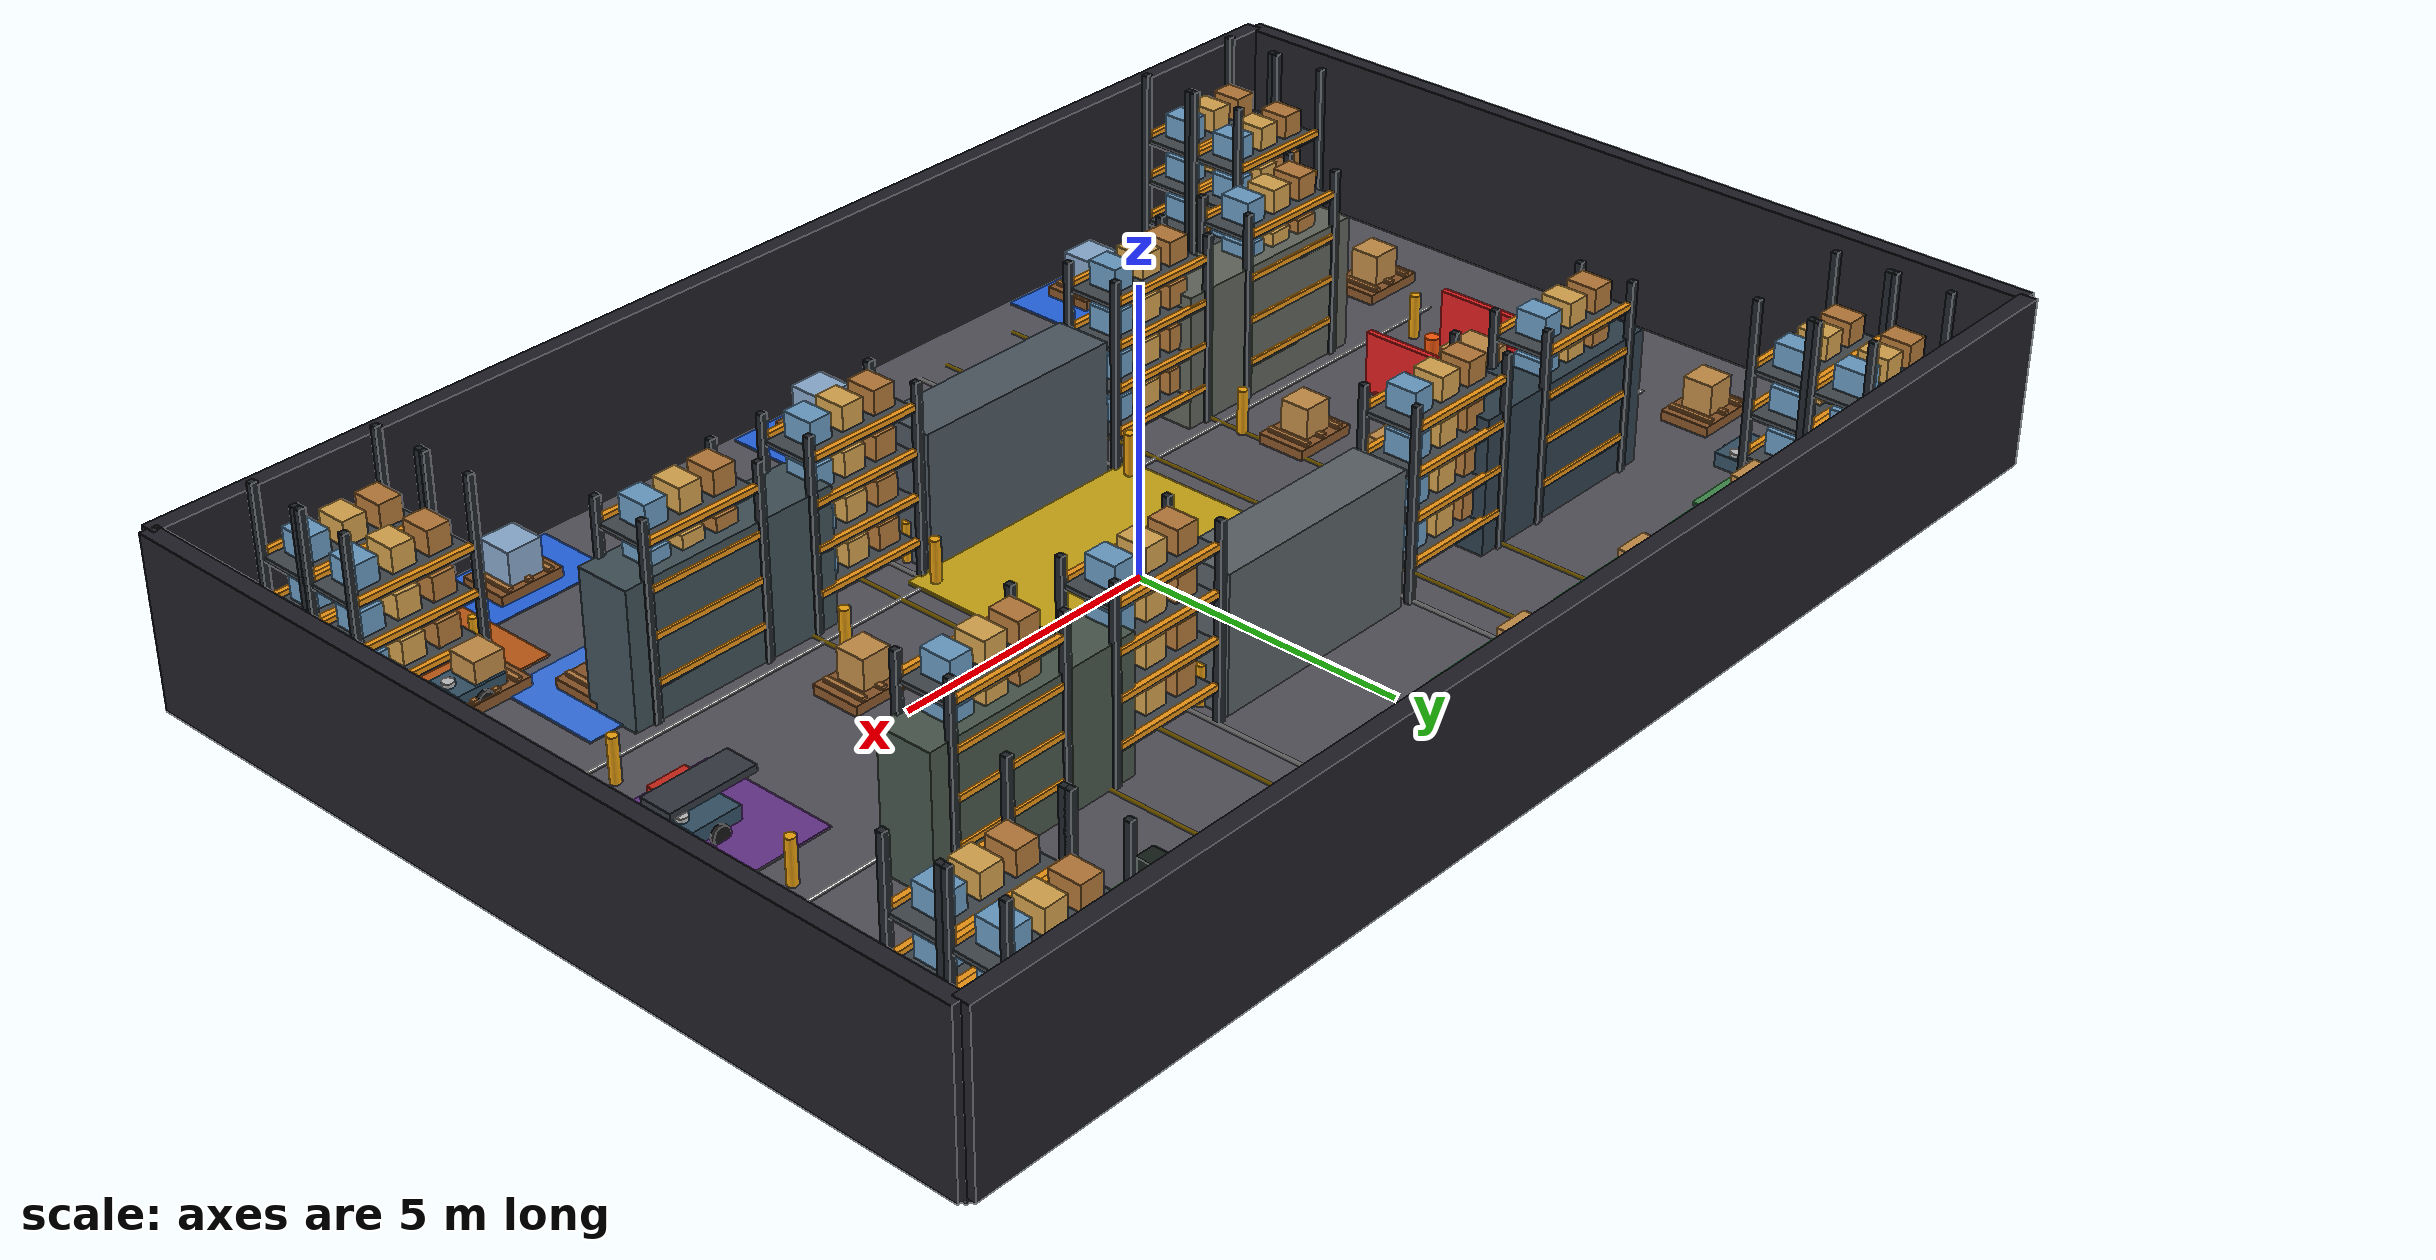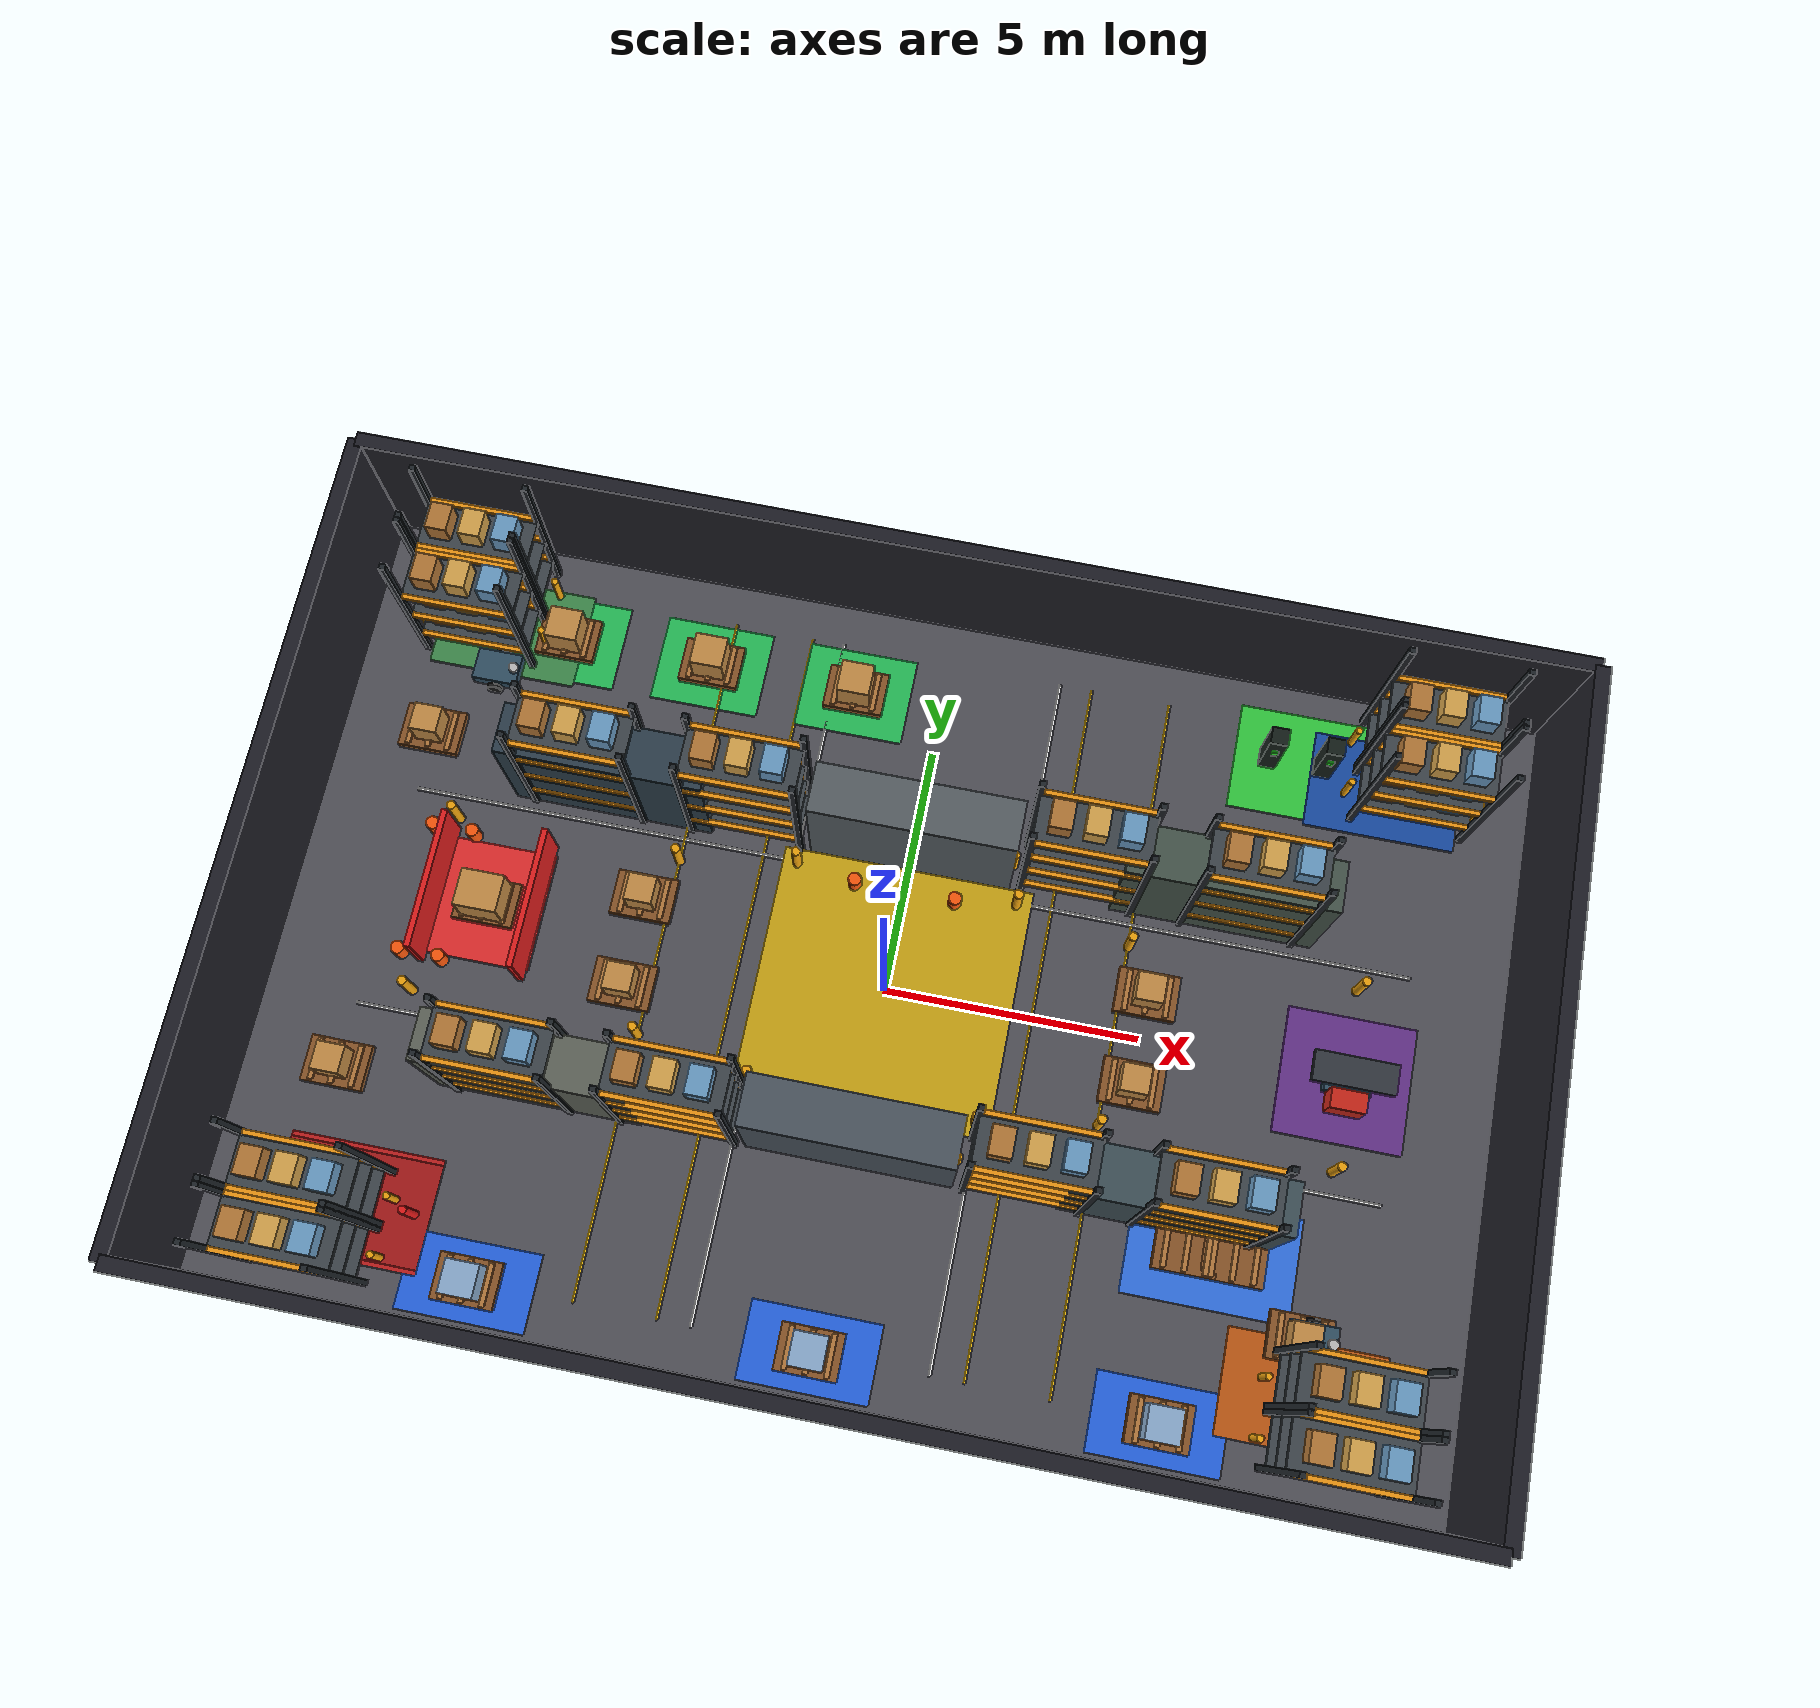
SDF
<?xml version="1.0"?>
<sdf version="1.9">

  <world name="synaids_advanced_warehouse">
    <plugin filename="gz-sim-sensors-system"
            name="gz::sim::systems::Sensors">
    </plugin>

    <gravity>0 0 -9.81</gravity>

    <physics name="default_physics" type="ignored">
      <max_step_size>0.001</max_step_size>
      <real_time_factor>1</real_time_factor>
      <real_time_update_rate>1000</real_time_update_rate>
    </physics>

    <plugin filename="gz-sim-physics-system"
            name="gz::sim::systems::Physics"/>

    <plugin filename="gz-sim-user-commands-system"
            name="gz::sim::systems::UserCommands"/>

    <plugin filename="gz-sim-scene-broadcaster-system"
            name="gz::sim::systems::SceneBroadcaster"/>

    <!-- FLOOR -->

    <model name="warehouse_floor">
      <static>true</static>
      <pose>0 0 -0.05 0 0 0</pose>

      <link name="link">

        <collision name="collision">
          <geometry>
            <box>
              <size>24 16 0.1</size>
            </box>
          </geometry>
        </collision>

        <visual name="visual">
          <geometry>
            <box>
              <size>24 16 0.1</size>
            </box>
          </geometry>

          <material>
            <ambient>0.20 0.20 0.22 1</ambient>
            <diffuse>0.32 0.32 0.35 1</diffuse>
            <specular>0.15 0.15 0.15 1</specular>
          </material>
        </visual>

      </link>
    </model>

    <!-- PERIMETER WALLS -->

    <model name="wall_north">
      <static>true</static>
      <pose>0 8 1.5 0 0 0</pose>
      <link name="link">
        <collision name="collision">
          <geometry>
            <box><size>24 0.3 3</size></box>
          </geometry>
        </collision>
        <visual name="visual">
          <geometry>
            <box><size>24 0.3 3</size></box>
          </geometry>
          <material>
            <ambient>0.08 0.08 0.10 1</ambient>
            <diffuse>0.12 0.12 0.15 1</diffuse>
          </material>
        </visual>
      </link>
    </model>

    <model name="wall_south">
      <static>true</static>
      <pose>0 -8 1.5 0 0 0</pose>
      <link name="link">
        <collision name="collision">
          <geometry>
            <box><size>24 0.3 3</size></box>
          </geometry>
        </collision>
        <visual name="visual">
          <geometry>
            <box><size>24 0.3 3</size></box>
          </geometry>
          <material>
            <ambient>0.08 0.08 0.10 1</ambient>
            <diffuse>0.12 0.12 0.15 1</diffuse>
          </material>
        </visual>
      </link>
    </model>

    <model name="wall_east">
      <static>true</static>
      <pose>12 0 1.5 0 0 0</pose>
      <link name="link">
        <collision name="collision">
          <geometry>
            <box><size>0.3 16 3</size></box>
          </geometry>
        </collision>
        <visual name="visual">
          <geometry>
            <box><size>0.3 16 3</size></box>
          </geometry>
          <material>
            <ambient>0.08 0.08 0.10 1</ambient>
            <diffuse>0.12 0.12 0.15 1</diffuse>
          </material>
        </visual>
      </link>
    </model>

    <model name="wall_west">
      <static>true</static>
      <pose>-12 0 1.5 0 0 0</pose>
      <link name="link">
        <collision name="collision">
          <geometry>
            <box><size>0.3 16 3</size></box>
          </geometry>
        </collision>
        <visual name="visual">
          <geometry>
            <box><size>0.3 16 3</size></box>
          </geometry>
          <material>
            <ambient>0.08 0.08 0.10 1</ambient>
            <diffuse>0.12 0.12 0.15 1</diffuse>
          </material>
        </visual>
      </link>
    </model>

    <!-- SHELF BLOCK 1 -->

    <model name="shelf_1">
      <static>true</static>
      <pose>-6 3 1.2 0 0 0</pose>
      <link name="link">

        <collision name="collision">
          <geometry>
            <box><size>4 1.0 2.4</size></box>
          </geometry>
        </collision>

        <visual name="visual">
          <geometry>
            <box><size>4 1.0 2.4</size></box>
          </geometry>
          <material>
            <ambient>0.08 0.12 0.16 1</ambient>
            <diffuse>0.18 0.25 0.30 1</diffuse>
          </material>
        </visual>

      </link>
    </model>

    <!-- SHELF BLOCK 2 -->

    <model name="shelf_2">
      <static>true</static>
      <pose>0 3 1.2 0 0 0</pose>
      <link name="link">

        <collision name="collision">
          <geometry>
            <box><size>4 1.0 2.4</size></box>
          </geometry>
        </collision>

        <visual name="visual">
          <geometry>
            <box><size>4 1.0 2.4</size></box>
          </geometry>
          <material>
            <ambient>0.18 0.18 0.18 1</ambient>
            <diffuse>0.35 0.38 0.40 1</diffuse>
          </material>
        </visual>

      </link>
    </model>

    <!-- SHELF BLOCK 3 -->

    <model name="shelf_3">
      <static>true</static>
      <pose>6 3 1.2 0 0 0</pose>
      <link name="link">

        <collision name="collision">
          <geometry>
            <box><size>4 1.0 2.4</size></box>
          </geometry>
        </collision>

        <visual name="visual">
          <geometry>
            <box><size>4 1.0 2.4</size></box>
          </geometry>
          <material>
            <ambient>0.12 0.16 0.14 1</ambient>
            <diffuse>0.28 0.34 0.30 1</diffuse>
          </material>
        </visual>

      </link>
    </model>

    <!-- SHELF BLOCK 4 -->

    <model name="shelf_4">
      <static>true</static>
      <pose>-6 -3 1.2 0 0 0</pose>
      <link name="link">

        <collision name="collision">
          <geometry>
            <box><size>4 1.0 2.4</size></box>
          </geometry>
        </collision>

        <visual name="visual">
          <geometry>
            <box><size>4 1.0 2.4</size></box>
          </geometry>
          <material>
            <ambient>0.20 0.20 0.18 1</ambient>
            <diffuse>0.38 0.40 0.36 1</diffuse>
          </material>
        </visual>

      </link>
    </model>

    <!-- SHELF BLOCK 5 -->

    <model name="shelf_5">
      <static>true</static>
      <pose>0 -3 1.2 0 0 0</pose>
      <link name="link">

        <collision name="collision">
          <geometry>
            <box><size>4 1.0 2.4</size></box>
          </geometry>
        </collision>

        <visual name="visual">
          <geometry>
            <box><size>4 1.0 2.4</size></box>
          </geometry>
          <material>
            <ambient>0.16 0.18 0.20 1</ambient>
            <diffuse>0.30 0.34 0.38 1</diffuse>
          </material>
        </visual>

      </link>
    </model>

    <!-- SHELF BLOCK 6 -->

    <model name="shelf_6">
      <static>true</static>
      <pose>6 -3 1.2 0 0 0</pose>
      <link name="link">

        <collision name="collision">
          <geometry>
            <box><size>4 1.0 2.4</size></box>
          </geometry>
        </collision>

        <visual name="visual">
          <geometry>
            <box><size>4 1.0 2.4</size></box>
          </geometry>
          <material>
            <ambient>0.12 0.18 0.20 1</ambient>
            <diffuse>0.25 0.32 0.35 1</diffuse>
          </material>
        </visual>

      </link>
    </model>

    <!-- PICKUP ZONE - GREEN -->

    <model name="pickup_zone">
      <static>true</static>
      <pose>-9 6 0.02 0 0 0</pose>
      <link name="link">
        <visual name="visual">
          <geometry>
            <box><size>3 2 0.04</size></box>
          </geometry>
          <material>
            <ambient>0.08 0.25 0.10 1</ambient>
            <diffuse>0.25 0.55 0.30 1</diffuse>
          </material>
        </visual>
      </link>
    </model>

    <!-- DELIVERY ZONE - ORANGE -->

    <model name="delivery_zone">
      <static>true</static>
      <pose>9 -6 0.02 0 0 0</pose>
      <link name="link">
        <visual name="visual">
          <geometry>
            <box><size>3 2 0.04</size></box>
          </geometry>
          <material>
            <ambient>0.35 0.16 0.03 1</ambient>
            <diffuse>0.75 0.35 0.08 1</diffuse>
          </material>
        </visual>
      </link>
    </model>

    <!-- CHARGING STATION - BLUE -->

    <model name="charging_station">
      <static>true</static>
      <pose>9 6 0.02 0 0 0</pose>
      <link name="link">
        <visual name="visual">
          <geometry>
            <box><size>3 2 0.04</size></box>
          </geometry>
          <material>
            <ambient>0.05 0.15 0.35 1</ambient>
            <diffuse>0.10 0.30 0.65 1</diffuse>
          </material>
        </visual>
      </link>
    </model>

    <!-- RESTRICTED ZONE - RED -->

    <model name="restricted_zone">
      <static>true</static>
      <pose>-9 -6 0.02 0 0 0</pose>
      <link name="link">
        <visual name="visual">
          <geometry>
            <box><size>3 2 0.04</size></box>
          </geometry>
          <material>
            <ambient>0.35 0.04 0.04 1</ambient>
            <diffuse>0.65 0.10 0.10 1</diffuse>
          </material>
        </visual>
      </link>
    </model>

    <!-- CENTRAL SAFETY CROSSING -->

    <model name="central_intersection">
      <static>true</static>
      <pose>0 0 0.025 0 0 0</pose>
      <link name="link">
        <visual name="visual">
          <geometry>
            <box><size>5 5 0.05</size></box>
          </geometry>
          <material>
            <ambient>0.45 0.38 0.03 1</ambient>
            <diffuse>0.80 0.65 0.08 1</diffuse>
          </material>
        </visual>
      </link>
    </model>

    <!-- MAINTENANCE AREA - PURPLE -->

    <model name="maintenance_area">
      <static>true</static>
      <pose>9 0 0.02 0 0 0</pose>
      <link name="link">
        <visual name="visual">
          <geometry>
            <box><size>2.5 2.5 0.04</size></box>
          </geometry>
          <material>
            <ambient>0.18 0.08 0.25 1</ambient>
            <diffuse>0.40 0.20 0.55 1</diffuse>
          </material>
        </visual>
      </link>
    </model>

    <!-- LIGHTING -->

    <light name="warehouse_light_1" type="directional">
      <pose>0 0 10 0 0 0</pose>
      <diffuse>1 1 1 1</diffuse>
      <specular>0.3 0.3 0.3 1</specular>
      <direction>-0.3 0.2 -1</direction>
    </light>

    <light name="warehouse_light_2" type="point">
      <pose>-6 0 6 0 0 0</pose>
      <diffuse>0.8 0.9 1.0 1</diffuse>
      <specular>0.2 0.2 0.2 1</specular>
      <attenuation>
        <range>15</range>
        <constant>0.5</constant>
        <linear>0.01</linear>
        <quadratic>0.001</quadratic>
      </attenuation>
    </light>

    <light name="warehouse_light_3" type="point">
      <pose>6 0 6 0 0 0</pose>
      <diffuse>1.0 0.8 0.6 1</diffuse>
      <specular>0.2 0.2 0.2 1</specular>
      <attenuation>
        <range>15</range>
        <constant>0.5</constant>
        <linear>0.01</linear>
        <quadratic>0.001</quadratic>
      </attenuation>
    </light>

  <model name="R1">

    <pose>-9 5 0.25 0 0 0</pose>

    <!-- Main chassis -->
    <link name="base_link">

      <inertial>
        <mass>12</mass>
        <inertia>
          <ixx>0.5</ixx>
          <iyy>0.5</iyy>
          <izz>0.5</izz>
        </inertia>
      </inertial>

      <collision name="base_collision">
        <geometry>
          <box>
            <size>0.9 0.65 0.25</size>
          </box>
        </geometry>
      </collision>

      <visual name="base_visual">
        <geometry>
          <box>
            <size>0.9 0.65 0.25</size>
          </box>
        </geometry>

        <material>
          <ambient>0.10 0.16 0.20 1</ambient>
          <diffuse>0.20 0.32 0.40 1</diffuse>
        </material>
      </visual>

    </link>

    <!-- Left wheel -->
    <link name="left_wheel">

      <pose>0 0.38 -0.12 1.5708 0 0</pose>

      <inertial>
        <mass>1</mass>
        <inertia>
          <ixx>0.02</ixx>
          <iyy>0.02</iyy>
          <izz>0.02</izz>
        </inertia>
      </inertial>

      <collision name="collision">
        <geometry>
          <cylinder>
            <radius>0.16</radius>
            <length>0.08</length>
          </cylinder>
        </geometry>
      </collision>

      <visual name="visual">
        <geometry>
          <cylinder>
            <radius>0.16</radius>
            <length>0.08</length>
          </cylinder>
        </geometry>

        <material>
          <ambient>0.03 0.03 0.03 1</ambient>
          <diffuse>0.08 0.08 0.08 1</diffuse>
        </material>
      </visual>

    </link>

    <!-- Right wheel -->
    <link name="right_wheel">

      <pose>0 -0.38 -0.12 1.5708 0 0</pose>

      <inertial>
        <mass>1</mass>
        <inertia>
          <ixx>0.02</ixx>
          <iyy>0.02</iyy>
          <izz>0.02</izz>
        </inertia>
      </inertial>

      <collision name="collision">
        <geometry>
          <cylinder>
            <radius>0.16</radius>
            <length>0.08</length>
          </cylinder>
        </geometry>
      </collision>

      <visual name="visual">
        <geometry>
          <cylinder>
            <radius>0.16</radius>
            <length>0.08</length>
          </cylinder>
        </geometry>

        <material>
          <ambient>0.03 0.03 0.03 1</ambient>
          <diffuse>0.08 0.08 0.08 1</diffuse>
        </material>
      </visual>

    </link>

    <!-- Front sensor housing -->
    <link name="sensor">

      <pose>0.35 0 0.18 0 0 0</pose>

      <visual name="visual">
        <geometry>
          <cylinder>
            <radius>0.10</radius>
            <length>0.08</length>
          </cylinder>
        </geometry>

        <material>
          <ambient>0.65 0.65 0.65 1</ambient>
          <diffuse>0.75 0.75 0.75 1</diffuse>
        </material>
      </visual>

    </link>

    <!-- Differential drive -->
    <plugin
      filename="gz-sim-diff-drive-system"
      name="gz::sim::systems::DiffDrive">

      <left_joint>left_wheel_joint</left_joint>
      <right_joint>right_wheel_joint</right_joint>

      <wheel_separation>0.76</wheel_separation>
      <wheel_radius>0.16</wheel_radius>

      <topic>/R1/cmd_vel</topic>
      <odom_topic>/R1/odom</odom_topic>

      <frame_id>odom</frame_id>
      <child_frame_id>base_link</child_frame_id>

    </plugin>

    <!-- Lidar -->
    <link name="lidar">

      <pose>0 0 0.35 0 0 0</pose>

      <sensor name="lidar_sensor" type="gpu_lidar">

        <topic>/R1/scan</topic>

        <update_rate>10</update_rate>

        <lidar>
          <scan>
            <horizontal>
              <samples>360</samples>
              <resolution>1</resolution>
              <min_angle>-3.14159</min_angle>
              <max_angle>3.14159</max_angle>
            </horizontal>
          </scan>

          <range>
            <min>0.12</min>
            <max>12</max>
            <resolution>0.01</resolution>
          </range>
        </lidar>

      </sensor>

    </link>

    <!-- Wheel joints -->
    <joint name="left_wheel_joint" type="revolute">
      <parent>base_link</parent>
      <child>left_wheel</child>
      <axis>
        <xyz>0 1 0</xyz>
      </axis>
    </joint>

    <joint name="right_wheel_joint" type="revolute">
      <parent>base_link</parent>
      <child>right_wheel</child>
      <axis>
        <xyz>0 1 0</xyz>
      </axis>
    </joint>

  </model>
<model name="R2">

    <pose>9 0 0.25 0 0 0</pose>

    <!-- Main chassis -->
    <link name="base_link">

      <inertial>
        <mass>12</mass>
        <inertia>
          <ixx>0.5</ixx>
          <iyy>0.5</iyy>
          <izz>0.5</izz>
        </inertia>
      </inertial>

      <collision name="base_collision">
        <geometry>
          <box>
            <size>0.9 0.65 0.25</size>
          </box>
        </geometry>
      </collision>

      <visual name="base_visual">
        <geometry>
          <box>
            <size>0.9 0.65 0.25</size>
          </box>
        </geometry>

        <material>
          <ambient>0.10 0.16 0.20 1</ambient>
          <diffuse>0.20 0.32 0.40 1</diffuse>
        </material>
      </visual>

    </link>

    <!-- Left wheel -->
    <link name="left_wheel">

      <pose>0 0.38 -0.12 1.5708 0 0</pose>

      <inertial>
        <mass>1</mass>
        <inertia>
          <ixx>0.02</ixx>
          <iyy>0.02</iyy>
          <izz>0.02</izz>
        </inertia>
      </inertial>

      <collision name="collision">
        <geometry>
          <cylinder>
            <radius>0.16</radius>
            <length>0.08</length>
          </cylinder>
        </geometry>
      </collision>

      <visual name="visual">
        <geometry>
          <cylinder>
            <radius>0.16</radius>
            <length>0.08</length>
          </cylinder>
        </geometry>

        <material>
          <ambient>0.03 0.03 0.03 1</ambient>
          <diffuse>0.08 0.08 0.08 1</diffuse>
        </material>
      </visual>

    </link>

    <!-- Right wheel -->
    <link name="right_wheel">

      <pose>0 -0.38 -0.12 1.5708 0 0</pose>

      <inertial>
        <mass>1</mass>
        <inertia>
          <ixx>0.02</ixx>
          <iyy>0.02</iyy>
          <izz>0.02</izz>
        </inertia>
      </inertial>

      <collision name="collision">
        <geometry>
          <cylinder>
            <radius>0.16</radius>
            <length>0.08</length>
          </cylinder>
        </geometry>
      </collision>

      <visual name="visual">
        <geometry>
          <cylinder>
            <radius>0.16</radius>
            <length>0.08</length>
          </cylinder>
        </geometry>

        <material>
          <ambient>0.03 0.03 0.03 1</ambient>
          <diffuse>0.08 0.08 0.08 1</diffuse>
        </material>
      </visual>

    </link>

    <!-- Front sensor housing -->
    <link name="sensor">

      <pose>0.35 0 0.18 0 0 0</pose>

      <visual name="visual">
        <geometry>
          <cylinder>
            <radius>0.10</radius>
            <length>0.08</length>
          </cylinder>
        </geometry>

        <material>
          <ambient>0.65 0.65 0.65 1</ambient>
          <diffuse>0.75 0.75 0.75 1</diffuse>
        </material>
      </visual>

    </link>

    <!-- Differential drive -->
    <plugin
      filename="gz-sim-diff-drive-system"
      name="gz::sim::systems::DiffDrive">

      <left_joint>left_wheel_joint</left_joint>
      <right_joint>right_wheel_joint</right_joint>

      <wheel_separation>0.76</wheel_separation>
      <wheel_radius>0.16</wheel_radius>

      <topic>/R2/cmd_vel</topic>
      <odom_topic>/R2/odom</odom_topic>

      <frame_id>odom</frame_id>
      <child_frame_id>base_link</child_frame_id>

    </plugin>

    <!-- Lidar -->
    <link name="lidar">

      <pose>0 0 0.35 0 0 0</pose>

      <sensor name="lidar_sensor" type="gpu_lidar">

        <topic>/R2/scan</topic>

        <update_rate>10</update_rate>

        <lidar>
          <scan>
            <horizontal>
              <samples>360</samples>
              <resolution>1</resolution>
              <min_angle>-3.14159</min_angle>
              <max_angle>3.14159</max_angle>
            </horizontal>
          </scan>

          <range>
            <min>0.12</min>
            <max>12</max>
            <resolution>0.01</resolution>
          </range>
        </lidar>

      </sensor>

    </link>

    <!-- Wheel joints -->
    <joint name="left_wheel_joint" type="revolute">
      <parent>base_link</parent>
      <child>left_wheel</child>
      <axis>
        <xyz>0 1 0</xyz>
      </axis>
    </joint>

    <joint name="right_wheel_joint" type="revolute">
      <parent>base_link</parent>
      <child>right_wheel</child>
      <axis>
        <xyz>0 1 0</xyz>
      </axis>
    </joint>

  </model>
<model name="R3">

    <pose>9 -5 0.25 0 0 0</pose>

    <!-- Main chassis -->
    <link name="base_link">

      <inertial>
        <mass>12</mass>
        <inertia>
          <ixx>0.5</ixx>
          <iyy>0.5</iyy>
          <izz>0.5</izz>
        </inertia>
      </inertial>

      <collision name="base_collision">
        <geometry>
          <box>
            <size>0.9 0.65 0.25</size>
          </box>
        </geometry>
      </collision>

      <visual name="base_visual">
        <geometry>
          <box>
            <size>0.9 0.65 0.25</size>
          </box>
        </geometry>

        <material>
          <ambient>0.10 0.16 0.20 1</ambient>
          <diffuse>0.20 0.32 0.40 1</diffuse>
        </material>
      </visual>

    </link>

    <!-- Left wheel -->
    <link name="left_wheel">

      <pose>0 0.38 -0.12 1.5708 0 0</pose>

      <inertial>
        <mass>1</mass>
        <inertia>
          <ixx>0.02</ixx>
          <iyy>0.02</iyy>
          <izz>0.02</izz>
        </inertia>
      </inertial>

      <collision name="collision">
        <geometry>
          <cylinder>
            <radius>0.16</radius>
            <length>0.08</length>
          </cylinder>
        </geometry>
      </collision>

      <visual name="visual">
        <geometry>
          <cylinder>
            <radius>0.16</radius>
            <length>0.08</length>
          </cylinder>
        </geometry>

        <material>
          <ambient>0.03 0.03 0.03 1</ambient>
          <diffuse>0.08 0.08 0.08 1</diffuse>
        </material>
      </visual>

    </link>

    <!-- Right wheel -->
    <link name="right_wheel">

      <pose>0 -0.38 -0.12 1.5708 0 0</pose>

      <inertial>
        <mass>1</mass>
        <inertia>
          <ixx>0.02</ixx>
          <iyy>0.02</iyy>
          <izz>0.02</izz>
        </inertia>
      </inertial>

      <collision name="collision">
        <geometry>
          <cylinder>
            <radius>0.16</radius>
            <length>0.08</length>
          </cylinder>
        </geometry>
      </collision>

      <visual name="visual">
        <geometry>
          <cylinder>
            <radius>0.16</radius>
            <length>0.08</length>
          </cylinder>
        </geometry>

        <material>
          <ambient>0.03 0.03 0.03 1</ambient>
          <diffuse>0.08 0.08 0.08 1</diffuse>
        </material>
      </visual>

    </link>

    <!-- Front sensor housing -->
    <link name="sensor">

      <pose>0.35 0 0.18 0 0 0</pose>

      <visual name="visual">
        <geometry>
          <cylinder>
            <radius>0.10</radius>
            <length>0.08</length>
          </cylinder>
        </geometry>

        <material>
          <ambient>0.65 0.65 0.65 1</ambient>
          <diffuse>0.75 0.75 0.75 1</diffuse>
        </material>
      </visual>

    </link>

    <!-- Differential drive -->
    <plugin
      filename="gz-sim-diff-drive-system"
      name="gz::sim::systems::DiffDrive">

      <left_joint>left_wheel_joint</left_joint>
      <right_joint>right_wheel_joint</right_joint>

      <wheel_separation>0.76</wheel_separation>
      <wheel_radius>0.16</wheel_radius>

      <topic>/R3/cmd_vel</topic>
      <odom_topic>/R3/odom</odom_topic>

      <frame_id>odom</frame_id>
      <child_frame_id>base_link</child_frame_id>

    </plugin>

    <!-- Lidar -->
    <link name="lidar">

      <pose>0 0 0.35 0 0 0</pose>

      <sensor name="lidar_sensor" type="gpu_lidar">

        <topic>/R3/scan</topic>

        <update_rate>10</update_rate>

        <lidar>
          <scan>
            <horizontal>
              <samples>360</samples>
              <resolution>1</resolution>
              <min_angle>-3.14159</min_angle>
              <max_angle>3.14159</max_angle>
            </horizontal>
          </scan>

          <range>
            <min>0.12</min>
            <max>12</max>
            <resolution>0.01</resolution>
          </range>
        </lidar>

      </sensor>

    </link>

    <!-- Wheel joints -->
    <joint name="left_wheel_joint" type="revolute">
      <parent>base_link</parent>
      <child>left_wheel</child>
      <axis>
        <xyz>0 1 0</xyz>
      </axis>
    </joint>

    <joint name="right_wheel_joint" type="revolute">
      <parent>base_link</parent>
      <child>right_wheel</child>
      <axis>
        <xyz>0 1 0</xyz>
      </axis>
    </joint>

  </model>

    <model name="intersection_surface">
      <static>true</static>
      <pose>0 0 0.018 0 0 0</pose>

      <link name="link">
        <visual name="visual">
          <geometry>
            <box>
              <size>4.0 4.0 0.025</size>
            </box>
          </geometry>

      <material>
        <ambient>0.92 0.72 0.05 1</ambient>
        <diffuse>0.92 0.72 0.05 1</diffuse>
        <specular>0.15 0.15 0.15 1</specular>
      </material>

        </visual>

      </link>
    </model>

    <model name="intersection_line_1">
      <static>true</static>
      <pose>0 -1.75 0.012 0 0 0</pose>

      <link name="link">
        <visual name="visual">
          <geometry>
            <box>
              <size>3.6 0.08 0.025</size>
            </box>
          </geometry>

      <material>
        <ambient>0.95 0.85 0.05 1</ambient>
        <diffuse>0.95 0.85 0.05 1</diffuse>
        <specular>0.15 0.15 0.15 1</specular>
      </material>

        </visual>

      </link>
    </model>

    <model name="intersection_line_2">
      <static>true</static>
      <pose>0 1.75 0.012 0 0 0</pose>

      <link name="link">
        <visual name="visual">
          <geometry>
            <box>
              <size>3.6 0.08 0.025</size>
            </box>
          </geometry>

      <material>
        <ambient>0.95 0.85 0.05 1</ambient>
        <diffuse>0.95 0.85 0.05 1</diffuse>
        <specular>0.15 0.15 0.15 1</specular>
      </material>

        </visual>

      </link>
    </model>

    <model name="intersection_line_3">
      <static>true</static>
      <pose>-1.75 0 0.012 0 0 0</pose>

      <link name="link">
        <visual name="visual">
          <geometry>
            <box>
              <size>0.08 3.6 0.025</size>
            </box>
          </geometry>

      <material>
        <ambient>0.95 0.85 0.05 1</ambient>
        <diffuse>0.95 0.85 0.05 1</diffuse>
        <specular>0.15 0.15 0.15 1</specular>
      </material>

        </visual>

      </link>
    </model>

    <model name="intersection_line_4">
      <static>true</static>
      <pose>1.75 0 0.012 0 0 0</pose>

      <link name="link">
        <visual name="visual">
          <geometry>
            <box>
              <size>0.08 3.6 0.025</size>
            </box>
          </geometry>

      <material>
        <ambient>0.95 0.85 0.05 1</ambient>
        <diffuse>0.95 0.85 0.05 1</diffuse>
        <specular>0.15 0.15 0.15 1</specular>
      </material>

        </visual>

      </link>
    </model>

    <model name="storage_rack_1_post_0">
      <static>true</static>
      <pose>-7.6 2.5 1.7 0 0 0</pose>

      <link name="link">
        <visual name="visual">
          <geometry>
            <box>
              <size>0.12 0.12 3.4</size>
            </box>
          </geometry>

      <material>
        <ambient>0.12 0.14 0.16 1</ambient>
        <diffuse>0.12 0.14 0.16 1</diffuse>
        <specular>0.15 0.15 0.15 1</specular>
      </material>

        </visual>

        <collision name="collision">
          <geometry>
            <box>
              <size>0.12 0.12 3.4</size>
            </box>
          </geometry>
        </collision>

      </link>
    </model>

    <model name="storage_rack_1_post_1">
      <static>true</static>
      <pose>-7.6 3.5 1.7 0 0 0</pose>

      <link name="link">
        <visual name="visual">
          <geometry>
            <box>
              <size>0.12 0.12 3.4</size>
            </box>
          </geometry>

      <material>
        <ambient>0.12 0.14 0.16 1</ambient>
        <diffuse>0.12 0.14 0.16 1</diffuse>
        <specular>0.15 0.15 0.15 1</specular>
      </material>

        </visual>

        <collision name="collision">
          <geometry>
            <box>
              <size>0.12 0.12 3.4</size>
            </box>
          </geometry>
        </collision>

      </link>
    </model>

    <model name="storage_rack_1_post_2">
      <static>true</static>
      <pose>-5.4 2.5 1.7 0 0 0</pose>

      <link name="link">
        <visual name="visual">
          <geometry>
            <box>
              <size>0.12 0.12 3.4</size>
            </box>
          </geometry>

      <material>
        <ambient>0.12 0.14 0.16 1</ambient>
        <diffuse>0.12 0.14 0.16 1</diffuse>
        <specular>0.15 0.15 0.15 1</specular>
      </material>

        </visual>

        <collision name="collision">
          <geometry>
            <box>
              <size>0.12 0.12 3.4</size>
            </box>
          </geometry>
        </collision>

      </link>
    </model>

    <model name="storage_rack_1_post_3">
      <static>true</static>
      <pose>-5.4 3.5 1.7 0 0 0</pose>

      <link name="link">
        <visual name="visual">
          <geometry>
            <box>
              <size>0.12 0.12 3.4</size>
            </box>
          </geometry>

      <material>
        <ambient>0.12 0.14 0.16 1</ambient>
        <diffuse>0.12 0.14 0.16 1</diffuse>
        <specular>0.15 0.15 0.15 1</specular>
      </material>

        </visual>

        <collision name="collision">
          <geometry>
            <box>
              <size>0.12 0.12 3.4</size>
            </box>
          </geometry>
        </collision>

      </link>
    </model>

    <model name="storage_rack_1_beam_front_0">
      <static>true</static>
      <pose>-6.5 2.5 0.65 0 0 0</pose>

      <link name="link">
        <visual name="visual">
          <geometry>
            <box>
              <size>2.2 0.1 0.1</size>
            </box>
          </geometry>

      <material>
        <ambient>0.95 0.60 0.08 1</ambient>
        <diffuse>0.95 0.60 0.08 1</diffuse>
        <specular>0.15 0.15 0.15 1</specular>
      </material>

        </visual>

        <collision name="collision">
          <geometry>
            <box>
              <size>2.2 0.1 0.1</size>
            </box>
          </geometry>
        </collision>

      </link>
    </model>

    <model name="storage_rack_1_beam_back_0">
      <static>true</static>
      <pose>-6.5 3.5 0.65 0 0 0</pose>

      <link name="link">
        <visual name="visual">
          <geometry>
            <box>
              <size>2.2 0.1 0.1</size>
            </box>
          </geometry>

      <material>
        <ambient>0.95 0.60 0.08 1</ambient>
        <diffuse>0.95 0.60 0.08 1</diffuse>
        <specular>0.15 0.15 0.15 1</specular>
      </material>

        </visual>

        <collision name="collision">
          <geometry>
            <box>
              <size>2.2 0.1 0.1</size>
            </box>
          </geometry>
        </collision>

      </link>
    </model>

    <model name="storage_rack_1_shelf_0">
      <static>true</static>
      <pose>-6.5 3.0 0.5700000000000001 0 0 0</pose>

      <link name="link">
        <visual name="visual">
          <geometry>
            <box>
              <size>2.2 1.0 0.08</size>
            </box>
          </geometry>

      <material>
        <ambient>0.25 0.28 0.30 1</ambient>
        <diffuse>0.25 0.28 0.30 1</diffuse>
        <specular>0.15 0.15 0.15 1</specular>
      </material>

        </visual>

        <collision name="collision">
          <geometry>
            <box>
              <size>2.2 1.0 0.08</size>
            </box>
          </geometry>
        </collision>

      </link>
    </model>

    <model name="storage_rack_1_package_0_0">
      <static>true</static>
      <pose>-7.15 3.0 0.87 0 0 0</pose>

      <link name="link">
        <visual name="visual">
          <geometry>
            <box>
              <size>0.42 0.55 0.42</size>
            </box>
          </geometry>

      <material>
        <ambient>0.72 0.48 0.22 1</ambient>
        <diffuse>0.72 0.48 0.22 1</diffuse>
        <specular>0.15 0.15 0.15 1</specular>
      </material>

        </visual>

        <collision name="collision">
          <geometry>
            <box>
              <size>0.42 0.55 0.42</size>
            </box>
          </geometry>
        </collision>

      </link>
    </model>

    <model name="storage_rack_1_package_0_1">
      <static>true</static>
      <pose>-6.5 3.0 0.87 0 0 0</pose>

      <link name="link">
        <visual name="visual">
          <geometry>
            <box>
              <size>0.42 0.55 0.42</size>
            </box>
          </geometry>

      <material>
        <ambient>0.85 0.65 0.30 1</ambient>
        <diffuse>0.85 0.65 0.30 1</diffuse>
        <specular>0.15 0.15 0.15 1</specular>
      </material>

        </visual>

        <collision name="collision">
          <geometry>
            <box>
              <size>0.42 0.55 0.42</size>
            </box>
          </geometry>
        </collision>

      </link>
    </model>

    <model name="storage_rack_1_package_0_2">
      <static>true</static>
      <pose>-5.8500000000000005 3.0 0.87 0 0 0</pose>

      <link name="link">
        <visual name="visual">
          <geometry>
            <box>
              <size>0.42 0.55 0.42</size>
            </box>
          </geometry>

      <material>
        <ambient>0.42 0.62 0.78 1</ambient>
        <diffuse>0.42 0.62 0.78 1</diffuse>
        <specular>0.15 0.15 0.15 1</specular>
      </material>

        </visual>

        <collision name="collision">
          <geometry>
            <box>
              <size>0.42 0.55 0.42</size>
            </box>
          </geometry>
        </collision>

      </link>
    </model>

    <model name="storage_rack_1_beam_front_1">
      <static>true</static>
      <pose>-6.5 2.5 1.4300000000000002 0 0 0</pose>

      <link name="link">
        <visual name="visual">
          <geometry>
            <box>
              <size>2.2 0.1 0.1</size>
            </box>
          </geometry>

      <material>
        <ambient>0.95 0.60 0.08 1</ambient>
        <diffuse>0.95 0.60 0.08 1</diffuse>
        <specular>0.15 0.15 0.15 1</specular>
      </material>

        </visual>

        <collision name="collision">
          <geometry>
            <box>
              <size>2.2 0.1 0.1</size>
            </box>
          </geometry>
        </collision>

      </link>
    </model>

    <model name="storage_rack_1_beam_back_1">
      <static>true</static>
      <pose>-6.5 3.5 1.4300000000000002 0 0 0</pose>

      <link name="link">
        <visual name="visual">
          <geometry>
            <box>
              <size>2.2 0.1 0.1</size>
            </box>
          </geometry>

      <material>
        <ambient>0.95 0.60 0.08 1</ambient>
        <diffuse>0.95 0.60 0.08 1</diffuse>
        <specular>0.15 0.15 0.15 1</specular>
      </material>

        </visual>

        <collision name="collision">
          <geometry>
            <box>
              <size>2.2 0.1 0.1</size>
            </box>
          </geometry>
        </collision>

      </link>
    </model>

    <model name="storage_rack_1_shelf_1">
      <static>true</static>
      <pose>-6.5 3.0 1.35 0 0 0</pose>

      <link name="link">
        <visual name="visual">
          <geometry>
            <box>
              <size>2.2 1.0 0.08</size>
            </box>
          </geometry>

      <material>
        <ambient>0.25 0.28 0.30 1</ambient>
        <diffuse>0.25 0.28 0.30 1</diffuse>
        <specular>0.15 0.15 0.15 1</specular>
      </material>

        </visual>

        <collision name="collision">
          <geometry>
            <box>
              <size>2.2 1.0 0.08</size>
            </box>
          </geometry>
        </collision>

      </link>
    </model>

    <model name="storage_rack_1_package_1_0">
      <static>true</static>
      <pose>-7.15 3.0 1.6500000000000001 0 0 0</pose>

      <link name="link">
        <visual name="visual">
          <geometry>
            <box>
              <size>0.42 0.55 0.42</size>
            </box>
          </geometry>

      <material>
        <ambient>0.72 0.48 0.22 1</ambient>
        <diffuse>0.72 0.48 0.22 1</diffuse>
        <specular>0.15 0.15 0.15 1</specular>
      </material>

        </visual>

        <collision name="collision">
          <geometry>
            <box>
              <size>0.42 0.55 0.42</size>
            </box>
          </geometry>
        </collision>

      </link>
    </model>

    <model name="storage_rack_1_package_1_1">
      <static>true</static>
      <pose>-6.5 3.0 1.6500000000000001 0 0 0</pose>

      <link name="link">
        <visual name="visual">
          <geometry>
            <box>
              <size>0.42 0.55 0.42</size>
            </box>
          </geometry>

      <material>
        <ambient>0.85 0.65 0.30 1</ambient>
        <diffuse>0.85 0.65 0.30 1</diffuse>
        <specular>0.15 0.15 0.15 1</specular>
      </material>

        </visual>

        <collision name="collision">
          <geometry>
            <box>
              <size>0.42 0.55 0.42</size>
            </box>
          </geometry>
        </collision>

      </link>
    </model>

    <model name="storage_rack_1_package_1_2">
      <static>true</static>
      <pose>-5.8500000000000005 3.0 1.6500000000000001 0 0 0</pose>

      <link name="link">
        <visual name="visual">
          <geometry>
            <box>
              <size>0.42 0.55 0.42</size>
            </box>
          </geometry>

      <material>
        <ambient>0.42 0.62 0.78 1</ambient>
        <diffuse>0.42 0.62 0.78 1</diffuse>
        <specular>0.15 0.15 0.15 1</specular>
      </material>

        </visual>

        <collision name="collision">
          <geometry>
            <box>
              <size>0.42 0.55 0.42</size>
            </box>
          </geometry>
        </collision>

      </link>
    </model>

    <model name="storage_rack_1_beam_front_2">
      <static>true</static>
      <pose>-6.5 2.5 2.21 0 0 0</pose>

      <link name="link">
        <visual name="visual">
          <geometry>
            <box>
              <size>2.2 0.1 0.1</size>
            </box>
          </geometry>

      <material>
        <ambient>0.95 0.60 0.08 1</ambient>
        <diffuse>0.95 0.60 0.08 1</diffuse>
        <specular>0.15 0.15 0.15 1</specular>
      </material>

        </visual>

        <collision name="collision">
          <geometry>
            <box>
              <size>2.2 0.1 0.1</size>
            </box>
          </geometry>
        </collision>

      </link>
    </model>

    <model name="storage_rack_1_beam_back_2">
      <static>true</static>
      <pose>-6.5 3.5 2.21 0 0 0</pose>

      <link name="link">
        <visual name="visual">
          <geometry>
            <box>
              <size>2.2 0.1 0.1</size>
            </box>
          </geometry>

      <material>
        <ambient>0.95 0.60 0.08 1</ambient>
        <diffuse>0.95 0.60 0.08 1</diffuse>
        <specular>0.15 0.15 0.15 1</specular>
      </material>

        </visual>

        <collision name="collision">
          <geometry>
            <box>
              <size>2.2 0.1 0.1</size>
            </box>
          </geometry>
        </collision>

      </link>
    </model>

    <model name="storage_rack_1_shelf_2">
      <static>true</static>
      <pose>-6.5 3.0 2.13 0 0 0</pose>

      <link name="link">
        <visual name="visual">
          <geometry>
            <box>
              <size>2.2 1.0 0.08</size>
            </box>
          </geometry>

      <material>
        <ambient>0.25 0.28 0.30 1</ambient>
        <diffuse>0.25 0.28 0.30 1</diffuse>
        <specular>0.15 0.15 0.15 1</specular>
      </material>

        </visual>

        <collision name="collision">
          <geometry>
            <box>
              <size>2.2 1.0 0.08</size>
            </box>
          </geometry>
        </collision>

      </link>
    </model>

    <model name="storage_rack_1_package_2_0">
      <static>true</static>
      <pose>-7.15 3.0 2.43 0 0 0</pose>

      <link name="link">
        <visual name="visual">
          <geometry>
            <box>
              <size>0.42 0.55 0.42</size>
            </box>
          </geometry>

      <material>
        <ambient>0.72 0.48 0.22 1</ambient>
        <diffuse>0.72 0.48 0.22 1</diffuse>
        <specular>0.15 0.15 0.15 1</specular>
      </material>

        </visual>

        <collision name="collision">
          <geometry>
            <box>
              <size>0.42 0.55 0.42</size>
            </box>
          </geometry>
        </collision>

      </link>
    </model>

    <model name="storage_rack_1_package_2_1">
      <static>true</static>
      <pose>-6.5 3.0 2.43 0 0 0</pose>

      <link name="link">
        <visual name="visual">
          <geometry>
            <box>
              <size>0.42 0.55 0.42</size>
            </box>
          </geometry>

      <material>
        <ambient>0.85 0.65 0.30 1</ambient>
        <diffuse>0.85 0.65 0.30 1</diffuse>
        <specular>0.15 0.15 0.15 1</specular>
      </material>

        </visual>

        <collision name="collision">
          <geometry>
            <box>
              <size>0.42 0.55 0.42</size>
            </box>
          </geometry>
        </collision>

      </link>
    </model>

    <model name="storage_rack_1_package_2_2">
      <static>true</static>
      <pose>-5.8500000000000005 3.0 2.43 0 0 0</pose>

      <link name="link">
        <visual name="visual">
          <geometry>
            <box>
              <size>0.42 0.55 0.42</size>
            </box>
          </geometry>

      <material>
        <ambient>0.42 0.62 0.78 1</ambient>
        <diffuse>0.42 0.62 0.78 1</diffuse>
        <specular>0.15 0.15 0.15 1</specular>
      </material>

        </visual>

        <collision name="collision">
          <geometry>
            <box>
              <size>0.42 0.55 0.42</size>
            </box>
          </geometry>
        </collision>

      </link>
    </model>

    <model name="storage_rack_1_beam_front_3">
      <static>true</static>
      <pose>-6.5 2.5 2.9899999999999998 0 0 0</pose>

      <link name="link">
        <visual name="visual">
          <geometry>
            <box>
              <size>2.2 0.1 0.1</size>
            </box>
          </geometry>

      <material>
        <ambient>0.95 0.60 0.08 1</ambient>
        <diffuse>0.95 0.60 0.08 1</diffuse>
        <specular>0.15 0.15 0.15 1</specular>
      </material>

        </visual>

        <collision name="collision">
          <geometry>
            <box>
              <size>2.2 0.1 0.1</size>
            </box>
          </geometry>
        </collision>

      </link>
    </model>

    <model name="storage_rack_1_beam_back_3">
      <static>true</static>
      <pose>-6.5 3.5 2.9899999999999998 0 0 0</pose>

      <link name="link">
        <visual name="visual">
          <geometry>
            <box>
              <size>2.2 0.1 0.1</size>
            </box>
          </geometry>

      <material>
        <ambient>0.95 0.60 0.08 1</ambient>
        <diffuse>0.95 0.60 0.08 1</diffuse>
        <specular>0.15 0.15 0.15 1</specular>
      </material>

        </visual>

        <collision name="collision">
          <geometry>
            <box>
              <size>2.2 0.1 0.1</size>
            </box>
          </geometry>
        </collision>

      </link>
    </model>

    <model name="storage_rack_1_shelf_3">
      <static>true</static>
      <pose>-6.5 3.0 2.9099999999999997 0 0 0</pose>

      <link name="link">
        <visual name="visual">
          <geometry>
            <box>
              <size>2.2 1.0 0.08</size>
            </box>
          </geometry>

      <material>
        <ambient>0.25 0.28 0.30 1</ambient>
        <diffuse>0.25 0.28 0.30 1</diffuse>
        <specular>0.15 0.15 0.15 1</specular>
      </material>

        </visual>

        <collision name="collision">
          <geometry>
            <box>
              <size>2.2 1.0 0.08</size>
            </box>
          </geometry>
        </collision>

      </link>
    </model>

    <model name="storage_rack_1_package_3_0">
      <static>true</static>
      <pose>-7.15 3.0 3.21 0 0 0</pose>

      <link name="link">
        <visual name="visual">
          <geometry>
            <box>
              <size>0.42 0.55 0.42</size>
            </box>
          </geometry>

      <material>
        <ambient>0.72 0.48 0.22 1</ambient>
        <diffuse>0.72 0.48 0.22 1</diffuse>
        <specular>0.15 0.15 0.15 1</specular>
      </material>

        </visual>

        <collision name="collision">
          <geometry>
            <box>
              <size>0.42 0.55 0.42</size>
            </box>
          </geometry>
        </collision>

      </link>
    </model>

    <model name="storage_rack_1_package_3_1">
      <static>true</static>
      <pose>-6.5 3.0 3.21 0 0 0</pose>

      <link name="link">
        <visual name="visual">
          <geometry>
            <box>
              <size>0.42 0.55 0.42</size>
            </box>
          </geometry>

      <material>
        <ambient>0.85 0.65 0.30 1</ambient>
        <diffuse>0.85 0.65 0.30 1</diffuse>
        <specular>0.15 0.15 0.15 1</specular>
      </material>

        </visual>

        <collision name="collision">
          <geometry>
            <box>
              <size>0.42 0.55 0.42</size>
            </box>
          </geometry>
        </collision>

      </link>
    </model>

    <model name="storage_rack_1_package_3_2">
      <static>true</static>
      <pose>-5.8500000000000005 3.0 3.21 0 0 0</pose>

      <link name="link">
        <visual name="visual">
          <geometry>
            <box>
              <size>0.42 0.55 0.42</size>
            </box>
          </geometry>

      <material>
        <ambient>0.42 0.62 0.78 1</ambient>
        <diffuse>0.42 0.62 0.78 1</diffuse>
        <specular>0.15 0.15 0.15 1</specular>
      </material>

        </visual>

        <collision name="collision">
          <geometry>
            <box>
              <size>0.42 0.55 0.42</size>
            </box>
          </geometry>
        </collision>

      </link>
    </model>

    <model name="storage_rack_1_guard_left">
      <static>true</static>
      <pose>-7.779999999999999 3.0 0.35 0 0 0</pose>

      <link name="link">
        <visual name="visual">
          <geometry>
            <cylinder>
              <radius>0.07</radius>
              <length>0.7</length>
            </cylinder>
          </geometry>

      <material>
        <ambient>0.95 0.65 0.05 1</ambient>
        <diffuse>0.95 0.65 0.05 1</diffuse>
        <specular>0.15 0.15 0.15 1</specular>
      </material>

        </visual>

        <collision name="collision">
          <geometry>
            <cylinder>
              <radius>0.07</radius>
              <length>0.7</length>
            </cylinder>
          </geometry>
        </collision>
      </link>
    </model>

    <model name="storage_rack_1_guard_right">
      <static>true</static>
      <pose>-5.220000000000001 3.0 0.35 0 0 0</pose>

      <link name="link">
        <visual name="visual">
          <geometry>
            <cylinder>
              <radius>0.07</radius>
              <length>0.7</length>
            </cylinder>
          </geometry>

      <material>
        <ambient>0.95 0.65 0.05 1</ambient>
        <diffuse>0.95 0.65 0.05 1</diffuse>
        <specular>0.15 0.15 0.15 1</specular>
      </material>

        </visual>

        <collision name="collision">
          <geometry>
            <cylinder>
              <radius>0.07</radius>
              <length>0.7</length>
            </cylinder>
          </geometry>
        </collision>
      </link>
    </model>

    <model name="storage_rack_2_post_0">
      <static>true</static>
      <pose>-4.4 2.5 1.7 0 0 0</pose>

      <link name="link">
        <visual name="visual">
          <geometry>
            <box>
              <size>0.12 0.12 3.4</size>
            </box>
          </geometry>

      <material>
        <ambient>0.12 0.14 0.16 1</ambient>
        <diffuse>0.12 0.14 0.16 1</diffuse>
        <specular>0.15 0.15 0.15 1</specular>
      </material>

        </visual>

        <collision name="collision">
          <geometry>
            <box>
              <size>0.12 0.12 3.4</size>
            </box>
          </geometry>
        </collision>

      </link>
    </model>

    <model name="storage_rack_2_post_1">
      <static>true</static>
      <pose>-4.4 3.5 1.7 0 0 0</pose>

      <link name="link">
        <visual name="visual">
          <geometry>
            <box>
              <size>0.12 0.12 3.4</size>
            </box>
          </geometry>

      <material>
        <ambient>0.12 0.14 0.16 1</ambient>
        <diffuse>0.12 0.14 0.16 1</diffuse>
        <specular>0.15 0.15 0.15 1</specular>
      </material>

        </visual>

        <collision name="collision">
          <geometry>
            <box>
              <size>0.12 0.12 3.4</size>
            </box>
          </geometry>
        </collision>

      </link>
    </model>

    <model name="storage_rack_2_post_2">
      <static>true</static>
      <pose>-2.1999999999999997 2.5 1.7 0 0 0</pose>

      <link name="link">
        <visual name="visual">
          <geometry>
            <box>
              <size>0.12 0.12 3.4</size>
            </box>
          </geometry>

      <material>
        <ambient>0.12 0.14 0.16 1</ambient>
        <diffuse>0.12 0.14 0.16 1</diffuse>
        <specular>0.15 0.15 0.15 1</specular>
      </material>

        </visual>

        <collision name="collision">
          <geometry>
            <box>
              <size>0.12 0.12 3.4</size>
            </box>
          </geometry>
        </collision>

      </link>
    </model>

    <model name="storage_rack_2_post_3">
      <static>true</static>
      <pose>-2.1999999999999997 3.5 1.7 0 0 0</pose>

      <link name="link">
        <visual name="visual">
          <geometry>
            <box>
              <size>0.12 0.12 3.4</size>
            </box>
          </geometry>

      <material>
        <ambient>0.12 0.14 0.16 1</ambient>
        <diffuse>0.12 0.14 0.16 1</diffuse>
        <specular>0.15 0.15 0.15 1</specular>
      </material>

        </visual>

        <collision name="collision">
          <geometry>
            <box>
              <size>0.12 0.12 3.4</size>
            </box>
          </geometry>
        </collision>

      </link>
    </model>

    <model name="storage_rack_2_beam_front_0">
      <static>true</static>
      <pose>-3.3 2.5 0.65 0 0 0</pose>

      <link name="link">
        <visual name="visual">
          <geometry>
            <box>
              <size>2.2 0.1 0.1</size>
            </box>
          </geometry>

      <material>
        <ambient>0.95 0.60 0.08 1</ambient>
        <diffuse>0.95 0.60 0.08 1</diffuse>
        <specular>0.15 0.15 0.15 1</specular>
      </material>

        </visual>

        <collision name="collision">
          <geometry>
            <box>
              <size>2.2 0.1 0.1</size>
            </box>
          </geometry>
        </collision>

      </link>
    </model>

    <model name="storage_rack_2_beam_back_0">
      <static>true</static>
      <pose>-3.3 3.5 0.65 0 0 0</pose>

      <link name="link">
        <visual name="visual">
          <geometry>
            <box>
              <size>2.2 0.1 0.1</size>
            </box>
          </geometry>

      <material>
        <ambient>0.95 0.60 0.08 1</ambient>
        <diffuse>0.95 0.60 0.08 1</diffuse>
        <specular>0.15 0.15 0.15 1</specular>
      </material>

        </visual>

        <collision name="collision">
          <geometry>
            <box>
              <size>2.2 0.1 0.1</size>
            </box>
          </geometry>
        </collision>

      </link>
    </model>

    <model name="storage_rack_2_shelf_0">
      <static>true</static>
      <pose>-3.3 3.0 0.5700000000000001 0 0 0</pose>

      <link name="link">
        <visual name="visual">
          <geometry>
            <box>
              <size>2.2 1.0 0.08</size>
            </box>
          </geometry>

      <material>
        <ambient>0.25 0.28 0.30 1</ambient>
        <diffuse>0.25 0.28 0.30 1</diffuse>
        <specular>0.15 0.15 0.15 1</specular>
      </material>

        </visual>

        <collision name="collision">
          <geometry>
            <box>
              <size>2.2 1.0 0.08</size>
            </box>
          </geometry>
        </collision>

      </link>
    </model>

    <model name="storage_rack_2_package_0_0">
      <static>true</static>
      <pose>-3.9499999999999997 3.0 0.87 0 0 0</pose>

      <link name="link">
        <visual name="visual">
          <geometry>
            <box>
              <size>0.42 0.55 0.42</size>
            </box>
          </geometry>

      <material>
        <ambient>0.72 0.48 0.22 1</ambient>
        <diffuse>0.72 0.48 0.22 1</diffuse>
        <specular>0.15 0.15 0.15 1</specular>
      </material>

        </visual>

        <collision name="collision">
          <geometry>
            <box>
              <size>0.42 0.55 0.42</size>
            </box>
          </geometry>
        </collision>

      </link>
    </model>

    <model name="storage_rack_2_package_0_1">
      <static>true</static>
      <pose>-3.3 3.0 0.87 0 0 0</pose>

      <link name="link">
        <visual name="visual">
          <geometry>
            <box>
              <size>0.42 0.55 0.42</size>
            </box>
          </geometry>

      <material>
        <ambient>0.85 0.65 0.30 1</ambient>
        <diffuse>0.85 0.65 0.30 1</diffuse>
        <specular>0.15 0.15 0.15 1</specular>
      </material>

        </visual>

        <collision name="collision">
          <geometry>
            <box>
              <size>0.42 0.55 0.42</size>
            </box>
          </geometry>
        </collision>

      </link>
    </model>

    <model name="storage_rack_2_package_0_2">
      <static>true</static>
      <pose>-2.6499999999999995 3.0 0.87 0 0 0</pose>

      <link name="link">
        <visual name="visual">
          <geometry>
            <box>
              <size>0.42 0.55 0.42</size>
            </box>
          </geometry>

      <material>
        <ambient>0.42 0.62 0.78 1</ambient>
        <diffuse>0.42 0.62 0.78 1</diffuse>
        <specular>0.15 0.15 0.15 1</specular>
      </material>

        </visual>

        <collision name="collision">
          <geometry>
            <box>
              <size>0.42 0.55 0.42</size>
            </box>
          </geometry>
        </collision>

      </link>
    </model>

    <model name="storage_rack_2_beam_front_1">
      <static>true</static>
      <pose>-3.3 2.5 1.4300000000000002 0 0 0</pose>

      <link name="link">
        <visual name="visual">
          <geometry>
            <box>
              <size>2.2 0.1 0.1</size>
            </box>
          </geometry>

      <material>
        <ambient>0.95 0.60 0.08 1</ambient>
        <diffuse>0.95 0.60 0.08 1</diffuse>
        <specular>0.15 0.15 0.15 1</specular>
      </material>

        </visual>

        <collision name="collision">
          <geometry>
            <box>
              <size>2.2 0.1 0.1</size>
            </box>
          </geometry>
        </collision>

      </link>
    </model>

    <model name="storage_rack_2_beam_back_1">
      <static>true</static>
      <pose>-3.3 3.5 1.4300000000000002 0 0 0</pose>

      <link name="link">
        <visual name="visual">
          <geometry>
            <box>
              <size>2.2 0.1 0.1</size>
            </box>
          </geometry>

      <material>
        <ambient>0.95 0.60 0.08 1</ambient>
        <diffuse>0.95 0.60 0.08 1</diffuse>
        <specular>0.15 0.15 0.15 1</specular>
      </material>

        </visual>

        <collision name="collision">
          <geometry>
            <box>
              <size>2.2 0.1 0.1</size>
            </box>
          </geometry>
        </collision>

      </link>
    </model>

    <model name="storage_rack_2_shelf_1">
      <static>true</static>
      <pose>-3.3 3.0 1.35 0 0 0</pose>

      <link name="link">
        <visual name="visual">
          <geometry>
            <box>
              <size>2.2 1.0 0.08</size>
            </box>
          </geometry>

      <material>
        <ambient>0.25 0.28 0.30 1</ambient>
        <diffuse>0.25 0.28 0.30 1</diffuse>
        <specular>0.15 0.15 0.15 1</specular>
      </material>

        </visual>

        <collision name="collision">
          <geometry>
            <box>
              <size>2.2 1.0 0.08</size>
            </box>
          </geometry>
        </collision>

      </link>
    </model>

    <model name="storage_rack_2_package_1_0">
      <static>true</static>
      <pose>-3.9499999999999997 3.0 1.6500000000000001 0 0 0</pose>

      <link name="link">
        <visual name="visual">
          <geometry>
            <box>
              <size>0.42 0.55 0.42</size>
            </box>
          </geometry>

      <material>
        <ambient>0.72 0.48 0.22 1</ambient>
        <diffuse>0.72 0.48 0.22 1</diffuse>
        <specular>0.15 0.15 0.15 1</specular>
      </material>

        </visual>

        <collision name="collision">
          <geometry>
            <box>
              <size>0.42 0.55 0.42</size>
            </box>
          </geometry>
        </collision>

      </link>
    </model>

    <model name="storage_rack_2_package_1_1">
      <static>true</static>
      <pose>-3.3 3.0 1.6500000000000001 0 0 0</pose>

      <link name="link">
        <visual name="visual">
          <geometry>
            <box>
              <size>0.42 0.55 0.42</size>
            </box>
          </geometry>

      <material>
        <ambient>0.85 0.65 0.30 1</ambient>
        <diffuse>0.85 0.65 0.30 1</diffuse>
        <specular>0.15 0.15 0.15 1</specular>
      </material>

        </visual>

        <collision name="collision">
          <geometry>
            <box>
              <size>0.42 0.55 0.42</size>
            </box>
          </geometry>
        </collision>

      </link>
    </model>

    <model name="storage_rack_2_package_1_2">
      <static>true</static>
      <pose>-2.6499999999999995 3.0 1.6500000000000001 0 0 0</pose>

      <link name="link">
        <visual name="visual">
          <geometry>
            <box>
              <size>0.42 0.55 0.42</size>
            </box>
          </geometry>

      <material>
        <ambient>0.42 0.62 0.78 1</ambient>
        <diffuse>0.42 0.62 0.78 1</diffuse>
        <specular>0.15 0.15 0.15 1</specular>
      </material>

        </visual>

        <collision name="collision">
          <geometry>
            <box>
              <size>0.42 0.55 0.42</size>
            </box>
          </geometry>
        </collision>

      </link>
    </model>

    <model name="storage_rack_2_beam_front_2">
      <static>true</static>
      <pose>-3.3 2.5 2.21 0 0 0</pose>

      <link name="link">
        <visual name="visual">
          <geometry>
            <box>
              <size>2.2 0.1 0.1</size>
            </box>
          </geometry>

      <material>
        <ambient>0.95 0.60 0.08 1</ambient>
        <diffuse>0.95 0.60 0.08 1</diffuse>
        <specular>0.15 0.15 0.15 1</specular>
      </material>

        </visual>

        <collision name="collision">
          <geometry>
            <box>
              <size>2.2 0.1 0.1</size>
            </box>
          </geometry>
        </collision>

      </link>
    </model>

    <model name="storage_rack_2_beam_back_2">
      <static>true</static>
      <pose>-3.3 3.5 2.21 0 0 0</pose>

      <link name="link">
        <visual name="visual">
          <geometry>
            <box>
              <size>2.2 0.1 0.1</size>
            </box>
          </geometry>

      <material>
        <ambient>0.95 0.60 0.08 1</ambient>
        <diffuse>0.95 0.60 0.08 1</diffuse>
        <specular>0.15 0.15 0.15 1</specular>
      </material>

        </visual>

        <collision name="collision">
          <geometry>
            <box>
              <size>2.2 0.1 0.1</size>
            </box>
          </geometry>
        </collision>

      </link>
    </model>

    <model name="storage_rack_2_shelf_2">
      <static>true</static>
      <pose>-3.3 3.0 2.13 0 0 0</pose>

      <link name="link">
        <visual name="visual">
          <geometry>
            <box>
              <size>2.2 1.0 0.08</size>
            </box>
          </geometry>

      <material>
        <ambient>0.25 0.28 0.30 1</ambient>
        <diffuse>0.25 0.28 0.30 1</diffuse>
        <specular>0.15 0.15 0.15 1</specular>
      </material>

        </visual>

        <collision name="collision">
          <geometry>
            <box>
              <size>2.2 1.0 0.08</size>
            </box>
          </geometry>
        </collision>

      </link>
    </model>

    <model name="storage_rack_2_package_2_0">
      <static>true</static>
      <pose>-3.9499999999999997 3.0 2.43 0 0 0</pose>

      <link name="link">
        <visual name="visual">
          <geometry>
            <box>
              <size>0.42 0.55 0.42</size>
            </box>
          </geometry>

      <material>
        <ambient>0.72 0.48 0.22 1</ambient>
        <diffuse>0.72 0.48 0.22 1</diffuse>
        <specular>0.15 0.15 0.15 1</specular>
      </material>

        </visual>

        <collision name="collision">
          <geometry>
            <box>
              <size>0.42 0.55 0.42</size>
            </box>
          </geometry>
        </collision>

      </link>
    </model>

    <model name="storage_rack_2_package_2_1">
      <static>true</static>
      <pose>-3.3 3.0 2.43 0 0 0</pose>

      <link name="link">
        <visual name="visual">
          <geometry>
            <box>
              <size>0.42 0.55 0.42</size>
            </box>
          </geometry>

      <material>
        <ambient>0.85 0.65 0.30 1</ambient>
        <diffuse>0.85 0.65 0.30 1</diffuse>
        <specular>0.15 0.15 0.15 1</specular>
      </material>

        </visual>

        <collision name="collision">
          <geometry>
            <box>
              <size>0.42 0.55 0.42</size>
            </box>
          </geometry>
        </collision>

      </link>
    </model>

    <model name="storage_rack_2_package_2_2">
      <static>true</static>
      <pose>-2.6499999999999995 3.0 2.43 0 0 0</pose>

      <link name="link">
        <visual name="visual">
          <geometry>
            <box>
              <size>0.42 0.55 0.42</size>
            </box>
          </geometry>

      <material>
        <ambient>0.42 0.62 0.78 1</ambient>
        <diffuse>0.42 0.62 0.78 1</diffuse>
        <specular>0.15 0.15 0.15 1</specular>
      </material>

        </visual>

        <collision name="collision">
          <geometry>
            <box>
              <size>0.42 0.55 0.42</size>
            </box>
          </geometry>
        </collision>

      </link>
    </model>

    <model name="storage_rack_2_beam_front_3">
      <static>true</static>
      <pose>-3.3 2.5 2.9899999999999998 0 0 0</pose>

      <link name="link">
        <visual name="visual">
          <geometry>
            <box>
              <size>2.2 0.1 0.1</size>
            </box>
          </geometry>

      <material>
        <ambient>0.95 0.60 0.08 1</ambient>
        <diffuse>0.95 0.60 0.08 1</diffuse>
        <specular>0.15 0.15 0.15 1</specular>
      </material>

        </visual>

        <collision name="collision">
          <geometry>
            <box>
              <size>2.2 0.1 0.1</size>
            </box>
          </geometry>
        </collision>

      </link>
    </model>

    <model name="storage_rack_2_beam_back_3">
      <static>true</static>
      <pose>-3.3 3.5 2.9899999999999998 0 0 0</pose>

      <link name="link">
        <visual name="visual">
          <geometry>
            <box>
              <size>2.2 0.1 0.1</size>
            </box>
          </geometry>

      <material>
        <ambient>0.95 0.60 0.08 1</ambient>
        <diffuse>0.95 0.60 0.08 1</diffuse>
        <specular>0.15 0.15 0.15 1</specular>
      </material>

        </visual>

        <collision name="collision">
          <geometry>
            <box>
              <size>2.2 0.1 0.1</size>
            </box>
          </geometry>
        </collision>

      </link>
    </model>

    <model name="storage_rack_2_shelf_3">
      <static>true</static>
      <pose>-3.3 3.0 2.9099999999999997 0 0 0</pose>

      <link name="link">
        <visual name="visual">
          <geometry>
            <box>
              <size>2.2 1.0 0.08</size>
            </box>
          </geometry>

      <material>
        <ambient>0.25 0.28 0.30 1</ambient>
        <diffuse>0.25 0.28 0.30 1</diffuse>
        <specular>0.15 0.15 0.15 1</specular>
      </material>

        </visual>

        <collision name="collision">
          <geometry>
            <box>
              <size>2.2 1.0 0.08</size>
            </box>
          </geometry>
        </collision>

      </link>
    </model>

    <model name="storage_rack_2_package_3_0">
      <static>true</static>
      <pose>-3.9499999999999997 3.0 3.21 0 0 0</pose>

      <link name="link">
        <visual name="visual">
          <geometry>
            <box>
              <size>0.42 0.55 0.42</size>
            </box>
          </geometry>

      <material>
        <ambient>0.72 0.48 0.22 1</ambient>
        <diffuse>0.72 0.48 0.22 1</diffuse>
        <specular>0.15 0.15 0.15 1</specular>
      </material>

        </visual>

        <collision name="collision">
          <geometry>
            <box>
              <size>0.42 0.55 0.42</size>
            </box>
          </geometry>
        </collision>

      </link>
    </model>

    <model name="storage_rack_2_package_3_1">
      <static>true</static>
      <pose>-3.3 3.0 3.21 0 0 0</pose>

      <link name="link">
        <visual name="visual">
          <geometry>
            <box>
              <size>0.42 0.55 0.42</size>
            </box>
          </geometry>

      <material>
        <ambient>0.85 0.65 0.30 1</ambient>
        <diffuse>0.85 0.65 0.30 1</diffuse>
        <specular>0.15 0.15 0.15 1</specular>
      </material>

        </visual>

        <collision name="collision">
          <geometry>
            <box>
              <size>0.42 0.55 0.42</size>
            </box>
          </geometry>
        </collision>

      </link>
    </model>

    <model name="storage_rack_2_package_3_2">
      <static>true</static>
      <pose>-2.6499999999999995 3.0 3.21 0 0 0</pose>

      <link name="link">
        <visual name="visual">
          <geometry>
            <box>
              <size>0.42 0.55 0.42</size>
            </box>
          </geometry>

      <material>
        <ambient>0.42 0.62 0.78 1</ambient>
        <diffuse>0.42 0.62 0.78 1</diffuse>
        <specular>0.15 0.15 0.15 1</specular>
      </material>

        </visual>

        <collision name="collision">
          <geometry>
            <box>
              <size>0.42 0.55 0.42</size>
            </box>
          </geometry>
        </collision>

      </link>
    </model>

    <model name="storage_rack_2_guard_left">
      <static>true</static>
      <pose>-4.58 3.0 0.35 0 0 0</pose>

      <link name="link">
        <visual name="visual">
          <geometry>
            <cylinder>
              <radius>0.07</radius>
              <length>0.7</length>
            </cylinder>
          </geometry>

      <material>
        <ambient>0.95 0.65 0.05 1</ambient>
        <diffuse>0.95 0.65 0.05 1</diffuse>
        <specular>0.15 0.15 0.15 1</specular>
      </material>

        </visual>

        <collision name="collision">
          <geometry>
            <cylinder>
              <radius>0.07</radius>
              <length>0.7</length>
            </cylinder>
          </geometry>
        </collision>
      </link>
    </model>

    <model name="storage_rack_2_guard_right">
      <static>true</static>
      <pose>-2.0199999999999996 3.0 0.35 0 0 0</pose>

      <link name="link">
        <visual name="visual">
          <geometry>
            <cylinder>
              <radius>0.07</radius>
              <length>0.7</length>
            </cylinder>
          </geometry>

      <material>
        <ambient>0.95 0.65 0.05 1</ambient>
        <diffuse>0.95 0.65 0.05 1</diffuse>
        <specular>0.15 0.15 0.15 1</specular>
      </material>

        </visual>

        <collision name="collision">
          <geometry>
            <cylinder>
              <radius>0.07</radius>
              <length>0.7</length>
            </cylinder>
          </geometry>
        </collision>
      </link>
    </model>

    <model name="storage_rack_3_post_0">
      <static>true</static>
      <pose>2.1999999999999997 2.5 1.7 0 0 0</pose>

      <link name="link">
        <visual name="visual">
          <geometry>
            <box>
              <size>0.12 0.12 3.4</size>
            </box>
          </geometry>

      <material>
        <ambient>0.12 0.14 0.16 1</ambient>
        <diffuse>0.12 0.14 0.16 1</diffuse>
        <specular>0.15 0.15 0.15 1</specular>
      </material>

        </visual>

        <collision name="collision">
          <geometry>
            <box>
              <size>0.12 0.12 3.4</size>
            </box>
          </geometry>
        </collision>

      </link>
    </model>

    <model name="storage_rack_3_post_1">
      <static>true</static>
      <pose>2.1999999999999997 3.5 1.7 0 0 0</pose>

      <link name="link">
        <visual name="visual">
          <geometry>
            <box>
              <size>0.12 0.12 3.4</size>
            </box>
          </geometry>

      <material>
        <ambient>0.12 0.14 0.16 1</ambient>
        <diffuse>0.12 0.14 0.16 1</diffuse>
        <specular>0.15 0.15 0.15 1</specular>
      </material>

        </visual>

        <collision name="collision">
          <geometry>
            <box>
              <size>0.12 0.12 3.4</size>
            </box>
          </geometry>
        </collision>

      </link>
    </model>

    <model name="storage_rack_3_post_2">
      <static>true</static>
      <pose>4.4 2.5 1.7 0 0 0</pose>

      <link name="link">
        <visual name="visual">
          <geometry>
            <box>
              <size>0.12 0.12 3.4</size>
            </box>
          </geometry>

      <material>
        <ambient>0.12 0.14 0.16 1</ambient>
        <diffuse>0.12 0.14 0.16 1</diffuse>
        <specular>0.15 0.15 0.15 1</specular>
      </material>

        </visual>

        <collision name="collision">
          <geometry>
            <box>
              <size>0.12 0.12 3.4</size>
            </box>
          </geometry>
        </collision>

      </link>
    </model>

    <model name="storage_rack_3_post_3">
      <static>true</static>
      <pose>4.4 3.5 1.7 0 0 0</pose>

      <link name="link">
        <visual name="visual">
          <geometry>
            <box>
              <size>0.12 0.12 3.4</size>
            </box>
          </geometry>

      <material>
        <ambient>0.12 0.14 0.16 1</ambient>
        <diffuse>0.12 0.14 0.16 1</diffuse>
        <specular>0.15 0.15 0.15 1</specular>
      </material>

        </visual>

        <collision name="collision">
          <geometry>
            <box>
              <size>0.12 0.12 3.4</size>
            </box>
          </geometry>
        </collision>

      </link>
    </model>

    <model name="storage_rack_3_beam_front_0">
      <static>true</static>
      <pose>3.3 2.5 0.65 0 0 0</pose>

      <link name="link">
        <visual name="visual">
          <geometry>
            <box>
              <size>2.2 0.1 0.1</size>
            </box>
          </geometry>

      <material>
        <ambient>0.95 0.60 0.08 1</ambient>
        <diffuse>0.95 0.60 0.08 1</diffuse>
        <specular>0.15 0.15 0.15 1</specular>
      </material>

        </visual>

        <collision name="collision">
          <geometry>
            <box>
              <size>2.2 0.1 0.1</size>
            </box>
          </geometry>
        </collision>

      </link>
    </model>

    <model name="storage_rack_3_beam_back_0">
      <static>true</static>
      <pose>3.3 3.5 0.65 0 0 0</pose>

      <link name="link">
        <visual name="visual">
          <geometry>
            <box>
              <size>2.2 0.1 0.1</size>
            </box>
          </geometry>

      <material>
        <ambient>0.95 0.60 0.08 1</ambient>
        <diffuse>0.95 0.60 0.08 1</diffuse>
        <specular>0.15 0.15 0.15 1</specular>
      </material>

        </visual>

        <collision name="collision">
          <geometry>
            <box>
              <size>2.2 0.1 0.1</size>
            </box>
          </geometry>
        </collision>

      </link>
    </model>

    <model name="storage_rack_3_shelf_0">
      <static>true</static>
      <pose>3.3 3.0 0.5700000000000001 0 0 0</pose>

      <link name="link">
        <visual name="visual">
          <geometry>
            <box>
              <size>2.2 1.0 0.08</size>
            </box>
          </geometry>

      <material>
        <ambient>0.25 0.28 0.30 1</ambient>
        <diffuse>0.25 0.28 0.30 1</diffuse>
        <specular>0.15 0.15 0.15 1</specular>
      </material>

        </visual>

        <collision name="collision">
          <geometry>
            <box>
              <size>2.2 1.0 0.08</size>
            </box>
          </geometry>
        </collision>

      </link>
    </model>

    <model name="storage_rack_3_package_0_0">
      <static>true</static>
      <pose>2.65 3.0 0.87 0 0 0</pose>

      <link name="link">
        <visual name="visual">
          <geometry>
            <box>
              <size>0.42 0.55 0.42</size>
            </box>
          </geometry>

      <material>
        <ambient>0.72 0.48 0.22 1</ambient>
        <diffuse>0.72 0.48 0.22 1</diffuse>
        <specular>0.15 0.15 0.15 1</specular>
      </material>

        </visual>

        <collision name="collision">
          <geometry>
            <box>
              <size>0.42 0.55 0.42</size>
            </box>
          </geometry>
        </collision>

      </link>
    </model>

    <model name="storage_rack_3_package_0_1">
      <static>true</static>
      <pose>3.3 3.0 0.87 0 0 0</pose>

      <link name="link">
        <visual name="visual">
          <geometry>
            <box>
              <size>0.42 0.55 0.42</size>
            </box>
          </geometry>

      <material>
        <ambient>0.85 0.65 0.30 1</ambient>
        <diffuse>0.85 0.65 0.30 1</diffuse>
        <specular>0.15 0.15 0.15 1</specular>
      </material>

        </visual>

        <collision name="collision">
          <geometry>
            <box>
              <size>0.42 0.55 0.42</size>
            </box>
          </geometry>
        </collision>

      </link>
    </model>

    <model name="storage_rack_3_package_0_2">
      <static>true</static>
      <pose>3.95 3.0 0.87 0 0 0</pose>

      <link name="link">
        <visual name="visual">
          <geometry>
            <box>
              <size>0.42 0.55 0.42</size>
            </box>
          </geometry>

      <material>
        <ambient>0.42 0.62 0.78 1</ambient>
        <diffuse>0.42 0.62 0.78 1</diffuse>
        <specular>0.15 0.15 0.15 1</specular>
      </material>

        </visual>

        <collision name="collision">
          <geometry>
            <box>
              <size>0.42 0.55 0.42</size>
            </box>
          </geometry>
        </collision>

      </link>
    </model>

    <model name="storage_rack_3_beam_front_1">
      <static>true</static>
      <pose>3.3 2.5 1.4300000000000002 0 0 0</pose>

      <link name="link">
        <visual name="visual">
          <geometry>
            <box>
              <size>2.2 0.1 0.1</size>
            </box>
          </geometry>

      <material>
        <ambient>0.95 0.60 0.08 1</ambient>
        <diffuse>0.95 0.60 0.08 1</diffuse>
        <specular>0.15 0.15 0.15 1</specular>
      </material>

        </visual>

        <collision name="collision">
          <geometry>
            <box>
              <size>2.2 0.1 0.1</size>
            </box>
          </geometry>
        </collision>

      </link>
    </model>

    <model name="storage_rack_3_beam_back_1">
      <static>true</static>
      <pose>3.3 3.5 1.4300000000000002 0 0 0</pose>

      <link name="link">
        <visual name="visual">
          <geometry>
            <box>
              <size>2.2 0.1 0.1</size>
            </box>
          </geometry>

      <material>
        <ambient>0.95 0.60 0.08 1</ambient>
        <diffuse>0.95 0.60 0.08 1</diffuse>
        <specular>0.15 0.15 0.15 1</specular>
      </material>

        </visual>

        <collision name="collision">
          <geometry>
            <box>
              <size>2.2 0.1 0.1</size>
            </box>
          </geometry>
        </collision>

      </link>
    </model>

    <model name="storage_rack_3_shelf_1">
      <static>true</static>
      <pose>3.3 3.0 1.35 0 0 0</pose>

      <link name="link">
        <visual name="visual">
          <geometry>
            <box>
              <size>2.2 1.0 0.08</size>
            </box>
          </geometry>

      <material>
        <ambient>0.25 0.28 0.30 1</ambient>
        <diffuse>0.25 0.28 0.30 1</diffuse>
        <specular>0.15 0.15 0.15 1</specular>
      </material>

        </visual>

        <collision name="collision">
          <geometry>
            <box>
              <size>2.2 1.0 0.08</size>
            </box>
          </geometry>
        </collision>

      </link>
    </model>

    <model name="storage_rack_3_package_1_0">
      <static>true</static>
      <pose>2.65 3.0 1.6500000000000001 0 0 0</pose>

      <link name="link">
        <visual name="visual">
          <geometry>
            <box>
              <size>0.42 0.55 0.42</size>
            </box>
          </geometry>

      <material>
        <ambient>0.72 0.48 0.22 1</ambient>
        <diffuse>0.72 0.48 0.22 1</diffuse>
        <specular>0.15 0.15 0.15 1</specular>
      </material>

        </visual>

        <collision name="collision">
          <geometry>
            <box>
              <size>0.42 0.55 0.42</size>
            </box>
          </geometry>
        </collision>

      </link>
    </model>

    <model name="storage_rack_3_package_1_1">
      <static>true</static>
      <pose>3.3 3.0 1.6500000000000001 0 0 0</pose>

      <link name="link">
        <visual name="visual">
          <geometry>
            <box>
              <size>0.42 0.55 0.42</size>
            </box>
          </geometry>

      <material>
        <ambient>0.85 0.65 0.30 1</ambient>
        <diffuse>0.85 0.65 0.30 1</diffuse>
        <specular>0.15 0.15 0.15 1</specular>
      </material>

        </visual>

        <collision name="collision">
          <geometry>
            <box>
              <size>0.42 0.55 0.42</size>
            </box>
          </geometry>
        </collision>

      </link>
    </model>

    <model name="storage_rack_3_package_1_2">
      <static>true</static>
      <pose>3.95 3.0 1.6500000000000001 0 0 0</pose>

      <link name="link">
        <visual name="visual">
          <geometry>
            <box>
              <size>0.42 0.55 0.42</size>
            </box>
          </geometry>

      <material>
        <ambient>0.42 0.62 0.78 1</ambient>
        <diffuse>0.42 0.62 0.78 1</diffuse>
        <specular>0.15 0.15 0.15 1</specular>
      </material>

        </visual>

        <collision name="collision">
          <geometry>
            <box>
              <size>0.42 0.55 0.42</size>
            </box>
          </geometry>
        </collision>

      </link>
    </model>

    <model name="storage_rack_3_beam_front_2">
      <static>true</static>
      <pose>3.3 2.5 2.21 0 0 0</pose>

      <link name="link">
        <visual name="visual">
          <geometry>
            <box>
              <size>2.2 0.1 0.1</size>
            </box>
          </geometry>

      <material>
        <ambient>0.95 0.60 0.08 1</ambient>
        <diffuse>0.95 0.60 0.08 1</diffuse>
        <specular>0.15 0.15 0.15 1</specular>
      </material>

        </visual>

        <collision name="collision">
          <geometry>
            <box>
              <size>2.2 0.1 0.1</size>
            </box>
          </geometry>
        </collision>

      </link>
    </model>

    <model name="storage_rack_3_beam_back_2">
      <static>true</static>
      <pose>3.3 3.5 2.21 0 0 0</pose>

      <link name="link">
        <visual name="visual">
          <geometry>
            <box>
              <size>2.2 0.1 0.1</size>
            </box>
          </geometry>

      <material>
        <ambient>0.95 0.60 0.08 1</ambient>
        <diffuse>0.95 0.60 0.08 1</diffuse>
        <specular>0.15 0.15 0.15 1</specular>
      </material>

        </visual>

        <collision name="collision">
          <geometry>
            <box>
              <size>2.2 0.1 0.1</size>
            </box>
          </geometry>
        </collision>

      </link>
    </model>

    <model name="storage_rack_3_shelf_2">
      <static>true</static>
      <pose>3.3 3.0 2.13 0 0 0</pose>

      <link name="link">
        <visual name="visual">
          <geometry>
            <box>
              <size>2.2 1.0 0.08</size>
            </box>
          </geometry>

      <material>
        <ambient>0.25 0.28 0.30 1</ambient>
        <diffuse>0.25 0.28 0.30 1</diffuse>
        <specular>0.15 0.15 0.15 1</specular>
      </material>

        </visual>

        <collision name="collision">
          <geometry>
            <box>
              <size>2.2 1.0 0.08</size>
            </box>
          </geometry>
        </collision>

      </link>
    </model>

    <model name="storage_rack_3_package_2_0">
      <static>true</static>
      <pose>2.65 3.0 2.43 0 0 0</pose>

      <link name="link">
        <visual name="visual">
          <geometry>
            <box>
              <size>0.42 0.55 0.42</size>
            </box>
          </geometry>

      <material>
        <ambient>0.72 0.48 0.22 1</ambient>
        <diffuse>0.72 0.48 0.22 1</diffuse>
        <specular>0.15 0.15 0.15 1</specular>
      </material>

        </visual>

        <collision name="collision">
          <geometry>
            <box>
              <size>0.42 0.55 0.42</size>
            </box>
          </geometry>
        </collision>

      </link>
    </model>

    <model name="storage_rack_3_package_2_1">
      <static>true</static>
      <pose>3.3 3.0 2.43 0 0 0</pose>

      <link name="link">
        <visual name="visual">
          <geometry>
            <box>
              <size>0.42 0.55 0.42</size>
            </box>
          </geometry>

      <material>
        <ambient>0.85 0.65 0.30 1</ambient>
        <diffuse>0.85 0.65 0.30 1</diffuse>
        <specular>0.15 0.15 0.15 1</specular>
      </material>

        </visual>

        <collision name="collision">
          <geometry>
            <box>
              <size>0.42 0.55 0.42</size>
            </box>
          </geometry>
        </collision>

      </link>
    </model>

    <model name="storage_rack_3_package_2_2">
      <static>true</static>
      <pose>3.95 3.0 2.43 0 0 0</pose>

      <link name="link">
        <visual name="visual">
          <geometry>
            <box>
              <size>0.42 0.55 0.42</size>
            </box>
          </geometry>

      <material>
        <ambient>0.42 0.62 0.78 1</ambient>
        <diffuse>0.42 0.62 0.78 1</diffuse>
        <specular>0.15 0.15 0.15 1</specular>
      </material>

        </visual>

        <collision name="collision">
          <geometry>
            <box>
              <size>0.42 0.55 0.42</size>
            </box>
          </geometry>
        </collision>

      </link>
    </model>

    <model name="storage_rack_3_beam_front_3">
      <static>true</static>
      <pose>3.3 2.5 2.9899999999999998 0 0 0</pose>

      <link name="link">
        <visual name="visual">
          <geometry>
            <box>
              <size>2.2 0.1 0.1</size>
            </box>
          </geometry>

      <material>
        <ambient>0.95 0.60 0.08 1</ambient>
        <diffuse>0.95 0.60 0.08 1</diffuse>
        <specular>0.15 0.15 0.15 1</specular>
      </material>

        </visual>

        <collision name="collision">
          <geometry>
            <box>
              <size>2.2 0.1 0.1</size>
            </box>
          </geometry>
        </collision>

      </link>
    </model>

    <model name="storage_rack_3_beam_back_3">
      <static>true</static>
      <pose>3.3 3.5 2.9899999999999998 0 0 0</pose>

      <link name="link">
        <visual name="visual">
          <geometry>
            <box>
              <size>2.2 0.1 0.1</size>
            </box>
          </geometry>

      <material>
        <ambient>0.95 0.60 0.08 1</ambient>
        <diffuse>0.95 0.60 0.08 1</diffuse>
        <specular>0.15 0.15 0.15 1</specular>
      </material>

        </visual>

        <collision name="collision">
          <geometry>
            <box>
              <size>2.2 0.1 0.1</size>
            </box>
          </geometry>
        </collision>

      </link>
    </model>

    <model name="storage_rack_3_shelf_3">
      <static>true</static>
      <pose>3.3 3.0 2.9099999999999997 0 0 0</pose>

      <link name="link">
        <visual name="visual">
          <geometry>
            <box>
              <size>2.2 1.0 0.08</size>
            </box>
          </geometry>

      <material>
        <ambient>0.25 0.28 0.30 1</ambient>
        <diffuse>0.25 0.28 0.30 1</diffuse>
        <specular>0.15 0.15 0.15 1</specular>
      </material>

        </visual>

        <collision name="collision">
          <geometry>
            <box>
              <size>2.2 1.0 0.08</size>
            </box>
          </geometry>
        </collision>

      </link>
    </model>

    <model name="storage_rack_3_package_3_0">
      <static>true</static>
      <pose>2.65 3.0 3.21 0 0 0</pose>

      <link name="link">
        <visual name="visual">
          <geometry>
            <box>
              <size>0.42 0.55 0.42</size>
            </box>
          </geometry>

      <material>
        <ambient>0.72 0.48 0.22 1</ambient>
        <diffuse>0.72 0.48 0.22 1</diffuse>
        <specular>0.15 0.15 0.15 1</specular>
      </material>

        </visual>

        <collision name="collision">
          <geometry>
            <box>
              <size>0.42 0.55 0.42</size>
            </box>
          </geometry>
        </collision>

      </link>
    </model>

    <model name="storage_rack_3_package_3_1">
      <static>true</static>
      <pose>3.3 3.0 3.21 0 0 0</pose>

      <link name="link">
        <visual name="visual">
          <geometry>
            <box>
              <size>0.42 0.55 0.42</size>
            </box>
          </geometry>

      <material>
        <ambient>0.85 0.65 0.30 1</ambient>
        <diffuse>0.85 0.65 0.30 1</diffuse>
        <specular>0.15 0.15 0.15 1</specular>
      </material>

        </visual>

        <collision name="collision">
          <geometry>
            <box>
              <size>0.42 0.55 0.42</size>
            </box>
          </geometry>
        </collision>

      </link>
    </model>

    <model name="storage_rack_3_package_3_2">
      <static>true</static>
      <pose>3.95 3.0 3.21 0 0 0</pose>

      <link name="link">
        <visual name="visual">
          <geometry>
            <box>
              <size>0.42 0.55 0.42</size>
            </box>
          </geometry>

      <material>
        <ambient>0.42 0.62 0.78 1</ambient>
        <diffuse>0.42 0.62 0.78 1</diffuse>
        <specular>0.15 0.15 0.15 1</specular>
      </material>

        </visual>

        <collision name="collision">
          <geometry>
            <box>
              <size>0.42 0.55 0.42</size>
            </box>
          </geometry>
        </collision>

      </link>
    </model>

    <model name="storage_rack_3_guard_left">
      <static>true</static>
      <pose>2.0199999999999996 3.0 0.35 0 0 0</pose>

      <link name="link">
        <visual name="visual">
          <geometry>
            <cylinder>
              <radius>0.07</radius>
              <length>0.7</length>
            </cylinder>
          </geometry>

      <material>
        <ambient>0.95 0.65 0.05 1</ambient>
        <diffuse>0.95 0.65 0.05 1</diffuse>
        <specular>0.15 0.15 0.15 1</specular>
      </material>

        </visual>

        <collision name="collision">
          <geometry>
            <cylinder>
              <radius>0.07</radius>
              <length>0.7</length>
            </cylinder>
          </geometry>
        </collision>
      </link>
    </model>

    <model name="storage_rack_3_guard_right">
      <static>true</static>
      <pose>4.58 3.0 0.35 0 0 0</pose>

      <link name="link">
        <visual name="visual">
          <geometry>
            <cylinder>
              <radius>0.07</radius>
              <length>0.7</length>
            </cylinder>
          </geometry>

      <material>
        <ambient>0.95 0.65 0.05 1</ambient>
        <diffuse>0.95 0.65 0.05 1</diffuse>
        <specular>0.15 0.15 0.15 1</specular>
      </material>

        </visual>

        <collision name="collision">
          <geometry>
            <cylinder>
              <radius>0.07</radius>
              <length>0.7</length>
            </cylinder>
          </geometry>
        </collision>
      </link>
    </model>

    <model name="storage_rack_4_post_0">
      <static>true</static>
      <pose>5.4 2.5 1.7 0 0 0</pose>

      <link name="link">
        <visual name="visual">
          <geometry>
            <box>
              <size>0.12 0.12 3.4</size>
            </box>
          </geometry>

      <material>
        <ambient>0.12 0.14 0.16 1</ambient>
        <diffuse>0.12 0.14 0.16 1</diffuse>
        <specular>0.15 0.15 0.15 1</specular>
      </material>

        </visual>

        <collision name="collision">
          <geometry>
            <box>
              <size>0.12 0.12 3.4</size>
            </box>
          </geometry>
        </collision>

      </link>
    </model>

    <model name="storage_rack_4_post_1">
      <static>true</static>
      <pose>5.4 3.5 1.7 0 0 0</pose>

      <link name="link">
        <visual name="visual">
          <geometry>
            <box>
              <size>0.12 0.12 3.4</size>
            </box>
          </geometry>

      <material>
        <ambient>0.12 0.14 0.16 1</ambient>
        <diffuse>0.12 0.14 0.16 1</diffuse>
        <specular>0.15 0.15 0.15 1</specular>
      </material>

        </visual>

        <collision name="collision">
          <geometry>
            <box>
              <size>0.12 0.12 3.4</size>
            </box>
          </geometry>
        </collision>

      </link>
    </model>

    <model name="storage_rack_4_post_2">
      <static>true</static>
      <pose>7.6 2.5 1.7 0 0 0</pose>

      <link name="link">
        <visual name="visual">
          <geometry>
            <box>
              <size>0.12 0.12 3.4</size>
            </box>
          </geometry>

      <material>
        <ambient>0.12 0.14 0.16 1</ambient>
        <diffuse>0.12 0.14 0.16 1</diffuse>
        <specular>0.15 0.15 0.15 1</specular>
      </material>

        </visual>

        <collision name="collision">
          <geometry>
            <box>
              <size>0.12 0.12 3.4</size>
            </box>
          </geometry>
        </collision>

      </link>
    </model>

    <model name="storage_rack_4_post_3">
      <static>true</static>
      <pose>7.6 3.5 1.7 0 0 0</pose>

      <link name="link">
        <visual name="visual">
          <geometry>
            <box>
              <size>0.12 0.12 3.4</size>
            </box>
          </geometry>

      <material>
        <ambient>0.12 0.14 0.16 1</ambient>
        <diffuse>0.12 0.14 0.16 1</diffuse>
        <specular>0.15 0.15 0.15 1</specular>
      </material>

        </visual>

        <collision name="collision">
          <geometry>
            <box>
              <size>0.12 0.12 3.4</size>
            </box>
          </geometry>
        </collision>

      </link>
    </model>

    <model name="storage_rack_4_beam_front_0">
      <static>true</static>
      <pose>6.5 2.5 0.65 0 0 0</pose>

      <link name="link">
        <visual name="visual">
          <geometry>
            <box>
              <size>2.2 0.1 0.1</size>
            </box>
          </geometry>

      <material>
        <ambient>0.95 0.60 0.08 1</ambient>
        <diffuse>0.95 0.60 0.08 1</diffuse>
        <specular>0.15 0.15 0.15 1</specular>
      </material>

        </visual>

        <collision name="collision">
          <geometry>
            <box>
              <size>2.2 0.1 0.1</size>
            </box>
          </geometry>
        </collision>

      </link>
    </model>

    <model name="storage_rack_4_beam_back_0">
      <static>true</static>
      <pose>6.5 3.5 0.65 0 0 0</pose>

      <link name="link">
        <visual name="visual">
          <geometry>
            <box>
              <size>2.2 0.1 0.1</size>
            </box>
          </geometry>

      <material>
        <ambient>0.95 0.60 0.08 1</ambient>
        <diffuse>0.95 0.60 0.08 1</diffuse>
        <specular>0.15 0.15 0.15 1</specular>
      </material>

        </visual>

        <collision name="collision">
          <geometry>
            <box>
              <size>2.2 0.1 0.1</size>
            </box>
          </geometry>
        </collision>

      </link>
    </model>

    <model name="storage_rack_4_shelf_0">
      <static>true</static>
      <pose>6.5 3.0 0.5700000000000001 0 0 0</pose>

      <link name="link">
        <visual name="visual">
          <geometry>
            <box>
              <size>2.2 1.0 0.08</size>
            </box>
          </geometry>

      <material>
        <ambient>0.25 0.28 0.30 1</ambient>
        <diffuse>0.25 0.28 0.30 1</diffuse>
        <specular>0.15 0.15 0.15 1</specular>
      </material>

        </visual>

        <collision name="collision">
          <geometry>
            <box>
              <size>2.2 1.0 0.08</size>
            </box>
          </geometry>
        </collision>

      </link>
    </model>

    <model name="storage_rack_4_package_0_0">
      <static>true</static>
      <pose>5.85 3.0 0.87 0 0 0</pose>

      <link name="link">
        <visual name="visual">
          <geometry>
            <box>
              <size>0.42 0.55 0.42</size>
            </box>
          </geometry>

      <material>
        <ambient>0.72 0.48 0.22 1</ambient>
        <diffuse>0.72 0.48 0.22 1</diffuse>
        <specular>0.15 0.15 0.15 1</specular>
      </material>

        </visual>

        <collision name="collision">
          <geometry>
            <box>
              <size>0.42 0.55 0.42</size>
            </box>
          </geometry>
        </collision>

      </link>
    </model>

    <model name="storage_rack_4_package_0_1">
      <static>true</static>
      <pose>6.5 3.0 0.87 0 0 0</pose>

      <link name="link">
        <visual name="visual">
          <geometry>
            <box>
              <size>0.42 0.55 0.42</size>
            </box>
          </geometry>

      <material>
        <ambient>0.85 0.65 0.30 1</ambient>
        <diffuse>0.85 0.65 0.30 1</diffuse>
        <specular>0.15 0.15 0.15 1</specular>
      </material>

        </visual>

        <collision name="collision">
          <geometry>
            <box>
              <size>0.42 0.55 0.42</size>
            </box>
          </geometry>
        </collision>

      </link>
    </model>

    <model name="storage_rack_4_package_0_2">
      <static>true</static>
      <pose>7.1499999999999995 3.0 0.87 0 0 0</pose>

      <link name="link">
        <visual name="visual">
          <geometry>
            <box>
              <size>0.42 0.55 0.42</size>
            </box>
          </geometry>

      <material>
        <ambient>0.42 0.62 0.78 1</ambient>
        <diffuse>0.42 0.62 0.78 1</diffuse>
        <specular>0.15 0.15 0.15 1</specular>
      </material>

        </visual>

        <collision name="collision">
          <geometry>
            <box>
              <size>0.42 0.55 0.42</size>
            </box>
          </geometry>
        </collision>

      </link>
    </model>

    <model name="storage_rack_4_beam_front_1">
      <static>true</static>
      <pose>6.5 2.5 1.4300000000000002 0 0 0</pose>

      <link name="link">
        <visual name="visual">
          <geometry>
            <box>
              <size>2.2 0.1 0.1</size>
            </box>
          </geometry>

      <material>
        <ambient>0.95 0.60 0.08 1</ambient>
        <diffuse>0.95 0.60 0.08 1</diffuse>
        <specular>0.15 0.15 0.15 1</specular>
      </material>

        </visual>

        <collision name="collision">
          <geometry>
            <box>
              <size>2.2 0.1 0.1</size>
            </box>
          </geometry>
        </collision>

      </link>
    </model>

    <model name="storage_rack_4_beam_back_1">
      <static>true</static>
      <pose>6.5 3.5 1.4300000000000002 0 0 0</pose>

      <link name="link">
        <visual name="visual">
          <geometry>
            <box>
              <size>2.2 0.1 0.1</size>
            </box>
          </geometry>

      <material>
        <ambient>0.95 0.60 0.08 1</ambient>
        <diffuse>0.95 0.60 0.08 1</diffuse>
        <specular>0.15 0.15 0.15 1</specular>
      </material>

        </visual>

        <collision name="collision">
          <geometry>
            <box>
              <size>2.2 0.1 0.1</size>
            </box>
          </geometry>
        </collision>

      </link>
    </model>

    <model name="storage_rack_4_shelf_1">
      <static>true</static>
      <pose>6.5 3.0 1.35 0 0 0</pose>

      <link name="link">
        <visual name="visual">
          <geometry>
            <box>
              <size>2.2 1.0 0.08</size>
            </box>
          </geometry>

      <material>
        <ambient>0.25 0.28 0.30 1</ambient>
        <diffuse>0.25 0.28 0.30 1</diffuse>
        <specular>0.15 0.15 0.15 1</specular>
      </material>

        </visual>

        <collision name="collision">
          <geometry>
            <box>
              <size>2.2 1.0 0.08</size>
            </box>
          </geometry>
        </collision>

      </link>
    </model>

    <model name="storage_rack_4_package_1_0">
      <static>true</static>
      <pose>5.85 3.0 1.6500000000000001 0 0 0</pose>

      <link name="link">
        <visual name="visual">
          <geometry>
            <box>
              <size>0.42 0.55 0.42</size>
            </box>
          </geometry>

      <material>
        <ambient>0.72 0.48 0.22 1</ambient>
        <diffuse>0.72 0.48 0.22 1</diffuse>
        <specular>0.15 0.15 0.15 1</specular>
      </material>

        </visual>

        <collision name="collision">
          <geometry>
            <box>
              <size>0.42 0.55 0.42</size>
            </box>
          </geometry>
        </collision>

      </link>
    </model>

    <model name="storage_rack_4_package_1_1">
      <static>true</static>
      <pose>6.5 3.0 1.6500000000000001 0 0 0</pose>

      <link name="link">
        <visual name="visual">
          <geometry>
            <box>
              <size>0.42 0.55 0.42</size>
            </box>
          </geometry>

      <material>
        <ambient>0.85 0.65 0.30 1</ambient>
        <diffuse>0.85 0.65 0.30 1</diffuse>
        <specular>0.15 0.15 0.15 1</specular>
      </material>

        </visual>

        <collision name="collision">
          <geometry>
            <box>
              <size>0.42 0.55 0.42</size>
            </box>
          </geometry>
        </collision>

      </link>
    </model>

    <model name="storage_rack_4_package_1_2">
      <static>true</static>
      <pose>7.1499999999999995 3.0 1.6500000000000001 0 0 0</pose>

      <link name="link">
        <visual name="visual">
          <geometry>
            <box>
              <size>0.42 0.55 0.42</size>
            </box>
          </geometry>

      <material>
        <ambient>0.42 0.62 0.78 1</ambient>
        <diffuse>0.42 0.62 0.78 1</diffuse>
        <specular>0.15 0.15 0.15 1</specular>
      </material>

        </visual>

        <collision name="collision">
          <geometry>
            <box>
              <size>0.42 0.55 0.42</size>
            </box>
          </geometry>
        </collision>

      </link>
    </model>

    <model name="storage_rack_4_beam_front_2">
      <static>true</static>
      <pose>6.5 2.5 2.21 0 0 0</pose>

      <link name="link">
        <visual name="visual">
          <geometry>
            <box>
              <size>2.2 0.1 0.1</size>
            </box>
          </geometry>

      <material>
        <ambient>0.95 0.60 0.08 1</ambient>
        <diffuse>0.95 0.60 0.08 1</diffuse>
        <specular>0.15 0.15 0.15 1</specular>
      </material>

        </visual>

        <collision name="collision">
          <geometry>
            <box>
              <size>2.2 0.1 0.1</size>
            </box>
          </geometry>
        </collision>

      </link>
    </model>

    <model name="storage_rack_4_beam_back_2">
      <static>true</static>
      <pose>6.5 3.5 2.21 0 0 0</pose>

      <link name="link">
        <visual name="visual">
          <geometry>
            <box>
              <size>2.2 0.1 0.1</size>
            </box>
          </geometry>

      <material>
        <ambient>0.95 0.60 0.08 1</ambient>
        <diffuse>0.95 0.60 0.08 1</diffuse>
        <specular>0.15 0.15 0.15 1</specular>
      </material>

        </visual>

        <collision name="collision">
          <geometry>
            <box>
              <size>2.2 0.1 0.1</size>
            </box>
          </geometry>
        </collision>

      </link>
    </model>

    <model name="storage_rack_4_shelf_2">
      <static>true</static>
      <pose>6.5 3.0 2.13 0 0 0</pose>

      <link name="link">
        <visual name="visual">
          <geometry>
            <box>
              <size>2.2 1.0 0.08</size>
            </box>
          </geometry>

      <material>
        <ambient>0.25 0.28 0.30 1</ambient>
        <diffuse>0.25 0.28 0.30 1</diffuse>
        <specular>0.15 0.15 0.15 1</specular>
      </material>

        </visual>

        <collision name="collision">
          <geometry>
            <box>
              <size>2.2 1.0 0.08</size>
            </box>
          </geometry>
        </collision>

      </link>
    </model>

    <model name="storage_rack_4_package_2_0">
      <static>true</static>
      <pose>5.85 3.0 2.43 0 0 0</pose>

      <link name="link">
        <visual name="visual">
          <geometry>
            <box>
              <size>0.42 0.55 0.42</size>
            </box>
          </geometry>

      <material>
        <ambient>0.72 0.48 0.22 1</ambient>
        <diffuse>0.72 0.48 0.22 1</diffuse>
        <specular>0.15 0.15 0.15 1</specular>
      </material>

        </visual>

        <collision name="collision">
          <geometry>
            <box>
              <size>0.42 0.55 0.42</size>
            </box>
          </geometry>
        </collision>

      </link>
    </model>

    <model name="storage_rack_4_package_2_1">
      <static>true</static>
      <pose>6.5 3.0 2.43 0 0 0</pose>

      <link name="link">
        <visual name="visual">
          <geometry>
            <box>
              <size>0.42 0.55 0.42</size>
            </box>
          </geometry>

      <material>
        <ambient>0.85 0.65 0.30 1</ambient>
        <diffuse>0.85 0.65 0.30 1</diffuse>
        <specular>0.15 0.15 0.15 1</specular>
      </material>

        </visual>

        <collision name="collision">
          <geometry>
            <box>
              <size>0.42 0.55 0.42</size>
            </box>
          </geometry>
        </collision>

      </link>
    </model>

    <model name="storage_rack_4_package_2_2">
      <static>true</static>
      <pose>7.1499999999999995 3.0 2.43 0 0 0</pose>

      <link name="link">
        <visual name="visual">
          <geometry>
            <box>
              <size>0.42 0.55 0.42</size>
            </box>
          </geometry>

      <material>
        <ambient>0.42 0.62 0.78 1</ambient>
        <diffuse>0.42 0.62 0.78 1</diffuse>
        <specular>0.15 0.15 0.15 1</specular>
      </material>

        </visual>

        <collision name="collision">
          <geometry>
            <box>
              <size>0.42 0.55 0.42</size>
            </box>
          </geometry>
        </collision>

      </link>
    </model>

    <model name="storage_rack_4_beam_front_3">
      <static>true</static>
      <pose>6.5 2.5 2.9899999999999998 0 0 0</pose>

      <link name="link">
        <visual name="visual">
          <geometry>
            <box>
              <size>2.2 0.1 0.1</size>
            </box>
          </geometry>

      <material>
        <ambient>0.95 0.60 0.08 1</ambient>
        <diffuse>0.95 0.60 0.08 1</diffuse>
        <specular>0.15 0.15 0.15 1</specular>
      </material>

        </visual>

        <collision name="collision">
          <geometry>
            <box>
              <size>2.2 0.1 0.1</size>
            </box>
          </geometry>
        </collision>

      </link>
    </model>

    <model name="storage_rack_4_beam_back_3">
      <static>true</static>
      <pose>6.5 3.5 2.9899999999999998 0 0 0</pose>

      <link name="link">
        <visual name="visual">
          <geometry>
            <box>
              <size>2.2 0.1 0.1</size>
            </box>
          </geometry>

      <material>
        <ambient>0.95 0.60 0.08 1</ambient>
        <diffuse>0.95 0.60 0.08 1</diffuse>
        <specular>0.15 0.15 0.15 1</specular>
      </material>

        </visual>

        <collision name="collision">
          <geometry>
            <box>
              <size>2.2 0.1 0.1</size>
            </box>
          </geometry>
        </collision>

      </link>
    </model>

    <model name="storage_rack_4_shelf_3">
      <static>true</static>
      <pose>6.5 3.0 2.9099999999999997 0 0 0</pose>

      <link name="link">
        <visual name="visual">
          <geometry>
            <box>
              <size>2.2 1.0 0.08</size>
            </box>
          </geometry>

      <material>
        <ambient>0.25 0.28 0.30 1</ambient>
        <diffuse>0.25 0.28 0.30 1</diffuse>
        <specular>0.15 0.15 0.15 1</specular>
      </material>

        </visual>

        <collision name="collision">
          <geometry>
            <box>
              <size>2.2 1.0 0.08</size>
            </box>
          </geometry>
        </collision>

      </link>
    </model>

    <model name="storage_rack_4_package_3_0">
      <static>true</static>
      <pose>5.85 3.0 3.21 0 0 0</pose>

      <link name="link">
        <visual name="visual">
          <geometry>
            <box>
              <size>0.42 0.55 0.42</size>
            </box>
          </geometry>

      <material>
        <ambient>0.72 0.48 0.22 1</ambient>
        <diffuse>0.72 0.48 0.22 1</diffuse>
        <specular>0.15 0.15 0.15 1</specular>
      </material>

        </visual>

        <collision name="collision">
          <geometry>
            <box>
              <size>0.42 0.55 0.42</size>
            </box>
          </geometry>
        </collision>

      </link>
    </model>

    <model name="storage_rack_4_package_3_1">
      <static>true</static>
      <pose>6.5 3.0 3.21 0 0 0</pose>

      <link name="link">
        <visual name="visual">
          <geometry>
            <box>
              <size>0.42 0.55 0.42</size>
            </box>
          </geometry>

      <material>
        <ambient>0.85 0.65 0.30 1</ambient>
        <diffuse>0.85 0.65 0.30 1</diffuse>
        <specular>0.15 0.15 0.15 1</specular>
      </material>

        </visual>

        <collision name="collision">
          <geometry>
            <box>
              <size>0.42 0.55 0.42</size>
            </box>
          </geometry>
        </collision>

      </link>
    </model>

    <model name="storage_rack_4_package_3_2">
      <static>true</static>
      <pose>7.1499999999999995 3.0 3.21 0 0 0</pose>

      <link name="link">
        <visual name="visual">
          <geometry>
            <box>
              <size>0.42 0.55 0.42</size>
            </box>
          </geometry>

      <material>
        <ambient>0.42 0.62 0.78 1</ambient>
        <diffuse>0.42 0.62 0.78 1</diffuse>
        <specular>0.15 0.15 0.15 1</specular>
      </material>

        </visual>

        <collision name="collision">
          <geometry>
            <box>
              <size>0.42 0.55 0.42</size>
            </box>
          </geometry>
        </collision>

      </link>
    </model>

    <model name="storage_rack_4_guard_left">
      <static>true</static>
      <pose>5.220000000000001 3.0 0.35 0 0 0</pose>

      <link name="link">
        <visual name="visual">
          <geometry>
            <cylinder>
              <radius>0.07</radius>
              <length>0.7</length>
            </cylinder>
          </geometry>

      <material>
        <ambient>0.95 0.65 0.05 1</ambient>
        <diffuse>0.95 0.65 0.05 1</diffuse>
        <specular>0.15 0.15 0.15 1</specular>
      </material>

        </visual>

        <collision name="collision">
          <geometry>
            <cylinder>
              <radius>0.07</radius>
              <length>0.7</length>
            </cylinder>
          </geometry>
        </collision>
      </link>
    </model>

    <model name="storage_rack_4_guard_right">
      <static>true</static>
      <pose>7.779999999999999 3.0 0.35 0 0 0</pose>

      <link name="link">
        <visual name="visual">
          <geometry>
            <cylinder>
              <radius>0.07</radius>
              <length>0.7</length>
            </cylinder>
          </geometry>

      <material>
        <ambient>0.95 0.65 0.05 1</ambient>
        <diffuse>0.95 0.65 0.05 1</diffuse>
        <specular>0.15 0.15 0.15 1</specular>
      </material>

        </visual>

        <collision name="collision">
          <geometry>
            <cylinder>
              <radius>0.07</radius>
              <length>0.7</length>
            </cylinder>
          </geometry>
        </collision>
      </link>
    </model>

    <model name="storage_rack_5_post_0">
      <static>true</static>
      <pose>-7.6 -3.5 1.7 0 0 0</pose>

      <link name="link">
        <visual name="visual">
          <geometry>
            <box>
              <size>0.12 0.12 3.4</size>
            </box>
          </geometry>

      <material>
        <ambient>0.12 0.14 0.16 1</ambient>
        <diffuse>0.12 0.14 0.16 1</diffuse>
        <specular>0.15 0.15 0.15 1</specular>
      </material>

        </visual>

        <collision name="collision">
          <geometry>
            <box>
              <size>0.12 0.12 3.4</size>
            </box>
          </geometry>
        </collision>

      </link>
    </model>

    <model name="storage_rack_5_post_1">
      <static>true</static>
      <pose>-7.6 -2.5 1.7 0 0 0</pose>

      <link name="link">
        <visual name="visual">
          <geometry>
            <box>
              <size>0.12 0.12 3.4</size>
            </box>
          </geometry>

      <material>
        <ambient>0.12 0.14 0.16 1</ambient>
        <diffuse>0.12 0.14 0.16 1</diffuse>
        <specular>0.15 0.15 0.15 1</specular>
      </material>

        </visual>

        <collision name="collision">
          <geometry>
            <box>
              <size>0.12 0.12 3.4</size>
            </box>
          </geometry>
        </collision>

      </link>
    </model>

    <model name="storage_rack_5_post_2">
      <static>true</static>
      <pose>-5.4 -3.5 1.7 0 0 0</pose>

      <link name="link">
        <visual name="visual">
          <geometry>
            <box>
              <size>0.12 0.12 3.4</size>
            </box>
          </geometry>

      <material>
        <ambient>0.12 0.14 0.16 1</ambient>
        <diffuse>0.12 0.14 0.16 1</diffuse>
        <specular>0.15 0.15 0.15 1</specular>
      </material>

        </visual>

        <collision name="collision">
          <geometry>
            <box>
              <size>0.12 0.12 3.4</size>
            </box>
          </geometry>
        </collision>

      </link>
    </model>

    <model name="storage_rack_5_post_3">
      <static>true</static>
      <pose>-5.4 -2.5 1.7 0 0 0</pose>

      <link name="link">
        <visual name="visual">
          <geometry>
            <box>
              <size>0.12 0.12 3.4</size>
            </box>
          </geometry>

      <material>
        <ambient>0.12 0.14 0.16 1</ambient>
        <diffuse>0.12 0.14 0.16 1</diffuse>
        <specular>0.15 0.15 0.15 1</specular>
      </material>

        </visual>

        <collision name="collision">
          <geometry>
            <box>
              <size>0.12 0.12 3.4</size>
            </box>
          </geometry>
        </collision>

      </link>
    </model>

    <model name="storage_rack_5_beam_front_0">
      <static>true</static>
      <pose>-6.5 -3.5 0.65 0 0 0</pose>

      <link name="link">
        <visual name="visual">
          <geometry>
            <box>
              <size>2.2 0.1 0.1</size>
            </box>
          </geometry>

      <material>
        <ambient>0.95 0.60 0.08 1</ambient>
        <diffuse>0.95 0.60 0.08 1</diffuse>
        <specular>0.15 0.15 0.15 1</specular>
      </material>

        </visual>

        <collision name="collision">
          <geometry>
            <box>
              <size>2.2 0.1 0.1</size>
            </box>
          </geometry>
        </collision>

      </link>
    </model>

    <model name="storage_rack_5_beam_back_0">
      <static>true</static>
      <pose>-6.5 -2.5 0.65 0 0 0</pose>

      <link name="link">
        <visual name="visual">
          <geometry>
            <box>
              <size>2.2 0.1 0.1</size>
            </box>
          </geometry>

      <material>
        <ambient>0.95 0.60 0.08 1</ambient>
        <diffuse>0.95 0.60 0.08 1</diffuse>
        <specular>0.15 0.15 0.15 1</specular>
      </material>

        </visual>

        <collision name="collision">
          <geometry>
            <box>
              <size>2.2 0.1 0.1</size>
            </box>
          </geometry>
        </collision>

      </link>
    </model>

    <model name="storage_rack_5_shelf_0">
      <static>true</static>
      <pose>-6.5 -3.0 0.5700000000000001 0 0 0</pose>

      <link name="link">
        <visual name="visual">
          <geometry>
            <box>
              <size>2.2 1.0 0.08</size>
            </box>
          </geometry>

      <material>
        <ambient>0.25 0.28 0.30 1</ambient>
        <diffuse>0.25 0.28 0.30 1</diffuse>
        <specular>0.15 0.15 0.15 1</specular>
      </material>

        </visual>

        <collision name="collision">
          <geometry>
            <box>
              <size>2.2 1.0 0.08</size>
            </box>
          </geometry>
        </collision>

      </link>
    </model>

    <model name="storage_rack_5_package_0_0">
      <static>true</static>
      <pose>-7.15 -3.0 0.87 0 0 0</pose>

      <link name="link">
        <visual name="visual">
          <geometry>
            <box>
              <size>0.42 0.55 0.42</size>
            </box>
          </geometry>

      <material>
        <ambient>0.72 0.48 0.22 1</ambient>
        <diffuse>0.72 0.48 0.22 1</diffuse>
        <specular>0.15 0.15 0.15 1</specular>
      </material>

        </visual>

        <collision name="collision">
          <geometry>
            <box>
              <size>0.42 0.55 0.42</size>
            </box>
          </geometry>
        </collision>

      </link>
    </model>

    <model name="storage_rack_5_package_0_1">
      <static>true</static>
      <pose>-6.5 -3.0 0.87 0 0 0</pose>

      <link name="link">
        <visual name="visual">
          <geometry>
            <box>
              <size>0.42 0.55 0.42</size>
            </box>
          </geometry>

      <material>
        <ambient>0.85 0.65 0.30 1</ambient>
        <diffuse>0.85 0.65 0.30 1</diffuse>
        <specular>0.15 0.15 0.15 1</specular>
      </material>

        </visual>

        <collision name="collision">
          <geometry>
            <box>
              <size>0.42 0.55 0.42</size>
            </box>
          </geometry>
        </collision>

      </link>
    </model>

    <model name="storage_rack_5_package_0_2">
      <static>true</static>
      <pose>-5.8500000000000005 -3.0 0.87 0 0 0</pose>

      <link name="link">
        <visual name="visual">
          <geometry>
            <box>
              <size>0.42 0.55 0.42</size>
            </box>
          </geometry>

      <material>
        <ambient>0.42 0.62 0.78 1</ambient>
        <diffuse>0.42 0.62 0.78 1</diffuse>
        <specular>0.15 0.15 0.15 1</specular>
      </material>

        </visual>

        <collision name="collision">
          <geometry>
            <box>
              <size>0.42 0.55 0.42</size>
            </box>
          </geometry>
        </collision>

      </link>
    </model>

    <model name="storage_rack_5_beam_front_1">
      <static>true</static>
      <pose>-6.5 -3.5 1.4300000000000002 0 0 0</pose>

      <link name="link">
        <visual name="visual">
          <geometry>
            <box>
              <size>2.2 0.1 0.1</size>
            </box>
          </geometry>

      <material>
        <ambient>0.95 0.60 0.08 1</ambient>
        <diffuse>0.95 0.60 0.08 1</diffuse>
        <specular>0.15 0.15 0.15 1</specular>
      </material>

        </visual>

        <collision name="collision">
          <geometry>
            <box>
              <size>2.2 0.1 0.1</size>
            </box>
          </geometry>
        </collision>

      </link>
    </model>

    <model name="storage_rack_5_beam_back_1">
      <static>true</static>
      <pose>-6.5 -2.5 1.4300000000000002 0 0 0</pose>

      <link name="link">
        <visual name="visual">
          <geometry>
            <box>
              <size>2.2 0.1 0.1</size>
            </box>
          </geometry>

      <material>
        <ambient>0.95 0.60 0.08 1</ambient>
        <diffuse>0.95 0.60 0.08 1</diffuse>
        <specular>0.15 0.15 0.15 1</specular>
      </material>

        </visual>

        <collision name="collision">
          <geometry>
            <box>
              <size>2.2 0.1 0.1</size>
            </box>
          </geometry>
        </collision>

      </link>
    </model>

    <model name="storage_rack_5_shelf_1">
      <static>true</static>
      <pose>-6.5 -3.0 1.35 0 0 0</pose>

      <link name="link">
        <visual name="visual">
          <geometry>
            <box>
              <size>2.2 1.0 0.08</size>
            </box>
          </geometry>

      <material>
        <ambient>0.25 0.28 0.30 1</ambient>
        <diffuse>0.25 0.28 0.30 1</diffuse>
        <specular>0.15 0.15 0.15 1</specular>
      </material>

        </visual>

        <collision name="collision">
          <geometry>
            <box>
              <size>2.2 1.0 0.08</size>
            </box>
          </geometry>
        </collision>

      </link>
    </model>

    <model name="storage_rack_5_package_1_0">
      <static>true</static>
      <pose>-7.15 -3.0 1.6500000000000001 0 0 0</pose>

      <link name="link">
        <visual name="visual">
          <geometry>
            <box>
              <size>0.42 0.55 0.42</size>
            </box>
          </geometry>

      <material>
        <ambient>0.72 0.48 0.22 1</ambient>
        <diffuse>0.72 0.48 0.22 1</diffuse>
        <specular>0.15 0.15 0.15 1</specular>
      </material>

        </visual>

        <collision name="collision">
          <geometry>
            <box>
              <size>0.42 0.55 0.42</size>
            </box>
          </geometry>
        </collision>

      </link>
    </model>

    <model name="storage_rack_5_package_1_1">
      <static>true</static>
      <pose>-6.5 -3.0 1.6500000000000001 0 0 0</pose>

      <link name="link">
        <visual name="visual">
          <geometry>
            <box>
              <size>0.42 0.55 0.42</size>
            </box>
          </geometry>

      <material>
        <ambient>0.85 0.65 0.30 1</ambient>
        <diffuse>0.85 0.65 0.30 1</diffuse>
        <specular>0.15 0.15 0.15 1</specular>
      </material>

        </visual>

        <collision name="collision">
          <geometry>
            <box>
              <size>0.42 0.55 0.42</size>
            </box>
          </geometry>
        </collision>

      </link>
    </model>

    <model name="storage_rack_5_package_1_2">
      <static>true</static>
      <pose>-5.8500000000000005 -3.0 1.6500000000000001 0 0 0</pose>

      <link name="link">
        <visual name="visual">
          <geometry>
            <box>
              <size>0.42 0.55 0.42</size>
            </box>
          </geometry>

      <material>
        <ambient>0.42 0.62 0.78 1</ambient>
        <diffuse>0.42 0.62 0.78 1</diffuse>
        <specular>0.15 0.15 0.15 1</specular>
      </material>

        </visual>

        <collision name="collision">
          <geometry>
            <box>
              <size>0.42 0.55 0.42</size>
            </box>
          </geometry>
        </collision>

      </link>
    </model>

    <model name="storage_rack_5_beam_front_2">
      <static>true</static>
      <pose>-6.5 -3.5 2.21 0 0 0</pose>

      <link name="link">
        <visual name="visual">
          <geometry>
            <box>
              <size>2.2 0.1 0.1</size>
            </box>
          </geometry>

      <material>
        <ambient>0.95 0.60 0.08 1</ambient>
        <diffuse>0.95 0.60 0.08 1</diffuse>
        <specular>0.15 0.15 0.15 1</specular>
      </material>

        </visual>

        <collision name="collision">
          <geometry>
            <box>
              <size>2.2 0.1 0.1</size>
            </box>
          </geometry>
        </collision>

      </link>
    </model>

    <model name="storage_rack_5_beam_back_2">
      <static>true</static>
      <pose>-6.5 -2.5 2.21 0 0 0</pose>

      <link name="link">
        <visual name="visual">
          <geometry>
            <box>
              <size>2.2 0.1 0.1</size>
            </box>
          </geometry>

      <material>
        <ambient>0.95 0.60 0.08 1</ambient>
        <diffuse>0.95 0.60 0.08 1</diffuse>
        <specular>0.15 0.15 0.15 1</specular>
      </material>

        </visual>

        <collision name="collision">
          <geometry>
            <box>
              <size>2.2 0.1 0.1</size>
            </box>
          </geometry>
        </collision>

      </link>
    </model>

    <model name="storage_rack_5_shelf_2">
      <static>true</static>
      <pose>-6.5 -3.0 2.13 0 0 0</pose>

      <link name="link">
        <visual name="visual">
          <geometry>
            <box>
              <size>2.2 1.0 0.08</size>
            </box>
          </geometry>

      <material>
        <ambient>0.25 0.28 0.30 1</ambient>
        <diffuse>0.25 0.28 0.30 1</diffuse>
        <specular>0.15 0.15 0.15 1</specular>
      </material>

        </visual>

        <collision name="collision">
          <geometry>
            <box>
              <size>2.2 1.0 0.08</size>
            </box>
          </geometry>
        </collision>

      </link>
    </model>

    <model name="storage_rack_5_package_2_0">
      <static>true</static>
      <pose>-7.15 -3.0 2.43 0 0 0</pose>

      <link name="link">
        <visual name="visual">
          <geometry>
            <box>
              <size>0.42 0.55 0.42</size>
            </box>
          </geometry>

      <material>
        <ambient>0.72 0.48 0.22 1</ambient>
        <diffuse>0.72 0.48 0.22 1</diffuse>
        <specular>0.15 0.15 0.15 1</specular>
      </material>

        </visual>

        <collision name="collision">
          <geometry>
            <box>
              <size>0.42 0.55 0.42</size>
            </box>
          </geometry>
        </collision>

      </link>
    </model>

    <model name="storage_rack_5_package_2_1">
      <static>true</static>
      <pose>-6.5 -3.0 2.43 0 0 0</pose>

      <link name="link">
        <visual name="visual">
          <geometry>
            <box>
              <size>0.42 0.55 0.42</size>
            </box>
          </geometry>

      <material>
        <ambient>0.85 0.65 0.30 1</ambient>
        <diffuse>0.85 0.65 0.30 1</diffuse>
        <specular>0.15 0.15 0.15 1</specular>
      </material>

        </visual>

        <collision name="collision">
          <geometry>
            <box>
              <size>0.42 0.55 0.42</size>
            </box>
          </geometry>
        </collision>

      </link>
    </model>

    <model name="storage_rack_5_package_2_2">
      <static>true</static>
      <pose>-5.8500000000000005 -3.0 2.43 0 0 0</pose>

      <link name="link">
        <visual name="visual">
          <geometry>
            <box>
              <size>0.42 0.55 0.42</size>
            </box>
          </geometry>

      <material>
        <ambient>0.42 0.62 0.78 1</ambient>
        <diffuse>0.42 0.62 0.78 1</diffuse>
        <specular>0.15 0.15 0.15 1</specular>
      </material>

        </visual>

        <collision name="collision">
          <geometry>
            <box>
              <size>0.42 0.55 0.42</size>
            </box>
          </geometry>
        </collision>

      </link>
    </model>

    <model name="storage_rack_5_beam_front_3">
      <static>true</static>
      <pose>-6.5 -3.5 2.9899999999999998 0 0 0</pose>

      <link name="link">
        <visual name="visual">
          <geometry>
            <box>
              <size>2.2 0.1 0.1</size>
            </box>
          </geometry>

      <material>
        <ambient>0.95 0.60 0.08 1</ambient>
        <diffuse>0.95 0.60 0.08 1</diffuse>
        <specular>0.15 0.15 0.15 1</specular>
      </material>

        </visual>

        <collision name="collision">
          <geometry>
            <box>
              <size>2.2 0.1 0.1</size>
            </box>
          </geometry>
        </collision>

      </link>
    </model>

    <model name="storage_rack_5_beam_back_3">
      <static>true</static>
      <pose>-6.5 -2.5 2.9899999999999998 0 0 0</pose>

      <link name="link">
        <visual name="visual">
          <geometry>
            <box>
              <size>2.2 0.1 0.1</size>
            </box>
          </geometry>

      <material>
        <ambient>0.95 0.60 0.08 1</ambient>
        <diffuse>0.95 0.60 0.08 1</diffuse>
        <specular>0.15 0.15 0.15 1</specular>
      </material>

        </visual>

        <collision name="collision">
          <geometry>
            <box>
              <size>2.2 0.1 0.1</size>
            </box>
          </geometry>
        </collision>

      </link>
    </model>

    <model name="storage_rack_5_shelf_3">
      <static>true</static>
      <pose>-6.5 -3.0 2.9099999999999997 0 0 0</pose>

      <link name="link">
        <visual name="visual">
          <geometry>
            <box>
              <size>2.2 1.0 0.08</size>
            </box>
          </geometry>

      <material>
        <ambient>0.25 0.28 0.30 1</ambient>
        <diffuse>0.25 0.28 0.30 1</diffuse>
        <specular>0.15 0.15 0.15 1</specular>
      </material>

        </visual>

        <collision name="collision">
          <geometry>
            <box>
              <size>2.2 1.0 0.08</size>
            </box>
          </geometry>
        </collision>

      </link>
    </model>

    <model name="storage_rack_5_package_3_0">
      <static>true</static>
      <pose>-7.15 -3.0 3.21 0 0 0</pose>

      <link name="link">
        <visual name="visual">
          <geometry>
            <box>
              <size>0.42 0.55 0.42</size>
            </box>
          </geometry>

      <material>
        <ambient>0.72 0.48 0.22 1</ambient>
        <diffuse>0.72 0.48 0.22 1</diffuse>
        <specular>0.15 0.15 0.15 1</specular>
      </material>

        </visual>

        <collision name="collision">
          <geometry>
            <box>
              <size>0.42 0.55 0.42</size>
            </box>
          </geometry>
        </collision>

      </link>
    </model>

    <model name="storage_rack_5_package_3_1">
      <static>true</static>
      <pose>-6.5 -3.0 3.21 0 0 0</pose>

      <link name="link">
        <visual name="visual">
          <geometry>
            <box>
              <size>0.42 0.55 0.42</size>
            </box>
          </geometry>

      <material>
        <ambient>0.85 0.65 0.30 1</ambient>
        <diffuse>0.85 0.65 0.30 1</diffuse>
        <specular>0.15 0.15 0.15 1</specular>
      </material>

        </visual>

        <collision name="collision">
          <geometry>
            <box>
              <size>0.42 0.55 0.42</size>
            </box>
          </geometry>
        </collision>

      </link>
    </model>

    <model name="storage_rack_5_package_3_2">
      <static>true</static>
      <pose>-5.8500000000000005 -3.0 3.21 0 0 0</pose>

      <link name="link">
        <visual name="visual">
          <geometry>
            <box>
              <size>0.42 0.55 0.42</size>
            </box>
          </geometry>

      <material>
        <ambient>0.42 0.62 0.78 1</ambient>
        <diffuse>0.42 0.62 0.78 1</diffuse>
        <specular>0.15 0.15 0.15 1</specular>
      </material>

        </visual>

        <collision name="collision">
          <geometry>
            <box>
              <size>0.42 0.55 0.42</size>
            </box>
          </geometry>
        </collision>

      </link>
    </model>

    <model name="storage_rack_5_guard_left">
      <static>true</static>
      <pose>-7.779999999999999 -3.0 0.35 0 0 0</pose>

      <link name="link">
        <visual name="visual">
          <geometry>
            <cylinder>
              <radius>0.07</radius>
              <length>0.7</length>
            </cylinder>
          </geometry>

      <material>
        <ambient>0.95 0.65 0.05 1</ambient>
        <diffuse>0.95 0.65 0.05 1</diffuse>
        <specular>0.15 0.15 0.15 1</specular>
      </material>

        </visual>

        <collision name="collision">
          <geometry>
            <cylinder>
              <radius>0.07</radius>
              <length>0.7</length>
            </cylinder>
          </geometry>
        </collision>
      </link>
    </model>

    <model name="storage_rack_5_guard_right">
      <static>true</static>
      <pose>-5.220000000000001 -3.0 0.35 0 0 0</pose>

      <link name="link">
        <visual name="visual">
          <geometry>
            <cylinder>
              <radius>0.07</radius>
              <length>0.7</length>
            </cylinder>
          </geometry>

      <material>
        <ambient>0.95 0.65 0.05 1</ambient>
        <diffuse>0.95 0.65 0.05 1</diffuse>
        <specular>0.15 0.15 0.15 1</specular>
      </material>

        </visual>

        <collision name="collision">
          <geometry>
            <cylinder>
              <radius>0.07</radius>
              <length>0.7</length>
            </cylinder>
          </geometry>
        </collision>
      </link>
    </model>

    <model name="storage_rack_6_post_0">
      <static>true</static>
      <pose>-4.4 -3.5 1.7 0 0 0</pose>

      <link name="link">
        <visual name="visual">
          <geometry>
            <box>
              <size>0.12 0.12 3.4</size>
            </box>
          </geometry>

      <material>
        <ambient>0.12 0.14 0.16 1</ambient>
        <diffuse>0.12 0.14 0.16 1</diffuse>
        <specular>0.15 0.15 0.15 1</specular>
      </material>

        </visual>

        <collision name="collision">
          <geometry>
            <box>
              <size>0.12 0.12 3.4</size>
            </box>
          </geometry>
        </collision>

      </link>
    </model>

    <model name="storage_rack_6_post_1">
      <static>true</static>
      <pose>-4.4 -2.5 1.7 0 0 0</pose>

      <link name="link">
        <visual name="visual">
          <geometry>
            <box>
              <size>0.12 0.12 3.4</size>
            </box>
          </geometry>

      <material>
        <ambient>0.12 0.14 0.16 1</ambient>
        <diffuse>0.12 0.14 0.16 1</diffuse>
        <specular>0.15 0.15 0.15 1</specular>
      </material>

        </visual>

        <collision name="collision">
          <geometry>
            <box>
              <size>0.12 0.12 3.4</size>
            </box>
          </geometry>
        </collision>

      </link>
    </model>

    <model name="storage_rack_6_post_2">
      <static>true</static>
      <pose>-2.1999999999999997 -3.5 1.7 0 0 0</pose>

      <link name="link">
        <visual name="visual">
          <geometry>
            <box>
              <size>0.12 0.12 3.4</size>
            </box>
          </geometry>

      <material>
        <ambient>0.12 0.14 0.16 1</ambient>
        <diffuse>0.12 0.14 0.16 1</diffuse>
        <specular>0.15 0.15 0.15 1</specular>
      </material>

        </visual>

        <collision name="collision">
          <geometry>
            <box>
              <size>0.12 0.12 3.4</size>
            </box>
          </geometry>
        </collision>

      </link>
    </model>

    <model name="storage_rack_6_post_3">
      <static>true</static>
      <pose>-2.1999999999999997 -2.5 1.7 0 0 0</pose>

      <link name="link">
        <visual name="visual">
          <geometry>
            <box>
              <size>0.12 0.12 3.4</size>
            </box>
          </geometry>

      <material>
        <ambient>0.12 0.14 0.16 1</ambient>
        <diffuse>0.12 0.14 0.16 1</diffuse>
        <specular>0.15 0.15 0.15 1</specular>
      </material>

        </visual>

        <collision name="collision">
          <geometry>
            <box>
              <size>0.12 0.12 3.4</size>
            </box>
          </geometry>
        </collision>

      </link>
    </model>

    <model name="storage_rack_6_beam_front_0">
      <static>true</static>
      <pose>-3.3 -3.5 0.65 0 0 0</pose>

      <link name="link">
        <visual name="visual">
          <geometry>
            <box>
              <size>2.2 0.1 0.1</size>
            </box>
          </geometry>

      <material>
        <ambient>0.95 0.60 0.08 1</ambient>
        <diffuse>0.95 0.60 0.08 1</diffuse>
        <specular>0.15 0.15 0.15 1</specular>
      </material>

        </visual>

        <collision name="collision">
          <geometry>
            <box>
              <size>2.2 0.1 0.1</size>
            </box>
          </geometry>
        </collision>

      </link>
    </model>

    <model name="storage_rack_6_beam_back_0">
      <static>true</static>
      <pose>-3.3 -2.5 0.65 0 0 0</pose>

      <link name="link">
        <visual name="visual">
          <geometry>
            <box>
              <size>2.2 0.1 0.1</size>
            </box>
          </geometry>

      <material>
        <ambient>0.95 0.60 0.08 1</ambient>
        <diffuse>0.95 0.60 0.08 1</diffuse>
        <specular>0.15 0.15 0.15 1</specular>
      </material>

        </visual>

        <collision name="collision">
          <geometry>
            <box>
              <size>2.2 0.1 0.1</size>
            </box>
          </geometry>
        </collision>

      </link>
    </model>

    <model name="storage_rack_6_shelf_0">
      <static>true</static>
      <pose>-3.3 -3.0 0.5700000000000001 0 0 0</pose>

      <link name="link">
        <visual name="visual">
          <geometry>
            <box>
              <size>2.2 1.0 0.08</size>
            </box>
          </geometry>

      <material>
        <ambient>0.25 0.28 0.30 1</ambient>
        <diffuse>0.25 0.28 0.30 1</diffuse>
        <specular>0.15 0.15 0.15 1</specular>
      </material>

        </visual>

        <collision name="collision">
          <geometry>
            <box>
              <size>2.2 1.0 0.08</size>
            </box>
          </geometry>
        </collision>

      </link>
    </model>

    <model name="storage_rack_6_package_0_0">
      <static>true</static>
      <pose>-3.9499999999999997 -3.0 0.87 0 0 0</pose>

      <link name="link">
        <visual name="visual">
          <geometry>
            <box>
              <size>0.42 0.55 0.42</size>
            </box>
          </geometry>

      <material>
        <ambient>0.72 0.48 0.22 1</ambient>
        <diffuse>0.72 0.48 0.22 1</diffuse>
        <specular>0.15 0.15 0.15 1</specular>
      </material>

        </visual>

        <collision name="collision">
          <geometry>
            <box>
              <size>0.42 0.55 0.42</size>
            </box>
          </geometry>
        </collision>

      </link>
    </model>

    <model name="storage_rack_6_package_0_1">
      <static>true</static>
      <pose>-3.3 -3.0 0.87 0 0 0</pose>

      <link name="link">
        <visual name="visual">
          <geometry>
            <box>
              <size>0.42 0.55 0.42</size>
            </box>
          </geometry>

      <material>
        <ambient>0.85 0.65 0.30 1</ambient>
        <diffuse>0.85 0.65 0.30 1</diffuse>
        <specular>0.15 0.15 0.15 1</specular>
      </material>

        </visual>

        <collision name="collision">
          <geometry>
            <box>
              <size>0.42 0.55 0.42</size>
            </box>
          </geometry>
        </collision>

      </link>
    </model>

    <model name="storage_rack_6_package_0_2">
      <static>true</static>
      <pose>-2.6499999999999995 -3.0 0.87 0 0 0</pose>

      <link name="link">
        <visual name="visual">
          <geometry>
            <box>
              <size>0.42 0.55 0.42</size>
            </box>
          </geometry>

      <material>
        <ambient>0.42 0.62 0.78 1</ambient>
        <diffuse>0.42 0.62 0.78 1</diffuse>
        <specular>0.15 0.15 0.15 1</specular>
      </material>

        </visual>

        <collision name="collision">
          <geometry>
            <box>
              <size>0.42 0.55 0.42</size>
            </box>
          </geometry>
        </collision>

      </link>
    </model>

    <model name="storage_rack_6_beam_front_1">
      <static>true</static>
      <pose>-3.3 -3.5 1.4300000000000002 0 0 0</pose>

      <link name="link">
        <visual name="visual">
          <geometry>
            <box>
              <size>2.2 0.1 0.1</size>
            </box>
          </geometry>

      <material>
        <ambient>0.95 0.60 0.08 1</ambient>
        <diffuse>0.95 0.60 0.08 1</diffuse>
        <specular>0.15 0.15 0.15 1</specular>
      </material>

        </visual>

        <collision name="collision">
          <geometry>
            <box>
              <size>2.2 0.1 0.1</size>
            </box>
          </geometry>
        </collision>

      </link>
    </model>

    <model name="storage_rack_6_beam_back_1">
      <static>true</static>
      <pose>-3.3 -2.5 1.4300000000000002 0 0 0</pose>

      <link name="link">
        <visual name="visual">
          <geometry>
            <box>
              <size>2.2 0.1 0.1</size>
            </box>
          </geometry>

      <material>
        <ambient>0.95 0.60 0.08 1</ambient>
        <diffuse>0.95 0.60 0.08 1</diffuse>
        <specular>0.15 0.15 0.15 1</specular>
      </material>

        </visual>

        <collision name="collision">
          <geometry>
            <box>
              <size>2.2 0.1 0.1</size>
            </box>
          </geometry>
        </collision>

      </link>
    </model>

    <model name="storage_rack_6_shelf_1">
      <static>true</static>
      <pose>-3.3 -3.0 1.35 0 0 0</pose>

      <link name="link">
        <visual name="visual">
          <geometry>
            <box>
              <size>2.2 1.0 0.08</size>
            </box>
          </geometry>

      <material>
        <ambient>0.25 0.28 0.30 1</ambient>
        <diffuse>0.25 0.28 0.30 1</diffuse>
        <specular>0.15 0.15 0.15 1</specular>
      </material>

        </visual>

        <collision name="collision">
          <geometry>
            <box>
              <size>2.2 1.0 0.08</size>
            </box>
          </geometry>
        </collision>

      </link>
    </model>

    <model name="storage_rack_6_package_1_0">
      <static>true</static>
      <pose>-3.9499999999999997 -3.0 1.6500000000000001 0 0 0</pose>

      <link name="link">
        <visual name="visual">
          <geometry>
            <box>
              <size>0.42 0.55 0.42</size>
            </box>
          </geometry>

      <material>
        <ambient>0.72 0.48 0.22 1</ambient>
        <diffuse>0.72 0.48 0.22 1</diffuse>
        <specular>0.15 0.15 0.15 1</specular>
      </material>

        </visual>

        <collision name="collision">
          <geometry>
            <box>
              <size>0.42 0.55 0.42</size>
            </box>
          </geometry>
        </collision>

      </link>
    </model>

    <model name="storage_rack_6_package_1_1">
      <static>true</static>
      <pose>-3.3 -3.0 1.6500000000000001 0 0 0</pose>

      <link name="link">
        <visual name="visual">
          <geometry>
            <box>
              <size>0.42 0.55 0.42</size>
            </box>
          </geometry>

      <material>
        <ambient>0.85 0.65 0.30 1</ambient>
        <diffuse>0.85 0.65 0.30 1</diffuse>
        <specular>0.15 0.15 0.15 1</specular>
      </material>

        </visual>

        <collision name="collision">
          <geometry>
            <box>
              <size>0.42 0.55 0.42</size>
            </box>
          </geometry>
        </collision>

      </link>
    </model>

    <model name="storage_rack_6_package_1_2">
      <static>true</static>
      <pose>-2.6499999999999995 -3.0 1.6500000000000001 0 0 0</pose>

      <link name="link">
        <visual name="visual">
          <geometry>
            <box>
              <size>0.42 0.55 0.42</size>
            </box>
          </geometry>

      <material>
        <ambient>0.42 0.62 0.78 1</ambient>
        <diffuse>0.42 0.62 0.78 1</diffuse>
        <specular>0.15 0.15 0.15 1</specular>
      </material>

        </visual>

        <collision name="collision">
          <geometry>
            <box>
              <size>0.42 0.55 0.42</size>
            </box>
          </geometry>
        </collision>

      </link>
    </model>

    <model name="storage_rack_6_beam_front_2">
      <static>true</static>
      <pose>-3.3 -3.5 2.21 0 0 0</pose>

      <link name="link">
        <visual name="visual">
          <geometry>
            <box>
              <size>2.2 0.1 0.1</size>
            </box>
          </geometry>

      <material>
        <ambient>0.95 0.60 0.08 1</ambient>
        <diffuse>0.95 0.60 0.08 1</diffuse>
        <specular>0.15 0.15 0.15 1</specular>
      </material>

        </visual>

        <collision name="collision">
          <geometry>
            <box>
              <size>2.2 0.1 0.1</size>
            </box>
          </geometry>
        </collision>

      </link>
    </model>

    <model name="storage_rack_6_beam_back_2">
      <static>true</static>
      <pose>-3.3 -2.5 2.21 0 0 0</pose>

      <link name="link">
        <visual name="visual">
          <geometry>
            <box>
              <size>2.2 0.1 0.1</size>
            </box>
          </geometry>

      <material>
        <ambient>0.95 0.60 0.08 1</ambient>
        <diffuse>0.95 0.60 0.08 1</diffuse>
        <specular>0.15 0.15 0.15 1</specular>
      </material>

        </visual>

        <collision name="collision">
          <geometry>
            <box>
              <size>2.2 0.1 0.1</size>
            </box>
          </geometry>
        </collision>

      </link>
    </model>

    <model name="storage_rack_6_shelf_2">
      <static>true</static>
      <pose>-3.3 -3.0 2.13 0 0 0</pose>

      <link name="link">
        <visual name="visual">
          <geometry>
            <box>
              <size>2.2 1.0 0.08</size>
            </box>
          </geometry>

      <material>
        <ambient>0.25 0.28 0.30 1</ambient>
        <diffuse>0.25 0.28 0.30 1</diffuse>
        <specular>0.15 0.15 0.15 1</specular>
      </material>

        </visual>

        <collision name="collision">
          <geometry>
            <box>
              <size>2.2 1.0 0.08</size>
            </box>
          </geometry>
        </collision>

      </link>
    </model>

    <model name="storage_rack_6_package_2_0">
      <static>true</static>
      <pose>-3.9499999999999997 -3.0 2.43 0 0 0</pose>

      <link name="link">
        <visual name="visual">
          <geometry>
            <box>
              <size>0.42 0.55 0.42</size>
            </box>
          </geometry>

      <material>
        <ambient>0.72 0.48 0.22 1</ambient>
        <diffuse>0.72 0.48 0.22 1</diffuse>
        <specular>0.15 0.15 0.15 1</specular>
      </material>

        </visual>

        <collision name="collision">
          <geometry>
            <box>
              <size>0.42 0.55 0.42</size>
            </box>
          </geometry>
        </collision>

      </link>
    </model>

    <model name="storage_rack_6_package_2_1">
      <static>true</static>
      <pose>-3.3 -3.0 2.43 0 0 0</pose>

      <link name="link">
        <visual name="visual">
          <geometry>
            <box>
              <size>0.42 0.55 0.42</size>
            </box>
          </geometry>

      <material>
        <ambient>0.85 0.65 0.30 1</ambient>
        <diffuse>0.85 0.65 0.30 1</diffuse>
        <specular>0.15 0.15 0.15 1</specular>
      </material>

        </visual>

        <collision name="collision">
          <geometry>
            <box>
              <size>0.42 0.55 0.42</size>
            </box>
          </geometry>
        </collision>

      </link>
    </model>

    <model name="storage_rack_6_package_2_2">
      <static>true</static>
      <pose>-2.6499999999999995 -3.0 2.43 0 0 0</pose>

      <link name="link">
        <visual name="visual">
          <geometry>
            <box>
              <size>0.42 0.55 0.42</size>
            </box>
          </geometry>

      <material>
        <ambient>0.42 0.62 0.78 1</ambient>
        <diffuse>0.42 0.62 0.78 1</diffuse>
        <specular>0.15 0.15 0.15 1</specular>
      </material>

        </visual>

        <collision name="collision">
          <geometry>
            <box>
              <size>0.42 0.55 0.42</size>
            </box>
          </geometry>
        </collision>

      </link>
    </model>

    <model name="storage_rack_6_beam_front_3">
      <static>true</static>
      <pose>-3.3 -3.5 2.9899999999999998 0 0 0</pose>

      <link name="link">
        <visual name="visual">
          <geometry>
            <box>
              <size>2.2 0.1 0.1</size>
            </box>
          </geometry>

      <material>
        <ambient>0.95 0.60 0.08 1</ambient>
        <diffuse>0.95 0.60 0.08 1</diffuse>
        <specular>0.15 0.15 0.15 1</specular>
      </material>

        </visual>

        <collision name="collision">
          <geometry>
            <box>
              <size>2.2 0.1 0.1</size>
            </box>
          </geometry>
        </collision>

      </link>
    </model>

    <model name="storage_rack_6_beam_back_3">
      <static>true</static>
      <pose>-3.3 -2.5 2.9899999999999998 0 0 0</pose>

      <link name="link">
        <visual name="visual">
          <geometry>
            <box>
              <size>2.2 0.1 0.1</size>
            </box>
          </geometry>

      <material>
        <ambient>0.95 0.60 0.08 1</ambient>
        <diffuse>0.95 0.60 0.08 1</diffuse>
        <specular>0.15 0.15 0.15 1</specular>
      </material>

        </visual>

        <collision name="collision">
          <geometry>
            <box>
              <size>2.2 0.1 0.1</size>
            </box>
          </geometry>
        </collision>

      </link>
    </model>

    <model name="storage_rack_6_shelf_3">
      <static>true</static>
      <pose>-3.3 -3.0 2.9099999999999997 0 0 0</pose>

      <link name="link">
        <visual name="visual">
          <geometry>
            <box>
              <size>2.2 1.0 0.08</size>
            </box>
          </geometry>

      <material>
        <ambient>0.25 0.28 0.30 1</ambient>
        <diffuse>0.25 0.28 0.30 1</diffuse>
        <specular>0.15 0.15 0.15 1</specular>
      </material>

        </visual>

        <collision name="collision">
          <geometry>
            <box>
              <size>2.2 1.0 0.08</size>
            </box>
          </geometry>
        </collision>

      </link>
    </model>

    <model name="storage_rack_6_package_3_0">
      <static>true</static>
      <pose>-3.9499999999999997 -3.0 3.21 0 0 0</pose>

      <link name="link">
        <visual name="visual">
          <geometry>
            <box>
              <size>0.42 0.55 0.42</size>
            </box>
          </geometry>

      <material>
        <ambient>0.72 0.48 0.22 1</ambient>
        <diffuse>0.72 0.48 0.22 1</diffuse>
        <specular>0.15 0.15 0.15 1</specular>
      </material>

        </visual>

        <collision name="collision">
          <geometry>
            <box>
              <size>0.42 0.55 0.42</size>
            </box>
          </geometry>
        </collision>

      </link>
    </model>

    <model name="storage_rack_6_package_3_1">
      <static>true</static>
      <pose>-3.3 -3.0 3.21 0 0 0</pose>

      <link name="link">
        <visual name="visual">
          <geometry>
            <box>
              <size>0.42 0.55 0.42</size>
            </box>
          </geometry>

      <material>
        <ambient>0.85 0.65 0.30 1</ambient>
        <diffuse>0.85 0.65 0.30 1</diffuse>
        <specular>0.15 0.15 0.15 1</specular>
      </material>

        </visual>

        <collision name="collision">
          <geometry>
            <box>
              <size>0.42 0.55 0.42</size>
            </box>
          </geometry>
        </collision>

      </link>
    </model>

    <model name="storage_rack_6_package_3_2">
      <static>true</static>
      <pose>-2.6499999999999995 -3.0 3.21 0 0 0</pose>

      <link name="link">
        <visual name="visual">
          <geometry>
            <box>
              <size>0.42 0.55 0.42</size>
            </box>
          </geometry>

      <material>
        <ambient>0.42 0.62 0.78 1</ambient>
        <diffuse>0.42 0.62 0.78 1</diffuse>
        <specular>0.15 0.15 0.15 1</specular>
      </material>

        </visual>

        <collision name="collision">
          <geometry>
            <box>
              <size>0.42 0.55 0.42</size>
            </box>
          </geometry>
        </collision>

      </link>
    </model>

    <model name="storage_rack_6_guard_left">
      <static>true</static>
      <pose>-4.58 -3.0 0.35 0 0 0</pose>

      <link name="link">
        <visual name="visual">
          <geometry>
            <cylinder>
              <radius>0.07</radius>
              <length>0.7</length>
            </cylinder>
          </geometry>

      <material>
        <ambient>0.95 0.65 0.05 1</ambient>
        <diffuse>0.95 0.65 0.05 1</diffuse>
        <specular>0.15 0.15 0.15 1</specular>
      </material>

        </visual>

        <collision name="collision">
          <geometry>
            <cylinder>
              <radius>0.07</radius>
              <length>0.7</length>
            </cylinder>
          </geometry>
        </collision>
      </link>
    </model>

    <model name="storage_rack_6_guard_right">
      <static>true</static>
      <pose>-2.0199999999999996 -3.0 0.35 0 0 0</pose>

      <link name="link">
        <visual name="visual">
          <geometry>
            <cylinder>
              <radius>0.07</radius>
              <length>0.7</length>
            </cylinder>
          </geometry>

      <material>
        <ambient>0.95 0.65 0.05 1</ambient>
        <diffuse>0.95 0.65 0.05 1</diffuse>
        <specular>0.15 0.15 0.15 1</specular>
      </material>

        </visual>

        <collision name="collision">
          <geometry>
            <cylinder>
              <radius>0.07</radius>
              <length>0.7</length>
            </cylinder>
          </geometry>
        </collision>
      </link>
    </model>

    <model name="storage_rack_7_post_0">
      <static>true</static>
      <pose>2.1999999999999997 -3.5 1.7 0 0 0</pose>

      <link name="link">
        <visual name="visual">
          <geometry>
            <box>
              <size>0.12 0.12 3.4</size>
            </box>
          </geometry>

      <material>
        <ambient>0.12 0.14 0.16 1</ambient>
        <diffuse>0.12 0.14 0.16 1</diffuse>
        <specular>0.15 0.15 0.15 1</specular>
      </material>

        </visual>

        <collision name="collision">
          <geometry>
            <box>
              <size>0.12 0.12 3.4</size>
            </box>
          </geometry>
        </collision>

      </link>
    </model>

    <model name="storage_rack_7_post_1">
      <static>true</static>
      <pose>2.1999999999999997 -2.5 1.7 0 0 0</pose>

      <link name="link">
        <visual name="visual">
          <geometry>
            <box>
              <size>0.12 0.12 3.4</size>
            </box>
          </geometry>

      <material>
        <ambient>0.12 0.14 0.16 1</ambient>
        <diffuse>0.12 0.14 0.16 1</diffuse>
        <specular>0.15 0.15 0.15 1</specular>
      </material>

        </visual>

        <collision name="collision">
          <geometry>
            <box>
              <size>0.12 0.12 3.4</size>
            </box>
          </geometry>
        </collision>

      </link>
    </model>

    <model name="storage_rack_7_post_2">
      <static>true</static>
      <pose>4.4 -3.5 1.7 0 0 0</pose>

      <link name="link">
        <visual name="visual">
          <geometry>
            <box>
              <size>0.12 0.12 3.4</size>
            </box>
          </geometry>

      <material>
        <ambient>0.12 0.14 0.16 1</ambient>
        <diffuse>0.12 0.14 0.16 1</diffuse>
        <specular>0.15 0.15 0.15 1</specular>
      </material>

        </visual>

        <collision name="collision">
          <geometry>
            <box>
              <size>0.12 0.12 3.4</size>
            </box>
          </geometry>
        </collision>

      </link>
    </model>

    <model name="storage_rack_7_post_3">
      <static>true</static>
      <pose>4.4 -2.5 1.7 0 0 0</pose>

      <link name="link">
        <visual name="visual">
          <geometry>
            <box>
              <size>0.12 0.12 3.4</size>
            </box>
          </geometry>

      <material>
        <ambient>0.12 0.14 0.16 1</ambient>
        <diffuse>0.12 0.14 0.16 1</diffuse>
        <specular>0.15 0.15 0.15 1</specular>
      </material>

        </visual>

        <collision name="collision">
          <geometry>
            <box>
              <size>0.12 0.12 3.4</size>
            </box>
          </geometry>
        </collision>

      </link>
    </model>

    <model name="storage_rack_7_beam_front_0">
      <static>true</static>
      <pose>3.3 -3.5 0.65 0 0 0</pose>

      <link name="link">
        <visual name="visual">
          <geometry>
            <box>
              <size>2.2 0.1 0.1</size>
            </box>
          </geometry>

      <material>
        <ambient>0.95 0.60 0.08 1</ambient>
        <diffuse>0.95 0.60 0.08 1</diffuse>
        <specular>0.15 0.15 0.15 1</specular>
      </material>

        </visual>

        <collision name="collision">
          <geometry>
            <box>
              <size>2.2 0.1 0.1</size>
            </box>
          </geometry>
        </collision>

      </link>
    </model>

    <model name="storage_rack_7_beam_back_0">
      <static>true</static>
      <pose>3.3 -2.5 0.65 0 0 0</pose>

      <link name="link">
        <visual name="visual">
          <geometry>
            <box>
              <size>2.2 0.1 0.1</size>
            </box>
          </geometry>

      <material>
        <ambient>0.95 0.60 0.08 1</ambient>
        <diffuse>0.95 0.60 0.08 1</diffuse>
        <specular>0.15 0.15 0.15 1</specular>
      </material>

        </visual>

        <collision name="collision">
          <geometry>
            <box>
              <size>2.2 0.1 0.1</size>
            </box>
          </geometry>
        </collision>

      </link>
    </model>

    <model name="storage_rack_7_shelf_0">
      <static>true</static>
      <pose>3.3 -3.0 0.5700000000000001 0 0 0</pose>

      <link name="link">
        <visual name="visual">
          <geometry>
            <box>
              <size>2.2 1.0 0.08</size>
            </box>
          </geometry>

      <material>
        <ambient>0.25 0.28 0.30 1</ambient>
        <diffuse>0.25 0.28 0.30 1</diffuse>
        <specular>0.15 0.15 0.15 1</specular>
      </material>

        </visual>

        <collision name="collision">
          <geometry>
            <box>
              <size>2.2 1.0 0.08</size>
            </box>
          </geometry>
        </collision>

      </link>
    </model>

    <model name="storage_rack_7_package_0_0">
      <static>true</static>
      <pose>2.65 -3.0 0.87 0 0 0</pose>

      <link name="link">
        <visual name="visual">
          <geometry>
            <box>
              <size>0.42 0.55 0.42</size>
            </box>
          </geometry>

      <material>
        <ambient>0.72 0.48 0.22 1</ambient>
        <diffuse>0.72 0.48 0.22 1</diffuse>
        <specular>0.15 0.15 0.15 1</specular>
      </material>

        </visual>

        <collision name="collision">
          <geometry>
            <box>
              <size>0.42 0.55 0.42</size>
            </box>
          </geometry>
        </collision>

      </link>
    </model>

    <model name="storage_rack_7_package_0_1">
      <static>true</static>
      <pose>3.3 -3.0 0.87 0 0 0</pose>

      <link name="link">
        <visual name="visual">
          <geometry>
            <box>
              <size>0.42 0.55 0.42</size>
            </box>
          </geometry>

      <material>
        <ambient>0.85 0.65 0.30 1</ambient>
        <diffuse>0.85 0.65 0.30 1</diffuse>
        <specular>0.15 0.15 0.15 1</specular>
      </material>

        </visual>

        <collision name="collision">
          <geometry>
            <box>
              <size>0.42 0.55 0.42</size>
            </box>
          </geometry>
        </collision>

      </link>
    </model>

    <model name="storage_rack_7_package_0_2">
      <static>true</static>
      <pose>3.95 -3.0 0.87 0 0 0</pose>

      <link name="link">
        <visual name="visual">
          <geometry>
            <box>
              <size>0.42 0.55 0.42</size>
            </box>
          </geometry>

      <material>
        <ambient>0.42 0.62 0.78 1</ambient>
        <diffuse>0.42 0.62 0.78 1</diffuse>
        <specular>0.15 0.15 0.15 1</specular>
      </material>

        </visual>

        <collision name="collision">
          <geometry>
            <box>
              <size>0.42 0.55 0.42</size>
            </box>
          </geometry>
        </collision>

      </link>
    </model>

    <model name="storage_rack_7_beam_front_1">
      <static>true</static>
      <pose>3.3 -3.5 1.4300000000000002 0 0 0</pose>

      <link name="link">
        <visual name="visual">
          <geometry>
            <box>
              <size>2.2 0.1 0.1</size>
            </box>
          </geometry>

      <material>
        <ambient>0.95 0.60 0.08 1</ambient>
        <diffuse>0.95 0.60 0.08 1</diffuse>
        <specular>0.15 0.15 0.15 1</specular>
      </material>

        </visual>

        <collision name="collision">
          <geometry>
            <box>
              <size>2.2 0.1 0.1</size>
            </box>
          </geometry>
        </collision>

      </link>
    </model>

    <model name="storage_rack_7_beam_back_1">
      <static>true</static>
      <pose>3.3 -2.5 1.4300000000000002 0 0 0</pose>

      <link name="link">
        <visual name="visual">
          <geometry>
            <box>
              <size>2.2 0.1 0.1</size>
            </box>
          </geometry>

      <material>
        <ambient>0.95 0.60 0.08 1</ambient>
        <diffuse>0.95 0.60 0.08 1</diffuse>
        <specular>0.15 0.15 0.15 1</specular>
      </material>

        </visual>

        <collision name="collision">
          <geometry>
            <box>
              <size>2.2 0.1 0.1</size>
            </box>
          </geometry>
        </collision>

      </link>
    </model>

    <model name="storage_rack_7_shelf_1">
      <static>true</static>
      <pose>3.3 -3.0 1.35 0 0 0</pose>

      <link name="link">
        <visual name="visual">
          <geometry>
            <box>
              <size>2.2 1.0 0.08</size>
            </box>
          </geometry>

      <material>
        <ambient>0.25 0.28 0.30 1</ambient>
        <diffuse>0.25 0.28 0.30 1</diffuse>
        <specular>0.15 0.15 0.15 1</specular>
      </material>

        </visual>

        <collision name="collision">
          <geometry>
            <box>
              <size>2.2 1.0 0.08</size>
            </box>
          </geometry>
        </collision>

      </link>
    </model>

    <model name="storage_rack_7_package_1_0">
      <static>true</static>
      <pose>2.65 -3.0 1.6500000000000001 0 0 0</pose>

      <link name="link">
        <visual name="visual">
          <geometry>
            <box>
              <size>0.42 0.55 0.42</size>
            </box>
          </geometry>

      <material>
        <ambient>0.72 0.48 0.22 1</ambient>
        <diffuse>0.72 0.48 0.22 1</diffuse>
        <specular>0.15 0.15 0.15 1</specular>
      </material>

        </visual>

        <collision name="collision">
          <geometry>
            <box>
              <size>0.42 0.55 0.42</size>
            </box>
          </geometry>
        </collision>

      </link>
    </model>

    <model name="storage_rack_7_package_1_1">
      <static>true</static>
      <pose>3.3 -3.0 1.6500000000000001 0 0 0</pose>

      <link name="link">
        <visual name="visual">
          <geometry>
            <box>
              <size>0.42 0.55 0.42</size>
            </box>
          </geometry>

      <material>
        <ambient>0.85 0.65 0.30 1</ambient>
        <diffuse>0.85 0.65 0.30 1</diffuse>
        <specular>0.15 0.15 0.15 1</specular>
      </material>

        </visual>

        <collision name="collision">
          <geometry>
            <box>
              <size>0.42 0.55 0.42</size>
            </box>
          </geometry>
        </collision>

      </link>
    </model>

    <model name="storage_rack_7_package_1_2">
      <static>true</static>
      <pose>3.95 -3.0 1.6500000000000001 0 0 0</pose>

      <link name="link">
        <visual name="visual">
          <geometry>
            <box>
              <size>0.42 0.55 0.42</size>
            </box>
          </geometry>

      <material>
        <ambient>0.42 0.62 0.78 1</ambient>
        <diffuse>0.42 0.62 0.78 1</diffuse>
        <specular>0.15 0.15 0.15 1</specular>
      </material>

        </visual>

        <collision name="collision">
          <geometry>
            <box>
              <size>0.42 0.55 0.42</size>
            </box>
          </geometry>
        </collision>

      </link>
    </model>

    <model name="storage_rack_7_beam_front_2">
      <static>true</static>
      <pose>3.3 -3.5 2.21 0 0 0</pose>

      <link name="link">
        <visual name="visual">
          <geometry>
            <box>
              <size>2.2 0.1 0.1</size>
            </box>
          </geometry>

      <material>
        <ambient>0.95 0.60 0.08 1</ambient>
        <diffuse>0.95 0.60 0.08 1</diffuse>
        <specular>0.15 0.15 0.15 1</specular>
      </material>

        </visual>

        <collision name="collision">
          <geometry>
            <box>
              <size>2.2 0.1 0.1</size>
            </box>
          </geometry>
        </collision>

      </link>
    </model>

    <model name="storage_rack_7_beam_back_2">
      <static>true</static>
      <pose>3.3 -2.5 2.21 0 0 0</pose>

      <link name="link">
        <visual name="visual">
          <geometry>
            <box>
              <size>2.2 0.1 0.1</size>
            </box>
          </geometry>

      <material>
        <ambient>0.95 0.60 0.08 1</ambient>
        <diffuse>0.95 0.60 0.08 1</diffuse>
        <specular>0.15 0.15 0.15 1</specular>
      </material>

        </visual>

        <collision name="collision">
          <geometry>
            <box>
              <size>2.2 0.1 0.1</size>
            </box>
          </geometry>
        </collision>

      </link>
    </model>

    <model name="storage_rack_7_shelf_2">
      <static>true</static>
      <pose>3.3 -3.0 2.13 0 0 0</pose>

      <link name="link">
        <visual name="visual">
          <geometry>
            <box>
              <size>2.2 1.0 0.08</size>
            </box>
          </geometry>

      <material>
        <ambient>0.25 0.28 0.30 1</ambient>
        <diffuse>0.25 0.28 0.30 1</diffuse>
        <specular>0.15 0.15 0.15 1</specular>
      </material>

        </visual>

        <collision name="collision">
          <geometry>
            <box>
              <size>2.2 1.0 0.08</size>
            </box>
          </geometry>
        </collision>

      </link>
    </model>

    <model name="storage_rack_7_package_2_0">
      <static>true</static>
      <pose>2.65 -3.0 2.43 0 0 0</pose>

      <link name="link">
        <visual name="visual">
          <geometry>
            <box>
              <size>0.42 0.55 0.42</size>
            </box>
          </geometry>

      <material>
        <ambient>0.72 0.48 0.22 1</ambient>
        <diffuse>0.72 0.48 0.22 1</diffuse>
        <specular>0.15 0.15 0.15 1</specular>
      </material>

        </visual>

        <collision name="collision">
          <geometry>
            <box>
              <size>0.42 0.55 0.42</size>
            </box>
          </geometry>
        </collision>

      </link>
    </model>

    <model name="storage_rack_7_package_2_1">
      <static>true</static>
      <pose>3.3 -3.0 2.43 0 0 0</pose>

      <link name="link">
        <visual name="visual">
          <geometry>
            <box>
              <size>0.42 0.55 0.42</size>
            </box>
          </geometry>

      <material>
        <ambient>0.85 0.65 0.30 1</ambient>
        <diffuse>0.85 0.65 0.30 1</diffuse>
        <specular>0.15 0.15 0.15 1</specular>
      </material>

        </visual>

        <collision name="collision">
          <geometry>
            <box>
              <size>0.42 0.55 0.42</size>
            </box>
          </geometry>
        </collision>

      </link>
    </model>

    <model name="storage_rack_7_package_2_2">
      <static>true</static>
      <pose>3.95 -3.0 2.43 0 0 0</pose>

      <link name="link">
        <visual name="visual">
          <geometry>
            <box>
              <size>0.42 0.55 0.42</size>
            </box>
          </geometry>

      <material>
        <ambient>0.42 0.62 0.78 1</ambient>
        <diffuse>0.42 0.62 0.78 1</diffuse>
        <specular>0.15 0.15 0.15 1</specular>
      </material>

        </visual>

        <collision name="collision">
          <geometry>
            <box>
              <size>0.42 0.55 0.42</size>
            </box>
          </geometry>
        </collision>

      </link>
    </model>

    <model name="storage_rack_7_beam_front_3">
      <static>true</static>
      <pose>3.3 -3.5 2.9899999999999998 0 0 0</pose>

      <link name="link">
        <visual name="visual">
          <geometry>
            <box>
              <size>2.2 0.1 0.1</size>
            </box>
          </geometry>

      <material>
        <ambient>0.95 0.60 0.08 1</ambient>
        <diffuse>0.95 0.60 0.08 1</diffuse>
        <specular>0.15 0.15 0.15 1</specular>
      </material>

        </visual>

        <collision name="collision">
          <geometry>
            <box>
              <size>2.2 0.1 0.1</size>
            </box>
          </geometry>
        </collision>

      </link>
    </model>

    <model name="storage_rack_7_beam_back_3">
      <static>true</static>
      <pose>3.3 -2.5 2.9899999999999998 0 0 0</pose>

      <link name="link">
        <visual name="visual">
          <geometry>
            <box>
              <size>2.2 0.1 0.1</size>
            </box>
          </geometry>

      <material>
        <ambient>0.95 0.60 0.08 1</ambient>
        <diffuse>0.95 0.60 0.08 1</diffuse>
        <specular>0.15 0.15 0.15 1</specular>
      </material>

        </visual>

        <collision name="collision">
          <geometry>
            <box>
              <size>2.2 0.1 0.1</size>
            </box>
          </geometry>
        </collision>

      </link>
    </model>

    <model name="storage_rack_7_shelf_3">
      <static>true</static>
      <pose>3.3 -3.0 2.9099999999999997 0 0 0</pose>

      <link name="link">
        <visual name="visual">
          <geometry>
            <box>
              <size>2.2 1.0 0.08</size>
            </box>
          </geometry>

      <material>
        <ambient>0.25 0.28 0.30 1</ambient>
        <diffuse>0.25 0.28 0.30 1</diffuse>
        <specular>0.15 0.15 0.15 1</specular>
      </material>

        </visual>

        <collision name="collision">
          <geometry>
            <box>
              <size>2.2 1.0 0.08</size>
            </box>
          </geometry>
        </collision>

      </link>
    </model>

    <model name="storage_rack_7_package_3_0">
      <static>true</static>
      <pose>2.65 -3.0 3.21 0 0 0</pose>

      <link name="link">
        <visual name="visual">
          <geometry>
            <box>
              <size>0.42 0.55 0.42</size>
            </box>
          </geometry>

      <material>
        <ambient>0.72 0.48 0.22 1</ambient>
        <diffuse>0.72 0.48 0.22 1</diffuse>
        <specular>0.15 0.15 0.15 1</specular>
      </material>

        </visual>

        <collision name="collision">
          <geometry>
            <box>
              <size>0.42 0.55 0.42</size>
            </box>
          </geometry>
        </collision>

      </link>
    </model>

    <model name="storage_rack_7_package_3_1">
      <static>true</static>
      <pose>3.3 -3.0 3.21 0 0 0</pose>

      <link name="link">
        <visual name="visual">
          <geometry>
            <box>
              <size>0.42 0.55 0.42</size>
            </box>
          </geometry>

      <material>
        <ambient>0.85 0.65 0.30 1</ambient>
        <diffuse>0.85 0.65 0.30 1</diffuse>
        <specular>0.15 0.15 0.15 1</specular>
      </material>

        </visual>

        <collision name="collision">
          <geometry>
            <box>
              <size>0.42 0.55 0.42</size>
            </box>
          </geometry>
        </collision>

      </link>
    </model>

    <model name="storage_rack_7_package_3_2">
      <static>true</static>
      <pose>3.95 -3.0 3.21 0 0 0</pose>

      <link name="link">
        <visual name="visual">
          <geometry>
            <box>
              <size>0.42 0.55 0.42</size>
            </box>
          </geometry>

      <material>
        <ambient>0.42 0.62 0.78 1</ambient>
        <diffuse>0.42 0.62 0.78 1</diffuse>
        <specular>0.15 0.15 0.15 1</specular>
      </material>

        </visual>

        <collision name="collision">
          <geometry>
            <box>
              <size>0.42 0.55 0.42</size>
            </box>
          </geometry>
        </collision>

      </link>
    </model>

    <model name="storage_rack_7_guard_left">
      <static>true</static>
      <pose>2.0199999999999996 -3.0 0.35 0 0 0</pose>

      <link name="link">
        <visual name="visual">
          <geometry>
            <cylinder>
              <radius>0.07</radius>
              <length>0.7</length>
            </cylinder>
          </geometry>

      <material>
        <ambient>0.95 0.65 0.05 1</ambient>
        <diffuse>0.95 0.65 0.05 1</diffuse>
        <specular>0.15 0.15 0.15 1</specular>
      </material>

        </visual>

        <collision name="collision">
          <geometry>
            <cylinder>
              <radius>0.07</radius>
              <length>0.7</length>
            </cylinder>
          </geometry>
        </collision>
      </link>
    </model>

    <model name="storage_rack_7_guard_right">
      <static>true</static>
      <pose>4.58 -3.0 0.35 0 0 0</pose>

      <link name="link">
        <visual name="visual">
          <geometry>
            <cylinder>
              <radius>0.07</radius>
              <length>0.7</length>
            </cylinder>
          </geometry>

      <material>
        <ambient>0.95 0.65 0.05 1</ambient>
        <diffuse>0.95 0.65 0.05 1</diffuse>
        <specular>0.15 0.15 0.15 1</specular>
      </material>

        </visual>

        <collision name="collision">
          <geometry>
            <cylinder>
              <radius>0.07</radius>
              <length>0.7</length>
            </cylinder>
          </geometry>
        </collision>
      </link>
    </model>

    <model name="storage_rack_8_post_0">
      <static>true</static>
      <pose>5.4 -3.5 1.7 0 0 0</pose>

      <link name="link">
        <visual name="visual">
          <geometry>
            <box>
              <size>0.12 0.12 3.4</size>
            </box>
          </geometry>

      <material>
        <ambient>0.12 0.14 0.16 1</ambient>
        <diffuse>0.12 0.14 0.16 1</diffuse>
        <specular>0.15 0.15 0.15 1</specular>
      </material>

        </visual>

        <collision name="collision">
          <geometry>
            <box>
              <size>0.12 0.12 3.4</size>
            </box>
          </geometry>
        </collision>

      </link>
    </model>

    <model name="storage_rack_8_post_1">
      <static>true</static>
      <pose>5.4 -2.5 1.7 0 0 0</pose>

      <link name="link">
        <visual name="visual">
          <geometry>
            <box>
              <size>0.12 0.12 3.4</size>
            </box>
          </geometry>

      <material>
        <ambient>0.12 0.14 0.16 1</ambient>
        <diffuse>0.12 0.14 0.16 1</diffuse>
        <specular>0.15 0.15 0.15 1</specular>
      </material>

        </visual>

        <collision name="collision">
          <geometry>
            <box>
              <size>0.12 0.12 3.4</size>
            </box>
          </geometry>
        </collision>

      </link>
    </model>

    <model name="storage_rack_8_post_2">
      <static>true</static>
      <pose>7.6 -3.5 1.7 0 0 0</pose>

      <link name="link">
        <visual name="visual">
          <geometry>
            <box>
              <size>0.12 0.12 3.4</size>
            </box>
          </geometry>

      <material>
        <ambient>0.12 0.14 0.16 1</ambient>
        <diffuse>0.12 0.14 0.16 1</diffuse>
        <specular>0.15 0.15 0.15 1</specular>
      </material>

        </visual>

        <collision name="collision">
          <geometry>
            <box>
              <size>0.12 0.12 3.4</size>
            </box>
          </geometry>
        </collision>

      </link>
    </model>

    <model name="storage_rack_8_post_3">
      <static>true</static>
      <pose>7.6 -2.5 1.7 0 0 0</pose>

      <link name="link">
        <visual name="visual">
          <geometry>
            <box>
              <size>0.12 0.12 3.4</size>
            </box>
          </geometry>

      <material>
        <ambient>0.12 0.14 0.16 1</ambient>
        <diffuse>0.12 0.14 0.16 1</diffuse>
        <specular>0.15 0.15 0.15 1</specular>
      </material>

        </visual>

        <collision name="collision">
          <geometry>
            <box>
              <size>0.12 0.12 3.4</size>
            </box>
          </geometry>
        </collision>

      </link>
    </model>

    <model name="storage_rack_8_beam_front_0">
      <static>true</static>
      <pose>6.5 -3.5 0.65 0 0 0</pose>

      <link name="link">
        <visual name="visual">
          <geometry>
            <box>
              <size>2.2 0.1 0.1</size>
            </box>
          </geometry>

      <material>
        <ambient>0.95 0.60 0.08 1</ambient>
        <diffuse>0.95 0.60 0.08 1</diffuse>
        <specular>0.15 0.15 0.15 1</specular>
      </material>

        </visual>

        <collision name="collision">
          <geometry>
            <box>
              <size>2.2 0.1 0.1</size>
            </box>
          </geometry>
        </collision>

      </link>
    </model>

    <model name="storage_rack_8_beam_back_0">
      <static>true</static>
      <pose>6.5 -2.5 0.65 0 0 0</pose>

      <link name="link">
        <visual name="visual">
          <geometry>
            <box>
              <size>2.2 0.1 0.1</size>
            </box>
          </geometry>

      <material>
        <ambient>0.95 0.60 0.08 1</ambient>
        <diffuse>0.95 0.60 0.08 1</diffuse>
        <specular>0.15 0.15 0.15 1</specular>
      </material>

        </visual>

        <collision name="collision">
          <geometry>
            <box>
              <size>2.2 0.1 0.1</size>
            </box>
          </geometry>
        </collision>

      </link>
    </model>

    <model name="storage_rack_8_shelf_0">
      <static>true</static>
      <pose>6.5 -3.0 0.5700000000000001 0 0 0</pose>

      <link name="link">
        <visual name="visual">
          <geometry>
            <box>
              <size>2.2 1.0 0.08</size>
            </box>
          </geometry>

      <material>
        <ambient>0.25 0.28 0.30 1</ambient>
        <diffuse>0.25 0.28 0.30 1</diffuse>
        <specular>0.15 0.15 0.15 1</specular>
      </material>

        </visual>

        <collision name="collision">
          <geometry>
            <box>
              <size>2.2 1.0 0.08</size>
            </box>
          </geometry>
        </collision>

      </link>
    </model>

    <model name="storage_rack_8_package_0_0">
      <static>true</static>
      <pose>5.85 -3.0 0.87 0 0 0</pose>

      <link name="link">
        <visual name="visual">
          <geometry>
            <box>
              <size>0.42 0.55 0.42</size>
            </box>
          </geometry>

      <material>
        <ambient>0.72 0.48 0.22 1</ambient>
        <diffuse>0.72 0.48 0.22 1</diffuse>
        <specular>0.15 0.15 0.15 1</specular>
      </material>

        </visual>

        <collision name="collision">
          <geometry>
            <box>
              <size>0.42 0.55 0.42</size>
            </box>
          </geometry>
        </collision>

      </link>
    </model>

    <model name="storage_rack_8_package_0_1">
      <static>true</static>
      <pose>6.5 -3.0 0.87 0 0 0</pose>

      <link name="link">
        <visual name="visual">
          <geometry>
            <box>
              <size>0.42 0.55 0.42</size>
            </box>
          </geometry>

      <material>
        <ambient>0.85 0.65 0.30 1</ambient>
        <diffuse>0.85 0.65 0.30 1</diffuse>
        <specular>0.15 0.15 0.15 1</specular>
      </material>

        </visual>

        <collision name="collision">
          <geometry>
            <box>
              <size>0.42 0.55 0.42</size>
            </box>
          </geometry>
        </collision>

      </link>
    </model>

    <model name="storage_rack_8_package_0_2">
      <static>true</static>
      <pose>7.1499999999999995 -3.0 0.87 0 0 0</pose>

      <link name="link">
        <visual name="visual">
          <geometry>
            <box>
              <size>0.42 0.55 0.42</size>
            </box>
          </geometry>

      <material>
        <ambient>0.42 0.62 0.78 1</ambient>
        <diffuse>0.42 0.62 0.78 1</diffuse>
        <specular>0.15 0.15 0.15 1</specular>
      </material>

        </visual>

        <collision name="collision">
          <geometry>
            <box>
              <size>0.42 0.55 0.42</size>
            </box>
          </geometry>
        </collision>

      </link>
    </model>

    <model name="storage_rack_8_beam_front_1">
      <static>true</static>
      <pose>6.5 -3.5 1.4300000000000002 0 0 0</pose>

      <link name="link">
        <visual name="visual">
          <geometry>
            <box>
              <size>2.2 0.1 0.1</size>
            </box>
          </geometry>

      <material>
        <ambient>0.95 0.60 0.08 1</ambient>
        <diffuse>0.95 0.60 0.08 1</diffuse>
        <specular>0.15 0.15 0.15 1</specular>
      </material>

        </visual>

        <collision name="collision">
          <geometry>
            <box>
              <size>2.2 0.1 0.1</size>
            </box>
          </geometry>
        </collision>

      </link>
    </model>

    <model name="storage_rack_8_beam_back_1">
      <static>true</static>
      <pose>6.5 -2.5 1.4300000000000002 0 0 0</pose>

      <link name="link">
        <visual name="visual">
          <geometry>
            <box>
              <size>2.2 0.1 0.1</size>
            </box>
          </geometry>

      <material>
        <ambient>0.95 0.60 0.08 1</ambient>
        <diffuse>0.95 0.60 0.08 1</diffuse>
        <specular>0.15 0.15 0.15 1</specular>
      </material>

        </visual>

        <collision name="collision">
          <geometry>
            <box>
              <size>2.2 0.1 0.1</size>
            </box>
          </geometry>
        </collision>

      </link>
    </model>

    <model name="storage_rack_8_shelf_1">
      <static>true</static>
      <pose>6.5 -3.0 1.35 0 0 0</pose>

      <link name="link">
        <visual name="visual">
          <geometry>
            <box>
              <size>2.2 1.0 0.08</size>
            </box>
          </geometry>

      <material>
        <ambient>0.25 0.28 0.30 1</ambient>
        <diffuse>0.25 0.28 0.30 1</diffuse>
        <specular>0.15 0.15 0.15 1</specular>
      </material>

        </visual>

        <collision name="collision">
          <geometry>
            <box>
              <size>2.2 1.0 0.08</size>
            </box>
          </geometry>
        </collision>

      </link>
    </model>

    <model name="storage_rack_8_package_1_0">
      <static>true</static>
      <pose>5.85 -3.0 1.6500000000000001 0 0 0</pose>

      <link name="link">
        <visual name="visual">
          <geometry>
            <box>
              <size>0.42 0.55 0.42</size>
            </box>
          </geometry>

      <material>
        <ambient>0.72 0.48 0.22 1</ambient>
        <diffuse>0.72 0.48 0.22 1</diffuse>
        <specular>0.15 0.15 0.15 1</specular>
      </material>

        </visual>

        <collision name="collision">
          <geometry>
            <box>
              <size>0.42 0.55 0.42</size>
            </box>
          </geometry>
        </collision>

      </link>
    </model>

    <model name="storage_rack_8_package_1_1">
      <static>true</static>
      <pose>6.5 -3.0 1.6500000000000001 0 0 0</pose>

      <link name="link">
        <visual name="visual">
          <geometry>
            <box>
              <size>0.42 0.55 0.42</size>
            </box>
          </geometry>

      <material>
        <ambient>0.85 0.65 0.30 1</ambient>
        <diffuse>0.85 0.65 0.30 1</diffuse>
        <specular>0.15 0.15 0.15 1</specular>
      </material>

        </visual>

        <collision name="collision">
          <geometry>
            <box>
              <size>0.42 0.55 0.42</size>
            </box>
          </geometry>
        </collision>

      </link>
    </model>

    <model name="storage_rack_8_package_1_2">
      <static>true</static>
      <pose>7.1499999999999995 -3.0 1.6500000000000001 0 0 0</pose>

      <link name="link">
        <visual name="visual">
          <geometry>
            <box>
              <size>0.42 0.55 0.42</size>
            </box>
          </geometry>

      <material>
        <ambient>0.42 0.62 0.78 1</ambient>
        <diffuse>0.42 0.62 0.78 1</diffuse>
        <specular>0.15 0.15 0.15 1</specular>
      </material>

        </visual>

        <collision name="collision">
          <geometry>
            <box>
              <size>0.42 0.55 0.42</size>
            </box>
          </geometry>
        </collision>

      </link>
    </model>

    <model name="storage_rack_8_beam_front_2">
      <static>true</static>
      <pose>6.5 -3.5 2.21 0 0 0</pose>

      <link name="link">
        <visual name="visual">
          <geometry>
            <box>
              <size>2.2 0.1 0.1</size>
            </box>
          </geometry>

      <material>
        <ambient>0.95 0.60 0.08 1</ambient>
        <diffuse>0.95 0.60 0.08 1</diffuse>
        <specular>0.15 0.15 0.15 1</specular>
      </material>

        </visual>

        <collision name="collision">
          <geometry>
            <box>
              <size>2.2 0.1 0.1</size>
            </box>
          </geometry>
        </collision>

      </link>
    </model>

    <model name="storage_rack_8_beam_back_2">
      <static>true</static>
      <pose>6.5 -2.5 2.21 0 0 0</pose>

      <link name="link">
        <visual name="visual">
          <geometry>
            <box>
              <size>2.2 0.1 0.1</size>
            </box>
          </geometry>

      <material>
        <ambient>0.95 0.60 0.08 1</ambient>
        <diffuse>0.95 0.60 0.08 1</diffuse>
        <specular>0.15 0.15 0.15 1</specular>
      </material>

        </visual>

        <collision name="collision">
          <geometry>
            <box>
              <size>2.2 0.1 0.1</size>
            </box>
          </geometry>
        </collision>

      </link>
    </model>

    <model name="storage_rack_8_shelf_2">
      <static>true</static>
      <pose>6.5 -3.0 2.13 0 0 0</pose>

      <link name="link">
        <visual name="visual">
          <geometry>
            <box>
              <size>2.2 1.0 0.08</size>
            </box>
          </geometry>

      <material>
        <ambient>0.25 0.28 0.30 1</ambient>
        <diffuse>0.25 0.28 0.30 1</diffuse>
        <specular>0.15 0.15 0.15 1</specular>
      </material>

        </visual>

        <collision name="collision">
          <geometry>
            <box>
              <size>2.2 1.0 0.08</size>
            </box>
          </geometry>
        </collision>

      </link>
    </model>

    <model name="storage_rack_8_package_2_0">
      <static>true</static>
      <pose>5.85 -3.0 2.43 0 0 0</pose>

      <link name="link">
        <visual name="visual">
          <geometry>
            <box>
              <size>0.42 0.55 0.42</size>
            </box>
          </geometry>

      <material>
        <ambient>0.72 0.48 0.22 1</ambient>
        <diffuse>0.72 0.48 0.22 1</diffuse>
        <specular>0.15 0.15 0.15 1</specular>
      </material>

        </visual>

        <collision name="collision">
          <geometry>
            <box>
              <size>0.42 0.55 0.42</size>
            </box>
          </geometry>
        </collision>

      </link>
    </model>

    <model name="storage_rack_8_package_2_1">
      <static>true</static>
      <pose>6.5 -3.0 2.43 0 0 0</pose>

      <link name="link">
        <visual name="visual">
          <geometry>
            <box>
              <size>0.42 0.55 0.42</size>
            </box>
          </geometry>

      <material>
        <ambient>0.85 0.65 0.30 1</ambient>
        <diffuse>0.85 0.65 0.30 1</diffuse>
        <specular>0.15 0.15 0.15 1</specular>
      </material>

        </visual>

        <collision name="collision">
          <geometry>
            <box>
              <size>0.42 0.55 0.42</size>
            </box>
          </geometry>
        </collision>

      </link>
    </model>

    <model name="storage_rack_8_package_2_2">
      <static>true</static>
      <pose>7.1499999999999995 -3.0 2.43 0 0 0</pose>

      <link name="link">
        <visual name="visual">
          <geometry>
            <box>
              <size>0.42 0.55 0.42</size>
            </box>
          </geometry>

      <material>
        <ambient>0.42 0.62 0.78 1</ambient>
        <diffuse>0.42 0.62 0.78 1</diffuse>
        <specular>0.15 0.15 0.15 1</specular>
      </material>

        </visual>

        <collision name="collision">
          <geometry>
            <box>
              <size>0.42 0.55 0.42</size>
            </box>
          </geometry>
        </collision>

      </link>
    </model>

    <model name="storage_rack_8_beam_front_3">
      <static>true</static>
      <pose>6.5 -3.5 2.9899999999999998 0 0 0</pose>

      <link name="link">
        <visual name="visual">
          <geometry>
            <box>
              <size>2.2 0.1 0.1</size>
            </box>
          </geometry>

      <material>
        <ambient>0.95 0.60 0.08 1</ambient>
        <diffuse>0.95 0.60 0.08 1</diffuse>
        <specular>0.15 0.15 0.15 1</specular>
      </material>

        </visual>

        <collision name="collision">
          <geometry>
            <box>
              <size>2.2 0.1 0.1</size>
            </box>
          </geometry>
        </collision>

      </link>
    </model>

    <model name="storage_rack_8_beam_back_3">
      <static>true</static>
      <pose>6.5 -2.5 2.9899999999999998 0 0 0</pose>

      <link name="link">
        <visual name="visual">
          <geometry>
            <box>
              <size>2.2 0.1 0.1</size>
            </box>
          </geometry>

      <material>
        <ambient>0.95 0.60 0.08 1</ambient>
        <diffuse>0.95 0.60 0.08 1</diffuse>
        <specular>0.15 0.15 0.15 1</specular>
      </material>

        </visual>

        <collision name="collision">
          <geometry>
            <box>
              <size>2.2 0.1 0.1</size>
            </box>
          </geometry>
        </collision>

      </link>
    </model>

    <model name="storage_rack_8_shelf_3">
      <static>true</static>
      <pose>6.5 -3.0 2.9099999999999997 0 0 0</pose>

      <link name="link">
        <visual name="visual">
          <geometry>
            <box>
              <size>2.2 1.0 0.08</size>
            </box>
          </geometry>

      <material>
        <ambient>0.25 0.28 0.30 1</ambient>
        <diffuse>0.25 0.28 0.30 1</diffuse>
        <specular>0.15 0.15 0.15 1</specular>
      </material>

        </visual>

        <collision name="collision">
          <geometry>
            <box>
              <size>2.2 1.0 0.08</size>
            </box>
          </geometry>
        </collision>

      </link>
    </model>

    <model name="storage_rack_8_package_3_0">
      <static>true</static>
      <pose>5.85 -3.0 3.21 0 0 0</pose>

      <link name="link">
        <visual name="visual">
          <geometry>
            <box>
              <size>0.42 0.55 0.42</size>
            </box>
          </geometry>

      <material>
        <ambient>0.72 0.48 0.22 1</ambient>
        <diffuse>0.72 0.48 0.22 1</diffuse>
        <specular>0.15 0.15 0.15 1</specular>
      </material>

        </visual>

        <collision name="collision">
          <geometry>
            <box>
              <size>0.42 0.55 0.42</size>
            </box>
          </geometry>
        </collision>

      </link>
    </model>

    <model name="storage_rack_8_package_3_1">
      <static>true</static>
      <pose>6.5 -3.0 3.21 0 0 0</pose>

      <link name="link">
        <visual name="visual">
          <geometry>
            <box>
              <size>0.42 0.55 0.42</size>
            </box>
          </geometry>

      <material>
        <ambient>0.85 0.65 0.30 1</ambient>
        <diffuse>0.85 0.65 0.30 1</diffuse>
        <specular>0.15 0.15 0.15 1</specular>
      </material>

        </visual>

        <collision name="collision">
          <geometry>
            <box>
              <size>0.42 0.55 0.42</size>
            </box>
          </geometry>
        </collision>

      </link>
    </model>

    <model name="storage_rack_8_package_3_2">
      <static>true</static>
      <pose>7.1499999999999995 -3.0 3.21 0 0 0</pose>

      <link name="link">
        <visual name="visual">
          <geometry>
            <box>
              <size>0.42 0.55 0.42</size>
            </box>
          </geometry>

      <material>
        <ambient>0.42 0.62 0.78 1</ambient>
        <diffuse>0.42 0.62 0.78 1</diffuse>
        <specular>0.15 0.15 0.15 1</specular>
      </material>

        </visual>

        <collision name="collision">
          <geometry>
            <box>
              <size>0.42 0.55 0.42</size>
            </box>
          </geometry>
        </collision>

      </link>
    </model>

    <model name="storage_rack_8_guard_left">
      <static>true</static>
      <pose>5.220000000000001 -3.0 0.35 0 0 0</pose>

      <link name="link">
        <visual name="visual">
          <geometry>
            <cylinder>
              <radius>0.07</radius>
              <length>0.7</length>
            </cylinder>
          </geometry>

      <material>
        <ambient>0.95 0.65 0.05 1</ambient>
        <diffuse>0.95 0.65 0.05 1</diffuse>
        <specular>0.15 0.15 0.15 1</specular>
      </material>

        </visual>

        <collision name="collision">
          <geometry>
            <cylinder>
              <radius>0.07</radius>
              <length>0.7</length>
            </cylinder>
          </geometry>
        </collision>
      </link>
    </model>

    <model name="storage_rack_8_guard_right">
      <static>true</static>
      <pose>7.779999999999999 -3.0 0.35 0 0 0</pose>

      <link name="link">
        <visual name="visual">
          <geometry>
            <cylinder>
              <radius>0.07</radius>
              <length>0.7</length>
            </cylinder>
          </geometry>

      <material>
        <ambient>0.95 0.65 0.05 1</ambient>
        <diffuse>0.95 0.65 0.05 1</diffuse>
        <specular>0.15 0.15 0.15 1</specular>
      </material>

        </visual>

        <collision name="collision">
          <geometry>
            <cylinder>
              <radius>0.07</radius>
              <length>0.7</length>
            </cylinder>
          </geometry>
        </collision>
      </link>
    </model>

    <model name="wall_rack_1_post_0">
      <static>true</static>
      <pose>-10.6 5.3 1.7 0 0 0</pose>

      <link name="link">
        <visual name="visual">
          <geometry>
            <box>
              <size>0.12 0.12 3.4</size>
            </box>
          </geometry>

      <material>
        <ambient>0.12 0.14 0.16 1</ambient>
        <diffuse>0.12 0.14 0.16 1</diffuse>
        <specular>0.15 0.15 0.15 1</specular>
      </material>

        </visual>

        <collision name="collision">
          <geometry>
            <box>
              <size>0.12 0.12 3.4</size>
            </box>
          </geometry>
        </collision>

      </link>
    </model>

    <model name="wall_rack_1_post_1">
      <static>true</static>
      <pose>-10.6 6.3 1.7 0 0 0</pose>

      <link name="link">
        <visual name="visual">
          <geometry>
            <box>
              <size>0.12 0.12 3.4</size>
            </box>
          </geometry>

      <material>
        <ambient>0.12 0.14 0.16 1</ambient>
        <diffuse>0.12 0.14 0.16 1</diffuse>
        <specular>0.15 0.15 0.15 1</specular>
      </material>

        </visual>

        <collision name="collision">
          <geometry>
            <box>
              <size>0.12 0.12 3.4</size>
            </box>
          </geometry>
        </collision>

      </link>
    </model>

    <model name="wall_rack_1_post_2">
      <static>true</static>
      <pose>-8.4 5.3 1.7 0 0 0</pose>

      <link name="link">
        <visual name="visual">
          <geometry>
            <box>
              <size>0.12 0.12 3.4</size>
            </box>
          </geometry>

      <material>
        <ambient>0.12 0.14 0.16 1</ambient>
        <diffuse>0.12 0.14 0.16 1</diffuse>
        <specular>0.15 0.15 0.15 1</specular>
      </material>

        </visual>

        <collision name="collision">
          <geometry>
            <box>
              <size>0.12 0.12 3.4</size>
            </box>
          </geometry>
        </collision>

      </link>
    </model>

    <model name="wall_rack_1_post_3">
      <static>true</static>
      <pose>-8.4 6.3 1.7 0 0 0</pose>

      <link name="link">
        <visual name="visual">
          <geometry>
            <box>
              <size>0.12 0.12 3.4</size>
            </box>
          </geometry>

      <material>
        <ambient>0.12 0.14 0.16 1</ambient>
        <diffuse>0.12 0.14 0.16 1</diffuse>
        <specular>0.15 0.15 0.15 1</specular>
      </material>

        </visual>

        <collision name="collision">
          <geometry>
            <box>
              <size>0.12 0.12 3.4</size>
            </box>
          </geometry>
        </collision>

      </link>
    </model>

    <model name="wall_rack_1_beam_front_0">
      <static>true</static>
      <pose>-9.5 5.3 0.65 0 0 0</pose>

      <link name="link">
        <visual name="visual">
          <geometry>
            <box>
              <size>2.2 0.1 0.1</size>
            </box>
          </geometry>

      <material>
        <ambient>0.95 0.60 0.08 1</ambient>
        <diffuse>0.95 0.60 0.08 1</diffuse>
        <specular>0.15 0.15 0.15 1</specular>
      </material>

        </visual>

        <collision name="collision">
          <geometry>
            <box>
              <size>2.2 0.1 0.1</size>
            </box>
          </geometry>
        </collision>

      </link>
    </model>

    <model name="wall_rack_1_beam_back_0">
      <static>true</static>
      <pose>-9.5 6.3 0.65 0 0 0</pose>

      <link name="link">
        <visual name="visual">
          <geometry>
            <box>
              <size>2.2 0.1 0.1</size>
            </box>
          </geometry>

      <material>
        <ambient>0.95 0.60 0.08 1</ambient>
        <diffuse>0.95 0.60 0.08 1</diffuse>
        <specular>0.15 0.15 0.15 1</specular>
      </material>

        </visual>

        <collision name="collision">
          <geometry>
            <box>
              <size>2.2 0.1 0.1</size>
            </box>
          </geometry>
        </collision>

      </link>
    </model>

    <model name="wall_rack_1_shelf_0">
      <static>true</static>
      <pose>-9.5 5.8 0.5700000000000001 0 0 0</pose>

      <link name="link">
        <visual name="visual">
          <geometry>
            <box>
              <size>2.2 1.0 0.08</size>
            </box>
          </geometry>

      <material>
        <ambient>0.25 0.28 0.30 1</ambient>
        <diffuse>0.25 0.28 0.30 1</diffuse>
        <specular>0.15 0.15 0.15 1</specular>
      </material>

        </visual>

        <collision name="collision">
          <geometry>
            <box>
              <size>2.2 1.0 0.08</size>
            </box>
          </geometry>
        </collision>

      </link>
    </model>

    <model name="wall_rack_1_package_0_0">
      <static>true</static>
      <pose>-10.15 5.8 0.87 0 0 0</pose>

      <link name="link">
        <visual name="visual">
          <geometry>
            <box>
              <size>0.42 0.55 0.42</size>
            </box>
          </geometry>

      <material>
        <ambient>0.72 0.48 0.22 1</ambient>
        <diffuse>0.72 0.48 0.22 1</diffuse>
        <specular>0.15 0.15 0.15 1</specular>
      </material>

        </visual>

        <collision name="collision">
          <geometry>
            <box>
              <size>0.42 0.55 0.42</size>
            </box>
          </geometry>
        </collision>

      </link>
    </model>

    <model name="wall_rack_1_package_0_1">
      <static>true</static>
      <pose>-9.5 5.8 0.87 0 0 0</pose>

      <link name="link">
        <visual name="visual">
          <geometry>
            <box>
              <size>0.42 0.55 0.42</size>
            </box>
          </geometry>

      <material>
        <ambient>0.85 0.65 0.30 1</ambient>
        <diffuse>0.85 0.65 0.30 1</diffuse>
        <specular>0.15 0.15 0.15 1</specular>
      </material>

        </visual>

        <collision name="collision">
          <geometry>
            <box>
              <size>0.42 0.55 0.42</size>
            </box>
          </geometry>
        </collision>

      </link>
    </model>

    <model name="wall_rack_1_package_0_2">
      <static>true</static>
      <pose>-8.85 5.8 0.87 0 0 0</pose>

      <link name="link">
        <visual name="visual">
          <geometry>
            <box>
              <size>0.42 0.55 0.42</size>
            </box>
          </geometry>

      <material>
        <ambient>0.42 0.62 0.78 1</ambient>
        <diffuse>0.42 0.62 0.78 1</diffuse>
        <specular>0.15 0.15 0.15 1</specular>
      </material>

        </visual>

        <collision name="collision">
          <geometry>
            <box>
              <size>0.42 0.55 0.42</size>
            </box>
          </geometry>
        </collision>

      </link>
    </model>

    <model name="wall_rack_1_beam_front_1">
      <static>true</static>
      <pose>-9.5 5.3 1.4300000000000002 0 0 0</pose>

      <link name="link">
        <visual name="visual">
          <geometry>
            <box>
              <size>2.2 0.1 0.1</size>
            </box>
          </geometry>

      <material>
        <ambient>0.95 0.60 0.08 1</ambient>
        <diffuse>0.95 0.60 0.08 1</diffuse>
        <specular>0.15 0.15 0.15 1</specular>
      </material>

        </visual>

        <collision name="collision">
          <geometry>
            <box>
              <size>2.2 0.1 0.1</size>
            </box>
          </geometry>
        </collision>

      </link>
    </model>

    <model name="wall_rack_1_beam_back_1">
      <static>true</static>
      <pose>-9.5 6.3 1.4300000000000002 0 0 0</pose>

      <link name="link">
        <visual name="visual">
          <geometry>
            <box>
              <size>2.2 0.1 0.1</size>
            </box>
          </geometry>

      <material>
        <ambient>0.95 0.60 0.08 1</ambient>
        <diffuse>0.95 0.60 0.08 1</diffuse>
        <specular>0.15 0.15 0.15 1</specular>
      </material>

        </visual>

        <collision name="collision">
          <geometry>
            <box>
              <size>2.2 0.1 0.1</size>
            </box>
          </geometry>
        </collision>

      </link>
    </model>

    <model name="wall_rack_1_shelf_1">
      <static>true</static>
      <pose>-9.5 5.8 1.35 0 0 0</pose>

      <link name="link">
        <visual name="visual">
          <geometry>
            <box>
              <size>2.2 1.0 0.08</size>
            </box>
          </geometry>

      <material>
        <ambient>0.25 0.28 0.30 1</ambient>
        <diffuse>0.25 0.28 0.30 1</diffuse>
        <specular>0.15 0.15 0.15 1</specular>
      </material>

        </visual>

        <collision name="collision">
          <geometry>
            <box>
              <size>2.2 1.0 0.08</size>
            </box>
          </geometry>
        </collision>

      </link>
    </model>

    <model name="wall_rack_1_package_1_0">
      <static>true</static>
      <pose>-10.15 5.8 1.6500000000000001 0 0 0</pose>

      <link name="link">
        <visual name="visual">
          <geometry>
            <box>
              <size>0.42 0.55 0.42</size>
            </box>
          </geometry>

      <material>
        <ambient>0.72 0.48 0.22 1</ambient>
        <diffuse>0.72 0.48 0.22 1</diffuse>
        <specular>0.15 0.15 0.15 1</specular>
      </material>

        </visual>

        <collision name="collision">
          <geometry>
            <box>
              <size>0.42 0.55 0.42</size>
            </box>
          </geometry>
        </collision>

      </link>
    </model>

    <model name="wall_rack_1_package_1_1">
      <static>true</static>
      <pose>-9.5 5.8 1.6500000000000001 0 0 0</pose>

      <link name="link">
        <visual name="visual">
          <geometry>
            <box>
              <size>0.42 0.55 0.42</size>
            </box>
          </geometry>

      <material>
        <ambient>0.85 0.65 0.30 1</ambient>
        <diffuse>0.85 0.65 0.30 1</diffuse>
        <specular>0.15 0.15 0.15 1</specular>
      </material>

        </visual>

        <collision name="collision">
          <geometry>
            <box>
              <size>0.42 0.55 0.42</size>
            </box>
          </geometry>
        </collision>

      </link>
    </model>

    <model name="wall_rack_1_package_1_2">
      <static>true</static>
      <pose>-8.85 5.8 1.6500000000000001 0 0 0</pose>

      <link name="link">
        <visual name="visual">
          <geometry>
            <box>
              <size>0.42 0.55 0.42</size>
            </box>
          </geometry>

      <material>
        <ambient>0.42 0.62 0.78 1</ambient>
        <diffuse>0.42 0.62 0.78 1</diffuse>
        <specular>0.15 0.15 0.15 1</specular>
      </material>

        </visual>

        <collision name="collision">
          <geometry>
            <box>
              <size>0.42 0.55 0.42</size>
            </box>
          </geometry>
        </collision>

      </link>
    </model>

    <model name="wall_rack_1_beam_front_2">
      <static>true</static>
      <pose>-9.5 5.3 2.21 0 0 0</pose>

      <link name="link">
        <visual name="visual">
          <geometry>
            <box>
              <size>2.2 0.1 0.1</size>
            </box>
          </geometry>

      <material>
        <ambient>0.95 0.60 0.08 1</ambient>
        <diffuse>0.95 0.60 0.08 1</diffuse>
        <specular>0.15 0.15 0.15 1</specular>
      </material>

        </visual>

        <collision name="collision">
          <geometry>
            <box>
              <size>2.2 0.1 0.1</size>
            </box>
          </geometry>
        </collision>

      </link>
    </model>

    <model name="wall_rack_1_beam_back_2">
      <static>true</static>
      <pose>-9.5 6.3 2.21 0 0 0</pose>

      <link name="link">
        <visual name="visual">
          <geometry>
            <box>
              <size>2.2 0.1 0.1</size>
            </box>
          </geometry>

      <material>
        <ambient>0.95 0.60 0.08 1</ambient>
        <diffuse>0.95 0.60 0.08 1</diffuse>
        <specular>0.15 0.15 0.15 1</specular>
      </material>

        </visual>

        <collision name="collision">
          <geometry>
            <box>
              <size>2.2 0.1 0.1</size>
            </box>
          </geometry>
        </collision>

      </link>
    </model>

    <model name="wall_rack_1_shelf_2">
      <static>true</static>
      <pose>-9.5 5.8 2.13 0 0 0</pose>

      <link name="link">
        <visual name="visual">
          <geometry>
            <box>
              <size>2.2 1.0 0.08</size>
            </box>
          </geometry>

      <material>
        <ambient>0.25 0.28 0.30 1</ambient>
        <diffuse>0.25 0.28 0.30 1</diffuse>
        <specular>0.15 0.15 0.15 1</specular>
      </material>

        </visual>

        <collision name="collision">
          <geometry>
            <box>
              <size>2.2 1.0 0.08</size>
            </box>
          </geometry>
        </collision>

      </link>
    </model>

    <model name="wall_rack_1_package_2_0">
      <static>true</static>
      <pose>-10.15 5.8 2.43 0 0 0</pose>

      <link name="link">
        <visual name="visual">
          <geometry>
            <box>
              <size>0.42 0.55 0.42</size>
            </box>
          </geometry>

      <material>
        <ambient>0.72 0.48 0.22 1</ambient>
        <diffuse>0.72 0.48 0.22 1</diffuse>
        <specular>0.15 0.15 0.15 1</specular>
      </material>

        </visual>

        <collision name="collision">
          <geometry>
            <box>
              <size>0.42 0.55 0.42</size>
            </box>
          </geometry>
        </collision>

      </link>
    </model>

    <model name="wall_rack_1_package_2_1">
      <static>true</static>
      <pose>-9.5 5.8 2.43 0 0 0</pose>

      <link name="link">
        <visual name="visual">
          <geometry>
            <box>
              <size>0.42 0.55 0.42</size>
            </box>
          </geometry>

      <material>
        <ambient>0.85 0.65 0.30 1</ambient>
        <diffuse>0.85 0.65 0.30 1</diffuse>
        <specular>0.15 0.15 0.15 1</specular>
      </material>

        </visual>

        <collision name="collision">
          <geometry>
            <box>
              <size>0.42 0.55 0.42</size>
            </box>
          </geometry>
        </collision>

      </link>
    </model>

    <model name="wall_rack_1_package_2_2">
      <static>true</static>
      <pose>-8.85 5.8 2.43 0 0 0</pose>

      <link name="link">
        <visual name="visual">
          <geometry>
            <box>
              <size>0.42 0.55 0.42</size>
            </box>
          </geometry>

      <material>
        <ambient>0.42 0.62 0.78 1</ambient>
        <diffuse>0.42 0.62 0.78 1</diffuse>
        <specular>0.15 0.15 0.15 1</specular>
      </material>

        </visual>

        <collision name="collision">
          <geometry>
            <box>
              <size>0.42 0.55 0.42</size>
            </box>
          </geometry>
        </collision>

      </link>
    </model>

    <model name="wall_rack_1_guard_left">
      <static>true</static>
      <pose>-10.78 5.8 0.35 0 0 0</pose>

      <link name="link">
        <visual name="visual">
          <geometry>
            <cylinder>
              <radius>0.07</radius>
              <length>0.7</length>
            </cylinder>
          </geometry>

      <material>
        <ambient>0.95 0.65 0.05 1</ambient>
        <diffuse>0.95 0.65 0.05 1</diffuse>
        <specular>0.15 0.15 0.15 1</specular>
      </material>

        </visual>

        <collision name="collision">
          <geometry>
            <cylinder>
              <radius>0.07</radius>
              <length>0.7</length>
            </cylinder>
          </geometry>
        </collision>
      </link>
    </model>

    <model name="wall_rack_1_guard_right">
      <static>true</static>
      <pose>-8.22 5.8 0.35 0 0 0</pose>

      <link name="link">
        <visual name="visual">
          <geometry>
            <cylinder>
              <radius>0.07</radius>
              <length>0.7</length>
            </cylinder>
          </geometry>

      <material>
        <ambient>0.95 0.65 0.05 1</ambient>
        <diffuse>0.95 0.65 0.05 1</diffuse>
        <specular>0.15 0.15 0.15 1</specular>
      </material>

        </visual>

        <collision name="collision">
          <geometry>
            <cylinder>
              <radius>0.07</radius>
              <length>0.7</length>
            </cylinder>
          </geometry>
        </collision>
      </link>
    </model>

    <model name="wall_rack_right_1_post_0">
      <static>true</static>
      <pose>8.4 5.3 1.7 0 0 0</pose>

      <link name="link">
        <visual name="visual">
          <geometry>
            <box>
              <size>0.12 0.12 3.4</size>
            </box>
          </geometry>

      <material>
        <ambient>0.12 0.14 0.16 1</ambient>
        <diffuse>0.12 0.14 0.16 1</diffuse>
        <specular>0.15 0.15 0.15 1</specular>
      </material>

        </visual>

        <collision name="collision">
          <geometry>
            <box>
              <size>0.12 0.12 3.4</size>
            </box>
          </geometry>
        </collision>

      </link>
    </model>

    <model name="wall_rack_right_1_post_1">
      <static>true</static>
      <pose>8.4 6.3 1.7 0 0 0</pose>

      <link name="link">
        <visual name="visual">
          <geometry>
            <box>
              <size>0.12 0.12 3.4</size>
            </box>
          </geometry>

      <material>
        <ambient>0.12 0.14 0.16 1</ambient>
        <diffuse>0.12 0.14 0.16 1</diffuse>
        <specular>0.15 0.15 0.15 1</specular>
      </material>

        </visual>

        <collision name="collision">
          <geometry>
            <box>
              <size>0.12 0.12 3.4</size>
            </box>
          </geometry>
        </collision>

      </link>
    </model>

    <model name="wall_rack_right_1_post_2">
      <static>true</static>
      <pose>10.6 5.3 1.7 0 0 0</pose>

      <link name="link">
        <visual name="visual">
          <geometry>
            <box>
              <size>0.12 0.12 3.4</size>
            </box>
          </geometry>

      <material>
        <ambient>0.12 0.14 0.16 1</ambient>
        <diffuse>0.12 0.14 0.16 1</diffuse>
        <specular>0.15 0.15 0.15 1</specular>
      </material>

        </visual>

        <collision name="collision">
          <geometry>
            <box>
              <size>0.12 0.12 3.4</size>
            </box>
          </geometry>
        </collision>

      </link>
    </model>

    <model name="wall_rack_right_1_post_3">
      <static>true</static>
      <pose>10.6 6.3 1.7 0 0 0</pose>

      <link name="link">
        <visual name="visual">
          <geometry>
            <box>
              <size>0.12 0.12 3.4</size>
            </box>
          </geometry>

      <material>
        <ambient>0.12 0.14 0.16 1</ambient>
        <diffuse>0.12 0.14 0.16 1</diffuse>
        <specular>0.15 0.15 0.15 1</specular>
      </material>

        </visual>

        <collision name="collision">
          <geometry>
            <box>
              <size>0.12 0.12 3.4</size>
            </box>
          </geometry>
        </collision>

      </link>
    </model>

    <model name="wall_rack_right_1_beam_front_0">
      <static>true</static>
      <pose>9.5 5.3 0.65 0 0 0</pose>

      <link name="link">
        <visual name="visual">
          <geometry>
            <box>
              <size>2.2 0.1 0.1</size>
            </box>
          </geometry>

      <material>
        <ambient>0.95 0.60 0.08 1</ambient>
        <diffuse>0.95 0.60 0.08 1</diffuse>
        <specular>0.15 0.15 0.15 1</specular>
      </material>

        </visual>

        <collision name="collision">
          <geometry>
            <box>
              <size>2.2 0.1 0.1</size>
            </box>
          </geometry>
        </collision>

      </link>
    </model>

    <model name="wall_rack_right_1_beam_back_0">
      <static>true</static>
      <pose>9.5 6.3 0.65 0 0 0</pose>

      <link name="link">
        <visual name="visual">
          <geometry>
            <box>
              <size>2.2 0.1 0.1</size>
            </box>
          </geometry>

      <material>
        <ambient>0.95 0.60 0.08 1</ambient>
        <diffuse>0.95 0.60 0.08 1</diffuse>
        <specular>0.15 0.15 0.15 1</specular>
      </material>

        </visual>

        <collision name="collision">
          <geometry>
            <box>
              <size>2.2 0.1 0.1</size>
            </box>
          </geometry>
        </collision>

      </link>
    </model>

    <model name="wall_rack_right_1_shelf_0">
      <static>true</static>
      <pose>9.5 5.8 0.5700000000000001 0 0 0</pose>

      <link name="link">
        <visual name="visual">
          <geometry>
            <box>
              <size>2.2 1.0 0.08</size>
            </box>
          </geometry>

      <material>
        <ambient>0.25 0.28 0.30 1</ambient>
        <diffuse>0.25 0.28 0.30 1</diffuse>
        <specular>0.15 0.15 0.15 1</specular>
      </material>

        </visual>

        <collision name="collision">
          <geometry>
            <box>
              <size>2.2 1.0 0.08</size>
            </box>
          </geometry>
        </collision>

      </link>
    </model>

    <model name="wall_rack_right_1_package_0_0">
      <static>true</static>
      <pose>8.85 5.8 0.87 0 0 0</pose>

      <link name="link">
        <visual name="visual">
          <geometry>
            <box>
              <size>0.42 0.55 0.42</size>
            </box>
          </geometry>

      <material>
        <ambient>0.72 0.48 0.22 1</ambient>
        <diffuse>0.72 0.48 0.22 1</diffuse>
        <specular>0.15 0.15 0.15 1</specular>
      </material>

        </visual>

        <collision name="collision">
          <geometry>
            <box>
              <size>0.42 0.55 0.42</size>
            </box>
          </geometry>
        </collision>

      </link>
    </model>

    <model name="wall_rack_right_1_package_0_1">
      <static>true</static>
      <pose>9.5 5.8 0.87 0 0 0</pose>

      <link name="link">
        <visual name="visual">
          <geometry>
            <box>
              <size>0.42 0.55 0.42</size>
            </box>
          </geometry>

      <material>
        <ambient>0.85 0.65 0.30 1</ambient>
        <diffuse>0.85 0.65 0.30 1</diffuse>
        <specular>0.15 0.15 0.15 1</specular>
      </material>

        </visual>

        <collision name="collision">
          <geometry>
            <box>
              <size>0.42 0.55 0.42</size>
            </box>
          </geometry>
        </collision>

      </link>
    </model>

    <model name="wall_rack_right_1_package_0_2">
      <static>true</static>
      <pose>10.15 5.8 0.87 0 0 0</pose>

      <link name="link">
        <visual name="visual">
          <geometry>
            <box>
              <size>0.42 0.55 0.42</size>
            </box>
          </geometry>

      <material>
        <ambient>0.42 0.62 0.78 1</ambient>
        <diffuse>0.42 0.62 0.78 1</diffuse>
        <specular>0.15 0.15 0.15 1</specular>
      </material>

        </visual>

        <collision name="collision">
          <geometry>
            <box>
              <size>0.42 0.55 0.42</size>
            </box>
          </geometry>
        </collision>

      </link>
    </model>

    <model name="wall_rack_right_1_beam_front_1">
      <static>true</static>
      <pose>9.5 5.3 1.4300000000000002 0 0 0</pose>

      <link name="link">
        <visual name="visual">
          <geometry>
            <box>
              <size>2.2 0.1 0.1</size>
            </box>
          </geometry>

      <material>
        <ambient>0.95 0.60 0.08 1</ambient>
        <diffuse>0.95 0.60 0.08 1</diffuse>
        <specular>0.15 0.15 0.15 1</specular>
      </material>

        </visual>

        <collision name="collision">
          <geometry>
            <box>
              <size>2.2 0.1 0.1</size>
            </box>
          </geometry>
        </collision>

      </link>
    </model>

    <model name="wall_rack_right_1_beam_back_1">
      <static>true</static>
      <pose>9.5 6.3 1.4300000000000002 0 0 0</pose>

      <link name="link">
        <visual name="visual">
          <geometry>
            <box>
              <size>2.2 0.1 0.1</size>
            </box>
          </geometry>

      <material>
        <ambient>0.95 0.60 0.08 1</ambient>
        <diffuse>0.95 0.60 0.08 1</diffuse>
        <specular>0.15 0.15 0.15 1</specular>
      </material>

        </visual>

        <collision name="collision">
          <geometry>
            <box>
              <size>2.2 0.1 0.1</size>
            </box>
          </geometry>
        </collision>

      </link>
    </model>

    <model name="wall_rack_right_1_shelf_1">
      <static>true</static>
      <pose>9.5 5.8 1.35 0 0 0</pose>

      <link name="link">
        <visual name="visual">
          <geometry>
            <box>
              <size>2.2 1.0 0.08</size>
            </box>
          </geometry>

      <material>
        <ambient>0.25 0.28 0.30 1</ambient>
        <diffuse>0.25 0.28 0.30 1</diffuse>
        <specular>0.15 0.15 0.15 1</specular>
      </material>

        </visual>

        <collision name="collision">
          <geometry>
            <box>
              <size>2.2 1.0 0.08</size>
            </box>
          </geometry>
        </collision>

      </link>
    </model>

    <model name="wall_rack_right_1_package_1_0">
      <static>true</static>
      <pose>8.85 5.8 1.6500000000000001 0 0 0</pose>

      <link name="link">
        <visual name="visual">
          <geometry>
            <box>
              <size>0.42 0.55 0.42</size>
            </box>
          </geometry>

      <material>
        <ambient>0.72 0.48 0.22 1</ambient>
        <diffuse>0.72 0.48 0.22 1</diffuse>
        <specular>0.15 0.15 0.15 1</specular>
      </material>

        </visual>

        <collision name="collision">
          <geometry>
            <box>
              <size>0.42 0.55 0.42</size>
            </box>
          </geometry>
        </collision>

      </link>
    </model>

    <model name="wall_rack_right_1_package_1_1">
      <static>true</static>
      <pose>9.5 5.8 1.6500000000000001 0 0 0</pose>

      <link name="link">
        <visual name="visual">
          <geometry>
            <box>
              <size>0.42 0.55 0.42</size>
            </box>
          </geometry>

      <material>
        <ambient>0.85 0.65 0.30 1</ambient>
        <diffuse>0.85 0.65 0.30 1</diffuse>
        <specular>0.15 0.15 0.15 1</specular>
      </material>

        </visual>

        <collision name="collision">
          <geometry>
            <box>
              <size>0.42 0.55 0.42</size>
            </box>
          </geometry>
        </collision>

      </link>
    </model>

    <model name="wall_rack_right_1_package_1_2">
      <static>true</static>
      <pose>10.15 5.8 1.6500000000000001 0 0 0</pose>

      <link name="link">
        <visual name="visual">
          <geometry>
            <box>
              <size>0.42 0.55 0.42</size>
            </box>
          </geometry>

      <material>
        <ambient>0.42 0.62 0.78 1</ambient>
        <diffuse>0.42 0.62 0.78 1</diffuse>
        <specular>0.15 0.15 0.15 1</specular>
      </material>

        </visual>

        <collision name="collision">
          <geometry>
            <box>
              <size>0.42 0.55 0.42</size>
            </box>
          </geometry>
        </collision>

      </link>
    </model>

    <model name="wall_rack_right_1_beam_front_2">
      <static>true</static>
      <pose>9.5 5.3 2.21 0 0 0</pose>

      <link name="link">
        <visual name="visual">
          <geometry>
            <box>
              <size>2.2 0.1 0.1</size>
            </box>
          </geometry>

      <material>
        <ambient>0.95 0.60 0.08 1</ambient>
        <diffuse>0.95 0.60 0.08 1</diffuse>
        <specular>0.15 0.15 0.15 1</specular>
      </material>

        </visual>

        <collision name="collision">
          <geometry>
            <box>
              <size>2.2 0.1 0.1</size>
            </box>
          </geometry>
        </collision>

      </link>
    </model>

    <model name="wall_rack_right_1_beam_back_2">
      <static>true</static>
      <pose>9.5 6.3 2.21 0 0 0</pose>

      <link name="link">
        <visual name="visual">
          <geometry>
            <box>
              <size>2.2 0.1 0.1</size>
            </box>
          </geometry>

      <material>
        <ambient>0.95 0.60 0.08 1</ambient>
        <diffuse>0.95 0.60 0.08 1</diffuse>
        <specular>0.15 0.15 0.15 1</specular>
      </material>

        </visual>

        <collision name="collision">
          <geometry>
            <box>
              <size>2.2 0.1 0.1</size>
            </box>
          </geometry>
        </collision>

      </link>
    </model>

    <model name="wall_rack_right_1_shelf_2">
      <static>true</static>
      <pose>9.5 5.8 2.13 0 0 0</pose>

      <link name="link">
        <visual name="visual">
          <geometry>
            <box>
              <size>2.2 1.0 0.08</size>
            </box>
          </geometry>

      <material>
        <ambient>0.25 0.28 0.30 1</ambient>
        <diffuse>0.25 0.28 0.30 1</diffuse>
        <specular>0.15 0.15 0.15 1</specular>
      </material>

        </visual>

        <collision name="collision">
          <geometry>
            <box>
              <size>2.2 1.0 0.08</size>
            </box>
          </geometry>
        </collision>

      </link>
    </model>

    <model name="wall_rack_right_1_package_2_0">
      <static>true</static>
      <pose>8.85 5.8 2.43 0 0 0</pose>

      <link name="link">
        <visual name="visual">
          <geometry>
            <box>
              <size>0.42 0.55 0.42</size>
            </box>
          </geometry>

      <material>
        <ambient>0.72 0.48 0.22 1</ambient>
        <diffuse>0.72 0.48 0.22 1</diffuse>
        <specular>0.15 0.15 0.15 1</specular>
      </material>

        </visual>

        <collision name="collision">
          <geometry>
            <box>
              <size>0.42 0.55 0.42</size>
            </box>
          </geometry>
        </collision>

      </link>
    </model>

    <model name="wall_rack_right_1_package_2_1">
      <static>true</static>
      <pose>9.5 5.8 2.43 0 0 0</pose>

      <link name="link">
        <visual name="visual">
          <geometry>
            <box>
              <size>0.42 0.55 0.42</size>
            </box>
          </geometry>

      <material>
        <ambient>0.85 0.65 0.30 1</ambient>
        <diffuse>0.85 0.65 0.30 1</diffuse>
        <specular>0.15 0.15 0.15 1</specular>
      </material>

        </visual>

        <collision name="collision">
          <geometry>
            <box>
              <size>0.42 0.55 0.42</size>
            </box>
          </geometry>
        </collision>

      </link>
    </model>

    <model name="wall_rack_right_1_package_2_2">
      <static>true</static>
      <pose>10.15 5.8 2.43 0 0 0</pose>

      <link name="link">
        <visual name="visual">
          <geometry>
            <box>
              <size>0.42 0.55 0.42</size>
            </box>
          </geometry>

      <material>
        <ambient>0.42 0.62 0.78 1</ambient>
        <diffuse>0.42 0.62 0.78 1</diffuse>
        <specular>0.15 0.15 0.15 1</specular>
      </material>

        </visual>

        <collision name="collision">
          <geometry>
            <box>
              <size>0.42 0.55 0.42</size>
            </box>
          </geometry>
        </collision>

      </link>
    </model>

    <model name="wall_rack_right_1_guard_left">
      <static>true</static>
      <pose>8.22 5.8 0.35 0 0 0</pose>

      <link name="link">
        <visual name="visual">
          <geometry>
            <cylinder>
              <radius>0.07</radius>
              <length>0.7</length>
            </cylinder>
          </geometry>

      <material>
        <ambient>0.95 0.65 0.05 1</ambient>
        <diffuse>0.95 0.65 0.05 1</diffuse>
        <specular>0.15 0.15 0.15 1</specular>
      </material>

        </visual>

        <collision name="collision">
          <geometry>
            <cylinder>
              <radius>0.07</radius>
              <length>0.7</length>
            </cylinder>
          </geometry>
        </collision>
      </link>
    </model>

    <model name="wall_rack_right_1_guard_right">
      <static>true</static>
      <pose>10.78 5.8 0.35 0 0 0</pose>

      <link name="link">
        <visual name="visual">
          <geometry>
            <cylinder>
              <radius>0.07</radius>
              <length>0.7</length>
            </cylinder>
          </geometry>

      <material>
        <ambient>0.95 0.65 0.05 1</ambient>
        <diffuse>0.95 0.65 0.05 1</diffuse>
        <specular>0.15 0.15 0.15 1</specular>
      </material>

        </visual>

        <collision name="collision">
          <geometry>
            <cylinder>
              <radius>0.07</radius>
              <length>0.7</length>
            </cylinder>
          </geometry>
        </collision>
      </link>
    </model>

    <model name="wall_rack_2_post_0">
      <static>true</static>
      <pose>-10.6 6.4 1.7 0 0 0</pose>

      <link name="link">
        <visual name="visual">
          <geometry>
            <box>
              <size>0.12 0.12 3.4</size>
            </box>
          </geometry>

      <material>
        <ambient>0.12 0.14 0.16 1</ambient>
        <diffuse>0.12 0.14 0.16 1</diffuse>
        <specular>0.15 0.15 0.15 1</specular>
      </material>

        </visual>

        <collision name="collision">
          <geometry>
            <box>
              <size>0.12 0.12 3.4</size>
            </box>
          </geometry>
        </collision>

      </link>
    </model>

    <model name="wall_rack_2_post_1">
      <static>true</static>
      <pose>-10.6 7.4 1.7 0 0 0</pose>

      <link name="link">
        <visual name="visual">
          <geometry>
            <box>
              <size>0.12 0.12 3.4</size>
            </box>
          </geometry>

      <material>
        <ambient>0.12 0.14 0.16 1</ambient>
        <diffuse>0.12 0.14 0.16 1</diffuse>
        <specular>0.15 0.15 0.15 1</specular>
      </material>

        </visual>

        <collision name="collision">
          <geometry>
            <box>
              <size>0.12 0.12 3.4</size>
            </box>
          </geometry>
        </collision>

      </link>
    </model>

    <model name="wall_rack_2_post_2">
      <static>true</static>
      <pose>-8.4 6.4 1.7 0 0 0</pose>

      <link name="link">
        <visual name="visual">
          <geometry>
            <box>
              <size>0.12 0.12 3.4</size>
            </box>
          </geometry>

      <material>
        <ambient>0.12 0.14 0.16 1</ambient>
        <diffuse>0.12 0.14 0.16 1</diffuse>
        <specular>0.15 0.15 0.15 1</specular>
      </material>

        </visual>

        <collision name="collision">
          <geometry>
            <box>
              <size>0.12 0.12 3.4</size>
            </box>
          </geometry>
        </collision>

      </link>
    </model>

    <model name="wall_rack_2_post_3">
      <static>true</static>
      <pose>-8.4 7.4 1.7 0 0 0</pose>

      <link name="link">
        <visual name="visual">
          <geometry>
            <box>
              <size>0.12 0.12 3.4</size>
            </box>
          </geometry>

      <material>
        <ambient>0.12 0.14 0.16 1</ambient>
        <diffuse>0.12 0.14 0.16 1</diffuse>
        <specular>0.15 0.15 0.15 1</specular>
      </material>

        </visual>

        <collision name="collision">
          <geometry>
            <box>
              <size>0.12 0.12 3.4</size>
            </box>
          </geometry>
        </collision>

      </link>
    </model>

    <model name="wall_rack_2_beam_front_0">
      <static>true</static>
      <pose>-9.5 6.4 0.65 0 0 0</pose>

      <link name="link">
        <visual name="visual">
          <geometry>
            <box>
              <size>2.2 0.1 0.1</size>
            </box>
          </geometry>

      <material>
        <ambient>0.95 0.60 0.08 1</ambient>
        <diffuse>0.95 0.60 0.08 1</diffuse>
        <specular>0.15 0.15 0.15 1</specular>
      </material>

        </visual>

        <collision name="collision">
          <geometry>
            <box>
              <size>2.2 0.1 0.1</size>
            </box>
          </geometry>
        </collision>

      </link>
    </model>

    <model name="wall_rack_2_beam_back_0">
      <static>true</static>
      <pose>-9.5 7.4 0.65 0 0 0</pose>

      <link name="link">
        <visual name="visual">
          <geometry>
            <box>
              <size>2.2 0.1 0.1</size>
            </box>
          </geometry>

      <material>
        <ambient>0.95 0.60 0.08 1</ambient>
        <diffuse>0.95 0.60 0.08 1</diffuse>
        <specular>0.15 0.15 0.15 1</specular>
      </material>

        </visual>

        <collision name="collision">
          <geometry>
            <box>
              <size>2.2 0.1 0.1</size>
            </box>
          </geometry>
        </collision>

      </link>
    </model>

    <model name="wall_rack_2_shelf_0">
      <static>true</static>
      <pose>-9.5 6.9 0.5700000000000001 0 0 0</pose>

      <link name="link">
        <visual name="visual">
          <geometry>
            <box>
              <size>2.2 1.0 0.08</size>
            </box>
          </geometry>

      <material>
        <ambient>0.25 0.28 0.30 1</ambient>
        <diffuse>0.25 0.28 0.30 1</diffuse>
        <specular>0.15 0.15 0.15 1</specular>
      </material>

        </visual>

        <collision name="collision">
          <geometry>
            <box>
              <size>2.2 1.0 0.08</size>
            </box>
          </geometry>
        </collision>

      </link>
    </model>

    <model name="wall_rack_2_package_0_0">
      <static>true</static>
      <pose>-10.15 6.9 0.87 0 0 0</pose>

      <link name="link">
        <visual name="visual">
          <geometry>
            <box>
              <size>0.42 0.55 0.42</size>
            </box>
          </geometry>

      <material>
        <ambient>0.72 0.48 0.22 1</ambient>
        <diffuse>0.72 0.48 0.22 1</diffuse>
        <specular>0.15 0.15 0.15 1</specular>
      </material>

        </visual>

        <collision name="collision">
          <geometry>
            <box>
              <size>0.42 0.55 0.42</size>
            </box>
          </geometry>
        </collision>

      </link>
    </model>

    <model name="wall_rack_2_package_0_1">
      <static>true</static>
      <pose>-9.5 6.9 0.87 0 0 0</pose>

      <link name="link">
        <visual name="visual">
          <geometry>
            <box>
              <size>0.42 0.55 0.42</size>
            </box>
          </geometry>

      <material>
        <ambient>0.85 0.65 0.30 1</ambient>
        <diffuse>0.85 0.65 0.30 1</diffuse>
        <specular>0.15 0.15 0.15 1</specular>
      </material>

        </visual>

        <collision name="collision">
          <geometry>
            <box>
              <size>0.42 0.55 0.42</size>
            </box>
          </geometry>
        </collision>

      </link>
    </model>

    <model name="wall_rack_2_package_0_2">
      <static>true</static>
      <pose>-8.85 6.9 0.87 0 0 0</pose>

      <link name="link">
        <visual name="visual">
          <geometry>
            <box>
              <size>0.42 0.55 0.42</size>
            </box>
          </geometry>

      <material>
        <ambient>0.42 0.62 0.78 1</ambient>
        <diffuse>0.42 0.62 0.78 1</diffuse>
        <specular>0.15 0.15 0.15 1</specular>
      </material>

        </visual>

        <collision name="collision">
          <geometry>
            <box>
              <size>0.42 0.55 0.42</size>
            </box>
          </geometry>
        </collision>

      </link>
    </model>

    <model name="wall_rack_2_beam_front_1">
      <static>true</static>
      <pose>-9.5 6.4 1.4300000000000002 0 0 0</pose>

      <link name="link">
        <visual name="visual">
          <geometry>
            <box>
              <size>2.2 0.1 0.1</size>
            </box>
          </geometry>

      <material>
        <ambient>0.95 0.60 0.08 1</ambient>
        <diffuse>0.95 0.60 0.08 1</diffuse>
        <specular>0.15 0.15 0.15 1</specular>
      </material>

        </visual>

        <collision name="collision">
          <geometry>
            <box>
              <size>2.2 0.1 0.1</size>
            </box>
          </geometry>
        </collision>

      </link>
    </model>

    <model name="wall_rack_2_beam_back_1">
      <static>true</static>
      <pose>-9.5 7.4 1.4300000000000002 0 0 0</pose>

      <link name="link">
        <visual name="visual">
          <geometry>
            <box>
              <size>2.2 0.1 0.1</size>
            </box>
          </geometry>

      <material>
        <ambient>0.95 0.60 0.08 1</ambient>
        <diffuse>0.95 0.60 0.08 1</diffuse>
        <specular>0.15 0.15 0.15 1</specular>
      </material>

        </visual>

        <collision name="collision">
          <geometry>
            <box>
              <size>2.2 0.1 0.1</size>
            </box>
          </geometry>
        </collision>

      </link>
    </model>

    <model name="wall_rack_2_shelf_1">
      <static>true</static>
      <pose>-9.5 6.9 1.35 0 0 0</pose>

      <link name="link">
        <visual name="visual">
          <geometry>
            <box>
              <size>2.2 1.0 0.08</size>
            </box>
          </geometry>

      <material>
        <ambient>0.25 0.28 0.30 1</ambient>
        <diffuse>0.25 0.28 0.30 1</diffuse>
        <specular>0.15 0.15 0.15 1</specular>
      </material>

        </visual>

        <collision name="collision">
          <geometry>
            <box>
              <size>2.2 1.0 0.08</size>
            </box>
          </geometry>
        </collision>

      </link>
    </model>

    <model name="wall_rack_2_package_1_0">
      <static>true</static>
      <pose>-10.15 6.9 1.6500000000000001 0 0 0</pose>

      <link name="link">
        <visual name="visual">
          <geometry>
            <box>
              <size>0.42 0.55 0.42</size>
            </box>
          </geometry>

      <material>
        <ambient>0.72 0.48 0.22 1</ambient>
        <diffuse>0.72 0.48 0.22 1</diffuse>
        <specular>0.15 0.15 0.15 1</specular>
      </material>

        </visual>

        <collision name="collision">
          <geometry>
            <box>
              <size>0.42 0.55 0.42</size>
            </box>
          </geometry>
        </collision>

      </link>
    </model>

    <model name="wall_rack_2_package_1_1">
      <static>true</static>
      <pose>-9.5 6.9 1.6500000000000001 0 0 0</pose>

      <link name="link">
        <visual name="visual">
          <geometry>
            <box>
              <size>0.42 0.55 0.42</size>
            </box>
          </geometry>

      <material>
        <ambient>0.85 0.65 0.30 1</ambient>
        <diffuse>0.85 0.65 0.30 1</diffuse>
        <specular>0.15 0.15 0.15 1</specular>
      </material>

        </visual>

        <collision name="collision">
          <geometry>
            <box>
              <size>0.42 0.55 0.42</size>
            </box>
          </geometry>
        </collision>

      </link>
    </model>

    <model name="wall_rack_2_package_1_2">
      <static>true</static>
      <pose>-8.85 6.9 1.6500000000000001 0 0 0</pose>

      <link name="link">
        <visual name="visual">
          <geometry>
            <box>
              <size>0.42 0.55 0.42</size>
            </box>
          </geometry>

      <material>
        <ambient>0.42 0.62 0.78 1</ambient>
        <diffuse>0.42 0.62 0.78 1</diffuse>
        <specular>0.15 0.15 0.15 1</specular>
      </material>

        </visual>

        <collision name="collision">
          <geometry>
            <box>
              <size>0.42 0.55 0.42</size>
            </box>
          </geometry>
        </collision>

      </link>
    </model>

    <model name="wall_rack_2_beam_front_2">
      <static>true</static>
      <pose>-9.5 6.4 2.21 0 0 0</pose>

      <link name="link">
        <visual name="visual">
          <geometry>
            <box>
              <size>2.2 0.1 0.1</size>
            </box>
          </geometry>

      <material>
        <ambient>0.95 0.60 0.08 1</ambient>
        <diffuse>0.95 0.60 0.08 1</diffuse>
        <specular>0.15 0.15 0.15 1</specular>
      </material>

        </visual>

        <collision name="collision">
          <geometry>
            <box>
              <size>2.2 0.1 0.1</size>
            </box>
          </geometry>
        </collision>

      </link>
    </model>

    <model name="wall_rack_2_beam_back_2">
      <static>true</static>
      <pose>-9.5 7.4 2.21 0 0 0</pose>

      <link name="link">
        <visual name="visual">
          <geometry>
            <box>
              <size>2.2 0.1 0.1</size>
            </box>
          </geometry>

      <material>
        <ambient>0.95 0.60 0.08 1</ambient>
        <diffuse>0.95 0.60 0.08 1</diffuse>
        <specular>0.15 0.15 0.15 1</specular>
      </material>

        </visual>

        <collision name="collision">
          <geometry>
            <box>
              <size>2.2 0.1 0.1</size>
            </box>
          </geometry>
        </collision>

      </link>
    </model>

    <model name="wall_rack_2_shelf_2">
      <static>true</static>
      <pose>-9.5 6.9 2.13 0 0 0</pose>

      <link name="link">
        <visual name="visual">
          <geometry>
            <box>
              <size>2.2 1.0 0.08</size>
            </box>
          </geometry>

      <material>
        <ambient>0.25 0.28 0.30 1</ambient>
        <diffuse>0.25 0.28 0.30 1</diffuse>
        <specular>0.15 0.15 0.15 1</specular>
      </material>

        </visual>

        <collision name="collision">
          <geometry>
            <box>
              <size>2.2 1.0 0.08</size>
            </box>
          </geometry>
        </collision>

      </link>
    </model>

    <model name="wall_rack_2_package_2_0">
      <static>true</static>
      <pose>-10.15 6.9 2.43 0 0 0</pose>

      <link name="link">
        <visual name="visual">
          <geometry>
            <box>
              <size>0.42 0.55 0.42</size>
            </box>
          </geometry>

      <material>
        <ambient>0.72 0.48 0.22 1</ambient>
        <diffuse>0.72 0.48 0.22 1</diffuse>
        <specular>0.15 0.15 0.15 1</specular>
      </material>

        </visual>

        <collision name="collision">
          <geometry>
            <box>
              <size>0.42 0.55 0.42</size>
            </box>
          </geometry>
        </collision>

      </link>
    </model>

    <model name="wall_rack_2_package_2_1">
      <static>true</static>
      <pose>-9.5 6.9 2.43 0 0 0</pose>

      <link name="link">
        <visual name="visual">
          <geometry>
            <box>
              <size>0.42 0.55 0.42</size>
            </box>
          </geometry>

      <material>
        <ambient>0.85 0.65 0.30 1</ambient>
        <diffuse>0.85 0.65 0.30 1</diffuse>
        <specular>0.15 0.15 0.15 1</specular>
      </material>

        </visual>

        <collision name="collision">
          <geometry>
            <box>
              <size>0.42 0.55 0.42</size>
            </box>
          </geometry>
        </collision>

      </link>
    </model>

    <model name="wall_rack_2_package_2_2">
      <static>true</static>
      <pose>-8.85 6.9 2.43 0 0 0</pose>

      <link name="link">
        <visual name="visual">
          <geometry>
            <box>
              <size>0.42 0.55 0.42</size>
            </box>
          </geometry>

      <material>
        <ambient>0.42 0.62 0.78 1</ambient>
        <diffuse>0.42 0.62 0.78 1</diffuse>
        <specular>0.15 0.15 0.15 1</specular>
      </material>

        </visual>

        <collision name="collision">
          <geometry>
            <box>
              <size>0.42 0.55 0.42</size>
            </box>
          </geometry>
        </collision>

      </link>
    </model>

    <model name="wall_rack_2_guard_left">
      <static>true</static>
      <pose>-10.78 6.9 0.35 0 0 0</pose>

      <link name="link">
        <visual name="visual">
          <geometry>
            <cylinder>
              <radius>0.07</radius>
              <length>0.7</length>
            </cylinder>
          </geometry>

      <material>
        <ambient>0.95 0.65 0.05 1</ambient>
        <diffuse>0.95 0.65 0.05 1</diffuse>
        <specular>0.15 0.15 0.15 1</specular>
      </material>

        </visual>

        <collision name="collision">
          <geometry>
            <cylinder>
              <radius>0.07</radius>
              <length>0.7</length>
            </cylinder>
          </geometry>
        </collision>
      </link>
    </model>

    <model name="wall_rack_2_guard_right">
      <static>true</static>
      <pose>-8.22 6.9 0.35 0 0 0</pose>

      <link name="link">
        <visual name="visual">
          <geometry>
            <cylinder>
              <radius>0.07</radius>
              <length>0.7</length>
            </cylinder>
          </geometry>

      <material>
        <ambient>0.95 0.65 0.05 1</ambient>
        <diffuse>0.95 0.65 0.05 1</diffuse>
        <specular>0.15 0.15 0.15 1</specular>
      </material>

        </visual>

        <collision name="collision">
          <geometry>
            <cylinder>
              <radius>0.07</radius>
              <length>0.7</length>
            </cylinder>
          </geometry>
        </collision>
      </link>
    </model>

    <model name="wall_rack_right_2_post_0">
      <static>true</static>
      <pose>8.4 6.4 1.7 0 0 0</pose>

      <link name="link">
        <visual name="visual">
          <geometry>
            <box>
              <size>0.12 0.12 3.4</size>
            </box>
          </geometry>

      <material>
        <ambient>0.12 0.14 0.16 1</ambient>
        <diffuse>0.12 0.14 0.16 1</diffuse>
        <specular>0.15 0.15 0.15 1</specular>
      </material>

        </visual>

        <collision name="collision">
          <geometry>
            <box>
              <size>0.12 0.12 3.4</size>
            </box>
          </geometry>
        </collision>

      </link>
    </model>

    <model name="wall_rack_right_2_post_1">
      <static>true</static>
      <pose>8.4 7.4 1.7 0 0 0</pose>

      <link name="link">
        <visual name="visual">
          <geometry>
            <box>
              <size>0.12 0.12 3.4</size>
            </box>
          </geometry>

      <material>
        <ambient>0.12 0.14 0.16 1</ambient>
        <diffuse>0.12 0.14 0.16 1</diffuse>
        <specular>0.15 0.15 0.15 1</specular>
      </material>

        </visual>

        <collision name="collision">
          <geometry>
            <box>
              <size>0.12 0.12 3.4</size>
            </box>
          </geometry>
        </collision>

      </link>
    </model>

    <model name="wall_rack_right_2_post_2">
      <static>true</static>
      <pose>10.6 6.4 1.7 0 0 0</pose>

      <link name="link">
        <visual name="visual">
          <geometry>
            <box>
              <size>0.12 0.12 3.4</size>
            </box>
          </geometry>

      <material>
        <ambient>0.12 0.14 0.16 1</ambient>
        <diffuse>0.12 0.14 0.16 1</diffuse>
        <specular>0.15 0.15 0.15 1</specular>
      </material>

        </visual>

        <collision name="collision">
          <geometry>
            <box>
              <size>0.12 0.12 3.4</size>
            </box>
          </geometry>
        </collision>

      </link>
    </model>

    <model name="wall_rack_right_2_post_3">
      <static>true</static>
      <pose>10.6 7.4 1.7 0 0 0</pose>

      <link name="link">
        <visual name="visual">
          <geometry>
            <box>
              <size>0.12 0.12 3.4</size>
            </box>
          </geometry>

      <material>
        <ambient>0.12 0.14 0.16 1</ambient>
        <diffuse>0.12 0.14 0.16 1</diffuse>
        <specular>0.15 0.15 0.15 1</specular>
      </material>

        </visual>

        <collision name="collision">
          <geometry>
            <box>
              <size>0.12 0.12 3.4</size>
            </box>
          </geometry>
        </collision>

      </link>
    </model>

    <model name="wall_rack_right_2_beam_front_0">
      <static>true</static>
      <pose>9.5 6.4 0.65 0 0 0</pose>

      <link name="link">
        <visual name="visual">
          <geometry>
            <box>
              <size>2.2 0.1 0.1</size>
            </box>
          </geometry>

      <material>
        <ambient>0.95 0.60 0.08 1</ambient>
        <diffuse>0.95 0.60 0.08 1</diffuse>
        <specular>0.15 0.15 0.15 1</specular>
      </material>

        </visual>

        <collision name="collision">
          <geometry>
            <box>
              <size>2.2 0.1 0.1</size>
            </box>
          </geometry>
        </collision>

      </link>
    </model>

    <model name="wall_rack_right_2_beam_back_0">
      <static>true</static>
      <pose>9.5 7.4 0.65 0 0 0</pose>

      <link name="link">
        <visual name="visual">
          <geometry>
            <box>
              <size>2.2 0.1 0.1</size>
            </box>
          </geometry>

      <material>
        <ambient>0.95 0.60 0.08 1</ambient>
        <diffuse>0.95 0.60 0.08 1</diffuse>
        <specular>0.15 0.15 0.15 1</specular>
      </material>

        </visual>

        <collision name="collision">
          <geometry>
            <box>
              <size>2.2 0.1 0.1</size>
            </box>
          </geometry>
        </collision>

      </link>
    </model>

    <model name="wall_rack_right_2_shelf_0">
      <static>true</static>
      <pose>9.5 6.9 0.5700000000000001 0 0 0</pose>

      <link name="link">
        <visual name="visual">
          <geometry>
            <box>
              <size>2.2 1.0 0.08</size>
            </box>
          </geometry>

      <material>
        <ambient>0.25 0.28 0.30 1</ambient>
        <diffuse>0.25 0.28 0.30 1</diffuse>
        <specular>0.15 0.15 0.15 1</specular>
      </material>

        </visual>

        <collision name="collision">
          <geometry>
            <box>
              <size>2.2 1.0 0.08</size>
            </box>
          </geometry>
        </collision>

      </link>
    </model>

    <model name="wall_rack_right_2_package_0_0">
      <static>true</static>
      <pose>8.85 6.9 0.87 0 0 0</pose>

      <link name="link">
        <visual name="visual">
          <geometry>
            <box>
              <size>0.42 0.55 0.42</size>
            </box>
          </geometry>

      <material>
        <ambient>0.72 0.48 0.22 1</ambient>
        <diffuse>0.72 0.48 0.22 1</diffuse>
        <specular>0.15 0.15 0.15 1</specular>
      </material>

        </visual>

        <collision name="collision">
          <geometry>
            <box>
              <size>0.42 0.55 0.42</size>
            </box>
          </geometry>
        </collision>

      </link>
    </model>

    <model name="wall_rack_right_2_package_0_1">
      <static>true</static>
      <pose>9.5 6.9 0.87 0 0 0</pose>

      <link name="link">
        <visual name="visual">
          <geometry>
            <box>
              <size>0.42 0.55 0.42</size>
            </box>
          </geometry>

      <material>
        <ambient>0.85 0.65 0.30 1</ambient>
        <diffuse>0.85 0.65 0.30 1</diffuse>
        <specular>0.15 0.15 0.15 1</specular>
      </material>

        </visual>

        <collision name="collision">
          <geometry>
            <box>
              <size>0.42 0.55 0.42</size>
            </box>
          </geometry>
        </collision>

      </link>
    </model>

    <model name="wall_rack_right_2_package_0_2">
      <static>true</static>
      <pose>10.15 6.9 0.87 0 0 0</pose>

      <link name="link">
        <visual name="visual">
          <geometry>
            <box>
              <size>0.42 0.55 0.42</size>
            </box>
          </geometry>

      <material>
        <ambient>0.42 0.62 0.78 1</ambient>
        <diffuse>0.42 0.62 0.78 1</diffuse>
        <specular>0.15 0.15 0.15 1</specular>
      </material>

        </visual>

        <collision name="collision">
          <geometry>
            <box>
              <size>0.42 0.55 0.42</size>
            </box>
          </geometry>
        </collision>

      </link>
    </model>

    <model name="wall_rack_right_2_beam_front_1">
      <static>true</static>
      <pose>9.5 6.4 1.4300000000000002 0 0 0</pose>

      <link name="link">
        <visual name="visual">
          <geometry>
            <box>
              <size>2.2 0.1 0.1</size>
            </box>
          </geometry>

      <material>
        <ambient>0.95 0.60 0.08 1</ambient>
        <diffuse>0.95 0.60 0.08 1</diffuse>
        <specular>0.15 0.15 0.15 1</specular>
      </material>

        </visual>

        <collision name="collision">
          <geometry>
            <box>
              <size>2.2 0.1 0.1</size>
            </box>
          </geometry>
        </collision>

      </link>
    </model>

    <model name="wall_rack_right_2_beam_back_1">
      <static>true</static>
      <pose>9.5 7.4 1.4300000000000002 0 0 0</pose>

      <link name="link">
        <visual name="visual">
          <geometry>
            <box>
              <size>2.2 0.1 0.1</size>
            </box>
          </geometry>

      <material>
        <ambient>0.95 0.60 0.08 1</ambient>
        <diffuse>0.95 0.60 0.08 1</diffuse>
        <specular>0.15 0.15 0.15 1</specular>
      </material>

        </visual>

        <collision name="collision">
          <geometry>
            <box>
              <size>2.2 0.1 0.1</size>
            </box>
          </geometry>
        </collision>

      </link>
    </model>

    <model name="wall_rack_right_2_shelf_1">
      <static>true</static>
      <pose>9.5 6.9 1.35 0 0 0</pose>

      <link name="link">
        <visual name="visual">
          <geometry>
            <box>
              <size>2.2 1.0 0.08</size>
            </box>
          </geometry>

      <material>
        <ambient>0.25 0.28 0.30 1</ambient>
        <diffuse>0.25 0.28 0.30 1</diffuse>
        <specular>0.15 0.15 0.15 1</specular>
      </material>

        </visual>

        <collision name="collision">
          <geometry>
            <box>
              <size>2.2 1.0 0.08</size>
            </box>
          </geometry>
        </collision>

      </link>
    </model>

    <model name="wall_rack_right_2_package_1_0">
      <static>true</static>
      <pose>8.85 6.9 1.6500000000000001 0 0 0</pose>

      <link name="link">
        <visual name="visual">
          <geometry>
            <box>
              <size>0.42 0.55 0.42</size>
            </box>
          </geometry>

      <material>
        <ambient>0.72 0.48 0.22 1</ambient>
        <diffuse>0.72 0.48 0.22 1</diffuse>
        <specular>0.15 0.15 0.15 1</specular>
      </material>

        </visual>

        <collision name="collision">
          <geometry>
            <box>
              <size>0.42 0.55 0.42</size>
            </box>
          </geometry>
        </collision>

      </link>
    </model>

    <model name="wall_rack_right_2_package_1_1">
      <static>true</static>
      <pose>9.5 6.9 1.6500000000000001 0 0 0</pose>

      <link name="link">
        <visual name="visual">
          <geometry>
            <box>
              <size>0.42 0.55 0.42</size>
            </box>
          </geometry>

      <material>
        <ambient>0.85 0.65 0.30 1</ambient>
        <diffuse>0.85 0.65 0.30 1</diffuse>
        <specular>0.15 0.15 0.15 1</specular>
      </material>

        </visual>

        <collision name="collision">
          <geometry>
            <box>
              <size>0.42 0.55 0.42</size>
            </box>
          </geometry>
        </collision>

      </link>
    </model>

    <model name="wall_rack_right_2_package_1_2">
      <static>true</static>
      <pose>10.15 6.9 1.6500000000000001 0 0 0</pose>

      <link name="link">
        <visual name="visual">
          <geometry>
            <box>
              <size>0.42 0.55 0.42</size>
            </box>
          </geometry>

      <material>
        <ambient>0.42 0.62 0.78 1</ambient>
        <diffuse>0.42 0.62 0.78 1</diffuse>
        <specular>0.15 0.15 0.15 1</specular>
      </material>

        </visual>

        <collision name="collision">
          <geometry>
            <box>
              <size>0.42 0.55 0.42</size>
            </box>
          </geometry>
        </collision>

      </link>
    </model>

    <model name="wall_rack_right_2_beam_front_2">
      <static>true</static>
      <pose>9.5 6.4 2.21 0 0 0</pose>

      <link name="link">
        <visual name="visual">
          <geometry>
            <box>
              <size>2.2 0.1 0.1</size>
            </box>
          </geometry>

      <material>
        <ambient>0.95 0.60 0.08 1</ambient>
        <diffuse>0.95 0.60 0.08 1</diffuse>
        <specular>0.15 0.15 0.15 1</specular>
      </material>

        </visual>

        <collision name="collision">
          <geometry>
            <box>
              <size>2.2 0.1 0.1</size>
            </box>
          </geometry>
        </collision>

      </link>
    </model>

    <model name="wall_rack_right_2_beam_back_2">
      <static>true</static>
      <pose>9.5 7.4 2.21 0 0 0</pose>

      <link name="link">
        <visual name="visual">
          <geometry>
            <box>
              <size>2.2 0.1 0.1</size>
            </box>
          </geometry>

      <material>
        <ambient>0.95 0.60 0.08 1</ambient>
        <diffuse>0.95 0.60 0.08 1</diffuse>
        <specular>0.15 0.15 0.15 1</specular>
      </material>

        </visual>

        <collision name="collision">
          <geometry>
            <box>
              <size>2.2 0.1 0.1</size>
            </box>
          </geometry>
        </collision>

      </link>
    </model>

    <model name="wall_rack_right_2_shelf_2">
      <static>true</static>
      <pose>9.5 6.9 2.13 0 0 0</pose>

      <link name="link">
        <visual name="visual">
          <geometry>
            <box>
              <size>2.2 1.0 0.08</size>
            </box>
          </geometry>

      <material>
        <ambient>0.25 0.28 0.30 1</ambient>
        <diffuse>0.25 0.28 0.30 1</diffuse>
        <specular>0.15 0.15 0.15 1</specular>
      </material>

        </visual>

        <collision name="collision">
          <geometry>
            <box>
              <size>2.2 1.0 0.08</size>
            </box>
          </geometry>
        </collision>

      </link>
    </model>

    <model name="wall_rack_right_2_package_2_0">
      <static>true</static>
      <pose>8.85 6.9 2.43 0 0 0</pose>

      <link name="link">
        <visual name="visual">
          <geometry>
            <box>
              <size>0.42 0.55 0.42</size>
            </box>
          </geometry>

      <material>
        <ambient>0.72 0.48 0.22 1</ambient>
        <diffuse>0.72 0.48 0.22 1</diffuse>
        <specular>0.15 0.15 0.15 1</specular>
      </material>

        </visual>

        <collision name="collision">
          <geometry>
            <box>
              <size>0.42 0.55 0.42</size>
            </box>
          </geometry>
        </collision>

      </link>
    </model>

    <model name="wall_rack_right_2_package_2_1">
      <static>true</static>
      <pose>9.5 6.9 2.43 0 0 0</pose>

      <link name="link">
        <visual name="visual">
          <geometry>
            <box>
              <size>0.42 0.55 0.42</size>
            </box>
          </geometry>

      <material>
        <ambient>0.85 0.65 0.30 1</ambient>
        <diffuse>0.85 0.65 0.30 1</diffuse>
        <specular>0.15 0.15 0.15 1</specular>
      </material>

        </visual>

        <collision name="collision">
          <geometry>
            <box>
              <size>0.42 0.55 0.42</size>
            </box>
          </geometry>
        </collision>

      </link>
    </model>

    <model name="wall_rack_right_2_package_2_2">
      <static>true</static>
      <pose>10.15 6.9 2.43 0 0 0</pose>

      <link name="link">
        <visual name="visual">
          <geometry>
            <box>
              <size>0.42 0.55 0.42</size>
            </box>
          </geometry>

      <material>
        <ambient>0.42 0.62 0.78 1</ambient>
        <diffuse>0.42 0.62 0.78 1</diffuse>
        <specular>0.15 0.15 0.15 1</specular>
      </material>

        </visual>

        <collision name="collision">
          <geometry>
            <box>
              <size>0.42 0.55 0.42</size>
            </box>
          </geometry>
        </collision>

      </link>
    </model>

    <model name="wall_rack_right_2_guard_left">
      <static>true</static>
      <pose>8.22 6.9 0.35 0 0 0</pose>

      <link name="link">
        <visual name="visual">
          <geometry>
            <cylinder>
              <radius>0.07</radius>
              <length>0.7</length>
            </cylinder>
          </geometry>

      <material>
        <ambient>0.95 0.65 0.05 1</ambient>
        <diffuse>0.95 0.65 0.05 1</diffuse>
        <specular>0.15 0.15 0.15 1</specular>
      </material>

        </visual>

        <collision name="collision">
          <geometry>
            <cylinder>
              <radius>0.07</radius>
              <length>0.7</length>
            </cylinder>
          </geometry>
        </collision>
      </link>
    </model>

    <model name="wall_rack_right_2_guard_right">
      <static>true</static>
      <pose>10.78 6.9 0.35 0 0 0</pose>

      <link name="link">
        <visual name="visual">
          <geometry>
            <cylinder>
              <radius>0.07</radius>
              <length>0.7</length>
            </cylinder>
          </geometry>

      <material>
        <ambient>0.95 0.65 0.05 1</ambient>
        <diffuse>0.95 0.65 0.05 1</diffuse>
        <specular>0.15 0.15 0.15 1</specular>
      </material>

        </visual>

        <collision name="collision">
          <geometry>
            <cylinder>
              <radius>0.07</radius>
              <length>0.7</length>
            </cylinder>
          </geometry>
        </collision>
      </link>
    </model>

    <model name="wall_rack_3_post_0">
      <static>true</static>
      <pose>-10.6 -6.3 1.7 0 0 0</pose>

      <link name="link">
        <visual name="visual">
          <geometry>
            <box>
              <size>0.12 0.12 3.4</size>
            </box>
          </geometry>

      <material>
        <ambient>0.12 0.14 0.16 1</ambient>
        <diffuse>0.12 0.14 0.16 1</diffuse>
        <specular>0.15 0.15 0.15 1</specular>
      </material>

        </visual>

        <collision name="collision">
          <geometry>
            <box>
              <size>0.12 0.12 3.4</size>
            </box>
          </geometry>
        </collision>

      </link>
    </model>

    <model name="wall_rack_3_post_1">
      <static>true</static>
      <pose>-10.6 -5.3 1.7 0 0 0</pose>

      <link name="link">
        <visual name="visual">
          <geometry>
            <box>
              <size>0.12 0.12 3.4</size>
            </box>
          </geometry>

      <material>
        <ambient>0.12 0.14 0.16 1</ambient>
        <diffuse>0.12 0.14 0.16 1</diffuse>
        <specular>0.15 0.15 0.15 1</specular>
      </material>

        </visual>

        <collision name="collision">
          <geometry>
            <box>
              <size>0.12 0.12 3.4</size>
            </box>
          </geometry>
        </collision>

      </link>
    </model>

    <model name="wall_rack_3_post_2">
      <static>true</static>
      <pose>-8.4 -6.3 1.7 0 0 0</pose>

      <link name="link">
        <visual name="visual">
          <geometry>
            <box>
              <size>0.12 0.12 3.4</size>
            </box>
          </geometry>

      <material>
        <ambient>0.12 0.14 0.16 1</ambient>
        <diffuse>0.12 0.14 0.16 1</diffuse>
        <specular>0.15 0.15 0.15 1</specular>
      </material>

        </visual>

        <collision name="collision">
          <geometry>
            <box>
              <size>0.12 0.12 3.4</size>
            </box>
          </geometry>
        </collision>

      </link>
    </model>

    <model name="wall_rack_3_post_3">
      <static>true</static>
      <pose>-8.4 -5.3 1.7 0 0 0</pose>

      <link name="link">
        <visual name="visual">
          <geometry>
            <box>
              <size>0.12 0.12 3.4</size>
            </box>
          </geometry>

      <material>
        <ambient>0.12 0.14 0.16 1</ambient>
        <diffuse>0.12 0.14 0.16 1</diffuse>
        <specular>0.15 0.15 0.15 1</specular>
      </material>

        </visual>

        <collision name="collision">
          <geometry>
            <box>
              <size>0.12 0.12 3.4</size>
            </box>
          </geometry>
        </collision>

      </link>
    </model>

    <model name="wall_rack_3_beam_front_0">
      <static>true</static>
      <pose>-9.5 -6.3 0.65 0 0 0</pose>

      <link name="link">
        <visual name="visual">
          <geometry>
            <box>
              <size>2.2 0.1 0.1</size>
            </box>
          </geometry>

      <material>
        <ambient>0.95 0.60 0.08 1</ambient>
        <diffuse>0.95 0.60 0.08 1</diffuse>
        <specular>0.15 0.15 0.15 1</specular>
      </material>

        </visual>

        <collision name="collision">
          <geometry>
            <box>
              <size>2.2 0.1 0.1</size>
            </box>
          </geometry>
        </collision>

      </link>
    </model>

    <model name="wall_rack_3_beam_back_0">
      <static>true</static>
      <pose>-9.5 -5.3 0.65 0 0 0</pose>

      <link name="link">
        <visual name="visual">
          <geometry>
            <box>
              <size>2.2 0.1 0.1</size>
            </box>
          </geometry>

      <material>
        <ambient>0.95 0.60 0.08 1</ambient>
        <diffuse>0.95 0.60 0.08 1</diffuse>
        <specular>0.15 0.15 0.15 1</specular>
      </material>

        </visual>

        <collision name="collision">
          <geometry>
            <box>
              <size>2.2 0.1 0.1</size>
            </box>
          </geometry>
        </collision>

      </link>
    </model>

    <model name="wall_rack_3_shelf_0">
      <static>true</static>
      <pose>-9.5 -5.8 0.5700000000000001 0 0 0</pose>

      <link name="link">
        <visual name="visual">
          <geometry>
            <box>
              <size>2.2 1.0 0.08</size>
            </box>
          </geometry>

      <material>
        <ambient>0.25 0.28 0.30 1</ambient>
        <diffuse>0.25 0.28 0.30 1</diffuse>
        <specular>0.15 0.15 0.15 1</specular>
      </material>

        </visual>

        <collision name="collision">
          <geometry>
            <box>
              <size>2.2 1.0 0.08</size>
            </box>
          </geometry>
        </collision>

      </link>
    </model>

    <model name="wall_rack_3_package_0_0">
      <static>true</static>
      <pose>-10.15 -5.8 0.87 0 0 0</pose>

      <link name="link">
        <visual name="visual">
          <geometry>
            <box>
              <size>0.42 0.55 0.42</size>
            </box>
          </geometry>

      <material>
        <ambient>0.72 0.48 0.22 1</ambient>
        <diffuse>0.72 0.48 0.22 1</diffuse>
        <specular>0.15 0.15 0.15 1</specular>
      </material>

        </visual>

        <collision name="collision">
          <geometry>
            <box>
              <size>0.42 0.55 0.42</size>
            </box>
          </geometry>
        </collision>

      </link>
    </model>

    <model name="wall_rack_3_package_0_1">
      <static>true</static>
      <pose>-9.5 -5.8 0.87 0 0 0</pose>

      <link name="link">
        <visual name="visual">
          <geometry>
            <box>
              <size>0.42 0.55 0.42</size>
            </box>
          </geometry>

      <material>
        <ambient>0.85 0.65 0.30 1</ambient>
        <diffuse>0.85 0.65 0.30 1</diffuse>
        <specular>0.15 0.15 0.15 1</specular>
      </material>

        </visual>

        <collision name="collision">
          <geometry>
            <box>
              <size>0.42 0.55 0.42</size>
            </box>
          </geometry>
        </collision>

      </link>
    </model>

    <model name="wall_rack_3_package_0_2">
      <static>true</static>
      <pose>-8.85 -5.8 0.87 0 0 0</pose>

      <link name="link">
        <visual name="visual">
          <geometry>
            <box>
              <size>0.42 0.55 0.42</size>
            </box>
          </geometry>

      <material>
        <ambient>0.42 0.62 0.78 1</ambient>
        <diffuse>0.42 0.62 0.78 1</diffuse>
        <specular>0.15 0.15 0.15 1</specular>
      </material>

        </visual>

        <collision name="collision">
          <geometry>
            <box>
              <size>0.42 0.55 0.42</size>
            </box>
          </geometry>
        </collision>

      </link>
    </model>

    <model name="wall_rack_3_beam_front_1">
      <static>true</static>
      <pose>-9.5 -6.3 1.4300000000000002 0 0 0</pose>

      <link name="link">
        <visual name="visual">
          <geometry>
            <box>
              <size>2.2 0.1 0.1</size>
            </box>
          </geometry>

      <material>
        <ambient>0.95 0.60 0.08 1</ambient>
        <diffuse>0.95 0.60 0.08 1</diffuse>
        <specular>0.15 0.15 0.15 1</specular>
      </material>

        </visual>

        <collision name="collision">
          <geometry>
            <box>
              <size>2.2 0.1 0.1</size>
            </box>
          </geometry>
        </collision>

      </link>
    </model>

    <model name="wall_rack_3_beam_back_1">
      <static>true</static>
      <pose>-9.5 -5.3 1.4300000000000002 0 0 0</pose>

      <link name="link">
        <visual name="visual">
          <geometry>
            <box>
              <size>2.2 0.1 0.1</size>
            </box>
          </geometry>

      <material>
        <ambient>0.95 0.60 0.08 1</ambient>
        <diffuse>0.95 0.60 0.08 1</diffuse>
        <specular>0.15 0.15 0.15 1</specular>
      </material>

        </visual>

        <collision name="collision">
          <geometry>
            <box>
              <size>2.2 0.1 0.1</size>
            </box>
          </geometry>
        </collision>

      </link>
    </model>

    <model name="wall_rack_3_shelf_1">
      <static>true</static>
      <pose>-9.5 -5.8 1.35 0 0 0</pose>

      <link name="link">
        <visual name="visual">
          <geometry>
            <box>
              <size>2.2 1.0 0.08</size>
            </box>
          </geometry>

      <material>
        <ambient>0.25 0.28 0.30 1</ambient>
        <diffuse>0.25 0.28 0.30 1</diffuse>
        <specular>0.15 0.15 0.15 1</specular>
      </material>

        </visual>

        <collision name="collision">
          <geometry>
            <box>
              <size>2.2 1.0 0.08</size>
            </box>
          </geometry>
        </collision>

      </link>
    </model>

    <model name="wall_rack_3_package_1_0">
      <static>true</static>
      <pose>-10.15 -5.8 1.6500000000000001 0 0 0</pose>

      <link name="link">
        <visual name="visual">
          <geometry>
            <box>
              <size>0.42 0.55 0.42</size>
            </box>
          </geometry>

      <material>
        <ambient>0.72 0.48 0.22 1</ambient>
        <diffuse>0.72 0.48 0.22 1</diffuse>
        <specular>0.15 0.15 0.15 1</specular>
      </material>

        </visual>

        <collision name="collision">
          <geometry>
            <box>
              <size>0.42 0.55 0.42</size>
            </box>
          </geometry>
        </collision>

      </link>
    </model>

    <model name="wall_rack_3_package_1_1">
      <static>true</static>
      <pose>-9.5 -5.8 1.6500000000000001 0 0 0</pose>

      <link name="link">
        <visual name="visual">
          <geometry>
            <box>
              <size>0.42 0.55 0.42</size>
            </box>
          </geometry>

      <material>
        <ambient>0.85 0.65 0.30 1</ambient>
        <diffuse>0.85 0.65 0.30 1</diffuse>
        <specular>0.15 0.15 0.15 1</specular>
      </material>

        </visual>

        <collision name="collision">
          <geometry>
            <box>
              <size>0.42 0.55 0.42</size>
            </box>
          </geometry>
        </collision>

      </link>
    </model>

    <model name="wall_rack_3_package_1_2">
      <static>true</static>
      <pose>-8.85 -5.8 1.6500000000000001 0 0 0</pose>

      <link name="link">
        <visual name="visual">
          <geometry>
            <box>
              <size>0.42 0.55 0.42</size>
            </box>
          </geometry>

      <material>
        <ambient>0.42 0.62 0.78 1</ambient>
        <diffuse>0.42 0.62 0.78 1</diffuse>
        <specular>0.15 0.15 0.15 1</specular>
      </material>

        </visual>

        <collision name="collision">
          <geometry>
            <box>
              <size>0.42 0.55 0.42</size>
            </box>
          </geometry>
        </collision>

      </link>
    </model>

    <model name="wall_rack_3_beam_front_2">
      <static>true</static>
      <pose>-9.5 -6.3 2.21 0 0 0</pose>

      <link name="link">
        <visual name="visual">
          <geometry>
            <box>
              <size>2.2 0.1 0.1</size>
            </box>
          </geometry>

      <material>
        <ambient>0.95 0.60 0.08 1</ambient>
        <diffuse>0.95 0.60 0.08 1</diffuse>
        <specular>0.15 0.15 0.15 1</specular>
      </material>

        </visual>

        <collision name="collision">
          <geometry>
            <box>
              <size>2.2 0.1 0.1</size>
            </box>
          </geometry>
        </collision>

      </link>
    </model>

    <model name="wall_rack_3_beam_back_2">
      <static>true</static>
      <pose>-9.5 -5.3 2.21 0 0 0</pose>

      <link name="link">
        <visual name="visual">
          <geometry>
            <box>
              <size>2.2 0.1 0.1</size>
            </box>
          </geometry>

      <material>
        <ambient>0.95 0.60 0.08 1</ambient>
        <diffuse>0.95 0.60 0.08 1</diffuse>
        <specular>0.15 0.15 0.15 1</specular>
      </material>

        </visual>

        <collision name="collision">
          <geometry>
            <box>
              <size>2.2 0.1 0.1</size>
            </box>
          </geometry>
        </collision>

      </link>
    </model>

    <model name="wall_rack_3_shelf_2">
      <static>true</static>
      <pose>-9.5 -5.8 2.13 0 0 0</pose>

      <link name="link">
        <visual name="visual">
          <geometry>
            <box>
              <size>2.2 1.0 0.08</size>
            </box>
          </geometry>

      <material>
        <ambient>0.25 0.28 0.30 1</ambient>
        <diffuse>0.25 0.28 0.30 1</diffuse>
        <specular>0.15 0.15 0.15 1</specular>
      </material>

        </visual>

        <collision name="collision">
          <geometry>
            <box>
              <size>2.2 1.0 0.08</size>
            </box>
          </geometry>
        </collision>

      </link>
    </model>

    <model name="wall_rack_3_package_2_0">
      <static>true</static>
      <pose>-10.15 -5.8 2.43 0 0 0</pose>

      <link name="link">
        <visual name="visual">
          <geometry>
            <box>
              <size>0.42 0.55 0.42</size>
            </box>
          </geometry>

      <material>
        <ambient>0.72 0.48 0.22 1</ambient>
        <diffuse>0.72 0.48 0.22 1</diffuse>
        <specular>0.15 0.15 0.15 1</specular>
      </material>

        </visual>

        <collision name="collision">
          <geometry>
            <box>
              <size>0.42 0.55 0.42</size>
            </box>
          </geometry>
        </collision>

      </link>
    </model>

    <model name="wall_rack_3_package_2_1">
      <static>true</static>
      <pose>-9.5 -5.8 2.43 0 0 0</pose>

      <link name="link">
        <visual name="visual">
          <geometry>
            <box>
              <size>0.42 0.55 0.42</size>
            </box>
          </geometry>

      <material>
        <ambient>0.85 0.65 0.30 1</ambient>
        <diffuse>0.85 0.65 0.30 1</diffuse>
        <specular>0.15 0.15 0.15 1</specular>
      </material>

        </visual>

        <collision name="collision">
          <geometry>
            <box>
              <size>0.42 0.55 0.42</size>
            </box>
          </geometry>
        </collision>

      </link>
    </model>

    <model name="wall_rack_3_package_2_2">
      <static>true</static>
      <pose>-8.85 -5.8 2.43 0 0 0</pose>

      <link name="link">
        <visual name="visual">
          <geometry>
            <box>
              <size>0.42 0.55 0.42</size>
            </box>
          </geometry>

      <material>
        <ambient>0.42 0.62 0.78 1</ambient>
        <diffuse>0.42 0.62 0.78 1</diffuse>
        <specular>0.15 0.15 0.15 1</specular>
      </material>

        </visual>

        <collision name="collision">
          <geometry>
            <box>
              <size>0.42 0.55 0.42</size>
            </box>
          </geometry>
        </collision>

      </link>
    </model>

    <model name="wall_rack_3_guard_left">
      <static>true</static>
      <pose>-10.78 -5.8 0.35 0 0 0</pose>

      <link name="link">
        <visual name="visual">
          <geometry>
            <cylinder>
              <radius>0.07</radius>
              <length>0.7</length>
            </cylinder>
          </geometry>

      <material>
        <ambient>0.95 0.65 0.05 1</ambient>
        <diffuse>0.95 0.65 0.05 1</diffuse>
        <specular>0.15 0.15 0.15 1</specular>
      </material>

        </visual>

        <collision name="collision">
          <geometry>
            <cylinder>
              <radius>0.07</radius>
              <length>0.7</length>
            </cylinder>
          </geometry>
        </collision>
      </link>
    </model>

    <model name="wall_rack_3_guard_right">
      <static>true</static>
      <pose>-8.22 -5.8 0.35 0 0 0</pose>

      <link name="link">
        <visual name="visual">
          <geometry>
            <cylinder>
              <radius>0.07</radius>
              <length>0.7</length>
            </cylinder>
          </geometry>

      <material>
        <ambient>0.95 0.65 0.05 1</ambient>
        <diffuse>0.95 0.65 0.05 1</diffuse>
        <specular>0.15 0.15 0.15 1</specular>
      </material>

        </visual>

        <collision name="collision">
          <geometry>
            <cylinder>
              <radius>0.07</radius>
              <length>0.7</length>
            </cylinder>
          </geometry>
        </collision>
      </link>
    </model>

    <model name="wall_rack_right_3_post_0">
      <static>true</static>
      <pose>8.4 -6.3 1.7 0 0 0</pose>

      <link name="link">
        <visual name="visual">
          <geometry>
            <box>
              <size>0.12 0.12 3.4</size>
            </box>
          </geometry>

      <material>
        <ambient>0.12 0.14 0.16 1</ambient>
        <diffuse>0.12 0.14 0.16 1</diffuse>
        <specular>0.15 0.15 0.15 1</specular>
      </material>

        </visual>

        <collision name="collision">
          <geometry>
            <box>
              <size>0.12 0.12 3.4</size>
            </box>
          </geometry>
        </collision>

      </link>
    </model>

    <model name="wall_rack_right_3_post_1">
      <static>true</static>
      <pose>8.4 -5.3 1.7 0 0 0</pose>

      <link name="link">
        <visual name="visual">
          <geometry>
            <box>
              <size>0.12 0.12 3.4</size>
            </box>
          </geometry>

      <material>
        <ambient>0.12 0.14 0.16 1</ambient>
        <diffuse>0.12 0.14 0.16 1</diffuse>
        <specular>0.15 0.15 0.15 1</specular>
      </material>

        </visual>

        <collision name="collision">
          <geometry>
            <box>
              <size>0.12 0.12 3.4</size>
            </box>
          </geometry>
        </collision>

      </link>
    </model>

    <model name="wall_rack_right_3_post_2">
      <static>true</static>
      <pose>10.6 -6.3 1.7 0 0 0</pose>

      <link name="link">
        <visual name="visual">
          <geometry>
            <box>
              <size>0.12 0.12 3.4</size>
            </box>
          </geometry>

      <material>
        <ambient>0.12 0.14 0.16 1</ambient>
        <diffuse>0.12 0.14 0.16 1</diffuse>
        <specular>0.15 0.15 0.15 1</specular>
      </material>

        </visual>

        <collision name="collision">
          <geometry>
            <box>
              <size>0.12 0.12 3.4</size>
            </box>
          </geometry>
        </collision>

      </link>
    </model>

    <model name="wall_rack_right_3_post_3">
      <static>true</static>
      <pose>10.6 -5.3 1.7 0 0 0</pose>

      <link name="link">
        <visual name="visual">
          <geometry>
            <box>
              <size>0.12 0.12 3.4</size>
            </box>
          </geometry>

      <material>
        <ambient>0.12 0.14 0.16 1</ambient>
        <diffuse>0.12 0.14 0.16 1</diffuse>
        <specular>0.15 0.15 0.15 1</specular>
      </material>

        </visual>

        <collision name="collision">
          <geometry>
            <box>
              <size>0.12 0.12 3.4</size>
            </box>
          </geometry>
        </collision>

      </link>
    </model>

    <model name="wall_rack_right_3_beam_front_0">
      <static>true</static>
      <pose>9.5 -6.3 0.65 0 0 0</pose>

      <link name="link">
        <visual name="visual">
          <geometry>
            <box>
              <size>2.2 0.1 0.1</size>
            </box>
          </geometry>

      <material>
        <ambient>0.95 0.60 0.08 1</ambient>
        <diffuse>0.95 0.60 0.08 1</diffuse>
        <specular>0.15 0.15 0.15 1</specular>
      </material>

        </visual>

        <collision name="collision">
          <geometry>
            <box>
              <size>2.2 0.1 0.1</size>
            </box>
          </geometry>
        </collision>

      </link>
    </model>

    <model name="wall_rack_right_3_beam_back_0">
      <static>true</static>
      <pose>9.5 -5.3 0.65 0 0 0</pose>

      <link name="link">
        <visual name="visual">
          <geometry>
            <box>
              <size>2.2 0.1 0.1</size>
            </box>
          </geometry>

      <material>
        <ambient>0.95 0.60 0.08 1</ambient>
        <diffuse>0.95 0.60 0.08 1</diffuse>
        <specular>0.15 0.15 0.15 1</specular>
      </material>

        </visual>

        <collision name="collision">
          <geometry>
            <box>
              <size>2.2 0.1 0.1</size>
            </box>
          </geometry>
        </collision>

      </link>
    </model>

    <model name="wall_rack_right_3_shelf_0">
      <static>true</static>
      <pose>9.5 -5.8 0.5700000000000001 0 0 0</pose>

      <link name="link">
        <visual name="visual">
          <geometry>
            <box>
              <size>2.2 1.0 0.08</size>
            </box>
          </geometry>

      <material>
        <ambient>0.25 0.28 0.30 1</ambient>
        <diffuse>0.25 0.28 0.30 1</diffuse>
        <specular>0.15 0.15 0.15 1</specular>
      </material>

        </visual>

        <collision name="collision">
          <geometry>
            <box>
              <size>2.2 1.0 0.08</size>
            </box>
          </geometry>
        </collision>

      </link>
    </model>

    <model name="wall_rack_right_3_package_0_0">
      <static>true</static>
      <pose>8.85 -5.8 0.87 0 0 0</pose>

      <link name="link">
        <visual name="visual">
          <geometry>
            <box>
              <size>0.42 0.55 0.42</size>
            </box>
          </geometry>

      <material>
        <ambient>0.72 0.48 0.22 1</ambient>
        <diffuse>0.72 0.48 0.22 1</diffuse>
        <specular>0.15 0.15 0.15 1</specular>
      </material>

        </visual>

        <collision name="collision">
          <geometry>
            <box>
              <size>0.42 0.55 0.42</size>
            </box>
          </geometry>
        </collision>

      </link>
    </model>

    <model name="wall_rack_right_3_package_0_1">
      <static>true</static>
      <pose>9.5 -5.8 0.87 0 0 0</pose>

      <link name="link">
        <visual name="visual">
          <geometry>
            <box>
              <size>0.42 0.55 0.42</size>
            </box>
          </geometry>

      <material>
        <ambient>0.85 0.65 0.30 1</ambient>
        <diffuse>0.85 0.65 0.30 1</diffuse>
        <specular>0.15 0.15 0.15 1</specular>
      </material>

        </visual>

        <collision name="collision">
          <geometry>
            <box>
              <size>0.42 0.55 0.42</size>
            </box>
          </geometry>
        </collision>

      </link>
    </model>

    <model name="wall_rack_right_3_package_0_2">
      <static>true</static>
      <pose>10.15 -5.8 0.87 0 0 0</pose>

      <link name="link">
        <visual name="visual">
          <geometry>
            <box>
              <size>0.42 0.55 0.42</size>
            </box>
          </geometry>

      <material>
        <ambient>0.42 0.62 0.78 1</ambient>
        <diffuse>0.42 0.62 0.78 1</diffuse>
        <specular>0.15 0.15 0.15 1</specular>
      </material>

        </visual>

        <collision name="collision">
          <geometry>
            <box>
              <size>0.42 0.55 0.42</size>
            </box>
          </geometry>
        </collision>

      </link>
    </model>

    <model name="wall_rack_right_3_beam_front_1">
      <static>true</static>
      <pose>9.5 -6.3 1.4300000000000002 0 0 0</pose>

      <link name="link">
        <visual name="visual">
          <geometry>
            <box>
              <size>2.2 0.1 0.1</size>
            </box>
          </geometry>

      <material>
        <ambient>0.95 0.60 0.08 1</ambient>
        <diffuse>0.95 0.60 0.08 1</diffuse>
        <specular>0.15 0.15 0.15 1</specular>
      </material>

        </visual>

        <collision name="collision">
          <geometry>
            <box>
              <size>2.2 0.1 0.1</size>
            </box>
          </geometry>
        </collision>

      </link>
    </model>

    <model name="wall_rack_right_3_beam_back_1">
      <static>true</static>
      <pose>9.5 -5.3 1.4300000000000002 0 0 0</pose>

      <link name="link">
        <visual name="visual">
          <geometry>
            <box>
              <size>2.2 0.1 0.1</size>
            </box>
          </geometry>

      <material>
        <ambient>0.95 0.60 0.08 1</ambient>
        <diffuse>0.95 0.60 0.08 1</diffuse>
        <specular>0.15 0.15 0.15 1</specular>
      </material>

        </visual>

        <collision name="collision">
          <geometry>
            <box>
              <size>2.2 0.1 0.1</size>
            </box>
          </geometry>
        </collision>

      </link>
    </model>

    <model name="wall_rack_right_3_shelf_1">
      <static>true</static>
      <pose>9.5 -5.8 1.35 0 0 0</pose>

      <link name="link">
        <visual name="visual">
          <geometry>
            <box>
              <size>2.2 1.0 0.08</size>
            </box>
          </geometry>

      <material>
        <ambient>0.25 0.28 0.30 1</ambient>
        <diffuse>0.25 0.28 0.30 1</diffuse>
        <specular>0.15 0.15 0.15 1</specular>
      </material>

        </visual>

        <collision name="collision">
          <geometry>
            <box>
              <size>2.2 1.0 0.08</size>
            </box>
          </geometry>
        </collision>

      </link>
    </model>

    <model name="wall_rack_right_3_package_1_0">
      <static>true</static>
      <pose>8.85 -5.8 1.6500000000000001 0 0 0</pose>

      <link name="link">
        <visual name="visual">
          <geometry>
            <box>
              <size>0.42 0.55 0.42</size>
            </box>
          </geometry>

      <material>
        <ambient>0.72 0.48 0.22 1</ambient>
        <diffuse>0.72 0.48 0.22 1</diffuse>
        <specular>0.15 0.15 0.15 1</specular>
      </material>

        </visual>

        <collision name="collision">
          <geometry>
            <box>
              <size>0.42 0.55 0.42</size>
            </box>
          </geometry>
        </collision>

      </link>
    </model>

    <model name="wall_rack_right_3_package_1_1">
      <static>true</static>
      <pose>9.5 -5.8 1.6500000000000001 0 0 0</pose>

      <link name="link">
        <visual name="visual">
          <geometry>
            <box>
              <size>0.42 0.55 0.42</size>
            </box>
          </geometry>

      <material>
        <ambient>0.85 0.65 0.30 1</ambient>
        <diffuse>0.85 0.65 0.30 1</diffuse>
        <specular>0.15 0.15 0.15 1</specular>
      </material>

        </visual>

        <collision name="collision">
          <geometry>
            <box>
              <size>0.42 0.55 0.42</size>
            </box>
          </geometry>
        </collision>

      </link>
    </model>

    <model name="wall_rack_right_3_package_1_2">
      <static>true</static>
      <pose>10.15 -5.8 1.6500000000000001 0 0 0</pose>

      <link name="link">
        <visual name="visual">
          <geometry>
            <box>
              <size>0.42 0.55 0.42</size>
            </box>
          </geometry>

      <material>
        <ambient>0.42 0.62 0.78 1</ambient>
        <diffuse>0.42 0.62 0.78 1</diffuse>
        <specular>0.15 0.15 0.15 1</specular>
      </material>

        </visual>

        <collision name="collision">
          <geometry>
            <box>
              <size>0.42 0.55 0.42</size>
            </box>
          </geometry>
        </collision>

      </link>
    </model>

    <model name="wall_rack_right_3_beam_front_2">
      <static>true</static>
      <pose>9.5 -6.3 2.21 0 0 0</pose>

      <link name="link">
        <visual name="visual">
          <geometry>
            <box>
              <size>2.2 0.1 0.1</size>
            </box>
          </geometry>

      <material>
        <ambient>0.95 0.60 0.08 1</ambient>
        <diffuse>0.95 0.60 0.08 1</diffuse>
        <specular>0.15 0.15 0.15 1</specular>
      </material>

        </visual>

        <collision name="collision">
          <geometry>
            <box>
              <size>2.2 0.1 0.1</size>
            </box>
          </geometry>
        </collision>

      </link>
    </model>

    <model name="wall_rack_right_3_beam_back_2">
      <static>true</static>
      <pose>9.5 -5.3 2.21 0 0 0</pose>

      <link name="link">
        <visual name="visual">
          <geometry>
            <box>
              <size>2.2 0.1 0.1</size>
            </box>
          </geometry>

      <material>
        <ambient>0.95 0.60 0.08 1</ambient>
        <diffuse>0.95 0.60 0.08 1</diffuse>
        <specular>0.15 0.15 0.15 1</specular>
      </material>

        </visual>

        <collision name="collision">
          <geometry>
            <box>
              <size>2.2 0.1 0.1</size>
            </box>
          </geometry>
        </collision>

      </link>
    </model>

    <model name="wall_rack_right_3_shelf_2">
      <static>true</static>
      <pose>9.5 -5.8 2.13 0 0 0</pose>

      <link name="link">
        <visual name="visual">
          <geometry>
            <box>
              <size>2.2 1.0 0.08</size>
            </box>
          </geometry>

      <material>
        <ambient>0.25 0.28 0.30 1</ambient>
        <diffuse>0.25 0.28 0.30 1</diffuse>
        <specular>0.15 0.15 0.15 1</specular>
      </material>

        </visual>

        <collision name="collision">
          <geometry>
            <box>
              <size>2.2 1.0 0.08</size>
            </box>
          </geometry>
        </collision>

      </link>
    </model>

    <model name="wall_rack_right_3_package_2_0">
      <static>true</static>
      <pose>8.85 -5.8 2.43 0 0 0</pose>

      <link name="link">
        <visual name="visual">
          <geometry>
            <box>
              <size>0.42 0.55 0.42</size>
            </box>
          </geometry>

      <material>
        <ambient>0.72 0.48 0.22 1</ambient>
        <diffuse>0.72 0.48 0.22 1</diffuse>
        <specular>0.15 0.15 0.15 1</specular>
      </material>

        </visual>

        <collision name="collision">
          <geometry>
            <box>
              <size>0.42 0.55 0.42</size>
            </box>
          </geometry>
        </collision>

      </link>
    </model>

    <model name="wall_rack_right_3_package_2_1">
      <static>true</static>
      <pose>9.5 -5.8 2.43 0 0 0</pose>

      <link name="link">
        <visual name="visual">
          <geometry>
            <box>
              <size>0.42 0.55 0.42</size>
            </box>
          </geometry>

      <material>
        <ambient>0.85 0.65 0.30 1</ambient>
        <diffuse>0.85 0.65 0.30 1</diffuse>
        <specular>0.15 0.15 0.15 1</specular>
      </material>

        </visual>

        <collision name="collision">
          <geometry>
            <box>
              <size>0.42 0.55 0.42</size>
            </box>
          </geometry>
        </collision>

      </link>
    </model>

    <model name="wall_rack_right_3_package_2_2">
      <static>true</static>
      <pose>10.15 -5.8 2.43 0 0 0</pose>

      <link name="link">
        <visual name="visual">
          <geometry>
            <box>
              <size>0.42 0.55 0.42</size>
            </box>
          </geometry>

      <material>
        <ambient>0.42 0.62 0.78 1</ambient>
        <diffuse>0.42 0.62 0.78 1</diffuse>
        <specular>0.15 0.15 0.15 1</specular>
      </material>

        </visual>

        <collision name="collision">
          <geometry>
            <box>
              <size>0.42 0.55 0.42</size>
            </box>
          </geometry>
        </collision>

      </link>
    </model>

    <model name="wall_rack_right_3_guard_left">
      <static>true</static>
      <pose>8.22 -5.8 0.35 0 0 0</pose>

      <link name="link">
        <visual name="visual">
          <geometry>
            <cylinder>
              <radius>0.07</radius>
              <length>0.7</length>
            </cylinder>
          </geometry>

      <material>
        <ambient>0.95 0.65 0.05 1</ambient>
        <diffuse>0.95 0.65 0.05 1</diffuse>
        <specular>0.15 0.15 0.15 1</specular>
      </material>

        </visual>

        <collision name="collision">
          <geometry>
            <cylinder>
              <radius>0.07</radius>
              <length>0.7</length>
            </cylinder>
          </geometry>
        </collision>
      </link>
    </model>

    <model name="wall_rack_right_3_guard_right">
      <static>true</static>
      <pose>10.78 -5.8 0.35 0 0 0</pose>

      <link name="link">
        <visual name="visual">
          <geometry>
            <cylinder>
              <radius>0.07</radius>
              <length>0.7</length>
            </cylinder>
          </geometry>

      <material>
        <ambient>0.95 0.65 0.05 1</ambient>
        <diffuse>0.95 0.65 0.05 1</diffuse>
        <specular>0.15 0.15 0.15 1</specular>
      </material>

        </visual>

        <collision name="collision">
          <geometry>
            <cylinder>
              <radius>0.07</radius>
              <length>0.7</length>
            </cylinder>
          </geometry>
        </collision>
      </link>
    </model>

    <model name="wall_rack_4_post_0">
      <static>true</static>
      <pose>-10.6 -7.4 1.7 0 0 0</pose>

      <link name="link">
        <visual name="visual">
          <geometry>
            <box>
              <size>0.12 0.12 3.4</size>
            </box>
          </geometry>

      <material>
        <ambient>0.12 0.14 0.16 1</ambient>
        <diffuse>0.12 0.14 0.16 1</diffuse>
        <specular>0.15 0.15 0.15 1</specular>
      </material>

        </visual>

        <collision name="collision">
          <geometry>
            <box>
              <size>0.12 0.12 3.4</size>
            </box>
          </geometry>
        </collision>

      </link>
    </model>

    <model name="wall_rack_4_post_1">
      <static>true</static>
      <pose>-10.6 -6.4 1.7 0 0 0</pose>

      <link name="link">
        <visual name="visual">
          <geometry>
            <box>
              <size>0.12 0.12 3.4</size>
            </box>
          </geometry>

      <material>
        <ambient>0.12 0.14 0.16 1</ambient>
        <diffuse>0.12 0.14 0.16 1</diffuse>
        <specular>0.15 0.15 0.15 1</specular>
      </material>

        </visual>

        <collision name="collision">
          <geometry>
            <box>
              <size>0.12 0.12 3.4</size>
            </box>
          </geometry>
        </collision>

      </link>
    </model>

    <model name="wall_rack_4_post_2">
      <static>true</static>
      <pose>-8.4 -7.4 1.7 0 0 0</pose>

      <link name="link">
        <visual name="visual">
          <geometry>
            <box>
              <size>0.12 0.12 3.4</size>
            </box>
          </geometry>

      <material>
        <ambient>0.12 0.14 0.16 1</ambient>
        <diffuse>0.12 0.14 0.16 1</diffuse>
        <specular>0.15 0.15 0.15 1</specular>
      </material>

        </visual>

        <collision name="collision">
          <geometry>
            <box>
              <size>0.12 0.12 3.4</size>
            </box>
          </geometry>
        </collision>

      </link>
    </model>

    <model name="wall_rack_4_post_3">
      <static>true</static>
      <pose>-8.4 -6.4 1.7 0 0 0</pose>

      <link name="link">
        <visual name="visual">
          <geometry>
            <box>
              <size>0.12 0.12 3.4</size>
            </box>
          </geometry>

      <material>
        <ambient>0.12 0.14 0.16 1</ambient>
        <diffuse>0.12 0.14 0.16 1</diffuse>
        <specular>0.15 0.15 0.15 1</specular>
      </material>

        </visual>

        <collision name="collision">
          <geometry>
            <box>
              <size>0.12 0.12 3.4</size>
            </box>
          </geometry>
        </collision>

      </link>
    </model>

    <model name="wall_rack_4_beam_front_0">
      <static>true</static>
      <pose>-9.5 -7.4 0.65 0 0 0</pose>

      <link name="link">
        <visual name="visual">
          <geometry>
            <box>
              <size>2.2 0.1 0.1</size>
            </box>
          </geometry>

      <material>
        <ambient>0.95 0.60 0.08 1</ambient>
        <diffuse>0.95 0.60 0.08 1</diffuse>
        <specular>0.15 0.15 0.15 1</specular>
      </material>

        </visual>

        <collision name="collision">
          <geometry>
            <box>
              <size>2.2 0.1 0.1</size>
            </box>
          </geometry>
        </collision>

      </link>
    </model>

    <model name="wall_rack_4_beam_back_0">
      <static>true</static>
      <pose>-9.5 -6.4 0.65 0 0 0</pose>

      <link name="link">
        <visual name="visual">
          <geometry>
            <box>
              <size>2.2 0.1 0.1</size>
            </box>
          </geometry>

      <material>
        <ambient>0.95 0.60 0.08 1</ambient>
        <diffuse>0.95 0.60 0.08 1</diffuse>
        <specular>0.15 0.15 0.15 1</specular>
      </material>

        </visual>

        <collision name="collision">
          <geometry>
            <box>
              <size>2.2 0.1 0.1</size>
            </box>
          </geometry>
        </collision>

      </link>
    </model>

    <model name="wall_rack_4_shelf_0">
      <static>true</static>
      <pose>-9.5 -6.9 0.5700000000000001 0 0 0</pose>

      <link name="link">
        <visual name="visual">
          <geometry>
            <box>
              <size>2.2 1.0 0.08</size>
            </box>
          </geometry>

      <material>
        <ambient>0.25 0.28 0.30 1</ambient>
        <diffuse>0.25 0.28 0.30 1</diffuse>
        <specular>0.15 0.15 0.15 1</specular>
      </material>

        </visual>

        <collision name="collision">
          <geometry>
            <box>
              <size>2.2 1.0 0.08</size>
            </box>
          </geometry>
        </collision>

      </link>
    </model>

    <model name="wall_rack_4_package_0_0">
      <static>true</static>
      <pose>-10.15 -6.9 0.87 0 0 0</pose>

      <link name="link">
        <visual name="visual">
          <geometry>
            <box>
              <size>0.42 0.55 0.42</size>
            </box>
          </geometry>

      <material>
        <ambient>0.72 0.48 0.22 1</ambient>
        <diffuse>0.72 0.48 0.22 1</diffuse>
        <specular>0.15 0.15 0.15 1</specular>
      </material>

        </visual>

        <collision name="collision">
          <geometry>
            <box>
              <size>0.42 0.55 0.42</size>
            </box>
          </geometry>
        </collision>

      </link>
    </model>

    <model name="wall_rack_4_package_0_1">
      <static>true</static>
      <pose>-9.5 -6.9 0.87 0 0 0</pose>

      <link name="link">
        <visual name="visual">
          <geometry>
            <box>
              <size>0.42 0.55 0.42</size>
            </box>
          </geometry>

      <material>
        <ambient>0.85 0.65 0.30 1</ambient>
        <diffuse>0.85 0.65 0.30 1</diffuse>
        <specular>0.15 0.15 0.15 1</specular>
      </material>

        </visual>

        <collision name="collision">
          <geometry>
            <box>
              <size>0.42 0.55 0.42</size>
            </box>
          </geometry>
        </collision>

      </link>
    </model>

    <model name="wall_rack_4_package_0_2">
      <static>true</static>
      <pose>-8.85 -6.9 0.87 0 0 0</pose>

      <link name="link">
        <visual name="visual">
          <geometry>
            <box>
              <size>0.42 0.55 0.42</size>
            </box>
          </geometry>

      <material>
        <ambient>0.42 0.62 0.78 1</ambient>
        <diffuse>0.42 0.62 0.78 1</diffuse>
        <specular>0.15 0.15 0.15 1</specular>
      </material>

        </visual>

        <collision name="collision">
          <geometry>
            <box>
              <size>0.42 0.55 0.42</size>
            </box>
          </geometry>
        </collision>

      </link>
    </model>

    <model name="wall_rack_4_beam_front_1">
      <static>true</static>
      <pose>-9.5 -7.4 1.4300000000000002 0 0 0</pose>

      <link name="link">
        <visual name="visual">
          <geometry>
            <box>
              <size>2.2 0.1 0.1</size>
            </box>
          </geometry>

      <material>
        <ambient>0.95 0.60 0.08 1</ambient>
        <diffuse>0.95 0.60 0.08 1</diffuse>
        <specular>0.15 0.15 0.15 1</specular>
      </material>

        </visual>

        <collision name="collision">
          <geometry>
            <box>
              <size>2.2 0.1 0.1</size>
            </box>
          </geometry>
        </collision>

      </link>
    </model>

    <model name="wall_rack_4_beam_back_1">
      <static>true</static>
      <pose>-9.5 -6.4 1.4300000000000002 0 0 0</pose>

      <link name="link">
        <visual name="visual">
          <geometry>
            <box>
              <size>2.2 0.1 0.1</size>
            </box>
          </geometry>

      <material>
        <ambient>0.95 0.60 0.08 1</ambient>
        <diffuse>0.95 0.60 0.08 1</diffuse>
        <specular>0.15 0.15 0.15 1</specular>
      </material>

        </visual>

        <collision name="collision">
          <geometry>
            <box>
              <size>2.2 0.1 0.1</size>
            </box>
          </geometry>
        </collision>

      </link>
    </model>

    <model name="wall_rack_4_shelf_1">
      <static>true</static>
      <pose>-9.5 -6.9 1.35 0 0 0</pose>

      <link name="link">
        <visual name="visual">
          <geometry>
            <box>
              <size>2.2 1.0 0.08</size>
            </box>
          </geometry>

      <material>
        <ambient>0.25 0.28 0.30 1</ambient>
        <diffuse>0.25 0.28 0.30 1</diffuse>
        <specular>0.15 0.15 0.15 1</specular>
      </material>

        </visual>

        <collision name="collision">
          <geometry>
            <box>
              <size>2.2 1.0 0.08</size>
            </box>
          </geometry>
        </collision>

      </link>
    </model>

    <model name="wall_rack_4_package_1_0">
      <static>true</static>
      <pose>-10.15 -6.9 1.6500000000000001 0 0 0</pose>

      <link name="link">
        <visual name="visual">
          <geometry>
            <box>
              <size>0.42 0.55 0.42</size>
            </box>
          </geometry>

      <material>
        <ambient>0.72 0.48 0.22 1</ambient>
        <diffuse>0.72 0.48 0.22 1</diffuse>
        <specular>0.15 0.15 0.15 1</specular>
      </material>

        </visual>

        <collision name="collision">
          <geometry>
            <box>
              <size>0.42 0.55 0.42</size>
            </box>
          </geometry>
        </collision>

      </link>
    </model>

    <model name="wall_rack_4_package_1_1">
      <static>true</static>
      <pose>-9.5 -6.9 1.6500000000000001 0 0 0</pose>

      <link name="link">
        <visual name="visual">
          <geometry>
            <box>
              <size>0.42 0.55 0.42</size>
            </box>
          </geometry>

      <material>
        <ambient>0.85 0.65 0.30 1</ambient>
        <diffuse>0.85 0.65 0.30 1</diffuse>
        <specular>0.15 0.15 0.15 1</specular>
      </material>

        </visual>

        <collision name="collision">
          <geometry>
            <box>
              <size>0.42 0.55 0.42</size>
            </box>
          </geometry>
        </collision>

      </link>
    </model>

    <model name="wall_rack_4_package_1_2">
      <static>true</static>
      <pose>-8.85 -6.9 1.6500000000000001 0 0 0</pose>

      <link name="link">
        <visual name="visual">
          <geometry>
            <box>
              <size>0.42 0.55 0.42</size>
            </box>
          </geometry>

      <material>
        <ambient>0.42 0.62 0.78 1</ambient>
        <diffuse>0.42 0.62 0.78 1</diffuse>
        <specular>0.15 0.15 0.15 1</specular>
      </material>

        </visual>

        <collision name="collision">
          <geometry>
            <box>
              <size>0.42 0.55 0.42</size>
            </box>
          </geometry>
        </collision>

      </link>
    </model>

    <model name="wall_rack_4_beam_front_2">
      <static>true</static>
      <pose>-9.5 -7.4 2.21 0 0 0</pose>

      <link name="link">
        <visual name="visual">
          <geometry>
            <box>
              <size>2.2 0.1 0.1</size>
            </box>
          </geometry>

      <material>
        <ambient>0.95 0.60 0.08 1</ambient>
        <diffuse>0.95 0.60 0.08 1</diffuse>
        <specular>0.15 0.15 0.15 1</specular>
      </material>

        </visual>

        <collision name="collision">
          <geometry>
            <box>
              <size>2.2 0.1 0.1</size>
            </box>
          </geometry>
        </collision>

      </link>
    </model>

    <model name="wall_rack_4_beam_back_2">
      <static>true</static>
      <pose>-9.5 -6.4 2.21 0 0 0</pose>

      <link name="link">
        <visual name="visual">
          <geometry>
            <box>
              <size>2.2 0.1 0.1</size>
            </box>
          </geometry>

      <material>
        <ambient>0.95 0.60 0.08 1</ambient>
        <diffuse>0.95 0.60 0.08 1</diffuse>
        <specular>0.15 0.15 0.15 1</specular>
      </material>

        </visual>

        <collision name="collision">
          <geometry>
            <box>
              <size>2.2 0.1 0.1</size>
            </box>
          </geometry>
        </collision>

      </link>
    </model>

    <model name="wall_rack_4_shelf_2">
      <static>true</static>
      <pose>-9.5 -6.9 2.13 0 0 0</pose>

      <link name="link">
        <visual name="visual">
          <geometry>
            <box>
              <size>2.2 1.0 0.08</size>
            </box>
          </geometry>

      <material>
        <ambient>0.25 0.28 0.30 1</ambient>
        <diffuse>0.25 0.28 0.30 1</diffuse>
        <specular>0.15 0.15 0.15 1</specular>
      </material>

        </visual>

        <collision name="collision">
          <geometry>
            <box>
              <size>2.2 1.0 0.08</size>
            </box>
          </geometry>
        </collision>

      </link>
    </model>

    <model name="wall_rack_4_package_2_0">
      <static>true</static>
      <pose>-10.15 -6.9 2.43 0 0 0</pose>

      <link name="link">
        <visual name="visual">
          <geometry>
            <box>
              <size>0.42 0.55 0.42</size>
            </box>
          </geometry>

      <material>
        <ambient>0.72 0.48 0.22 1</ambient>
        <diffuse>0.72 0.48 0.22 1</diffuse>
        <specular>0.15 0.15 0.15 1</specular>
      </material>

        </visual>

        <collision name="collision">
          <geometry>
            <box>
              <size>0.42 0.55 0.42</size>
            </box>
          </geometry>
        </collision>

      </link>
    </model>

    <model name="wall_rack_4_package_2_1">
      <static>true</static>
      <pose>-9.5 -6.9 2.43 0 0 0</pose>

      <link name="link">
        <visual name="visual">
          <geometry>
            <box>
              <size>0.42 0.55 0.42</size>
            </box>
          </geometry>

      <material>
        <ambient>0.85 0.65 0.30 1</ambient>
        <diffuse>0.85 0.65 0.30 1</diffuse>
        <specular>0.15 0.15 0.15 1</specular>
      </material>

        </visual>

        <collision name="collision">
          <geometry>
            <box>
              <size>0.42 0.55 0.42</size>
            </box>
          </geometry>
        </collision>

      </link>
    </model>

    <model name="wall_rack_4_package_2_2">
      <static>true</static>
      <pose>-8.85 -6.9 2.43 0 0 0</pose>

      <link name="link">
        <visual name="visual">
          <geometry>
            <box>
              <size>0.42 0.55 0.42</size>
            </box>
          </geometry>

      <material>
        <ambient>0.42 0.62 0.78 1</ambient>
        <diffuse>0.42 0.62 0.78 1</diffuse>
        <specular>0.15 0.15 0.15 1</specular>
      </material>

        </visual>

        <collision name="collision">
          <geometry>
            <box>
              <size>0.42 0.55 0.42</size>
            </box>
          </geometry>
        </collision>

      </link>
    </model>

    <model name="wall_rack_4_guard_left">
      <static>true</static>
      <pose>-10.78 -6.9 0.35 0 0 0</pose>

      <link name="link">
        <visual name="visual">
          <geometry>
            <cylinder>
              <radius>0.07</radius>
              <length>0.7</length>
            </cylinder>
          </geometry>

      <material>
        <ambient>0.95 0.65 0.05 1</ambient>
        <diffuse>0.95 0.65 0.05 1</diffuse>
        <specular>0.15 0.15 0.15 1</specular>
      </material>

        </visual>

        <collision name="collision">
          <geometry>
            <cylinder>
              <radius>0.07</radius>
              <length>0.7</length>
            </cylinder>
          </geometry>
        </collision>
      </link>
    </model>

    <model name="wall_rack_4_guard_right">
      <static>true</static>
      <pose>-8.22 -6.9 0.35 0 0 0</pose>

      <link name="link">
        <visual name="visual">
          <geometry>
            <cylinder>
              <radius>0.07</radius>
              <length>0.7</length>
            </cylinder>
          </geometry>

      <material>
        <ambient>0.95 0.65 0.05 1</ambient>
        <diffuse>0.95 0.65 0.05 1</diffuse>
        <specular>0.15 0.15 0.15 1</specular>
      </material>

        </visual>

        <collision name="collision">
          <geometry>
            <cylinder>
              <radius>0.07</radius>
              <length>0.7</length>
            </cylinder>
          </geometry>
        </collision>
      </link>
    </model>

    <model name="wall_rack_right_4_post_0">
      <static>true</static>
      <pose>8.4 -7.4 1.7 0 0 0</pose>

      <link name="link">
        <visual name="visual">
          <geometry>
            <box>
              <size>0.12 0.12 3.4</size>
            </box>
          </geometry>

      <material>
        <ambient>0.12 0.14 0.16 1</ambient>
        <diffuse>0.12 0.14 0.16 1</diffuse>
        <specular>0.15 0.15 0.15 1</specular>
      </material>

        </visual>

        <collision name="collision">
          <geometry>
            <box>
              <size>0.12 0.12 3.4</size>
            </box>
          </geometry>
        </collision>

      </link>
    </model>

    <model name="wall_rack_right_4_post_1">
      <static>true</static>
      <pose>8.4 -6.4 1.7 0 0 0</pose>

      <link name="link">
        <visual name="visual">
          <geometry>
            <box>
              <size>0.12 0.12 3.4</size>
            </box>
          </geometry>

      <material>
        <ambient>0.12 0.14 0.16 1</ambient>
        <diffuse>0.12 0.14 0.16 1</diffuse>
        <specular>0.15 0.15 0.15 1</specular>
      </material>

        </visual>

        <collision name="collision">
          <geometry>
            <box>
              <size>0.12 0.12 3.4</size>
            </box>
          </geometry>
        </collision>

      </link>
    </model>

    <model name="wall_rack_right_4_post_2">
      <static>true</static>
      <pose>10.6 -7.4 1.7 0 0 0</pose>

      <link name="link">
        <visual name="visual">
          <geometry>
            <box>
              <size>0.12 0.12 3.4</size>
            </box>
          </geometry>

      <material>
        <ambient>0.12 0.14 0.16 1</ambient>
        <diffuse>0.12 0.14 0.16 1</diffuse>
        <specular>0.15 0.15 0.15 1</specular>
      </material>

        </visual>

        <collision name="collision">
          <geometry>
            <box>
              <size>0.12 0.12 3.4</size>
            </box>
          </geometry>
        </collision>

      </link>
    </model>

    <model name="wall_rack_right_4_post_3">
      <static>true</static>
      <pose>10.6 -6.4 1.7 0 0 0</pose>

      <link name="link">
        <visual name="visual">
          <geometry>
            <box>
              <size>0.12 0.12 3.4</size>
            </box>
          </geometry>

      <material>
        <ambient>0.12 0.14 0.16 1</ambient>
        <diffuse>0.12 0.14 0.16 1</diffuse>
        <specular>0.15 0.15 0.15 1</specular>
      </material>

        </visual>

        <collision name="collision">
          <geometry>
            <box>
              <size>0.12 0.12 3.4</size>
            </box>
          </geometry>
        </collision>

      </link>
    </model>

    <model name="wall_rack_right_4_beam_front_0">
      <static>true</static>
      <pose>9.5 -7.4 0.65 0 0 0</pose>

      <link name="link">
        <visual name="visual">
          <geometry>
            <box>
              <size>2.2 0.1 0.1</size>
            </box>
          </geometry>

      <material>
        <ambient>0.95 0.60 0.08 1</ambient>
        <diffuse>0.95 0.60 0.08 1</diffuse>
        <specular>0.15 0.15 0.15 1</specular>
      </material>

        </visual>

        <collision name="collision">
          <geometry>
            <box>
              <size>2.2 0.1 0.1</size>
            </box>
          </geometry>
        </collision>

      </link>
    </model>

    <model name="wall_rack_right_4_beam_back_0">
      <static>true</static>
      <pose>9.5 -6.4 0.65 0 0 0</pose>

      <link name="link">
        <visual name="visual">
          <geometry>
            <box>
              <size>2.2 0.1 0.1</size>
            </box>
          </geometry>

      <material>
        <ambient>0.95 0.60 0.08 1</ambient>
        <diffuse>0.95 0.60 0.08 1</diffuse>
        <specular>0.15 0.15 0.15 1</specular>
      </material>

        </visual>

        <collision name="collision">
          <geometry>
            <box>
              <size>2.2 0.1 0.1</size>
            </box>
          </geometry>
        </collision>

      </link>
    </model>

    <model name="wall_rack_right_4_shelf_0">
      <static>true</static>
      <pose>9.5 -6.9 0.5700000000000001 0 0 0</pose>

      <link name="link">
        <visual name="visual">
          <geometry>
            <box>
              <size>2.2 1.0 0.08</size>
            </box>
          </geometry>

      <material>
        <ambient>0.25 0.28 0.30 1</ambient>
        <diffuse>0.25 0.28 0.30 1</diffuse>
        <specular>0.15 0.15 0.15 1</specular>
      </material>

        </visual>

        <collision name="collision">
          <geometry>
            <box>
              <size>2.2 1.0 0.08</size>
            </box>
          </geometry>
        </collision>

      </link>
    </model>

    <model name="wall_rack_right_4_package_0_0">
      <static>true</static>
      <pose>8.85 -6.9 0.87 0 0 0</pose>

      <link name="link">
        <visual name="visual">
          <geometry>
            <box>
              <size>0.42 0.55 0.42</size>
            </box>
          </geometry>

      <material>
        <ambient>0.72 0.48 0.22 1</ambient>
        <diffuse>0.72 0.48 0.22 1</diffuse>
        <specular>0.15 0.15 0.15 1</specular>
      </material>

        </visual>

        <collision name="collision">
          <geometry>
            <box>
              <size>0.42 0.55 0.42</size>
            </box>
          </geometry>
        </collision>

      </link>
    </model>

    <model name="wall_rack_right_4_package_0_1">
      <static>true</static>
      <pose>9.5 -6.9 0.87 0 0 0</pose>

      <link name="link">
        <visual name="visual">
          <geometry>
            <box>
              <size>0.42 0.55 0.42</size>
            </box>
          </geometry>

      <material>
        <ambient>0.85 0.65 0.30 1</ambient>
        <diffuse>0.85 0.65 0.30 1</diffuse>
        <specular>0.15 0.15 0.15 1</specular>
      </material>

        </visual>

        <collision name="collision">
          <geometry>
            <box>
              <size>0.42 0.55 0.42</size>
            </box>
          </geometry>
        </collision>

      </link>
    </model>

    <model name="wall_rack_right_4_package_0_2">
      <static>true</static>
      <pose>10.15 -6.9 0.87 0 0 0</pose>

      <link name="link">
        <visual name="visual">
          <geometry>
            <box>
              <size>0.42 0.55 0.42</size>
            </box>
          </geometry>

      <material>
        <ambient>0.42 0.62 0.78 1</ambient>
        <diffuse>0.42 0.62 0.78 1</diffuse>
        <specular>0.15 0.15 0.15 1</specular>
      </material>

        </visual>

        <collision name="collision">
          <geometry>
            <box>
              <size>0.42 0.55 0.42</size>
            </box>
          </geometry>
        </collision>

      </link>
    </model>

    <model name="wall_rack_right_4_beam_front_1">
      <static>true</static>
      <pose>9.5 -7.4 1.4300000000000002 0 0 0</pose>

      <link name="link">
        <visual name="visual">
          <geometry>
            <box>
              <size>2.2 0.1 0.1</size>
            </box>
          </geometry>

      <material>
        <ambient>0.95 0.60 0.08 1</ambient>
        <diffuse>0.95 0.60 0.08 1</diffuse>
        <specular>0.15 0.15 0.15 1</specular>
      </material>

        </visual>

        <collision name="collision">
          <geometry>
            <box>
              <size>2.2 0.1 0.1</size>
            </box>
          </geometry>
        </collision>

      </link>
    </model>

    <model name="wall_rack_right_4_beam_back_1">
      <static>true</static>
      <pose>9.5 -6.4 1.4300000000000002 0 0 0</pose>

      <link name="link">
        <visual name="visual">
          <geometry>
            <box>
              <size>2.2 0.1 0.1</size>
            </box>
          </geometry>

      <material>
        <ambient>0.95 0.60 0.08 1</ambient>
        <diffuse>0.95 0.60 0.08 1</diffuse>
        <specular>0.15 0.15 0.15 1</specular>
      </material>

        </visual>

        <collision name="collision">
          <geometry>
            <box>
              <size>2.2 0.1 0.1</size>
            </box>
          </geometry>
        </collision>

      </link>
    </model>

    <model name="wall_rack_right_4_shelf_1">
      <static>true</static>
      <pose>9.5 -6.9 1.35 0 0 0</pose>

      <link name="link">
        <visual name="visual">
          <geometry>
            <box>
              <size>2.2 1.0 0.08</size>
            </box>
          </geometry>

      <material>
        <ambient>0.25 0.28 0.30 1</ambient>
        <diffuse>0.25 0.28 0.30 1</diffuse>
        <specular>0.15 0.15 0.15 1</specular>
      </material>

        </visual>

        <collision name="collision">
          <geometry>
            <box>
              <size>2.2 1.0 0.08</size>
            </box>
          </geometry>
        </collision>

      </link>
    </model>

    <model name="wall_rack_right_4_package_1_0">
      <static>true</static>
      <pose>8.85 -6.9 1.6500000000000001 0 0 0</pose>

      <link name="link">
        <visual name="visual">
          <geometry>
            <box>
              <size>0.42 0.55 0.42</size>
            </box>
          </geometry>

      <material>
        <ambient>0.72 0.48 0.22 1</ambient>
        <diffuse>0.72 0.48 0.22 1</diffuse>
        <specular>0.15 0.15 0.15 1</specular>
      </material>

        </visual>

        <collision name="collision">
          <geometry>
            <box>
              <size>0.42 0.55 0.42</size>
            </box>
          </geometry>
        </collision>

      </link>
    </model>

    <model name="wall_rack_right_4_package_1_1">
      <static>true</static>
      <pose>9.5 -6.9 1.6500000000000001 0 0 0</pose>

      <link name="link">
        <visual name="visual">
          <geometry>
            <box>
              <size>0.42 0.55 0.42</size>
            </box>
          </geometry>

      <material>
        <ambient>0.85 0.65 0.30 1</ambient>
        <diffuse>0.85 0.65 0.30 1</diffuse>
        <specular>0.15 0.15 0.15 1</specular>
      </material>

        </visual>

        <collision name="collision">
          <geometry>
            <box>
              <size>0.42 0.55 0.42</size>
            </box>
          </geometry>
        </collision>

      </link>
    </model>

    <model name="wall_rack_right_4_package_1_2">
      <static>true</static>
      <pose>10.15 -6.9 1.6500000000000001 0 0 0</pose>

      <link name="link">
        <visual name="visual">
          <geometry>
            <box>
              <size>0.42 0.55 0.42</size>
            </box>
          </geometry>

      <material>
        <ambient>0.42 0.62 0.78 1</ambient>
        <diffuse>0.42 0.62 0.78 1</diffuse>
        <specular>0.15 0.15 0.15 1</specular>
      </material>

        </visual>

        <collision name="collision">
          <geometry>
            <box>
              <size>0.42 0.55 0.42</size>
            </box>
          </geometry>
        </collision>

      </link>
    </model>

    <model name="wall_rack_right_4_beam_front_2">
      <static>true</static>
      <pose>9.5 -7.4 2.21 0 0 0</pose>

      <link name="link">
        <visual name="visual">
          <geometry>
            <box>
              <size>2.2 0.1 0.1</size>
            </box>
          </geometry>

      <material>
        <ambient>0.95 0.60 0.08 1</ambient>
        <diffuse>0.95 0.60 0.08 1</diffuse>
        <specular>0.15 0.15 0.15 1</specular>
      </material>

        </visual>

        <collision name="collision">
          <geometry>
            <box>
              <size>2.2 0.1 0.1</size>
            </box>
          </geometry>
        </collision>

      </link>
    </model>

    <model name="wall_rack_right_4_beam_back_2">
      <static>true</static>
      <pose>9.5 -6.4 2.21 0 0 0</pose>

      <link name="link">
        <visual name="visual">
          <geometry>
            <box>
              <size>2.2 0.1 0.1</size>
            </box>
          </geometry>

      <material>
        <ambient>0.95 0.60 0.08 1</ambient>
        <diffuse>0.95 0.60 0.08 1</diffuse>
        <specular>0.15 0.15 0.15 1</specular>
      </material>

        </visual>

        <collision name="collision">
          <geometry>
            <box>
              <size>2.2 0.1 0.1</size>
            </box>
          </geometry>
        </collision>

      </link>
    </model>

    <model name="wall_rack_right_4_shelf_2">
      <static>true</static>
      <pose>9.5 -6.9 2.13 0 0 0</pose>

      <link name="link">
        <visual name="visual">
          <geometry>
            <box>
              <size>2.2 1.0 0.08</size>
            </box>
          </geometry>

      <material>
        <ambient>0.25 0.28 0.30 1</ambient>
        <diffuse>0.25 0.28 0.30 1</diffuse>
        <specular>0.15 0.15 0.15 1</specular>
      </material>

        </visual>

        <collision name="collision">
          <geometry>
            <box>
              <size>2.2 1.0 0.08</size>
            </box>
          </geometry>
        </collision>

      </link>
    </model>

    <model name="wall_rack_right_4_package_2_0">
      <static>true</static>
      <pose>8.85 -6.9 2.43 0 0 0</pose>

      <link name="link">
        <visual name="visual">
          <geometry>
            <box>
              <size>0.42 0.55 0.42</size>
            </box>
          </geometry>

      <material>
        <ambient>0.72 0.48 0.22 1</ambient>
        <diffuse>0.72 0.48 0.22 1</diffuse>
        <specular>0.15 0.15 0.15 1</specular>
      </material>

        </visual>

        <collision name="collision">
          <geometry>
            <box>
              <size>0.42 0.55 0.42</size>
            </box>
          </geometry>
        </collision>

      </link>
    </model>

    <model name="wall_rack_right_4_package_2_1">
      <static>true</static>
      <pose>9.5 -6.9 2.43 0 0 0</pose>

      <link name="link">
        <visual name="visual">
          <geometry>
            <box>
              <size>0.42 0.55 0.42</size>
            </box>
          </geometry>

      <material>
        <ambient>0.85 0.65 0.30 1</ambient>
        <diffuse>0.85 0.65 0.30 1</diffuse>
        <specular>0.15 0.15 0.15 1</specular>
      </material>

        </visual>

        <collision name="collision">
          <geometry>
            <box>
              <size>0.42 0.55 0.42</size>
            </box>
          </geometry>
        </collision>

      </link>
    </model>

    <model name="wall_rack_right_4_package_2_2">
      <static>true</static>
      <pose>10.15 -6.9 2.43 0 0 0</pose>

      <link name="link">
        <visual name="visual">
          <geometry>
            <box>
              <size>0.42 0.55 0.42</size>
            </box>
          </geometry>

      <material>
        <ambient>0.42 0.62 0.78 1</ambient>
        <diffuse>0.42 0.62 0.78 1</diffuse>
        <specular>0.15 0.15 0.15 1</specular>
      </material>

        </visual>

        <collision name="collision">
          <geometry>
            <box>
              <size>0.42 0.55 0.42</size>
            </box>
          </geometry>
        </collision>

      </link>
    </model>

    <model name="wall_rack_right_4_guard_left">
      <static>true</static>
      <pose>8.22 -6.9 0.35 0 0 0</pose>

      <link name="link">
        <visual name="visual">
          <geometry>
            <cylinder>
              <radius>0.07</radius>
              <length>0.7</length>
            </cylinder>
          </geometry>

      <material>
        <ambient>0.95 0.65 0.05 1</ambient>
        <diffuse>0.95 0.65 0.05 1</diffuse>
        <specular>0.15 0.15 0.15 1</specular>
      </material>

        </visual>

        <collision name="collision">
          <geometry>
            <cylinder>
              <radius>0.07</radius>
              <length>0.7</length>
            </cylinder>
          </geometry>
        </collision>
      </link>
    </model>

    <model name="wall_rack_right_4_guard_right">
      <static>true</static>
      <pose>10.78 -6.9 0.35 0 0 0</pose>

      <link name="link">
        <visual name="visual">
          <geometry>
            <cylinder>
              <radius>0.07</radius>
              <length>0.7</length>
            </cylinder>
          </geometry>

      <material>
        <ambient>0.95 0.65 0.05 1</ambient>
        <diffuse>0.95 0.65 0.05 1</diffuse>
        <specular>0.15 0.15 0.15 1</specular>
      </material>

        </visual>

        <collision name="collision">
          <geometry>
            <cylinder>
              <radius>0.07</radius>
              <length>0.7</length>
            </cylinder>
          </geometry>
        </collision>
      </link>
    </model>

    <model name="pickup_zone_1">
      <static>true</static>
      <pose>-7.8 6.0 0.012 0 0 0</pose>

      <link name="link">
        <visual name="visual">
          <geometry>
            <box>
              <size>2.2 1.8 0.025</size>
            </box>
          </geometry>

      <material>
        <ambient>0.15 0.75 0.35 1</ambient>
        <diffuse>0.15 0.75 0.35 1</diffuse>
        <specular>0.15 0.15 0.15 1</specular>
      </material>

        </visual>

      </link>
    </model>

    <model name="pickup_pallet_1_base">
      <static>true</static>
      <pose>-7.8 6.0 0.11 0 0 0</pose>

      <link name="link">
        <visual name="visual">
          <geometry>
            <box>
              <size>1.2 0.9 0.18</size>
            </box>
          </geometry>

      <material>
        <ambient>0.55 0.34 0.16 1</ambient>
        <diffuse>0.55 0.34 0.16 1</diffuse>
        <specular>0.15 0.15 0.15 1</specular>
      </material>

        </visual>

        <collision name="collision">
          <geometry>
            <box>
              <size>1.2 0.9 0.18</size>
            </box>
          </geometry>
        </collision>

      </link>
    </model>

    <model name="pickup_pallet_1_slat_0">
      <static>true</static>
      <pose>-8.2 6.0 0.22 0 0 0</pose>

      <link name="link">
        <visual name="visual">
          <geometry>
            <box>
              <size>0.1 0.82 0.06</size>
            </box>
          </geometry>

      <material>
        <ambient>0.72 0.48 0.24 1</ambient>
        <diffuse>0.72 0.48 0.24 1</diffuse>
        <specular>0.15 0.15 0.15 1</specular>
      </material>

        </visual>

        <collision name="collision">
          <geometry>
            <box>
              <size>0.1 0.82 0.06</size>
            </box>
          </geometry>
        </collision>

      </link>
    </model>

    <model name="pickup_pallet_1_slat_1">
      <static>true</static>
      <pose>-7.799999999999999 6.0 0.22 0 0 0</pose>

      <link name="link">
        <visual name="visual">
          <geometry>
            <box>
              <size>0.1 0.82 0.06</size>
            </box>
          </geometry>

      <material>
        <ambient>0.72 0.48 0.24 1</ambient>
        <diffuse>0.72 0.48 0.24 1</diffuse>
        <specular>0.15 0.15 0.15 1</specular>
      </material>

        </visual>

        <collision name="collision">
          <geometry>
            <box>
              <size>0.1 0.82 0.06</size>
            </box>
          </geometry>
        </collision>

      </link>
    </model>

    <model name="pickup_pallet_1_slat_2">
      <static>true</static>
      <pose>-7.3999999999999995 6.0 0.22 0 0 0</pose>

      <link name="link">
        <visual name="visual">
          <geometry>
            <box>
              <size>0.1 0.82 0.06</size>
            </box>
          </geometry>

      <material>
        <ambient>0.72 0.48 0.24 1</ambient>
        <diffuse>0.72 0.48 0.24 1</diffuse>
        <specular>0.15 0.15 0.15 1</specular>
      </material>

        </visual>

        <collision name="collision">
          <geometry>
            <box>
              <size>0.1 0.82 0.06</size>
            </box>
          </geometry>
        </collision>

      </link>
    </model>

    <model name="pickup_package_1">
      <static>true</static>
      <pose>-7.8 6.0 0.48 0 0 0</pose>

      <link name="link">
        <visual name="visual">
          <geometry>
            <box>
              <size>0.65 0.65 0.65</size>
            </box>
          </geometry>

      <material>
        <ambient>0.78 0.56 0.28 1</ambient>
        <diffuse>0.78 0.56 0.28 1</diffuse>
        <specular>0.15 0.15 0.15 1</specular>
      </material>

        </visual>

        <collision name="collision">
          <geometry>
            <box>
              <size>0.65 0.65 0.65</size>
            </box>
          </geometry>
        </collision>

      </link>
    </model>

    <model name="pickup_zone_2">
      <static>true</static>
      <pose>-4.8 6.0 0.012 0 0 0</pose>

      <link name="link">
        <visual name="visual">
          <geometry>
            <box>
              <size>2.2 1.8 0.025</size>
            </box>
          </geometry>

      <material>
        <ambient>0.15 0.75 0.35 1</ambient>
        <diffuse>0.15 0.75 0.35 1</diffuse>
        <specular>0.15 0.15 0.15 1</specular>
      </material>

        </visual>

      </link>
    </model>

    <model name="pickup_pallet_2_base">
      <static>true</static>
      <pose>-4.8 6.0 0.11 0 0 0</pose>

      <link name="link">
        <visual name="visual">
          <geometry>
            <box>
              <size>1.2 0.9 0.18</size>
            </box>
          </geometry>

      <material>
        <ambient>0.55 0.34 0.16 1</ambient>
        <diffuse>0.55 0.34 0.16 1</diffuse>
        <specular>0.15 0.15 0.15 1</specular>
      </material>

        </visual>

        <collision name="collision">
          <geometry>
            <box>
              <size>1.2 0.9 0.18</size>
            </box>
          </geometry>
        </collision>

      </link>
    </model>

    <model name="pickup_pallet_2_slat_0">
      <static>true</static>
      <pose>-5.2 6.0 0.22 0 0 0</pose>

      <link name="link">
        <visual name="visual">
          <geometry>
            <box>
              <size>0.1 0.82 0.06</size>
            </box>
          </geometry>

      <material>
        <ambient>0.72 0.48 0.24 1</ambient>
        <diffuse>0.72 0.48 0.24 1</diffuse>
        <specular>0.15 0.15 0.15 1</specular>
      </material>

        </visual>

        <collision name="collision">
          <geometry>
            <box>
              <size>0.1 0.82 0.06</size>
            </box>
          </geometry>
        </collision>

      </link>
    </model>

    <model name="pickup_pallet_2_slat_1">
      <static>true</static>
      <pose>-4.8 6.0 0.22 0 0 0</pose>

      <link name="link">
        <visual name="visual">
          <geometry>
            <box>
              <size>0.1 0.82 0.06</size>
            </box>
          </geometry>

      <material>
        <ambient>0.72 0.48 0.24 1</ambient>
        <diffuse>0.72 0.48 0.24 1</diffuse>
        <specular>0.15 0.15 0.15 1</specular>
      </material>

        </visual>

        <collision name="collision">
          <geometry>
            <box>
              <size>0.1 0.82 0.06</size>
            </box>
          </geometry>
        </collision>

      </link>
    </model>

    <model name="pickup_pallet_2_slat_2">
      <static>true</static>
      <pose>-4.4 6.0 0.22 0 0 0</pose>

      <link name="link">
        <visual name="visual">
          <geometry>
            <box>
              <size>0.1 0.82 0.06</size>
            </box>
          </geometry>

      <material>
        <ambient>0.72 0.48 0.24 1</ambient>
        <diffuse>0.72 0.48 0.24 1</diffuse>
        <specular>0.15 0.15 0.15 1</specular>
      </material>

        </visual>

        <collision name="collision">
          <geometry>
            <box>
              <size>0.1 0.82 0.06</size>
            </box>
          </geometry>
        </collision>

      </link>
    </model>

    <model name="pickup_package_2">
      <static>true</static>
      <pose>-4.8 6.0 0.48 0 0 0</pose>

      <link name="link">
        <visual name="visual">
          <geometry>
            <box>
              <size>0.65 0.65 0.65</size>
            </box>
          </geometry>

      <material>
        <ambient>0.78 0.56 0.28 1</ambient>
        <diffuse>0.78 0.56 0.28 1</diffuse>
        <specular>0.15 0.15 0.15 1</specular>
      </material>

        </visual>

        <collision name="collision">
          <geometry>
            <box>
              <size>0.65 0.65 0.65</size>
            </box>
          </geometry>
        </collision>

      </link>
    </model>

    <model name="pickup_zone_3">
      <static>true</static>
      <pose>-1.8 6.0 0.012 0 0 0</pose>

      <link name="link">
        <visual name="visual">
          <geometry>
            <box>
              <size>2.2 1.8 0.025</size>
            </box>
          </geometry>

      <material>
        <ambient>0.15 0.75 0.35 1</ambient>
        <diffuse>0.15 0.75 0.35 1</diffuse>
        <specular>0.15 0.15 0.15 1</specular>
      </material>

        </visual>

      </link>
    </model>

    <model name="pickup_pallet_3_base">
      <static>true</static>
      <pose>-1.8 6.0 0.11 0 0 0</pose>

      <link name="link">
        <visual name="visual">
          <geometry>
            <box>
              <size>1.2 0.9 0.18</size>
            </box>
          </geometry>

      <material>
        <ambient>0.55 0.34 0.16 1</ambient>
        <diffuse>0.55 0.34 0.16 1</diffuse>
        <specular>0.15 0.15 0.15 1</specular>
      </material>

        </visual>

        <collision name="collision">
          <geometry>
            <box>
              <size>1.2 0.9 0.18</size>
            </box>
          </geometry>
        </collision>

      </link>
    </model>

    <model name="pickup_pallet_3_slat_0">
      <static>true</static>
      <pose>-2.2 6.0 0.22 0 0 0</pose>

      <link name="link">
        <visual name="visual">
          <geometry>
            <box>
              <size>0.1 0.82 0.06</size>
            </box>
          </geometry>

      <material>
        <ambient>0.72 0.48 0.24 1</ambient>
        <diffuse>0.72 0.48 0.24 1</diffuse>
        <specular>0.15 0.15 0.15 1</specular>
      </material>

        </visual>

        <collision name="collision">
          <geometry>
            <box>
              <size>0.1 0.82 0.06</size>
            </box>
          </geometry>
        </collision>

      </link>
    </model>

    <model name="pickup_pallet_3_slat_1">
      <static>true</static>
      <pose>-1.8000000000000003 6.0 0.22 0 0 0</pose>

      <link name="link">
        <visual name="visual">
          <geometry>
            <box>
              <size>0.1 0.82 0.06</size>
            </box>
          </geometry>

      <material>
        <ambient>0.72 0.48 0.24 1</ambient>
        <diffuse>0.72 0.48 0.24 1</diffuse>
        <specular>0.15 0.15 0.15 1</specular>
      </material>

        </visual>

        <collision name="collision">
          <geometry>
            <box>
              <size>0.1 0.82 0.06</size>
            </box>
          </geometry>
        </collision>

      </link>
    </model>

    <model name="pickup_pallet_3_slat_2">
      <static>true</static>
      <pose>-1.4000000000000001 6.0 0.22 0 0 0</pose>

      <link name="link">
        <visual name="visual">
          <geometry>
            <box>
              <size>0.1 0.82 0.06</size>
            </box>
          </geometry>

      <material>
        <ambient>0.72 0.48 0.24 1</ambient>
        <diffuse>0.72 0.48 0.24 1</diffuse>
        <specular>0.15 0.15 0.15 1</specular>
      </material>

        </visual>

        <collision name="collision">
          <geometry>
            <box>
              <size>0.1 0.82 0.06</size>
            </box>
          </geometry>
        </collision>

      </link>
    </model>

    <model name="pickup_package_3">
      <static>true</static>
      <pose>-1.8 6.0 0.48 0 0 0</pose>

      <link name="link">
        <visual name="visual">
          <geometry>
            <box>
              <size>0.65 0.65 0.65</size>
            </box>
          </geometry>

      <material>
        <ambient>0.78 0.56 0.28 1</ambient>
        <diffuse>0.78 0.56 0.28 1</diffuse>
        <specular>0.15 0.15 0.15 1</specular>
      </material>

        </visual>

        <collision name="collision">
          <geometry>
            <box>
              <size>0.65 0.65 0.65</size>
            </box>
          </geometry>
        </collision>

      </link>
    </model>

    <model name="dropoff_zone_1">
      <static>true</static>
      <pose>-6.5 -7.0 0.012 0 0 0</pose>

      <link name="link">
        <visual name="visual">
          <geometry>
            <box>
              <size>2.5 1.5 0.025</size>
            </box>
          </geometry>

      <material>
        <ambient>0.15 0.40 0.90 1</ambient>
        <diffuse>0.15 0.40 0.90 1</diffuse>
        <specular>0.15 0.15 0.15 1</specular>
      </material>

        </visual>

      </link>
    </model>

    <model name="dropoff_pallet_1_base">
      <static>true</static>
      <pose>-6.5 -7.0 0.11 0 0 0</pose>

      <link name="link">
        <visual name="visual">
          <geometry>
            <box>
              <size>1.2 0.9 0.18</size>
            </box>
          </geometry>

      <material>
        <ambient>0.55 0.34 0.16 1</ambient>
        <diffuse>0.55 0.34 0.16 1</diffuse>
        <specular>0.15 0.15 0.15 1</specular>
      </material>

        </visual>

        <collision name="collision">
          <geometry>
            <box>
              <size>1.2 0.9 0.18</size>
            </box>
          </geometry>
        </collision>

      </link>
    </model>

    <model name="dropoff_pallet_1_slat_0">
      <static>true</static>
      <pose>-6.9 -7.0 0.22 0 0 0</pose>

      <link name="link">
        <visual name="visual">
          <geometry>
            <box>
              <size>0.1 0.82 0.06</size>
            </box>
          </geometry>

      <material>
        <ambient>0.72 0.48 0.24 1</ambient>
        <diffuse>0.72 0.48 0.24 1</diffuse>
        <specular>0.15 0.15 0.15 1</specular>
      </material>

        </visual>

        <collision name="collision">
          <geometry>
            <box>
              <size>0.1 0.82 0.06</size>
            </box>
          </geometry>
        </collision>

      </link>
    </model>

    <model name="dropoff_pallet_1_slat_1">
      <static>true</static>
      <pose>-6.5 -7.0 0.22 0 0 0</pose>

      <link name="link">
        <visual name="visual">
          <geometry>
            <box>
              <size>0.1 0.82 0.06</size>
            </box>
          </geometry>

      <material>
        <ambient>0.72 0.48 0.24 1</ambient>
        <diffuse>0.72 0.48 0.24 1</diffuse>
        <specular>0.15 0.15 0.15 1</specular>
      </material>

        </visual>

        <collision name="collision">
          <geometry>
            <box>
              <size>0.1 0.82 0.06</size>
            </box>
          </geometry>
        </collision>

      </link>
    </model>

    <model name="dropoff_pallet_1_slat_2">
      <static>true</static>
      <pose>-6.1000000000000005 -7.0 0.22 0 0 0</pose>

      <link name="link">
        <visual name="visual">
          <geometry>
            <box>
              <size>0.1 0.82 0.06</size>
            </box>
          </geometry>

      <material>
        <ambient>0.72 0.48 0.24 1</ambient>
        <diffuse>0.72 0.48 0.24 1</diffuse>
        <specular>0.15 0.15 0.15 1</specular>
      </material>

        </visual>

        <collision name="collision">
          <geometry>
            <box>
              <size>0.1 0.82 0.06</size>
            </box>
          </geometry>
        </collision>

      </link>
    </model>

    <model name="dropoff_package_1">
      <static>true</static>
      <pose>-6.5 -7.0 0.48 0 0 0</pose>

      <link name="link">
        <visual name="visual">
          <geometry>
            <box>
              <size>0.65 0.65 0.65</size>
            </box>
          </geometry>

      <material>
        <ambient>0.55 0.68 0.82 1</ambient>
        <diffuse>0.55 0.68 0.82 1</diffuse>
        <specular>0.15 0.15 0.15 1</specular>
      </material>

        </visual>

        <collision name="collision">
          <geometry>
            <box>
              <size>0.65 0.65 0.65</size>
            </box>
          </geometry>
        </collision>

      </link>
    </model>

    <model name="dropoff_zone_2">
      <static>true</static>
      <pose>0.0 -7.0 0.012 0 0 0</pose>

      <link name="link">
        <visual name="visual">
          <geometry>
            <box>
              <size>2.5 1.5 0.025</size>
            </box>
          </geometry>

      <material>
        <ambient>0.15 0.40 0.90 1</ambient>
        <diffuse>0.15 0.40 0.90 1</diffuse>
        <specular>0.15 0.15 0.15 1</specular>
      </material>

        </visual>

      </link>
    </model>

    <model name="dropoff_pallet_2_base">
      <static>true</static>
      <pose>0.0 -7.0 0.11 0 0 0</pose>

      <link name="link">
        <visual name="visual">
          <geometry>
            <box>
              <size>1.2 0.9 0.18</size>
            </box>
          </geometry>

      <material>
        <ambient>0.55 0.34 0.16 1</ambient>
        <diffuse>0.55 0.34 0.16 1</diffuse>
        <specular>0.15 0.15 0.15 1</specular>
      </material>

        </visual>

        <collision name="collision">
          <geometry>
            <box>
              <size>1.2 0.9 0.18</size>
            </box>
          </geometry>
        </collision>

      </link>
    </model>

    <model name="dropoff_pallet_2_slat_0">
      <static>true</static>
      <pose>-0.4 -7.0 0.22 0 0 0</pose>

      <link name="link">
        <visual name="visual">
          <geometry>
            <box>
              <size>0.1 0.82 0.06</size>
            </box>
          </geometry>

      <material>
        <ambient>0.72 0.48 0.24 1</ambient>
        <diffuse>0.72 0.48 0.24 1</diffuse>
        <specular>0.15 0.15 0.15 1</specular>
      </material>

        </visual>

        <collision name="collision">
          <geometry>
            <box>
              <size>0.1 0.82 0.06</size>
            </box>
          </geometry>
        </collision>

      </link>
    </model>

    <model name="dropoff_pallet_2_slat_1">
      <static>true</static>
      <pose>0.0 -7.0 0.22 0 0 0</pose>

      <link name="link">
        <visual name="visual">
          <geometry>
            <box>
              <size>0.1 0.82 0.06</size>
            </box>
          </geometry>

      <material>
        <ambient>0.72 0.48 0.24 1</ambient>
        <diffuse>0.72 0.48 0.24 1</diffuse>
        <specular>0.15 0.15 0.15 1</specular>
      </material>

        </visual>

        <collision name="collision">
          <geometry>
            <box>
              <size>0.1 0.82 0.06</size>
            </box>
          </geometry>
        </collision>

      </link>
    </model>

    <model name="dropoff_pallet_2_slat_2">
      <static>true</static>
      <pose>0.4 -7.0 0.22 0 0 0</pose>

      <link name="link">
        <visual name="visual">
          <geometry>
            <box>
              <size>0.1 0.82 0.06</size>
            </box>
          </geometry>

      <material>
        <ambient>0.72 0.48 0.24 1</ambient>
        <diffuse>0.72 0.48 0.24 1</diffuse>
        <specular>0.15 0.15 0.15 1</specular>
      </material>

        </visual>

        <collision name="collision">
          <geometry>
            <box>
              <size>0.1 0.82 0.06</size>
            </box>
          </geometry>
        </collision>

      </link>
    </model>

    <model name="dropoff_package_2">
      <static>true</static>
      <pose>0.0 -7.0 0.48 0 0 0</pose>

      <link name="link">
        <visual name="visual">
          <geometry>
            <box>
              <size>0.65 0.65 0.65</size>
            </box>
          </geometry>

      <material>
        <ambient>0.55 0.68 0.82 1</ambient>
        <diffuse>0.55 0.68 0.82 1</diffuse>
        <specular>0.15 0.15 0.15 1</specular>
      </material>

        </visual>

        <collision name="collision">
          <geometry>
            <box>
              <size>0.65 0.65 0.65</size>
            </box>
          </geometry>
        </collision>

      </link>
    </model>

    <model name="dropoff_zone_3">
      <static>true</static>
      <pose>6.5 -7.0 0.012 0 0 0</pose>

      <link name="link">
        <visual name="visual">
          <geometry>
            <box>
              <size>2.5 1.5 0.025</size>
            </box>
          </geometry>

      <material>
        <ambient>0.15 0.40 0.90 1</ambient>
        <diffuse>0.15 0.40 0.90 1</diffuse>
        <specular>0.15 0.15 0.15 1</specular>
      </material>

        </visual>

      </link>
    </model>

    <model name="dropoff_pallet_3_base">
      <static>true</static>
      <pose>6.5 -7.0 0.11 0 0 0</pose>

      <link name="link">
        <visual name="visual">
          <geometry>
            <box>
              <size>1.2 0.9 0.18</size>
            </box>
          </geometry>

      <material>
        <ambient>0.55 0.34 0.16 1</ambient>
        <diffuse>0.55 0.34 0.16 1</diffuse>
        <specular>0.15 0.15 0.15 1</specular>
      </material>

        </visual>

        <collision name="collision">
          <geometry>
            <box>
              <size>1.2 0.9 0.18</size>
            </box>
          </geometry>
        </collision>

      </link>
    </model>

    <model name="dropoff_pallet_3_slat_0">
      <static>true</static>
      <pose>6.1 -7.0 0.22 0 0 0</pose>

      <link name="link">
        <visual name="visual">
          <geometry>
            <box>
              <size>0.1 0.82 0.06</size>
            </box>
          </geometry>

      <material>
        <ambient>0.72 0.48 0.24 1</ambient>
        <diffuse>0.72 0.48 0.24 1</diffuse>
        <specular>0.15 0.15 0.15 1</specular>
      </material>

        </visual>

        <collision name="collision">
          <geometry>
            <box>
              <size>0.1 0.82 0.06</size>
            </box>
          </geometry>
        </collision>

      </link>
    </model>

    <model name="dropoff_pallet_3_slat_1">
      <static>true</static>
      <pose>6.5 -7.0 0.22 0 0 0</pose>

      <link name="link">
        <visual name="visual">
          <geometry>
            <box>
              <size>0.1 0.82 0.06</size>
            </box>
          </geometry>

      <material>
        <ambient>0.72 0.48 0.24 1</ambient>
        <diffuse>0.72 0.48 0.24 1</diffuse>
        <specular>0.15 0.15 0.15 1</specular>
      </material>

        </visual>

        <collision name="collision">
          <geometry>
            <box>
              <size>0.1 0.82 0.06</size>
            </box>
          </geometry>
        </collision>

      </link>
    </model>

    <model name="dropoff_pallet_3_slat_2">
      <static>true</static>
      <pose>6.8999999999999995 -7.0 0.22 0 0 0</pose>

      <link name="link">
        <visual name="visual">
          <geometry>
            <box>
              <size>0.1 0.82 0.06</size>
            </box>
          </geometry>

      <material>
        <ambient>0.72 0.48 0.24 1</ambient>
        <diffuse>0.72 0.48 0.24 1</diffuse>
        <specular>0.15 0.15 0.15 1</specular>
      </material>

        </visual>

        <collision name="collision">
          <geometry>
            <box>
              <size>0.1 0.82 0.06</size>
            </box>
          </geometry>
        </collision>

      </link>
    </model>

    <model name="dropoff_package_3">
      <static>true</static>
      <pose>6.5 -7.0 0.48 0 0 0</pose>

      <link name="link">
        <visual name="visual">
          <geometry>
            <box>
              <size>0.65 0.65 0.65</size>
            </box>
          </geometry>

      <material>
        <ambient>0.55 0.68 0.82 1</ambient>
        <diffuse>0.55 0.68 0.82 1</diffuse>
        <specular>0.15 0.15 0.15 1</specular>
      </material>

        </visual>

        <collision name="collision">
          <geometry>
            <box>
              <size>0.65 0.65 0.65</size>
            </box>
          </geometry>
        </collision>

      </link>
    </model>

    <model name="charging_floor">
      <static>true</static>
      <pose>7.7 6.2 0.012 0 0 0</pose>

      <link name="link">
        <visual name="visual">
          <geometry>
            <box>
              <size>3.5 2.2 0.025</size>
            </box>
          </geometry>

      <material>
        <ambient>0.20 0.80 0.25 1</ambient>
        <diffuse>0.20 0.80 0.25 1</diffuse>
        <specular>0.15 0.15 0.15 1</specular>
      </material>

        </visual>

      </link>
    </model>

    <model name="charger_1">
      <static>true</static>
      <pose>6.6 6.2 0.7 0 0 0</pose>

      <link name="link">
        <visual name="visual">
          <geometry>
            <box>
              <size>0.35 0.35 1.2</size>
            </box>
          </geometry>

      <material>
        <ambient>0.08 0.12 0.10 1</ambient>
        <diffuse>0.08 0.12 0.10 1</diffuse>
        <specular>0.15 0.15 0.15 1</specular>
      </material>

        </visual>

        <collision name="collision">
          <geometry>
            <box>
              <size>0.35 0.35 1.2</size>
            </box>
          </geometry>
        </collision>

      </link>
    </model>

    <model name="charger_light_1">
      <static>true</static>
      <pose>6.6 5.98 0.95 0 0 0</pose>

      <link name="link">
        <visual name="visual">
          <geometry>
            <box>
              <size>0.12 0.04 0.15</size>
            </box>
          </geometry>

      <material>
        <ambient>0.20 1.0 0.20 1</ambient>
        <diffuse>0.20 1.0 0.20 1</diffuse>
        <specular>0.15 0.15 0.15 1</specular>
      </material>

        </visual>

      </link>
    </model>

    <model name="charger_2">
      <static>true</static>
      <pose>7.699999999999999 6.2 0.7 0 0 0</pose>

      <link name="link">
        <visual name="visual">
          <geometry>
            <box>
              <size>0.35 0.35 1.2</size>
            </box>
          </geometry>

      <material>
        <ambient>0.08 0.12 0.10 1</ambient>
        <diffuse>0.08 0.12 0.10 1</diffuse>
        <specular>0.15 0.15 0.15 1</specular>
      </material>

        </visual>

        <collision name="collision">
          <geometry>
            <box>
              <size>0.35 0.35 1.2</size>
            </box>
          </geometry>
        </collision>

      </link>
    </model>

    <model name="charger_light_2">
      <static>true</static>
      <pose>7.699999999999999 5.98 0.95 0 0 0</pose>

      <link name="link">
        <visual name="visual">
          <geometry>
            <box>
              <size>0.12 0.04 0.15</size>
            </box>
          </geometry>

      <material>
        <ambient>0.20 1.0 0.20 1</ambient>
        <diffuse>0.20 1.0 0.20 1</diffuse>
        <specular>0.15 0.15 0.15 1</specular>
      </material>

        </visual>

      </link>
    </model>

    <model name="charger_3">
      <static>true</static>
      <pose>8.8 6.2 0.7 0 0 0</pose>

      <link name="link">
        <visual name="visual">
          <geometry>
            <box>
              <size>0.35 0.35 1.2</size>
            </box>
          </geometry>

      <material>
        <ambient>0.08 0.12 0.10 1</ambient>
        <diffuse>0.08 0.12 0.10 1</diffuse>
        <specular>0.15 0.15 0.15 1</specular>
      </material>

        </visual>

        <collision name="collision">
          <geometry>
            <box>
              <size>0.35 0.35 1.2</size>
            </box>
          </geometry>
        </collision>

      </link>
    </model>

    <model name="charger_light_3">
      <static>true</static>
      <pose>8.8 5.98 0.95 0 0 0</pose>

      <link name="link">
        <visual name="visual">
          <geometry>
            <box>
              <size>0.12 0.04 0.15</size>
            </box>
          </geometry>

      <material>
        <ambient>0.20 1.0 0.20 1</ambient>
        <diffuse>0.20 1.0 0.20 1</diffuse>
        <specular>0.15 0.15 0.15 1</specular>
      </material>

        </visual>

      </link>
    </model>

    <model name="waiting_bay">
      <static>true</static>
      <pose>7.0 -3.8 0.012 0 0 0</pose>

      <link name="link">
        <visual name="visual">
          <geometry>
            <box>
              <size>3.2 2.0 0.025</size>
            </box>
          </geometry>

      <material>
        <ambient>0.20 0.45 0.90 1</ambient>
        <diffuse>0.20 0.45 0.90 1</diffuse>
        <specular>0.15 0.15 0.15 1</specular>
      </material>

        </visual>

      </link>
    </model>

    <model name="waiting_pallet_1_base">
      <static>true</static>
      <pose>6.5 -3.8 0.1 0 0 0</pose>

      <link name="link">
        <visual name="visual">
          <geometry>
            <box>
              <size>1.2 0.9 0.18</size>
            </box>
          </geometry>

      <material>
        <ambient>0.55 0.34 0.16 1</ambient>
        <diffuse>0.55 0.34 0.16 1</diffuse>
        <specular>0.15 0.15 0.15 1</specular>
      </material>

        </visual>

        <collision name="collision">
          <geometry>
            <box>
              <size>1.2 0.9 0.18</size>
            </box>
          </geometry>
        </collision>

      </link>
    </model>

    <model name="waiting_pallet_1_slat_0">
      <static>true</static>
      <pose>6.1 -3.8 0.21000000000000002 0 0 0</pose>

      <link name="link">
        <visual name="visual">
          <geometry>
            <box>
              <size>0.1 0.82 0.06</size>
            </box>
          </geometry>

      <material>
        <ambient>0.72 0.48 0.24 1</ambient>
        <diffuse>0.72 0.48 0.24 1</diffuse>
        <specular>0.15 0.15 0.15 1</specular>
      </material>

        </visual>

        <collision name="collision">
          <geometry>
            <box>
              <size>0.1 0.82 0.06</size>
            </box>
          </geometry>
        </collision>

      </link>
    </model>

    <model name="waiting_pallet_1_slat_1">
      <static>true</static>
      <pose>6.5 -3.8 0.21000000000000002 0 0 0</pose>

      <link name="link">
        <visual name="visual">
          <geometry>
            <box>
              <size>0.1 0.82 0.06</size>
            </box>
          </geometry>

      <material>
        <ambient>0.72 0.48 0.24 1</ambient>
        <diffuse>0.72 0.48 0.24 1</diffuse>
        <specular>0.15 0.15 0.15 1</specular>
      </material>

        </visual>

        <collision name="collision">
          <geometry>
            <box>
              <size>0.1 0.82 0.06</size>
            </box>
          </geometry>
        </collision>

      </link>
    </model>

    <model name="waiting_pallet_1_slat_2">
      <static>true</static>
      <pose>6.8999999999999995 -3.8 0.21000000000000002 0 0 0</pose>

      <link name="link">
        <visual name="visual">
          <geometry>
            <box>
              <size>0.1 0.82 0.06</size>
            </box>
          </geometry>

      <material>
        <ambient>0.72 0.48 0.24 1</ambient>
        <diffuse>0.72 0.48 0.24 1</diffuse>
        <specular>0.15 0.15 0.15 1</specular>
      </material>

        </visual>

        <collision name="collision">
          <geometry>
            <box>
              <size>0.1 0.82 0.06</size>
            </box>
          </geometry>
        </collision>

      </link>
    </model>

    <model name="waiting_pallet_2_base">
      <static>true</static>
      <pose>7.4 -3.8 0.1 0 0 0</pose>

      <link name="link">
        <visual name="visual">
          <geometry>
            <box>
              <size>1.2 0.9 0.18</size>
            </box>
          </geometry>

      <material>
        <ambient>0.55 0.34 0.16 1</ambient>
        <diffuse>0.55 0.34 0.16 1</diffuse>
        <specular>0.15 0.15 0.15 1</specular>
      </material>

        </visual>

        <collision name="collision">
          <geometry>
            <box>
              <size>1.2 0.9 0.18</size>
            </box>
          </geometry>
        </collision>

      </link>
    </model>

    <model name="waiting_pallet_2_slat_0">
      <static>true</static>
      <pose>7.0 -3.8 0.21000000000000002 0 0 0</pose>

      <link name="link">
        <visual name="visual">
          <geometry>
            <box>
              <size>0.1 0.82 0.06</size>
            </box>
          </geometry>

      <material>
        <ambient>0.72 0.48 0.24 1</ambient>
        <diffuse>0.72 0.48 0.24 1</diffuse>
        <specular>0.15 0.15 0.15 1</specular>
      </material>

        </visual>

        <collision name="collision">
          <geometry>
            <box>
              <size>0.1 0.82 0.06</size>
            </box>
          </geometry>
        </collision>

      </link>
    </model>

    <model name="waiting_pallet_2_slat_1">
      <static>true</static>
      <pose>7.4 -3.8 0.21000000000000002 0 0 0</pose>

      <link name="link">
        <visual name="visual">
          <geometry>
            <box>
              <size>0.1 0.82 0.06</size>
            </box>
          </geometry>

      <material>
        <ambient>0.72 0.48 0.24 1</ambient>
        <diffuse>0.72 0.48 0.24 1</diffuse>
        <specular>0.15 0.15 0.15 1</specular>
      </material>

        </visual>

        <collision name="collision">
          <geometry>
            <box>
              <size>0.1 0.82 0.06</size>
            </box>
          </geometry>
        </collision>

      </link>
    </model>

    <model name="waiting_pallet_2_slat_2">
      <static>true</static>
      <pose>7.8 -3.8 0.21000000000000002 0 0 0</pose>

      <link name="link">
        <visual name="visual">
          <geometry>
            <box>
              <size>0.1 0.82 0.06</size>
            </box>
          </geometry>

      <material>
        <ambient>0.72 0.48 0.24 1</ambient>
        <diffuse>0.72 0.48 0.24 1</diffuse>
        <specular>0.15 0.15 0.15 1</specular>
      </material>

        </visual>

        <collision name="collision">
          <geometry>
            <box>
              <size>0.1 0.82 0.06</size>
            </box>
          </geometry>
        </collision>

      </link>
    </model>

    <model name="blocked_aisle_zone">
      <static>true</static>
      <pose>-8.0 0.2 0.025 0 0 0</pose>

      <link name="link">
        <visual name="visual">
          <geometry>
            <box>
              <size>2.2 2.4 0.05</size>
            </box>
          </geometry>

      <material>
        <ambient>0.90 0.18 0.18 1</ambient>
        <diffuse>0.90 0.18 0.18 1</diffuse>
        <specular>0.15 0.15 0.15 1</specular>
      </material>

        </visual>

      </link>
    </model>

    <model name="blocked_pallet_base">
      <static>true</static>
      <pose>-8.0 0.2 0.12 0 0 0</pose>

      <link name="link">
        <visual name="visual">
          <geometry>
            <box>
              <size>1.2 0.9 0.18</size>
            </box>
          </geometry>

      <material>
        <ambient>0.55 0.34 0.16 1</ambient>
        <diffuse>0.55 0.34 0.16 1</diffuse>
        <specular>0.15 0.15 0.15 1</specular>
      </material>

        </visual>

        <collision name="collision">
          <geometry>
            <box>
              <size>1.2 0.9 0.18</size>
            </box>
          </geometry>
        </collision>

      </link>
    </model>

    <model name="blocked_pallet_slat_0">
      <static>true</static>
      <pose>-8.4 0.2 0.22999999999999998 0 0 0</pose>

      <link name="link">
        <visual name="visual">
          <geometry>
            <box>
              <size>0.1 0.82 0.06</size>
            </box>
          </geometry>

      <material>
        <ambient>0.72 0.48 0.24 1</ambient>
        <diffuse>0.72 0.48 0.24 1</diffuse>
        <specular>0.15 0.15 0.15 1</specular>
      </material>

        </visual>

        <collision name="collision">
          <geometry>
            <box>
              <size>0.1 0.82 0.06</size>
            </box>
          </geometry>
        </collision>

      </link>
    </model>

    <model name="blocked_pallet_slat_1">
      <static>true</static>
      <pose>-8.0 0.2 0.22999999999999998 0 0 0</pose>

      <link name="link">
        <visual name="visual">
          <geometry>
            <box>
              <size>0.1 0.82 0.06</size>
            </box>
          </geometry>

      <material>
        <ambient>0.72 0.48 0.24 1</ambient>
        <diffuse>0.72 0.48 0.24 1</diffuse>
        <specular>0.15 0.15 0.15 1</specular>
      </material>

        </visual>

        <collision name="collision">
          <geometry>
            <box>
              <size>0.1 0.82 0.06</size>
            </box>
          </geometry>
        </collision>

      </link>
    </model>

    <model name="blocked_pallet_slat_2">
      <static>true</static>
      <pose>-7.6000000000000005 0.2 0.22999999999999998 0 0 0</pose>

      <link name="link">
        <visual name="visual">
          <geometry>
            <box>
              <size>0.1 0.82 0.06</size>
            </box>
          </geometry>

      <material>
        <ambient>0.72 0.48 0.24 1</ambient>
        <diffuse>0.72 0.48 0.24 1</diffuse>
        <specular>0.15 0.15 0.15 1</specular>
      </material>

        </visual>

        <collision name="collision">
          <geometry>
            <box>
              <size>0.1 0.82 0.06</size>
            </box>
          </geometry>
        </collision>

      </link>
    </model>

    <model name="blocked_package_1">
      <static>true</static>
      <pose>-8.0 0.2 0.55 0 0 0</pose>

      <link name="link">
        <visual name="visual">
          <geometry>
            <box>
              <size>0.85 0.75 0.75</size>
            </box>
          </geometry>

      <material>
        <ambient>0.78 0.56 0.28 1</ambient>
        <diffuse>0.78 0.56 0.28 1</diffuse>
        <specular>0.15 0.15 0.15 1</specular>
      </material>

        </visual>

        <collision name="collision">
          <geometry>
            <box>
              <size>0.85 0.75 0.75</size>
            </box>
          </geometry>
        </collision>

      </link>
    </model>

    <model name="safety_bollard_0">
      <static>true</static>
      <pose>-2.2 2.2 0.4 0 0 0</pose>

      <link name="link">
        <visual name="visual">
          <geometry>
            <cylinder>
              <radius>0.09</radius>
              <length>0.8</length>
            </cylinder>
          </geometry>

      <material>
        <ambient>0.95 0.65 0.05 1</ambient>
        <diffuse>0.95 0.65 0.05 1</diffuse>
        <specular>0.15 0.15 0.15 1</specular>
      </material>

        </visual>

        <collision name="collision">
          <geometry>
            <cylinder>
              <radius>0.09</radius>
              <length>0.8</length>
            </cylinder>
          </geometry>
        </collision>
      </link>
    </model>

    <model name="safety_bollard_1">
      <static>true</static>
      <pose>2.2 2.2 0.4 0 0 0</pose>

      <link name="link">
        <visual name="visual">
          <geometry>
            <cylinder>
              <radius>0.09</radius>
              <length>0.8</length>
            </cylinder>
          </geometry>

      <material>
        <ambient>0.95 0.65 0.05 1</ambient>
        <diffuse>0.95 0.65 0.05 1</diffuse>
        <specular>0.15 0.15 0.15 1</specular>
      </material>

        </visual>

        <collision name="collision">
          <geometry>
            <cylinder>
              <radius>0.09</radius>
              <length>0.8</length>
            </cylinder>
          </geometry>
        </collision>
      </link>
    </model>

    <model name="safety_bollard_2">
      <static>true</static>
      <pose>-2.2 -2.2 0.4 0 0 0</pose>

      <link name="link">
        <visual name="visual">
          <geometry>
            <cylinder>
              <radius>0.09</radius>
              <length>0.8</length>
            </cylinder>
          </geometry>

      <material>
        <ambient>0.95 0.65 0.05 1</ambient>
        <diffuse>0.95 0.65 0.05 1</diffuse>
        <specular>0.15 0.15 0.15 1</specular>
      </material>

        </visual>

        <collision name="collision">
          <geometry>
            <cylinder>
              <radius>0.09</radius>
              <length>0.8</length>
            </cylinder>
          </geometry>
        </collision>
      </link>
    </model>

    <model name="safety_bollard_3">
      <static>true</static>
      <pose>2.2 -2.2 0.4 0 0 0</pose>

      <link name="link">
        <visual name="visual">
          <geometry>
            <cylinder>
              <radius>0.09</radius>
              <length>0.8</length>
            </cylinder>
          </geometry>

      <material>
        <ambient>0.95 0.65 0.05 1</ambient>
        <diffuse>0.95 0.65 0.05 1</diffuse>
        <specular>0.15 0.15 0.15 1</specular>
      </material>

        </visual>

        <collision name="collision">
          <geometry>
            <cylinder>
              <radius>0.09</radius>
              <length>0.8</length>
            </cylinder>
          </geometry>
        </collision>
      </link>
    </model>

    <model name="safety_bollard_4">
      <static>true</static>
      <pose>-4.5 1.8 0.4 0 0 0</pose>

      <link name="link">
        <visual name="visual">
          <geometry>
            <cylinder>
              <radius>0.09</radius>
              <length>0.8</length>
            </cylinder>
          </geometry>

      <material>
        <ambient>0.95 0.65 0.05 1</ambient>
        <diffuse>0.95 0.65 0.05 1</diffuse>
        <specular>0.15 0.15 0.15 1</specular>
      </material>

        </visual>

        <collision name="collision">
          <geometry>
            <cylinder>
              <radius>0.09</radius>
              <length>0.8</length>
            </cylinder>
          </geometry>
        </collision>
      </link>
    </model>

    <model name="safety_bollard_5">
      <static>true</static>
      <pose>4.5 1.8 0.4 0 0 0</pose>

      <link name="link">
        <visual name="visual">
          <geometry>
            <cylinder>
              <radius>0.09</radius>
              <length>0.8</length>
            </cylinder>
          </geometry>

      <material>
        <ambient>0.95 0.65 0.05 1</ambient>
        <diffuse>0.95 0.65 0.05 1</diffuse>
        <specular>0.15 0.15 0.15 1</specular>
      </material>

        </visual>

        <collision name="collision">
          <geometry>
            <cylinder>
              <radius>0.09</radius>
              <length>0.8</length>
            </cylinder>
          </geometry>
        </collision>
      </link>
    </model>

    <model name="safety_bollard_6">
      <static>true</static>
      <pose>-4.5 -1.8 0.4 0 0 0</pose>

      <link name="link">
        <visual name="visual">
          <geometry>
            <cylinder>
              <radius>0.09</radius>
              <length>0.8</length>
            </cylinder>
          </geometry>

      <material>
        <ambient>0.95 0.65 0.05 1</ambient>
        <diffuse>0.95 0.65 0.05 1</diffuse>
        <specular>0.15 0.15 0.15 1</specular>
      </material>

        </visual>

        <collision name="collision">
          <geometry>
            <cylinder>
              <radius>0.09</radius>
              <length>0.8</length>
            </cylinder>
          </geometry>
        </collision>
      </link>
    </model>

    <model name="safety_bollard_7">
      <static>true</static>
      <pose>4.5 -1.8 0.4 0 0 0</pose>

      <link name="link">
        <visual name="visual">
          <geometry>
            <cylinder>
              <radius>0.09</radius>
              <length>0.8</length>
            </cylinder>
          </geometry>

      <material>
        <ambient>0.95 0.65 0.05 1</ambient>
        <diffuse>0.95 0.65 0.05 1</diffuse>
        <specular>0.15 0.15 0.15 1</specular>
      </material>

        </visual>

        <collision name="collision">
          <geometry>
            <cylinder>
              <radius>0.09</radius>
              <length>0.8</length>
            </cylinder>
          </geometry>
        </collision>
      </link>
    </model>

    <model name="safety_bollard_8">
      <static>true</static>
      <pose>-9.0 1.8 0.4 0 0 0</pose>

      <link name="link">
        <visual name="visual">
          <geometry>
            <cylinder>
              <radius>0.09</radius>
              <length>0.8</length>
            </cylinder>
          </geometry>

      <material>
        <ambient>0.95 0.65 0.05 1</ambient>
        <diffuse>0.95 0.65 0.05 1</diffuse>
        <specular>0.15 0.15 0.15 1</specular>
      </material>

        </visual>

        <collision name="collision">
          <geometry>
            <cylinder>
              <radius>0.09</radius>
              <length>0.8</length>
            </cylinder>
          </geometry>
        </collision>
      </link>
    </model>

    <model name="safety_bollard_9">
      <static>true</static>
      <pose>-9.0 -1.8 0.4 0 0 0</pose>

      <link name="link">
        <visual name="visual">
          <geometry>
            <cylinder>
              <radius>0.09</radius>
              <length>0.8</length>
            </cylinder>
          </geometry>

      <material>
        <ambient>0.95 0.65 0.05 1</ambient>
        <diffuse>0.95 0.65 0.05 1</diffuse>
        <specular>0.15 0.15 0.15 1</specular>
      </material>

        </visual>

        <collision name="collision">
          <geometry>
            <cylinder>
              <radius>0.09</radius>
              <length>0.8</length>
            </cylinder>
          </geometry>
        </collision>
      </link>
    </model>

    <model name="safety_bollard_10">
      <static>true</static>
      <pose>9.0 1.8 0.4 0 0 0</pose>

      <link name="link">
        <visual name="visual">
          <geometry>
            <cylinder>
              <radius>0.09</radius>
              <length>0.8</length>
            </cylinder>
          </geometry>

      <material>
        <ambient>0.95 0.65 0.05 1</ambient>
        <diffuse>0.95 0.65 0.05 1</diffuse>
        <specular>0.15 0.15 0.15 1</specular>
      </material>

        </visual>

        <collision name="collision">
          <geometry>
            <cylinder>
              <radius>0.09</radius>
              <length>0.8</length>
            </cylinder>
          </geometry>
        </collision>
      </link>
    </model>

    <model name="safety_bollard_11">
      <static>true</static>
      <pose>9.0 -1.8 0.4 0 0 0</pose>

      <link name="link">
        <visual name="visual">
          <geometry>
            <cylinder>
              <radius>0.09</radius>
              <length>0.8</length>
            </cylinder>
          </geometry>

      <material>
        <ambient>0.95 0.65 0.05 1</ambient>
        <diffuse>0.95 0.65 0.05 1</diffuse>
        <specular>0.15 0.15 0.15 1</specular>
      </material>

        </visual>

        <collision name="collision">
          <geometry>
            <cylinder>
              <radius>0.09</radius>
              <length>0.8</length>
            </cylinder>
          </geometry>
        </collision>
      </link>
    </model>

    <model name="blocked_barrier_left">
      <static>true</static>
      <pose>-9.0 0.2 0.55 0 0 0</pose>

      <link name="link">
        <visual name="visual">
          <geometry>
            <box>
              <size>0.12 2.8 1.1</size>
            </box>
          </geometry>

      <material>
        <ambient>0.90 0.12 0.12 1</ambient>
        <diffuse>0.90 0.12 0.12 1</diffuse>
        <specular>0.15 0.15 0.15 1</specular>
      </material>

        </visual>

        <collision name="collision">
          <geometry>
            <box>
              <size>0.12 2.8 1.1</size>
            </box>
          </geometry>
        </collision>

      </link>
    </model>

    <model name="blocked_barrier_right">
      <static>true</static>
      <pose>-7.0 0.2 0.55 0 0 0</pose>

      <link name="link">
        <visual name="visual">
          <geometry>
            <box>
              <size>0.12 2.8 1.1</size>
            </box>
          </geometry>

      <material>
        <ambient>0.90 0.12 0.12 1</ambient>
        <diffuse>0.90 0.12 0.12 1</diffuse>
        <specular>0.15 0.15 0.15 1</specular>
      </material>

        </visual>

        <collision name="collision">
          <geometry>
            <box>
              <size>0.12 2.8 1.1</size>
            </box>
          </geometry>
        </collision>

      </link>
    </model>

    <model name="loose_pallet_0_base">
      <static>true</static>
      <pose>-10.0 3.5 0.1 0 0 0</pose>

      <link name="link">
        <visual name="visual">
          <geometry>
            <box>
              <size>1.2 0.9 0.18</size>
            </box>
          </geometry>

      <material>
        <ambient>0.55 0.34 0.16 1</ambient>
        <diffuse>0.55 0.34 0.16 1</diffuse>
        <specular>0.15 0.15 0.15 1</specular>
      </material>

        </visual>

        <collision name="collision">
          <geometry>
            <box>
              <size>1.2 0.9 0.18</size>
            </box>
          </geometry>
        </collision>

      </link>
    </model>

    <model name="loose_pallet_0_slat_0">
      <static>true</static>
      <pose>-10.4 3.5 0.21000000000000002 0 0 0</pose>

      <link name="link">
        <visual name="visual">
          <geometry>
            <box>
              <size>0.1 0.82 0.06</size>
            </box>
          </geometry>

      <material>
        <ambient>0.72 0.48 0.24 1</ambient>
        <diffuse>0.72 0.48 0.24 1</diffuse>
        <specular>0.15 0.15 0.15 1</specular>
      </material>

        </visual>

        <collision name="collision">
          <geometry>
            <box>
              <size>0.1 0.82 0.06</size>
            </box>
          </geometry>
        </collision>

      </link>
    </model>

    <model name="loose_pallet_0_slat_1">
      <static>true</static>
      <pose>-10.0 3.5 0.21000000000000002 0 0 0</pose>

      <link name="link">
        <visual name="visual">
          <geometry>
            <box>
              <size>0.1 0.82 0.06</size>
            </box>
          </geometry>

      <material>
        <ambient>0.72 0.48 0.24 1</ambient>
        <diffuse>0.72 0.48 0.24 1</diffuse>
        <specular>0.15 0.15 0.15 1</specular>
      </material>

        </visual>

        <collision name="collision">
          <geometry>
            <box>
              <size>0.1 0.82 0.06</size>
            </box>
          </geometry>
        </collision>

      </link>
    </model>

    <model name="loose_pallet_0_slat_2">
      <static>true</static>
      <pose>-9.6 3.5 0.21000000000000002 0 0 0</pose>

      <link name="link">
        <visual name="visual">
          <geometry>
            <box>
              <size>0.1 0.82 0.06</size>
            </box>
          </geometry>

      <material>
        <ambient>0.72 0.48 0.24 1</ambient>
        <diffuse>0.72 0.48 0.24 1</diffuse>
        <specular>0.15 0.15 0.15 1</specular>
      </material>

        </visual>

        <collision name="collision">
          <geometry>
            <box>
              <size>0.1 0.82 0.06</size>
            </box>
          </geometry>
        </collision>

      </link>
    </model>

    <model name="loose_package_0">
      <static>true</static>
      <pose>-10.0 3.5 0.48 0 0 0</pose>

      <link name="link">
        <visual name="visual">
          <geometry>
            <box>
              <size>0.55 0.55 0.55</size>
            </box>
          </geometry>

      <material>
        <ambient>0.78 0.56 0.28 1</ambient>
        <diffuse>0.78 0.56 0.28 1</diffuse>
        <specular>0.15 0.15 0.15 1</specular>
      </material>

        </visual>

        <collision name="collision">
          <geometry>
            <box>
              <size>0.55 0.55 0.55</size>
            </box>
          </geometry>
        </collision>

      </link>
    </model>

    <model name="loose_pallet_1_base">
      <static>true</static>
      <pose>-10.0 -3.5 0.1 0 0 0</pose>

      <link name="link">
        <visual name="visual">
          <geometry>
            <box>
              <size>1.2 0.9 0.18</size>
            </box>
          </geometry>

      <material>
        <ambient>0.55 0.34 0.16 1</ambient>
        <diffuse>0.55 0.34 0.16 1</diffuse>
        <specular>0.15 0.15 0.15 1</specular>
      </material>

        </visual>

        <collision name="collision">
          <geometry>
            <box>
              <size>1.2 0.9 0.18</size>
            </box>
          </geometry>
        </collision>

      </link>
    </model>

    <model name="loose_pallet_1_slat_0">
      <static>true</static>
      <pose>-10.4 -3.5 0.21000000000000002 0 0 0</pose>

      <link name="link">
        <visual name="visual">
          <geometry>
            <box>
              <size>0.1 0.82 0.06</size>
            </box>
          </geometry>

      <material>
        <ambient>0.72 0.48 0.24 1</ambient>
        <diffuse>0.72 0.48 0.24 1</diffuse>
        <specular>0.15 0.15 0.15 1</specular>
      </material>

        </visual>

        <collision name="collision">
          <geometry>
            <box>
              <size>0.1 0.82 0.06</size>
            </box>
          </geometry>
        </collision>

      </link>
    </model>

    <model name="loose_pallet_1_slat_1">
      <static>true</static>
      <pose>-10.0 -3.5 0.21000000000000002 0 0 0</pose>

      <link name="link">
        <visual name="visual">
          <geometry>
            <box>
              <size>0.1 0.82 0.06</size>
            </box>
          </geometry>

      <material>
        <ambient>0.72 0.48 0.24 1</ambient>
        <diffuse>0.72 0.48 0.24 1</diffuse>
        <specular>0.15 0.15 0.15 1</specular>
      </material>

        </visual>

        <collision name="collision">
          <geometry>
            <box>
              <size>0.1 0.82 0.06</size>
            </box>
          </geometry>
        </collision>

      </link>
    </model>

    <model name="loose_pallet_1_slat_2">
      <static>true</static>
      <pose>-9.6 -3.5 0.21000000000000002 0 0 0</pose>

      <link name="link">
        <visual name="visual">
          <geometry>
            <box>
              <size>0.1 0.82 0.06</size>
            </box>
          </geometry>

      <material>
        <ambient>0.72 0.48 0.24 1</ambient>
        <diffuse>0.72 0.48 0.24 1</diffuse>
        <specular>0.15 0.15 0.15 1</specular>
      </material>

        </visual>

        <collision name="collision">
          <geometry>
            <box>
              <size>0.1 0.82 0.06</size>
            </box>
          </geometry>
        </collision>

      </link>
    </model>

    <model name="loose_package_1">
      <static>true</static>
      <pose>-10.0 -3.5 0.48 0 0 0</pose>

      <link name="link">
        <visual name="visual">
          <geometry>
            <box>
              <size>0.55 0.55 0.55</size>
            </box>
          </geometry>

      <material>
        <ambient>0.78 0.56 0.28 1</ambient>
        <diffuse>0.78 0.56 0.28 1</diffuse>
        <specular>0.15 0.15 0.15 1</specular>
      </material>

        </visual>

        <collision name="collision">
          <geometry>
            <box>
              <size>0.55 0.55 0.55</size>
            </box>
          </geometry>
        </collision>

      </link>
    </model>

    <model name="loose_pallet_2_base">
      <static>true</static>
      <pose>-5.0 0.9 0.1 0 0 0</pose>

      <link name="link">
        <visual name="visual">
          <geometry>
            <box>
              <size>1.2 0.9 0.18</size>
            </box>
          </geometry>

      <material>
        <ambient>0.55 0.34 0.16 1</ambient>
        <diffuse>0.55 0.34 0.16 1</diffuse>
        <specular>0.15 0.15 0.15 1</specular>
      </material>

        </visual>

        <collision name="collision">
          <geometry>
            <box>
              <size>1.2 0.9 0.18</size>
            </box>
          </geometry>
        </collision>

      </link>
    </model>

    <model name="loose_pallet_2_slat_0">
      <static>true</static>
      <pose>-5.4 0.9 0.21000000000000002 0 0 0</pose>

      <link name="link">
        <visual name="visual">
          <geometry>
            <box>
              <size>0.1 0.82 0.06</size>
            </box>
          </geometry>

      <material>
        <ambient>0.72 0.48 0.24 1</ambient>
        <diffuse>0.72 0.48 0.24 1</diffuse>
        <specular>0.15 0.15 0.15 1</specular>
      </material>

        </visual>

        <collision name="collision">
          <geometry>
            <box>
              <size>0.1 0.82 0.06</size>
            </box>
          </geometry>
        </collision>

      </link>
    </model>

    <model name="loose_pallet_2_slat_1">
      <static>true</static>
      <pose>-5.0 0.9 0.21000000000000002 0 0 0</pose>

      <link name="link">
        <visual name="visual">
          <geometry>
            <box>
              <size>0.1 0.82 0.06</size>
            </box>
          </geometry>

      <material>
        <ambient>0.72 0.48 0.24 1</ambient>
        <diffuse>0.72 0.48 0.24 1</diffuse>
        <specular>0.15 0.15 0.15 1</specular>
      </material>

        </visual>

        <collision name="collision">
          <geometry>
            <box>
              <size>0.1 0.82 0.06</size>
            </box>
          </geometry>
        </collision>

      </link>
    </model>

    <model name="loose_pallet_2_slat_2">
      <static>true</static>
      <pose>-4.6000000000000005 0.9 0.21000000000000002 0 0 0</pose>

      <link name="link">
        <visual name="visual">
          <geometry>
            <box>
              <size>0.1 0.82 0.06</size>
            </box>
          </geometry>

      <material>
        <ambient>0.72 0.48 0.24 1</ambient>
        <diffuse>0.72 0.48 0.24 1</diffuse>
        <specular>0.15 0.15 0.15 1</specular>
      </material>

        </visual>

        <collision name="collision">
          <geometry>
            <box>
              <size>0.1 0.82 0.06</size>
            </box>
          </geometry>
        </collision>

      </link>
    </model>

    <model name="loose_package_2">
      <static>true</static>
      <pose>-5.0 0.9 0.48 0 0 0</pose>

      <link name="link">
        <visual name="visual">
          <geometry>
            <box>
              <size>0.55 0.55 0.55</size>
            </box>
          </geometry>

      <material>
        <ambient>0.78 0.56 0.28 1</ambient>
        <diffuse>0.78 0.56 0.28 1</diffuse>
        <specular>0.15 0.15 0.15 1</specular>
      </material>

        </visual>

        <collision name="collision">
          <geometry>
            <box>
              <size>0.55 0.55 0.55</size>
            </box>
          </geometry>
        </collision>

      </link>
    </model>

    <model name="loose_pallet_3_base">
      <static>true</static>
      <pose>5.0 0.9 0.1 0 0 0</pose>

      <link name="link">
        <visual name="visual">
          <geometry>
            <box>
              <size>1.2 0.9 0.18</size>
            </box>
          </geometry>

      <material>
        <ambient>0.55 0.34 0.16 1</ambient>
        <diffuse>0.55 0.34 0.16 1</diffuse>
        <specular>0.15 0.15 0.15 1</specular>
      </material>

        </visual>

        <collision name="collision">
          <geometry>
            <box>
              <size>1.2 0.9 0.18</size>
            </box>
          </geometry>
        </collision>

      </link>
    </model>

    <model name="loose_pallet_3_slat_0">
      <static>true</static>
      <pose>4.6 0.9 0.21000000000000002 0 0 0</pose>

      <link name="link">
        <visual name="visual">
          <geometry>
            <box>
              <size>0.1 0.82 0.06</size>
            </box>
          </geometry>

      <material>
        <ambient>0.72 0.48 0.24 1</ambient>
        <diffuse>0.72 0.48 0.24 1</diffuse>
        <specular>0.15 0.15 0.15 1</specular>
      </material>

        </visual>

        <collision name="collision">
          <geometry>
            <box>
              <size>0.1 0.82 0.06</size>
            </box>
          </geometry>
        </collision>

      </link>
    </model>

    <model name="loose_pallet_3_slat_1">
      <static>true</static>
      <pose>5.0 0.9 0.21000000000000002 0 0 0</pose>

      <link name="link">
        <visual name="visual">
          <geometry>
            <box>
              <size>0.1 0.82 0.06</size>
            </box>
          </geometry>

      <material>
        <ambient>0.72 0.48 0.24 1</ambient>
        <diffuse>0.72 0.48 0.24 1</diffuse>
        <specular>0.15 0.15 0.15 1</specular>
      </material>

        </visual>

        <collision name="collision">
          <geometry>
            <box>
              <size>0.1 0.82 0.06</size>
            </box>
          </geometry>
        </collision>

      </link>
    </model>

    <model name="loose_pallet_3_slat_2">
      <static>true</static>
      <pose>5.3999999999999995 0.9 0.21000000000000002 0 0 0</pose>

      <link name="link">
        <visual name="visual">
          <geometry>
            <box>
              <size>0.1 0.82 0.06</size>
            </box>
          </geometry>

      <material>
        <ambient>0.72 0.48 0.24 1</ambient>
        <diffuse>0.72 0.48 0.24 1</diffuse>
        <specular>0.15 0.15 0.15 1</specular>
      </material>

        </visual>

        <collision name="collision">
          <geometry>
            <box>
              <size>0.1 0.82 0.06</size>
            </box>
          </geometry>
        </collision>

      </link>
    </model>

    <model name="loose_package_3">
      <static>true</static>
      <pose>5.0 0.9 0.48 0 0 0</pose>

      <link name="link">
        <visual name="visual">
          <geometry>
            <box>
              <size>0.55 0.55 0.55</size>
            </box>
          </geometry>

      <material>
        <ambient>0.78 0.56 0.28 1</ambient>
        <diffuse>0.78 0.56 0.28 1</diffuse>
        <specular>0.15 0.15 0.15 1</specular>
      </material>

        </visual>

        <collision name="collision">
          <geometry>
            <box>
              <size>0.55 0.55 0.55</size>
            </box>
          </geometry>
        </collision>

      </link>
    </model>

    <model name="loose_pallet_4_base">
      <static>true</static>
      <pose>-5.0 -0.9 0.1 0 0 0</pose>

      <link name="link">
        <visual name="visual">
          <geometry>
            <box>
              <size>1.2 0.9 0.18</size>
            </box>
          </geometry>

      <material>
        <ambient>0.55 0.34 0.16 1</ambient>
        <diffuse>0.55 0.34 0.16 1</diffuse>
        <specular>0.15 0.15 0.15 1</specular>
      </material>

        </visual>

        <collision name="collision">
          <geometry>
            <box>
              <size>1.2 0.9 0.18</size>
            </box>
          </geometry>
        </collision>

      </link>
    </model>

    <model name="loose_pallet_4_slat_0">
      <static>true</static>
      <pose>-5.4 -0.9 0.21000000000000002 0 0 0</pose>

      <link name="link">
        <visual name="visual">
          <geometry>
            <box>
              <size>0.1 0.82 0.06</size>
            </box>
          </geometry>

      <material>
        <ambient>0.72 0.48 0.24 1</ambient>
        <diffuse>0.72 0.48 0.24 1</diffuse>
        <specular>0.15 0.15 0.15 1</specular>
      </material>

        </visual>

        <collision name="collision">
          <geometry>
            <box>
              <size>0.1 0.82 0.06</size>
            </box>
          </geometry>
        </collision>

      </link>
    </model>

    <model name="loose_pallet_4_slat_1">
      <static>true</static>
      <pose>-5.0 -0.9 0.21000000000000002 0 0 0</pose>

      <link name="link">
        <visual name="visual">
          <geometry>
            <box>
              <size>0.1 0.82 0.06</size>
            </box>
          </geometry>

      <material>
        <ambient>0.72 0.48 0.24 1</ambient>
        <diffuse>0.72 0.48 0.24 1</diffuse>
        <specular>0.15 0.15 0.15 1</specular>
      </material>

        </visual>

        <collision name="collision">
          <geometry>
            <box>
              <size>0.1 0.82 0.06</size>
            </box>
          </geometry>
        </collision>

      </link>
    </model>

    <model name="loose_pallet_4_slat_2">
      <static>true</static>
      <pose>-4.6000000000000005 -0.9 0.21000000000000002 0 0 0</pose>

      <link name="link">
        <visual name="visual">
          <geometry>
            <box>
              <size>0.1 0.82 0.06</size>
            </box>
          </geometry>

      <material>
        <ambient>0.72 0.48 0.24 1</ambient>
        <diffuse>0.72 0.48 0.24 1</diffuse>
        <specular>0.15 0.15 0.15 1</specular>
      </material>

        </visual>

        <collision name="collision">
          <geometry>
            <box>
              <size>0.1 0.82 0.06</size>
            </box>
          </geometry>
        </collision>

      </link>
    </model>

    <model name="loose_package_4">
      <static>true</static>
      <pose>-5.0 -0.9 0.48 0 0 0</pose>

      <link name="link">
        <visual name="visual">
          <geometry>
            <box>
              <size>0.55 0.55 0.55</size>
            </box>
          </geometry>

      <material>
        <ambient>0.78 0.56 0.28 1</ambient>
        <diffuse>0.78 0.56 0.28 1</diffuse>
        <specular>0.15 0.15 0.15 1</specular>
      </material>

        </visual>

        <collision name="collision">
          <geometry>
            <box>
              <size>0.55 0.55 0.55</size>
            </box>
          </geometry>
        </collision>

      </link>
    </model>

    <model name="loose_pallet_5_base">
      <static>true</static>
      <pose>5.0 -0.9 0.1 0 0 0</pose>

      <link name="link">
        <visual name="visual">
          <geometry>
            <box>
              <size>1.2 0.9 0.18</size>
            </box>
          </geometry>

      <material>
        <ambient>0.55 0.34 0.16 1</ambient>
        <diffuse>0.55 0.34 0.16 1</diffuse>
        <specular>0.15 0.15 0.15 1</specular>
      </material>

        </visual>

        <collision name="collision">
          <geometry>
            <box>
              <size>1.2 0.9 0.18</size>
            </box>
          </geometry>
        </collision>

      </link>
    </model>

    <model name="loose_pallet_5_slat_0">
      <static>true</static>
      <pose>4.6 -0.9 0.21000000000000002 0 0 0</pose>

      <link name="link">
        <visual name="visual">
          <geometry>
            <box>
              <size>0.1 0.82 0.06</size>
            </box>
          </geometry>

      <material>
        <ambient>0.72 0.48 0.24 1</ambient>
        <diffuse>0.72 0.48 0.24 1</diffuse>
        <specular>0.15 0.15 0.15 1</specular>
      </material>

        </visual>

        <collision name="collision">
          <geometry>
            <box>
              <size>0.1 0.82 0.06</size>
            </box>
          </geometry>
        </collision>

      </link>
    </model>

    <model name="loose_pallet_5_slat_1">
      <static>true</static>
      <pose>5.0 -0.9 0.21000000000000002 0 0 0</pose>

      <link name="link">
        <visual name="visual">
          <geometry>
            <box>
              <size>0.1 0.82 0.06</size>
            </box>
          </geometry>

      <material>
        <ambient>0.72 0.48 0.24 1</ambient>
        <diffuse>0.72 0.48 0.24 1</diffuse>
        <specular>0.15 0.15 0.15 1</specular>
      </material>

        </visual>

        <collision name="collision">
          <geometry>
            <box>
              <size>0.1 0.82 0.06</size>
            </box>
          </geometry>
        </collision>

      </link>
    </model>

    <model name="loose_pallet_5_slat_2">
      <static>true</static>
      <pose>5.3999999999999995 -0.9 0.21000000000000002 0 0 0</pose>

      <link name="link">
        <visual name="visual">
          <geometry>
            <box>
              <size>0.1 0.82 0.06</size>
            </box>
          </geometry>

      <material>
        <ambient>0.72 0.48 0.24 1</ambient>
        <diffuse>0.72 0.48 0.24 1</diffuse>
        <specular>0.15 0.15 0.15 1</specular>
      </material>

        </visual>

        <collision name="collision">
          <geometry>
            <box>
              <size>0.1 0.82 0.06</size>
            </box>
          </geometry>
        </collision>

      </link>
    </model>

    <model name="loose_package_5">
      <static>true</static>
      <pose>5.0 -0.9 0.48 0 0 0</pose>

      <link name="link">
        <visual name="visual">
          <geometry>
            <box>
              <size>0.55 0.55 0.55</size>
            </box>
          </geometry>

      <material>
        <ambient>0.78 0.56 0.28 1</ambient>
        <diffuse>0.78 0.56 0.28 1</diffuse>
        <specular>0.15 0.15 0.15 1</specular>
      </material>

        </visual>

        <collision name="collision">
          <geometry>
            <box>
              <size>0.55 0.55 0.55</size>
            </box>
          </geometry>
        </collision>

      </link>
    </model>

    <model name="loose_pallet_6_base">
      <static>true</static>
      <pose>8.8 -5.0 0.1 0 0 0</pose>

      <link name="link">
        <visual name="visual">
          <geometry>
            <box>
              <size>1.2 0.9 0.18</size>
            </box>
          </geometry>

      <material>
        <ambient>0.55 0.34 0.16 1</ambient>
        <diffuse>0.55 0.34 0.16 1</diffuse>
        <specular>0.15 0.15 0.15 1</specular>
      </material>

        </visual>

        <collision name="collision">
          <geometry>
            <box>
              <size>1.2 0.9 0.18</size>
            </box>
          </geometry>
        </collision>

      </link>
    </model>

    <model name="loose_pallet_6_slat_0">
      <static>true</static>
      <pose>8.4 -5.0 0.21000000000000002 0 0 0</pose>

      <link name="link">
        <visual name="visual">
          <geometry>
            <box>
              <size>0.1 0.82 0.06</size>
            </box>
          </geometry>

      <material>
        <ambient>0.72 0.48 0.24 1</ambient>
        <diffuse>0.72 0.48 0.24 1</diffuse>
        <specular>0.15 0.15 0.15 1</specular>
      </material>

        </visual>

        <collision name="collision">
          <geometry>
            <box>
              <size>0.1 0.82 0.06</size>
            </box>
          </geometry>
        </collision>

      </link>
    </model>

    <model name="loose_pallet_6_slat_1">
      <static>true</static>
      <pose>8.8 -5.0 0.21000000000000002 0 0 0</pose>

      <link name="link">
        <visual name="visual">
          <geometry>
            <box>
              <size>0.1 0.82 0.06</size>
            </box>
          </geometry>

      <material>
        <ambient>0.72 0.48 0.24 1</ambient>
        <diffuse>0.72 0.48 0.24 1</diffuse>
        <specular>0.15 0.15 0.15 1</specular>
      </material>

        </visual>

        <collision name="collision">
          <geometry>
            <box>
              <size>0.1 0.82 0.06</size>
            </box>
          </geometry>
        </collision>

      </link>
    </model>

    <model name="loose_pallet_6_slat_2">
      <static>true</static>
      <pose>9.200000000000001 -5.0 0.21000000000000002 0 0 0</pose>

      <link name="link">
        <visual name="visual">
          <geometry>
            <box>
              <size>0.1 0.82 0.06</size>
            </box>
          </geometry>

      <material>
        <ambient>0.72 0.48 0.24 1</ambient>
        <diffuse>0.72 0.48 0.24 1</diffuse>
        <specular>0.15 0.15 0.15 1</specular>
      </material>

        </visual>

        <collision name="collision">
          <geometry>
            <box>
              <size>0.1 0.82 0.06</size>
            </box>
          </geometry>
        </collision>

      </link>
    </model>

    <model name="loose_package_6">
      <static>true</static>
      <pose>8.8 -5.0 0.48 0 0 0</pose>

      <link name="link">
        <visual name="visual">
          <geometry>
            <box>
              <size>0.55 0.55 0.55</size>
            </box>
          </geometry>

      <material>
        <ambient>0.78 0.56 0.28 1</ambient>
        <diffuse>0.78 0.56 0.28 1</diffuse>
        <specular>0.15 0.15 0.15 1</specular>
      </material>

        </visual>

        <collision name="collision">
          <geometry>
            <box>
              <size>0.55 0.55 0.55</size>
            </box>
          </geometry>
        </collision>

      </link>
    </model>

    <model name="road_horizontal_top">
      <static>true</static>
      <pose>0 2.25 0.012 0 0 0</pose>

      <link name="link">
        <visual name="visual">
          <geometry>
            <box>
              <size>20 0.055 0.025</size>
            </box>
          </geometry>

      <material>
        <ambient>0.95 0.95 0.95 1</ambient>
        <diffuse>0.95 0.95 0.95 1</diffuse>
        <specular>0.15 0.15 0.15 1</specular>
      </material>

        </visual>

      </link>
    </model>

    <model name="road_horizontal_bottom">
      <static>true</static>
      <pose>0 -2.25 0.012 0 0 0</pose>

      <link name="link">
        <visual name="visual">
          <geometry>
            <box>
              <size>20 0.055 0.025</size>
            </box>
          </geometry>

      <material>
        <ambient>0.95 0.95 0.95 1</ambient>
        <diffuse>0.95 0.95 0.95 1</diffuse>
        <specular>0.15 0.15 0.15 1</specular>
      </material>

        </visual>

      </link>
    </model>

    <model name="road_vertical_left">
      <static>true</static>
      <pose>-2.25 0 0.012 0 0 0</pose>

      <link name="link">
        <visual name="visual">
          <geometry>
            <box>
              <size>0.055 14 0.025</size>
            </box>
          </geometry>

      <material>
        <ambient>0.95 0.95 0.95 1</ambient>
        <diffuse>0.95 0.95 0.95 1</diffuse>
        <specular>0.15 0.15 0.15 1</specular>
      </material>

        </visual>

      </link>
    </model>

    <model name="road_vertical_right">
      <static>true</static>
      <pose>2.25 0 0.012 0 0 0</pose>

      <link name="link">
        <visual name="visual">
          <geometry>
            <box>
              <size>0.055 14 0.025</size>
            </box>
          </geometry>

      <material>
        <ambient>0.95 0.95 0.95 1</ambient>
        <diffuse>0.95 0.95 0.95 1</diffuse>
        <specular>0.15 0.15 0.15 1</specular>
      </material>

        </visual>

      </link>
    </model>

    <model name="aisle_boundary_-4.5">
      <static>true</static>
      <pose>-4.5 0 0.012 0 0 0</pose>

      <link name="link">
        <visual name="visual">
          <geometry>
            <box>
              <size>0.045 14 0.025</size>
            </box>
          </geometry>

      <material>
        <ambient>0.95 0.75 0.05 1</ambient>
        <diffuse>0.95 0.75 0.05 1</diffuse>
        <specular>0.15 0.15 0.15 1</specular>
      </material>

        </visual>

      </link>
    </model>

    <model name="aisle_boundary_-2.9">
      <static>true</static>
      <pose>-2.9 0 0.012 0 0 0</pose>

      <link name="link">
        <visual name="visual">
          <geometry>
            <box>
              <size>0.045 14 0.025</size>
            </box>
          </geometry>

      <material>
        <ambient>0.95 0.75 0.05 1</ambient>
        <diffuse>0.95 0.75 0.05 1</diffuse>
        <specular>0.15 0.15 0.15 1</specular>
      </material>

        </visual>

      </link>
    </model>

    <model name="aisle_boundary_2.9">
      <static>true</static>
      <pose>2.9 0 0.012 0 0 0</pose>

      <link name="link">
        <visual name="visual">
          <geometry>
            <box>
              <size>0.045 14 0.025</size>
            </box>
          </geometry>

      <material>
        <ambient>0.95 0.75 0.05 1</ambient>
        <diffuse>0.95 0.75 0.05 1</diffuse>
        <specular>0.15 0.15 0.15 1</specular>
      </material>

        </visual>

      </link>
    </model>

    <model name="aisle_boundary_4.5">
      <static>true</static>
      <pose>4.5 0 0.012 0 0 0</pose>

      <link name="link">
        <visual name="visual">
          <geometry>
            <box>
              <size>0.045 14 0.025</size>
            </box>
          </geometry>

      <material>
        <ambient>0.95 0.75 0.05 1</ambient>
        <diffuse>0.95 0.75 0.05 1</diffuse>
        <specular>0.15 0.15 0.15 1</specular>
      </material>

        </visual>

      </link>
    </model>

    <model name="enhanced_maintenance_area">
      <static>true</static>
      <pose>9.0 0 0.012 0 0 0</pose>

      <link name="link">
        <visual name="visual">
          <geometry>
            <box>
              <size>2.0 2.5 0.025</size>
            </box>
          </geometry>

      <material>
        <ambient>0.55 0.55 0.58 1</ambient>
        <diffuse>0.55 0.55 0.58 1</diffuse>
        <specular>0.15 0.15 0.15 1</specular>
      </material>

        </visual>

      </link>
    </model>

    <model name="maintenance_workbench">
      <static>true</static>
      <pose>9.0 0.0 0.8 0 0 0</pose>

      <link name="link">
        <visual name="visual">
          <geometry>
            <box>
              <size>1.6 0.6 0.12</size>
            </box>
          </geometry>

      <material>
        <ambient>0.20 0.22 0.25 1</ambient>
        <diffuse>0.20 0.22 0.25 1</diffuse>
        <specular>0.15 0.15 0.15 1</specular>
      </material>

        </visual>

        <collision name="collision">
          <geometry>
            <box>
              <size>1.6 0.6 0.12</size>
            </box>
          </geometry>
        </collision>

      </link>
    </model>

    <model name="maintenance_toolbox">
      <static>true</static>
      <pose>9.0 -0.5 0.35 0 0 0</pose>

      <link name="link">
        <visual name="visual">
          <geometry>
            <box>
              <size>0.7 0.4 0.55</size>
            </box>
          </geometry>

      <material>
        <ambient>0.80 0.15 0.10 1</ambient>
        <diffuse>0.80 0.15 0.10 1</diffuse>
        <specular>0.15 0.15 0.15 1</specular>
      </material>

        </visual>

        <collision name="collision">
          <geometry>
            <box>
              <size>0.7 0.4 0.55</size>
            </box>
          </geometry>
        </collision>

      </link>
    </model>

    <model name="enhanced_restricted_zone">
      <static>true</static>
      <pose>-9.0 -6.0 0.012 0 0 0</pose>

      <link name="link">
        <visual name="visual">
          <geometry>
            <box>
              <size>3.0 2.2 0.025</size>
            </box>
          </geometry>

      <material>
        <ambient>0.75 0.12 0.12 1</ambient>
        <diffuse>0.75 0.12 0.12 1</diffuse>
        <specular>0.15 0.15 0.15 1</specular>
      </material>

        </visual>

      </link>
    </model>

    <model name="restricted_post_0">
      <static>true</static>
      <pose>-10.2 -6.0 0.45 0 0 0</pose>

      <link name="link">
        <visual name="visual">
          <geometry>
            <cylinder>
              <radius>0.08</radius>
              <length>0.9</length>
            </cylinder>
          </geometry>

      <material>
        <ambient>0.90 0.10 0.10 1</ambient>
        <diffuse>0.90 0.10 0.10 1</diffuse>
        <specular>0.15 0.15 0.15 1</specular>
      </material>

        </visual>

        <collision name="collision">
          <geometry>
            <cylinder>
              <radius>0.08</radius>
              <length>0.9</length>
            </cylinder>
          </geometry>
        </collision>
      </link>
    </model>

    <model name="restricted_post_1">
      <static>true</static>
      <pose>-9.0 -6.0 0.45 0 0 0</pose>

      <link name="link">
        <visual name="visual">
          <geometry>
            <cylinder>
              <radius>0.08</radius>
              <length>0.9</length>
            </cylinder>
          </geometry>

      <material>
        <ambient>0.90 0.10 0.10 1</ambient>
        <diffuse>0.90 0.10 0.10 1</diffuse>
        <specular>0.15 0.15 0.15 1</specular>
      </material>

        </visual>

        <collision name="collision">
          <geometry>
            <cylinder>
              <radius>0.08</radius>
              <length>0.9</length>
            </cylinder>
          </geometry>
        </collision>
      </link>
    </model>

    <model name="restricted_post_2">
      <static>true</static>
      <pose>-7.8 -6.0 0.45 0 0 0</pose>

      <link name="link">
        <visual name="visual">
          <geometry>
            <cylinder>
              <radius>0.08</radius>
              <length>0.9</length>
            </cylinder>
          </geometry>

      <material>
        <ambient>0.90 0.10 0.10 1</ambient>
        <diffuse>0.90 0.10 0.10 1</diffuse>
        <specular>0.15 0.15 0.15 1</specular>
      </material>

        </visual>

        <collision name="collision">
          <geometry>
            <cylinder>
              <radius>0.08</radius>
              <length>0.9</length>
            </cylinder>
          </geometry>
        </collision>
      </link>
    </model>

    <model name="traffic_cone_0">
      <static>true</static>
      <pose>-9.4 1.5 0.2 0 0 0</pose>

      <link name="link">
        <visual name="visual">
          <geometry>
            <cylinder>
              <radius>0.13</radius>
              <length>0.4</length>
            </cylinder>
          </geometry>

      <material>
        <ambient>1.0 0.35 0.05 1</ambient>
        <diffuse>1.0 0.35 0.05 1</diffuse>
        <specular>0.15 0.15 0.15 1</specular>
      </material>

        </visual>

        <collision name="collision">
          <geometry>
            <cylinder>
              <radius>0.13</radius>
              <length>0.4</length>
            </cylinder>
          </geometry>
        </collision>
      </link>
    </model>

    <model name="traffic_cone_1">
      <static>true</static>
      <pose>-8.6 1.5 0.2 0 0 0</pose>

      <link name="link">
        <visual name="visual">
          <geometry>
            <cylinder>
              <radius>0.13</radius>
              <length>0.4</length>
            </cylinder>
          </geometry>

      <material>
        <ambient>1.0 0.35 0.05 1</ambient>
        <diffuse>1.0 0.35 0.05 1</diffuse>
        <specular>0.15 0.15 0.15 1</specular>
      </material>

        </visual>

        <collision name="collision">
          <geometry>
            <cylinder>
              <radius>0.13</radius>
              <length>0.4</length>
            </cylinder>
          </geometry>
        </collision>
      </link>
    </model>

    <model name="traffic_cone_2">
      <static>true</static>
      <pose>-9.4 -1.1 0.2 0 0 0</pose>

      <link name="link">
        <visual name="visual">
          <geometry>
            <cylinder>
              <radius>0.13</radius>
              <length>0.4</length>
            </cylinder>
          </geometry>

      <material>
        <ambient>1.0 0.35 0.05 1</ambient>
        <diffuse>1.0 0.35 0.05 1</diffuse>
        <specular>0.15 0.15 0.15 1</specular>
      </material>

        </visual>

        <collision name="collision">
          <geometry>
            <cylinder>
              <radius>0.13</radius>
              <length>0.4</length>
            </cylinder>
          </geometry>
        </collision>
      </link>
    </model>

    <model name="traffic_cone_3">
      <static>true</static>
      <pose>-8.6 -1.1 0.2 0 0 0</pose>

      <link name="link">
        <visual name="visual">
          <geometry>
            <cylinder>
              <radius>0.13</radius>
              <length>0.4</length>
            </cylinder>
          </geometry>

      <material>
        <ambient>1.0 0.35 0.05 1</ambient>
        <diffuse>1.0 0.35 0.05 1</diffuse>
        <specular>0.15 0.15 0.15 1</specular>
      </material>

        </visual>

        <collision name="collision">
          <geometry>
            <cylinder>
              <radius>0.13</radius>
              <length>0.4</length>
            </cylinder>
          </geometry>
        </collision>
      </link>
    </model>

    <model name="traffic_cone_4">
      <static>true</static>
      <pose>-1.0 2.0 0.2 0 0 0</pose>

      <link name="link">
        <visual name="visual">
          <geometry>
            <cylinder>
              <radius>0.13</radius>
              <length>0.4</length>
            </cylinder>
          </geometry>

      <material>
        <ambient>1.0 0.35 0.05 1</ambient>
        <diffuse>1.0 0.35 0.05 1</diffuse>
        <specular>0.15 0.15 0.15 1</specular>
      </material>

        </visual>

        <collision name="collision">
          <geometry>
            <cylinder>
              <radius>0.13</radius>
              <length>0.4</length>
            </cylinder>
          </geometry>
        </collision>
      </link>
    </model>

    <model name="traffic_cone_5">
      <static>true</static>
      <pose>1.0 2.0 0.2 0 0 0</pose>

      <link name="link">
        <visual name="visual">
          <geometry>
            <cylinder>
              <radius>0.13</radius>
              <length>0.4</length>
            </cylinder>
          </geometry>

      <material>
        <ambient>1.0 0.35 0.05 1</ambient>
        <diffuse>1.0 0.35 0.05 1</diffuse>
        <specular>0.15 0.15 0.15 1</specular>
      </material>

        </visual>

        <collision name="collision">
          <geometry>
            <cylinder>
              <radius>0.13</radius>
              <length>0.4</length>
            </cylinder>
          </geometry>
        </collision>
      </link>
    </model>

</world>
</sdf>
